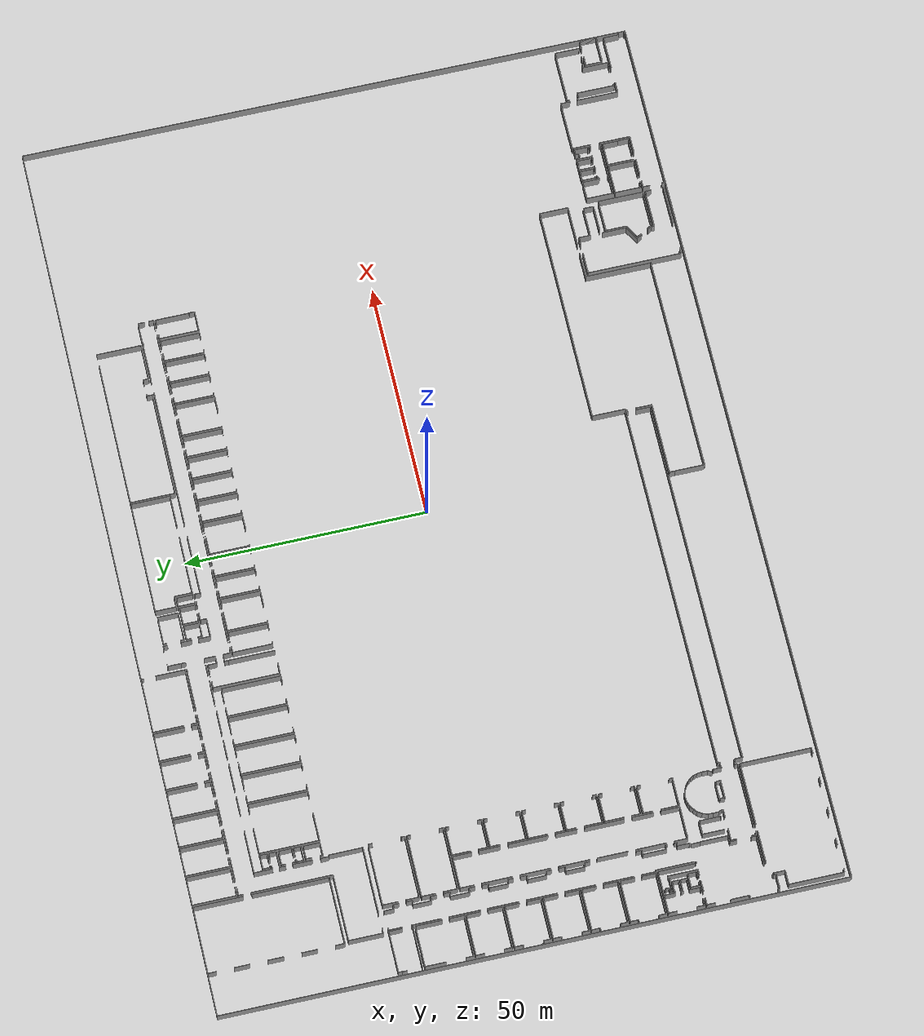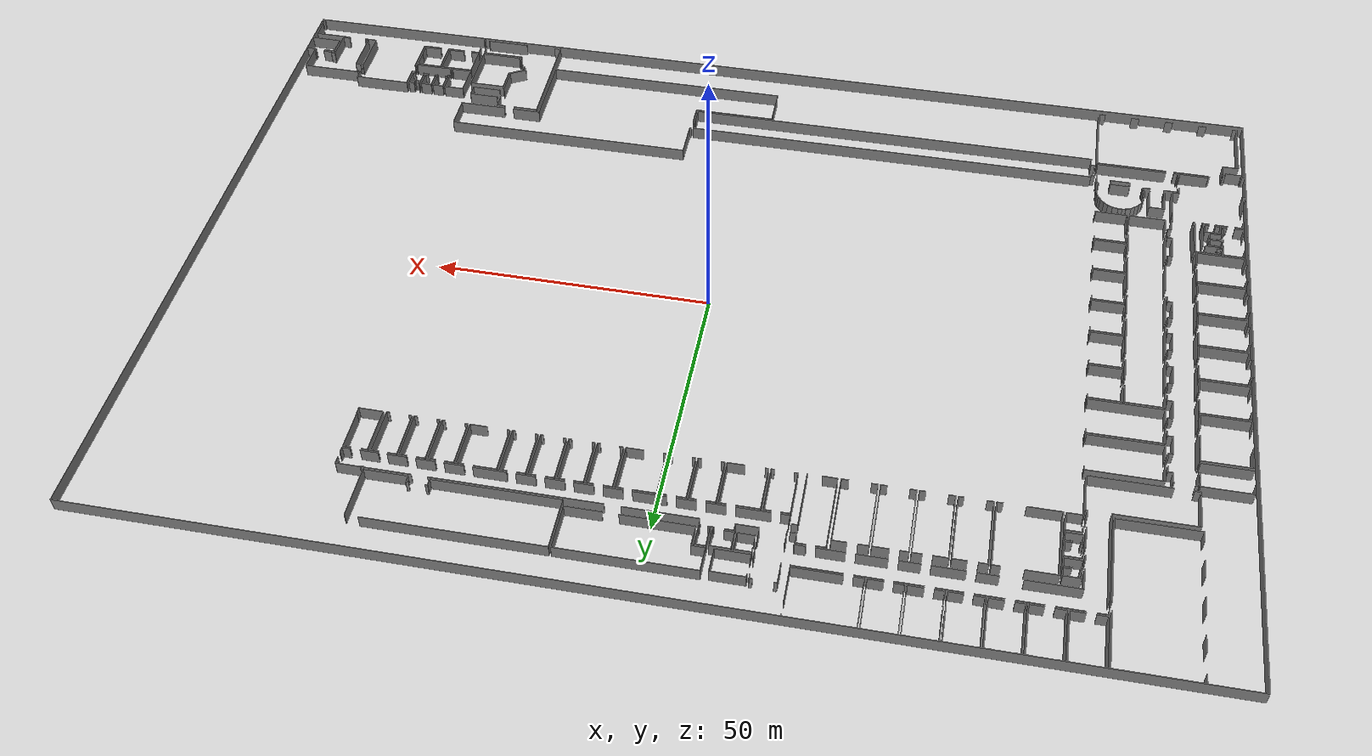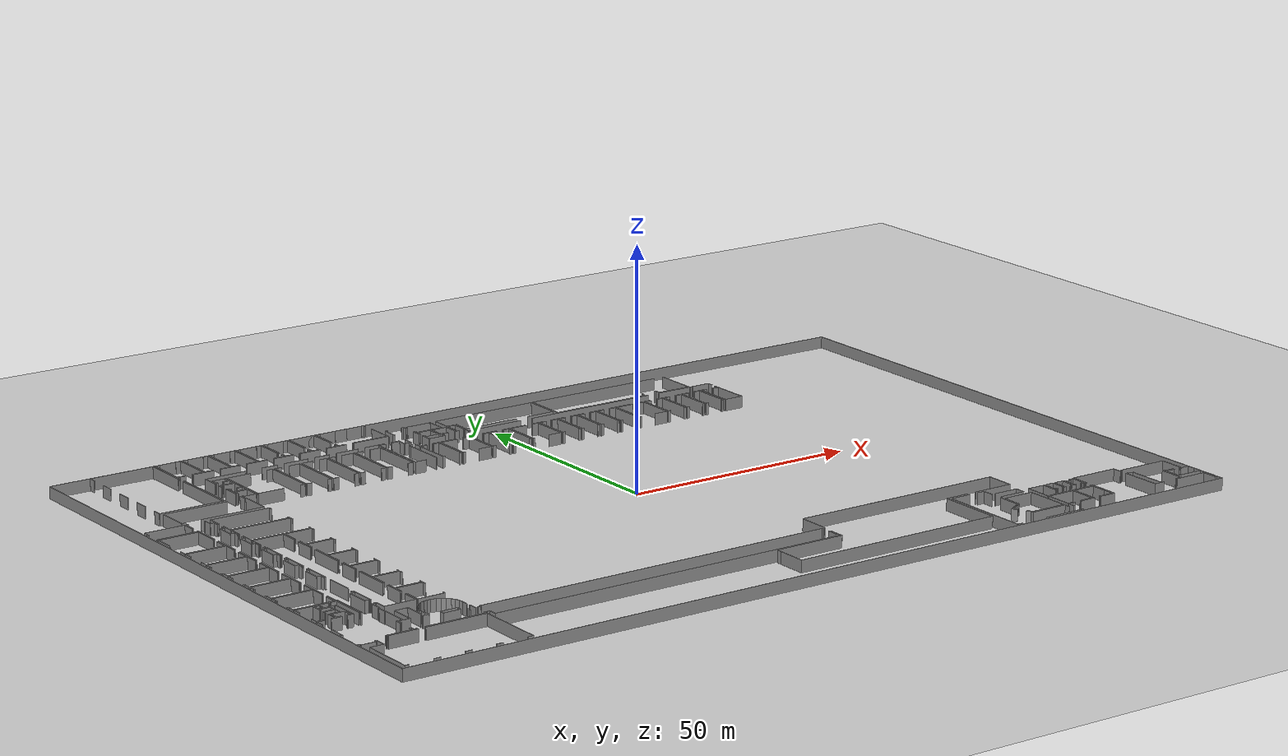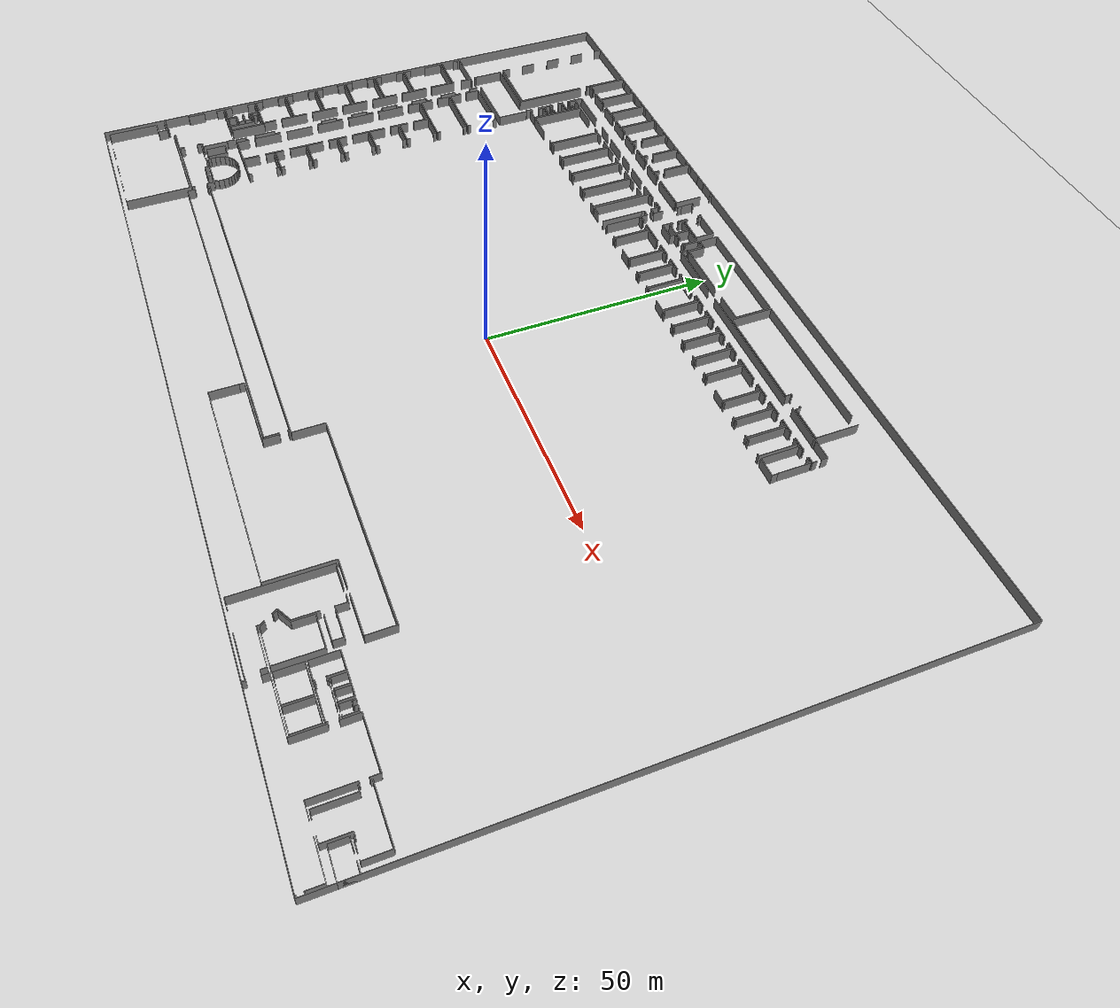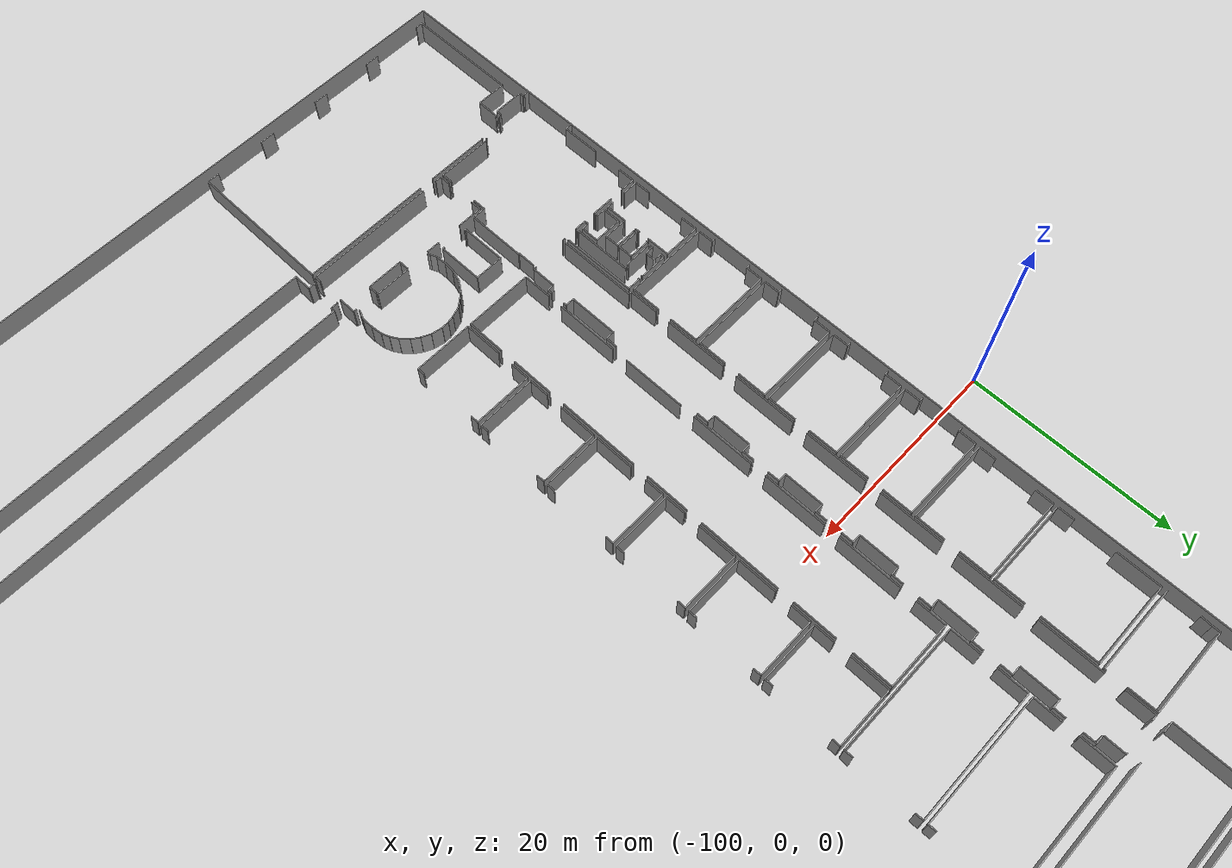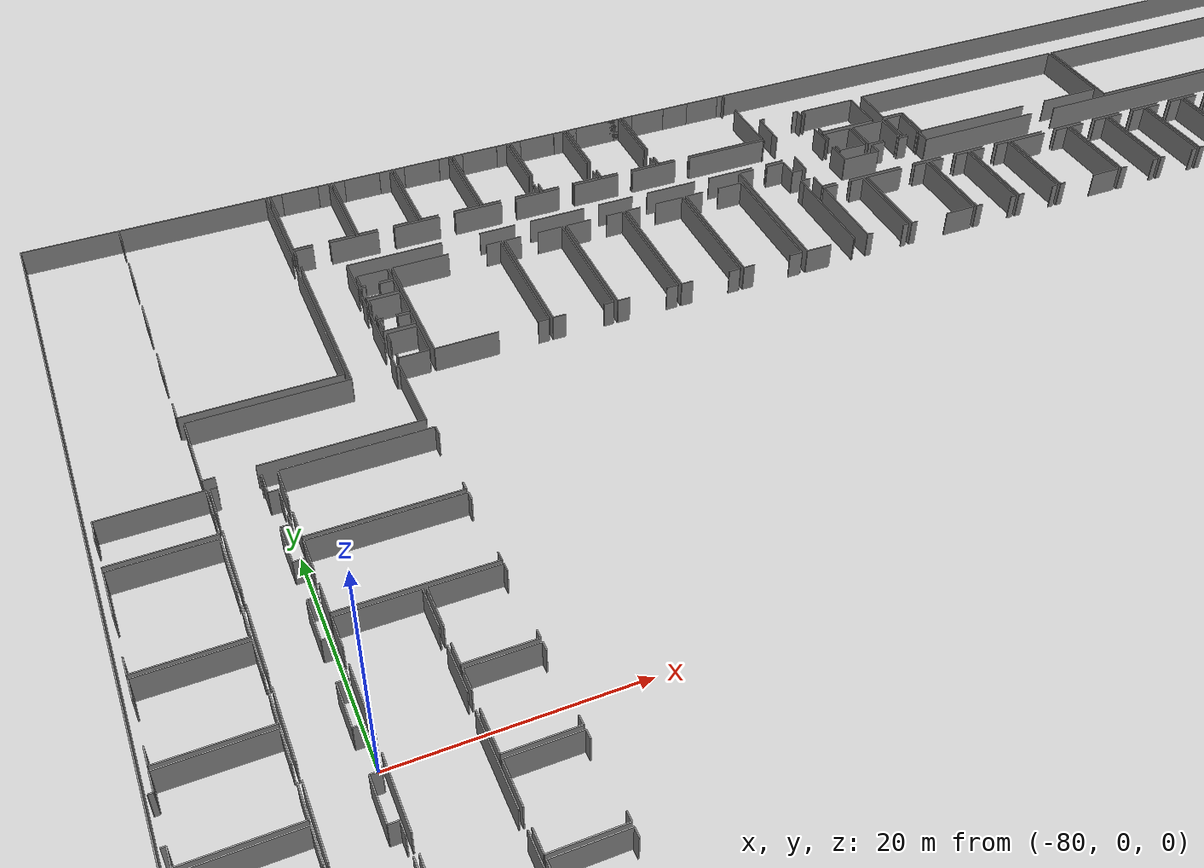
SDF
<sdf version="1.6">
  <world name="default">
    <light name="sun" type="directional">
      <cast_shadows>1</cast_shadows>
      <pose frame="">0 0 10 0 -0 0</pose>
      <diffuse>0.8 0.8 0.8 1</diffuse>
      <specular>0.1 0.1 0.1 1</specular>
      <attenuation>
        <range>1000</range>
        <constant>0.9</constant>
        <linear>0.01</linear>
        <quadratic>0.001</quadratic>
      </attenuation>
      <direction>-0.5 0.5 -1</direction>
    </light>
    <model name="ground_plane">
      <static>1</static>
      <link name="link">
        <collision name="collision">
          <geometry>
            <plane>
              <normal>0 0 1</normal>
              <size>100 100</size>
            </plane>
          </geometry>
          <surface>
            <friction>
              <ode>
                <mu>100</mu>
                <mu2>50</mu2>
              </ode>
              <torsional>
                <ode />
              </torsional>
            </friction>
            <contact>
              <ode />
            </contact>
            <bounce />
          </surface>
          <max_contacts>10</max_contacts>
        </collision>
        <visual name="visual">
          <cast_shadows>0</cast_shadows>
          <geometry>
            <plane>
              <normal>0 0 1</normal>
              <size>100 100</size>
            </plane>
          </geometry>
          <material>
            <script>
              <uri>file://media/materials/scripts/gazebo.material</uri>
              <name>Gazebo/Grey</name>
            </script>
          </material>
        </visual>
        <self_collide>0</self_collide>
        <kinematic>0</kinematic>
        <gravity>1</gravity>
      </link>
    </model>
    <gravity>0 0 -9.8</gravity>
    <magnetic_field>6e-06 2.3e-05 -4.2e-05</magnetic_field>
    <atmosphere type="adiabatic" />
    <physics default="0" name="default_physics" type="ode">
      <max_step_size>0.001</max_step_size>
      <real_time_factor>1</real_time_factor>
      <real_time_update_rate>1000</real_time_update_rate>
    </physics>
    <scene>
      <ambient>0.4 0.4 0.4 1</ambient>
      <background>0.7 0.7 0.7 1</background>
      <shadows>1</shadows>
    </scene>
    <spherical_coordinates>
      <surface_model>EARTH_WGS84</surface_model>
      <latitude_deg>0</latitude_deg>
      <longitude_deg>0</longitude_deg>
      <elevation>0</elevation>
      <heading_deg>0</heading_deg>
    </spherical_coordinates>
  <model name="0510035517_A_40_1_105">
		<static>1</static>
		<link name="Wall_0">
			<collision name="Wall_0_Collision">
				<geometry>
					<box>
						<size>1.88991187104 0.1 2.5</size>
					</box>
				</geometry>
				<pose frame="">0.94495593552 0 1.25 0 0 0</pose>
			</collision>
			<visual name="Wall_0_Visual">
				<pose frame="">0.94495593552 0 1.25 0 0 0</pose>
				<geometry>
					<box>
						<size>1.88991187104 0.1 2.5</size>
					</box>
				</geometry>
				<material>
					<script>
						<uri>file://media/materials/scripts/gazebo.material</uri>
						<name>Gazebo/Grey</name>
					</script>
					<ambient>1 1 1 1</ambient>
				</material>
			</visual>
			<pose frame="">8.88151833425 -27.5061474238 0 0 0 1.57079632679</pose>
		</link>
		<link name="Wall_1">
			<collision name="Wall_1_Collision">
				<geometry>
					<box>
						<size>3.19170431368 0.1 2.5</size>
					</box>
				</geometry>
				<pose frame="">1.59585215684 0 1.25 0 0 0</pose>
			</collision>
			<visual name="Wall_1_Visual">
				<pose frame="">1.59585215684 0 1.25 0 0 0</pose>
				<geometry>
					<box>
						<size>3.19170431368 0.1 2.5</size>
					</box>
				</geometry>
				<material>
					<script>
						<uri>file://media/materials/scripts/gazebo.material</uri>
						<name>Gazebo/Grey</name>
					</script>
					<ambient>1 1 1 1</ambient>
				</material>
			</visual>
			<pose frame="">8.88151833425 -22.0173716348 0 0 0 1.57079632679</pose>
		</link>
		<link name="Wall_2">
			<collision name="Wall_2_Collision">
				<geometry>
					<box>
						<size>3.22550720218 0.1 2.5</size>
					</box>
				</geometry>
				<pose frame="">1.61275360109 0 1.25 0 0 0</pose>
			</collision>
			<visual name="Wall_2_Visual">
				<pose frame="">1.61275360109 0 1.25 0 0 0</pose>
				<geometry>
					<box>
						<size>3.22550720218 0.1 2.5</size>
					</box>
				</geometry>
				<material>
					<script>
						<uri>file://media/materials/scripts/gazebo.material</uri>
						<name>Gazebo/Grey</name>
					</script>
					<ambient>1 1 1 1</ambient>
				</material>
			</visual>
			<pose frame="">8.88151833425 -15.2146038645 0 0 0 1.57079632679</pose>
		</link>
		<link name="Wall_3">
			<collision name="Wall_3_Collision">
				<geometry>
					<box>
						<size>3.07199634014 0.1 2.5</size>
					</box>
				</geometry>
				<pose frame="">1.53599817007 0 1.25 0 0 0</pose>
			</collision>
			<visual name="Wall_3_Visual">
				<pose frame="">1.53599817007 0 1.25 0 0 0</pose>
				<geometry>
					<box>
						<size>3.07199634014 0.1 2.5</size>
					</box>
				</geometry>
				<material>
					<script>
						<uri>file://media/materials/scripts/gazebo.material</uri>
						<name>Gazebo/Grey</name>
					</script>
					<ambient>1 1 1 1</ambient>
				</material>
			</visual>
			<pose frame="">8.88151833425 -8.39429925723 0 0 0 1.57079632679</pose>
		</link>
		<link name="Wall_4">
			<collision name="Wall_4_Collision">
				<geometry>
					<box>
						<size>1.65862894976 0.1 2.5</size>
					</box>
				</geometry>
				<pose frame="">0.82931447488 0 1.25 0 0 0</pose>
			</collision>
			<visual name="Wall_4_Visual">
				<pose frame="">0.82931447488 0 1.25 0 0 0</pose>
				<geometry>
					<box>
						<size>1.65862894976 0.1 2.5</size>
					</box>
				</geometry>
				<material>
					<script>
						<uri>file://media/materials/scripts/gazebo.material</uri>
						<name>Gazebo/Grey</name>
					</script>
					<ambient>1 1 1 1</ambient>
				</material>
			</visual>
			<pose frame="">8.88151833425 -1.69726082233 0 0 0 1.57079632679</pose>
		</link>
		<link name="Wall_5">
			<collision name="Wall_5_Collision">
				<geometry>
					<box>
						<size>13.9150988353 0.1 2.5</size>
					</box>
				</geometry>
				<pose frame="">6.95754941766 0 1.25 0 0 0</pose>
			</collision>
			<visual name="Wall_5_Visual">
				<pose frame="">6.95754941766 0 1.25 0 0 0</pose>
				<geometry>
					<box>
						<size>13.9150988353 0.1 2.5</size>
					</box>
				</geometry>
				<material>
					<script>
						<uri>file://media/materials/scripts/gazebo.material</uri>
						<name>Gazebo/Grey</name>
					</script>
					<ambient>1 1 1 1</ambient>
				</material>
			</visual>
			<pose frame="">8.88151833425 -0.0386318725657 0 0 0 0.0</pose>
		</link>
		<link name="Wall_6">
			<collision name="Wall_6_Collision">
				<geometry>
					<box>
						<size>10.1393416061 0.1 2.5</size>
					</box>
				</geometry>
				<pose frame="">5.06967080307 0 1.25 0 0 0</pose>
			</collision>
			<visual name="Wall_6_Visual">
				<pose frame="">5.06967080307 0 1.25 0 0 0</pose>
				<geometry>
					<box>
						<size>10.1393416061 0.1 2.5</size>
					</box>
				</geometry>
				<material>
					<script>
						<uri>file://media/materials/scripts/gazebo.material</uri>
						<name>Gazebo/Grey</name>
					</script>
					<ambient>1 1 1 1</ambient>
				</material>
			</visual>
			<pose frame="">22.7966171696 -0.0386318725657 0 0 0 -1.57079632679</pose>
		</link>
		<link name="Wall_7">
			<collision name="Wall_7_Collision">
				<geometry>
					<box>
						<size>15.6314214369 0.1 2.5</size>
					</box>
				</geometry>
				<pose frame="">7.81571071844 0 1.25 0 0 0</pose>
			</collision>
			<visual name="Wall_7_Visual">
				<pose frame="">7.81571071844 0 1.25 0 0 0</pose>
				<geometry>
					<box>
						<size>15.6314214369 0.1 2.5</size>
					</box>
				</geometry>
				<material>
					<script>
						<uri>file://media/materials/scripts/gazebo.material</uri>
						<name>Gazebo/Grey</name>
					</script>
					<ambient>1 1 1 1</ambient>
				</material>
			</visual>
			<pose frame="">22.7966171696 -11.870405317 0 0 0 -1.57079632679</pose>
		</link>
		<link name="Wall_8">
			<collision name="Wall_8_Collision">
				<geometry>
					<box>
						<size>13.9150995061 0.1 2.5</size>
					</box>
				</geometry>
				<pose frame="">6.95754975306 0 1.25 0 0 0</pose>
			</collision>
			<visual name="Wall_8_Visual">
				<pose frame="">6.95754975306 0 1.25 0 0 0</pose>
				<geometry>
					<box>
						<size>13.9150995061 0.1 2.5</size>
					</box>
				</geometry>
				<material>
					<script>
						<uri>file://media/materials/scripts/gazebo.material</uri>
						<name>Gazebo/Grey</name>
					</script>
					<ambient>1 1 1 1</ambient>
				</material>
			</visual>
			<pose frame="">22.7966171696 -27.5018267538 0 0 0 -3.14128215132</pose>
		</link>
		<link name="Wall_9">
			<collision name="Wall_9_Collision">
				<geometry>
					<box>
						<size>8.96589847696 0.1 2.5</size>
					</box>
				</geometry>
				<pose frame="">4.48294923848 0 1.25 0 0 0</pose>
			</collision>
			<visual name="Wall_9_Visual">
				<pose frame="">4.48294923848 0 1.25 0 0 0</pose>
				<geometry>
					<box>
						<size>8.96589847696 0.1 2.5</size>
					</box>
				</geometry>
				<material>
					<script>
						<uri>file://media/materials/scripts/gazebo.material</uri>
						<name>Gazebo/Grey</name>
					</script>
					<ambient>1 1 1 1</ambient>
				</material>
			</visual>
			<pose frame="">23.2375796624 -8.98292699974 0 0 0 1.57079632679</pose>
		</link>
		<link name="Wall_10">
			<collision name="Wall_10_Collision">
				<geometry>
					<box>
						<size>1.11269959271 0.1 2.5</size>
					</box>
				</geometry>
				<pose frame="">0.556349796357 0 1.25 0 0 0</pose>
			</collision>
			<visual name="Wall_10_Visual">
				<pose frame="">0.556349796357 0 1.25 0 0 0</pose>
				<geometry>
					<box>
						<size>1.11269959271 0.1 2.5</size>
					</box>
				</geometry>
				<material>
					<script>
						<uri>file://media/materials/scripts/gazebo.material</uri>
						<name>Gazebo/Grey</name>
					</script>
					<ambient>1 1 1 1</ambient>
				</material>
			</visual>
			<pose frame="">23.2375796624 -0.0170285227757 0 0 0 0.0</pose>
		</link>
		<link name="Wall_11">
			<collision name="Wall_11_Collision">
				<geometry>
					<box>
						<size>1.1343029425 0.1 2.5</size>
					</box>
				</geometry>
				<pose frame="">0.567151471252 0 1.25 0 0 0</pose>
			</collision>
			<visual name="Wall_11_Visual">
				<pose frame="">0.567151471252 0 1.25 0 0 0</pose>
				<geometry>
					<box>
						<size>1.1343029425 0.1 2.5</size>
					</box>
				</geometry>
				<material>
					<script>
						<uri>file://media/materials/scripts/gazebo.material</uri>
						<name>Gazebo/Grey</name>
					</script>
					<ambient>1 1 1 1</ambient>
				</material>
			</visual>
			<pose frame="">27.9191526404 -0.0170285227757 0 0 0 0.0</pose>
		</link>
		<link name="Wall_12">
			<collision name="Wall_12_Collision">
				<geometry>
					<box>
						<size>8.95674882294 0.1 2.5</size>
					</box>
				</geometry>
				<pose frame="">4.47837441147 0 1.25 0 0 0</pose>
			</collision>
			<visual name="Wall_12_Visual">
				<pose frame="">4.47837441147 0 1.25 0 0 0</pose>
				<geometry>
					<box>
						<size>8.95674882294 0.1 2.5</size>
					</box>
				</geometry>
				<material>
					<script>
						<uri>file://media/materials/scripts/gazebo.material</uri>
						<name>Gazebo/Grey</name>
					</script>
					<ambient>1 1 1 1</ambient>
				</material>
			</visual>
			<pose frame="">29.0534555829 -0.0170285227757 0 0 0 -1.57079632679</pose>
		</link>
		<link name="Wall_13">
			<collision name="Wall_13_Collision">
				<geometry>
					<box>
						<size>2.48921420992 0.1 2.5</size>
					</box>
				</geometry>
				<pose frame="">1.24460710496 0 1.25 0 0 0</pose>
			</collision>
			<visual name="Wall_13_Visual">
				<pose frame="">1.24460710496 0 1.25 0 0 0</pose>
				<geometry>
					<box>
						<size>2.48921420992 0.1 2.5</size>
					</box>
				</geometry>
				<material>
					<script>
						<uri>file://media/materials/scripts/gazebo.material</uri>
						<name>Gazebo/Grey</name>
					</script>
					<ambient>1 1 1 1</ambient>
				</material>
			</visual>
			<pose frame="">29.0534555829 -8.97377734571 0 0 0 3.14159265359</pose>
		</link>
		<link name="Wall_14">
			<collision name="Wall_14_Collision">
				<geometry>
					<box>
						<size>1.79183060795 0.1 2.5</size>
					</box>
				</geometry>
				<pose frame="">0.895915303977 0 1.25 0 0 0</pose>
			</collision>
			<visual name="Wall_14_Visual">
				<pose frame="">0.895915303977 0 1.25 0 0 0</pose>
				<geometry>
					<box>
						<size>1.79183060795 0.1 2.5</size>
					</box>
				</geometry>
				<material>
					<script>
						<uri>file://media/materials/scripts/gazebo.material</uri>
						<name>Gazebo/Grey</name>
					</script>
					<ambient>1 1 1 1</ambient>
				</material>
			</visual>
			<pose frame="">25.0293869096 -8.97377734571 0 0 0 -3.13648631499</pose>
		</link>
		<link name="Wall_15">
			<collision name="Wall_15_Collision">
				<geometry>
					<box>
						<size>8.92650413323 0.1 2.5</size>
					</box>
				</geometry>
				<pose frame="">4.46325206661 0 1.25 0 0 0</pose>
			</collision>
			<visual name="Wall_15_Visual">
				<pose frame="">4.46325206661 0 1.25 0 0 0</pose>
				<geometry>
					<box>
						<size>8.92650413323 0.1 2.5</size>
					</box>
				</geometry>
				<material>
					<script>
						<uri>file://media/materials/scripts/gazebo.material</uri>
						<name>Gazebo/Grey</name>
					</script>
					<ambient>1 1 1 1</ambient>
				</material>
			</visual>
			<pose frame="">29.4268122987 -8.96284859229 0 0 0 1.57079632679</pose>
		</link>
		<link name="Wall_16">
			<collision name="Wall_16_Collision">
				<geometry>
					<box>
						<size>1.14192765419 0.1 2.5</size>
					</box>
				</geometry>
				<pose frame="">0.570963827097 0 1.25 0 0 0</pose>
			</collision>
			<visual name="Wall_16_Visual">
				<pose frame="">0.570963827097 0 1.25 0 0 0</pose>
				<geometry>
					<box>
						<size>1.14192765419 0.1 2.5</size>
					</box>
				</geometry>
				<material>
					<script>
						<uri>file://media/materials/scripts/gazebo.material</uri>
						<name>Gazebo/Grey</name>
					</script>
					<ambient>1 1 1 1</ambient>
				</material>
			</visual>
			<pose frame="">29.4268122987 -0.0363444590585 0 0 0 0.0</pose>
		</link>
		<link name="Wall_17">
			<collision name="Wall_17_Collision">
				<geometry>
					<box>
						<size>1.08702973002 0.1 2.5</size>
					</box>
				</geometry>
				<pose frame="">0.543514865011 0 1.25 0 0 0</pose>
			</collision>
			<visual name="Wall_17_Visual">
				<pose frame="">0.543514865011 0 1.25 0 0 0</pose>
				<geometry>
					<box>
						<size>1.08702973002 0.1 2.5</size>
					</box>
				</geometry>
				<material>
					<script>
						<uri>file://media/materials/scripts/gazebo.material</uri>
						<name>Gazebo/Grey</name>
					</script>
					<ambient>1 1 1 1</ambient>
				</material>
			</visual>
			<pose frame="">34.1086394337 -0.0363444590585 0 0 0 0.0</pose>
		</link>
		<link name="Wall_18">
			<collision name="Wall_18_Collision">
				<geometry>
					<box>
						<size>8.94505759834 0.1 2.5</size>
					</box>
				</geometry>
				<pose frame="">4.47252879917 0 1.25 0 0 0</pose>
			</collision>
			<visual name="Wall_18_Visual">
				<pose frame="">4.47252879917 0 1.25 0 0 0</pose>
				<geometry>
					<box>
						<size>8.94505759834 0.1 2.5</size>
					</box>
				</geometry>
				<material>
					<script>
						<uri>file://media/materials/scripts/gazebo.material</uri>
						<name>Gazebo/Grey</name>
					</script>
					<ambient>1 1 1 1</ambient>
				</material>
			</visual>
			<pose frame="">35.1956691638 -0.0363444590585 0 0 0 -1.57079632679</pose>
		</link>
		<link name="Wall_19">
			<collision name="Wall_19_Collision">
				<geometry>
					<box>
						<size>2.43558707103 0.1 2.5</size>
					</box>
				</geometry>
				<pose frame="">1.21779353552 0 1.25 0 0 0</pose>
			</collision>
			<visual name="Wall_19_Visual">
				<pose frame="">1.21779353552 0 1.25 0 0 0</pose>
				<geometry>
					<box>
						<size>2.43558707103 0.1 2.5</size>
					</box>
				</geometry>
				<material>
					<script>
						<uri>file://media/materials/scripts/gazebo.material</uri>
						<name>Gazebo/Grey</name>
					</script>
					<ambient>1 1 1 1</ambient>
				</material>
			</visual>
			<pose frame="">35.1956691638 -8.9814020574 0 0 0 3.14159265359</pose>
		</link>
		<link name="Wall_20">
			<collision name="Wall_20_Collision">
				<geometry>
					<box>
						<size>1.81579280115 0.1 2.5</size>
					</box>
				</geometry>
				<pose frame="">0.907896400576 0 1.25 0 0 0</pose>
			</collision>
			<visual name="Wall_20_Visual">
				<pose frame="">0.907896400576 0 1.25 0 0 0</pose>
				<geometry>
					<box>
						<size>1.81579280115 0.1 2.5</size>
					</box>
				</geometry>
				<material>
					<script>
						<uri>file://media/materials/scripts/gazebo.material</uri>
						<name>Gazebo/Grey</name>
					</script>
					<ambient>1 1 1 1</ambient>
				</material>
			</visual>
			<pose frame="">31.2425103092 -8.9814020574 0 0 0 3.13137464416</pose>
		</link>
		<link name="Wall_21">
			<collision name="Wall_21_Collision">
				<geometry>
					<box>
						<size>8.92650413323 0.1 2.5</size>
					</box>
				</geometry>
				<pose frame="">4.46325206661 0 1.25 0 0 0</pose>
			</collision>
			<visual name="Wall_21_Visual">
				<pose frame="">4.46325206661 0 1.25 0 0 0</pose>
				<geometry>
					<box>
						<size>8.92650413323 0.1 2.5</size>
					</box>
				</geometry>
				<material>
					<script>
						<uri>file://media/materials/scripts/gazebo.material</uri>
						<name>Gazebo/Grey</name>
					</script>
					<ambient>1 1 1 1</ambient>
				</material>
			</visual>
			<pose frame="">35.5809712612 -8.96513600579 0 0 0 1.57079632679</pose>
		</link>
		<link name="Wall_22">
			<collision name="Wall_22_Collision">
				<geometry>
					<box>
						<size>1.06822210785 0.1 2.5</size>
					</box>
				</geometry>
				<pose frame="">0.534111053926 0 1.25 0 0 0</pose>
			</collision>
			<visual name="Wall_22_Visual">
				<pose frame="">0.534111053926 0 1.25 0 0 0</pose>
				<geometry>
					<box>
						<size>1.06822210785 0.1 2.5</size>
					</box>
				</geometry>
				<material>
					<script>
						<uri>file://media/materials/scripts/gazebo.material</uri>
						<name>Gazebo/Grey</name>
					</script>
					<ambient>1 1 1 1</ambient>
				</material>
			</visual>
			<pose frame="">35.5809712612 -0.0386318725657 0 0 0 0.0</pose>
		</link>
		<link name="Wall_23">
			<collision name="Wall_23_Collision">
				<geometry>
					<box>
						<size>1.06517222318 0.1 2.5</size>
					</box>
				</geometry>
				<pose frame="">0.532586111588 0 1.25 0 0 0</pose>
			</collision>
			<visual name="Wall_23_Visual">
				<pose frame="">0.532586111588 0 1.25 0 0 0</pose>
				<geometry>
					<box>
						<size>1.06517222318 0.1 2.5</size>
					</box>
				</geometry>
				<material>
					<script>
						<uri>file://media/materials/scripts/gazebo.material</uri>
						<name>Gazebo/Grey</name>
					</script>
					<ambient>1 1 1 1</ambient>
				</material>
			</visual>
			<pose frame="">40.2544112134 -0.0386318725657 0 0 0 0.0</pose>
		</link>
		<link name="Wall_24">
			<collision name="Wall_24_Collision">
				<geometry>
					<box>
						<size>8.91303380924 0.1 2.5</size>
					</box>
				</geometry>
				<pose frame="">4.45651690462 0 1.25 0 0 0</pose>
			</collision>
			<visual name="Wall_24_Visual">
				<pose frame="">4.45651690462 0 1.25 0 0 0</pose>
				<geometry>
					<box>
						<size>8.91303380924 0.1 2.5</size>
					</box>
				</geometry>
				<material>
					<script>
						<uri>file://media/materials/scripts/gazebo.material</uri>
						<name>Gazebo/Grey</name>
					</script>
					<ambient>1 1 1 1</ambient>
				</material>
			</visual>
			<pose frame="">41.3195834366 -0.0386318725657 0 0 0 -1.57079632679</pose>
		</link>
		<link name="Wall_25">
			<collision name="Wall_25_Collision">
				<geometry>
					<box>
						<size>2.54029977825 0.1 2.5</size>
					</box>
				</geometry>
				<pose frame="">1.27014988912 0 1.25 0 0 0</pose>
			</collision>
			<visual name="Wall_25_Visual">
				<pose frame="">1.27014988912 0 1.25 0 0 0</pose>
				<geometry>
					<box>
						<size>2.54029977825 0.1 2.5</size>
					</box>
				</geometry>
				<material>
					<script>
						<uri>file://media/materials/scripts/gazebo.material</uri>
						<name>Gazebo/Grey</name>
					</script>
					<ambient>1 1 1 1</ambient>
				</material>
			</visual>
			<pose frame="">41.3195834366 -8.95166568181 0 0 0 3.14159265359</pose>
		</link>
		<link name="Wall_26">
			<collision name="Wall_26_Collision">
				<geometry>
					<box>
						<size>1.66097098572 0.1 2.5</size>
					</box>
				</geometry>
				<pose frame="">0.830485492859 0 1.25 0 0 0</pose>
			</collision>
			<visual name="Wall_26_Visual">
				<pose frame="">0.830485492859 0 1.25 0 0 0</pose>
				<geometry>
					<box>
						<size>1.66097098572 0.1 2.5</size>
					</box>
				</geometry>
				<material>
					<script>
						<uri>file://media/materials/scripts/gazebo.material</uri>
						<name>Gazebo/Grey</name>
					</script>
					<ambient>1 1 1 1</ambient>
				</material>
			</visual>
			<pose frame="">37.2418876245 -8.95166568181 0 0 0 -3.13348265542</pose>
		</link>
		<link name="Wall_27">
			<collision name="Wall_27_Collision">
				<geometry>
					<box>
						<size>8.94454928423 0.1 2.5</size>
					</box>
				</geometry>
				<pose frame="">4.47227464212 0 1.25 0 0 0</pose>
			</collision>
			<visual name="Wall_27_Visual">
				<pose frame="">4.47227464212 0 1.25 0 0 0</pose>
				<geometry>
					<box>
						<size>8.94454928423 0.1 2.5</size>
					</box>
				</geometry>
				<material>
					<script>
						<uri>file://media/materials/scripts/gazebo.material</uri>
						<name>Gazebo/Grey</name>
					</script>
					<ambient>1 1 1 1</ambient>
				</material>
			</visual>
			<pose frame="">41.7186100151 -8.96996498987 0 0 0 1.57079632679</pose>
		</link>
		<link name="Wall_28">
			<collision name="Wall_28_Collision">
				<geometry>
					<box>
						<size>1.02755697884 0.1 2.5</size>
					</box>
				</geometry>
				<pose frame="">0.513778489418 0 1.25 0 0 0</pose>
			</collision>
			<visual name="Wall_28_Visual">
				<pose frame="">0.513778489418 0 1.25 0 0 0</pose>
				<geometry>
					<box>
						<size>1.02755697884 0.1 2.5</size>
					</box>
				</geometry>
				<material>
					<script>
						<uri>file://media/materials/scripts/gazebo.material</uri>
						<name>Gazebo/Grey</name>
					</script>
					<ambient>1 1 1 1</ambient>
				</material>
			</visual>
			<pose frame="">41.7186100151 -0.0254157056353 0 0 0 0.0</pose>
		</link>
		<link name="Wall_29">
			<collision name="Wall_29_Collision">
				<geometry>
					<box>
						<size>1.08804635825 0.1 2.5</size>
					</box>
				</geometry>
				<pose frame="">0.544023179124 0 1.25 0 0 0</pose>
			</collision>
			<visual name="Wall_29_Visual">
				<pose frame="">0.544023179124 0 1.25 0 0 0</pose>
				<geometry>
					<box>
						<size>1.08804635825 0.1 2.5</size>
					</box>
				</geometry>
				<material>
					<script>
						<uri>file://media/materials/scripts/gazebo.material</uri>
						<name>Gazebo/Grey</name>
					</script>
					<ambient>1 1 1 1</ambient>
				</material>
			</visual>
			<pose frame="">46.3610428064 -0.0254157056353 0 0 0 0.0</pose>
		</link>
		<link name="Wall_30">
			<collision name="Wall_30_Collision">
				<geometry>
					<box>
						<size>6.27412109313 0.1 2.5</size>
					</box>
				</geometry>
				<pose frame="">3.13706054656 0 1.25 0 0 0</pose>
			</collision>
			<visual name="Wall_30_Visual">
				<pose frame="">3.13706054656 0 1.25 0 0 0</pose>
				<geometry>
					<box>
						<size>6.27412109313 0.1 2.5</size>
					</box>
				</geometry>
				<material>
					<script>
						<uri>file://media/materials/scripts/gazebo.material</uri>
						<name>Gazebo/Grey</name>
					</script>
					<ambient>1 1 1 1</ambient>
				</material>
			</visual>
			<pose frame="">47.4490891646 -0.0254157056353 0 0 0 -1.57079632679</pose>
		</link>
		<link name="Wall_31">
			<collision name="Wall_31_Collision">
				<geometry>
					<box>
						<size>1.18793008139 0.1 2.5</size>
					</box>
				</geometry>
				<pose frame="">0.593965040697 0 1.25 0 0 0</pose>
			</collision>
			<visual name="Wall_31_Visual">
				<pose frame="">0.593965040697 0 1.25 0 0 0</pose>
				<geometry>
					<box>
						<size>1.18793008139 0.1 2.5</size>
					</box>
				</geometry>
				<material>
					<script>
						<uri>file://media/materials/scripts/gazebo.material</uri>
						<name>Gazebo/Grey</name>
					</script>
					<ambient>1 1 1 1</ambient>
				</material>
			</visual>
			<pose frame="">47.4490891646 -7.79347197601 0 0 0 -1.57079632679</pose>
		</link>
		<link name="Wall_32">
			<collision name="Wall_32_Collision">
				<geometry>
					<box>
						<size>2.46735670307 0.1 2.5</size>
					</box>
				</geometry>
				<pose frame="">1.23367835154 0 1.25 0 0 0</pose>
			</collision>
			<visual name="Wall_32_Visual">
				<pose frame="">1.23367835154 0 1.25 0 0 0</pose>
				<geometry>
					<box>
						<size>2.46735670307 0.1 2.5</size>
					</box>
				</geometry>
				<material>
					<script>
						<uri>file://media/materials/scripts/gazebo.material</uri>
						<name>Gazebo/Grey</name>
					</script>
					<ambient>1 1 1 1</ambient>
				</material>
			</visual>
			<pose frame="">47.4490891646 -8.9814020574 0 0 0 3.14159265359</pose>
		</link>
		<link name="Wall_33">
			<collision name="Wall_33_Collision">
				<geometry>
					<box>
						<size>1.75550004482 0.1 2.5</size>
					</box>
				</geometry>
				<pose frame="">0.877750022412 0 1.25 0 0 0</pose>
			</collision>
			<visual name="Wall_33_Visual">
				<pose frame="">0.877750022412 0 1.25 0 0 0</pose>
				<geometry>
					<box>
						<size>1.75550004482 0.1 2.5</size>
					</box>
				</geometry>
				<material>
					<script>
						<uri>file://media/materials/scripts/gazebo.material</uri>
						<name>Gazebo/Grey</name>
					</script>
					<ambient>1 1 1 1</ambient>
				</material>
			</visual>
			<pose frame="">43.4740728033 -8.9814020574 0 0 0 3.13507761619</pose>
		</link>
		<link name="Wall_34">
			<collision name="Wall_34_Collision">
				<geometry>
					<box>
						<size>1.06568053729 0.1 2.5</size>
					</box>
				</geometry>
				<pose frame="">0.532840268644 0 1.25 0 0 0</pose>
			</collision>
			<visual name="Wall_34_Visual">
				<pose frame="">0.532840268644 0 1.25 0 0 0</pose>
				<geometry>
					<box>
						<size>1.06568053729 0.1 2.5</size>
					</box>
				</geometry>
				<material>
					<script>
						<uri>file://media/materials/scripts/gazebo.material</uri>
						<name>Gazebo/Grey</name>
					</script>
					<ambient>1 1 1 1</ambient>
				</material>
			</visual>
			<pose frame="">47.856757083 -0.0264323338607 0 0 0 0.0</pose>
		</link>
		<link name="Wall_35">
			<collision name="Wall_35_Collision">
				<geometry>
					<box>
						<size>1.06059739616 0.1 2.5</size>
					</box>
				</geometry>
				<pose frame="">0.53029869808 0 1.25 0 0 0</pose>
			</collision>
			<visual name="Wall_35_Visual">
				<pose frame="">0.53029869808 0 1.25 0 0 0</pose>
				<geometry>
					<box>
						<size>1.06059739616 0.1 2.5</size>
					</box>
				</geometry>
				<material>
					<script>
						<uri>file://media/materials/scripts/gazebo.material</uri>
						<name>Gazebo/Grey</name>
					</script>
					<ambient>1 1 1 1</ambient>
				</material>
			</visual>
			<pose frame="">52.5482421863 -0.0264323338607 0 0 0 0.0</pose>
		</link>
		<link name="Wall_36">
			<collision name="Wall_36_Collision">
				<geometry>
					<box>
						<size>6.27971254837 0.1 2.5</size>
					</box>
				</geometry>
				<pose frame="">3.13985627418 0 1.25 0 0 0</pose>
			</collision>
			<visual name="Wall_36_Visual">
				<pose frame="">3.13985627418 0 1.25 0 0 0</pose>
				<geometry>
					<box>
						<size>6.27971254837 0.1 2.5</size>
					</box>
				</geometry>
				<material>
					<script>
						<uri>file://media/materials/scripts/gazebo.material</uri>
						<name>Gazebo/Grey</name>
					</script>
					<ambient>1 1 1 1</ambient>
				</material>
			</visual>
			<pose frame="">53.6088395824 -0.0264323338607 0 0 0 -1.57079632679</pose>
		</link>
		<link name="Wall_37">
			<collision name="Wall_37_Collision">
				<geometry>
					<box>
						<size>1.17522222858 0.1 2.5</size>
					</box>
				</geometry>
				<pose frame="">0.587611114288 0 1.25 0 0 0</pose>
			</collision>
			<visual name="Wall_37_Visual">
				<pose frame="">0.587611114288 0 1.25 0 0 0</pose>
				<geometry>
					<box>
						<size>1.17522222858 0.1 2.5</size>
					</box>
				</geometry>
				<material>
					<script>
						<uri>file://media/materials/scripts/gazebo.material</uri>
						<name>Gazebo/Grey</name>
					</script>
					<ambient>1 1 1 1</ambient>
				</material>
			</visual>
			<pose frame="">53.6088395824 -7.80008005947 0 0 0 -1.57079632679</pose>
		</link>
		<link name="Wall_38">
			<collision name="Wall_38_Collision">
				<geometry>
					<box>
						<size>2.6465374278 0.1 2.5</size>
					</box>
				</geometry>
				<pose frame="">1.3232687139 0 1.25 0 0 0</pose>
			</collision>
			<visual name="Wall_38_Visual">
				<pose frame="">1.3232687139 0 1.25 0 0 0</pose>
				<geometry>
					<box>
						<size>2.6465374278 0.1 2.5</size>
					</box>
				</geometry>
				<material>
					<script>
						<uri>file://media/materials/scripts/gazebo.material</uri>
						<name>Gazebo/Grey</name>
					</script>
					<ambient>1 1 1 1</ambient>
				</material>
			</visual>
			<pose frame="">53.6088395824 -8.97530228805 0 0 0 3.14159265359</pose>
		</link>
		<link name="Wall_39">
			<collision name="Wall_39_Collision">
				<geometry>
					<box>
						<size>1.59508968567 0.1 2.5</size>
					</box>
				</geometry>
				<pose frame="">0.797544842836 0 1.25 0 0 0</pose>
			</collision>
			<visual name="Wall_39_Visual">
				<pose frame="">0.797544842836 0 1.25 0 0 0</pose>
				<geometry>
					<box>
						<size>1.59508968567 0.1 2.5</size>
					</box>
				</geometry>
				<material>
					<script>
						<uri>file://media/materials/scripts/gazebo.material</uri>
						<name>Gazebo/Grey</name>
					</script>
					<ambient>1 1 1 1</ambient>
				</material>
			</visual>
			<pose frame="">49.4538800252 -8.97530228805 0 0 0 3.14159265359</pose>
		</link>
		<link name="Wall_40">
			<collision name="Wall_40_Collision">
				<geometry>
					<box>
						<size>1.19657142131 0.1 2.5</size>
					</box>
				</geometry>
				<pose frame="">0.598285710655 0 1.25 0 0 0</pose>
			</collision>
			<visual name="Wall_40_Visual">
				<pose frame="">0.598285710655 0 1.25 0 0 0</pose>
				<geometry>
					<box>
						<size>1.19657142131 0.1 2.5</size>
					</box>
				</geometry>
				<material>
					<script>
						<uri>file://media/materials/scripts/gazebo.material</uri>
						<name>Gazebo/Grey</name>
					</script>
					<ambient>1 1 1 1</ambient>
				</material>
			</visual>
			<pose frame="">47.8587903395 -8.97530228805 0 0 0 1.57079632679</pose>
		</link>
		<link name="Wall_41">
			<collision name="Wall_41_Collision">
				<geometry>
					<box>
						<size>6.21922350132 0.1 2.5</size>
					</box>
				</geometry>
				<pose frame="">3.10961175066 0 1.25 0 0 0</pose>
			</collision>
			<visual name="Wall_41_Visual">
				<pose frame="">3.10961175066 0 1.25 0 0 0</pose>
				<geometry>
					<box>
						<size>6.21922350132 0.1 2.5</size>
					</box>
				</geometry>
				<material>
					<script>
						<uri>file://media/materials/scripts/gazebo.material</uri>
						<name>Gazebo/Grey</name>
					</script>
					<ambient>1 1 1 1</ambient>
				</material>
			</visual>
			<pose frame="">47.8587903395 -6.24565550282 0 0 0 1.57112325772</pose>
		</link>
		<link name="Wall_42">
			<collision name="Wall_42_Collision">
				<geometry>
					<box>
						<size>1.20190871949 0.1 2.5</size>
					</box>
				</geometry>
				<pose frame="">0.600954359747 0 1.25 0 0 0</pose>
			</collision>
			<visual name="Wall_42_Visual">
				<pose frame="">0.600954359747 0 1.25 0 0 0</pose>
				<geometry>
					<box>
						<size>1.20190871949 0.1 2.5</size>
					</box>
				</geometry>
				<material>
					<script>
						<uri>file://media/materials/scripts/gazebo.material</uri>
						<name>Gazebo/Grey</name>
					</script>
					<ambient>1 1 1 1</ambient>
				</material>
			</visual>
			<pose frame="">54.0045621192 -8.98470609913 0 0 0 1.57079632679</pose>
		</link>
		<link name="Wall_43">
			<collision name="Wall_43_Collision">
				<geometry>
					<box>
						<size>6.25226358628 0.1 2.5</size>
					</box>
				</geometry>
				<pose frame="">3.12613179314 0 1.25 0 0 0</pose>
			</collision>
			<visual name="Wall_43_Visual">
				<pose frame="">3.12613179314 0 1.25 0 0 0</pose>
				<geometry>
					<box>
						<size>6.25226358628 0.1 2.5</size>
					</box>
				</geometry>
				<material>
					<script>
						<uri>file://media/materials/scripts/gazebo.material</uri>
						<name>Gazebo/Grey</name>
					</script>
					<ambient>1 1 1 1</ambient>
				</material>
			</visual>
			<pose frame="">54.0045621192 -6.25226358628 0 0 0 1.57079632679</pose>
		</link>
		<link name="Wall_44">
			<collision name="Wall_44_Collision">
				<geometry>
					<box>
						<size>1.02221968065 0.1 2.5</size>
					</box>
				</geometry>
				<pose frame="">0.511109840326 0 1.25 0 0 0</pose>
			</collision>
			<visual name="Wall_44_Visual">
				<pose frame="">0.511109840326 0 1.25 0 0 0</pose>
				<geometry>
					<box>
						<size>1.02221968065 0.1 2.5</size>
					</box>
				</geometry>
				<material>
					<script>
						<uri>file://media/materials/scripts/gazebo.material</uri>
						<name>Gazebo/Grey</name>
					</script>
					<ambient>1 1 1 1</ambient>
				</material>
			</visual>
			<pose frame="">54.0045621192 -0.0 0 0 0 0.0</pose>
		</link>
		<link name="Wall_45">
			<collision name="Wall_45_Collision">
				<geometry>
					<box>
						<size>1.17776379914 0.1 2.5</size>
					</box>
				</geometry>
				<pose frame="">0.58888189957 0 1.25 0 0 0</pose>
			</collision>
			<visual name="Wall_45_Visual">
				<pose frame="">0.58888189957 0 1.25 0 0 0</pose>
				<geometry>
					<box>
						<size>1.17776379914 0.1 2.5</size>
					</box>
				</geometry>
				<material>
					<script>
						<uri>file://media/materials/scripts/gazebo.material</uri>
						<name>Gazebo/Grey</name>
					</script>
					<ambient>1 1 1 1</ambient>
				</material>
			</visual>
			<pose frame="">58.6025174256 -0.0 0 0 0 0.0</pose>
		</link>
		<link name="Wall_46">
			<collision name="Wall_46_Collision">
				<geometry>
					<box>
						<size>6.31046555219 0.1 2.5</size>
					</box>
				</geometry>
				<pose frame="">3.15523277609 0 1.25 0 0 0</pose>
			</collision>
			<visual name="Wall_46_Visual">
				<pose frame="">3.15523277609 0 1.25 0 0 0</pose>
				<geometry>
					<box>
						<size>6.31046555219 0.1 2.5</size>
					</box>
				</geometry>
				<material>
					<script>
						<uri>file://media/materials/scripts/gazebo.material</uri>
						<name>Gazebo/Grey</name>
					</script>
					<ambient>1 1 1 1</ambient>
				</material>
			</visual>
			<pose frame="">59.7802812248 -0.0 0 0 0 -1.57079632679</pose>
		</link>
		<link name="Wall_47">
			<collision name="Wall_47_Collision">
				<geometry>
					<box>
						<size>1.18818423845 0.1 2.5</size>
					</box>
				</geometry>
				<pose frame="">0.594092119225 0 1.25 0 0 0</pose>
			</collision>
			<visual name="Wall_47_Visual">
				<pose frame="">0.594092119225 0 1.25 0 0 0</pose>
				<geometry>
					<box>
						<size>1.18818423845 0.1 2.5</size>
					</box>
				</geometry>
				<material>
					<script>
						<uri>file://media/materials/scripts/gazebo.material</uri>
						<name>Gazebo/Grey</name>
					</script>
					<ambient>1 1 1 1</ambient>
				</material>
			</visual>
			<pose frame="">59.7802812248 -7.81278791229 0 0 0 -1.57079632679</pose>
		</link>
		<link name="Wall_48">
			<collision name="Wall_48_Collision">
				<geometry>
					<box>
						<size>2.60663476996 0.1 2.5</size>
					</box>
				</geometry>
				<pose frame="">1.30331738498 0 1.25 0 0 0</pose>
			</collision>
			<visual name="Wall_48_Visual">
				<pose frame="">1.30331738498 0 1.25 0 0 0</pose>
				<geometry>
					<box>
						<size>2.60663476996 0.1 2.5</size>
					</box>
				</geometry>
				<material>
					<script>
						<uri>file://media/materials/scripts/gazebo.material</uri>
						<name>Gazebo/Grey</name>
					</script>
					<ambient>1 1 1 1</ambient>
				</material>
			</visual>
			<pose frame="">59.7802812248 -9.00097215074 0 0 0 3.14159265359</pose>
		</link>
		<link name="Wall_49">
			<collision name="Wall_49_Collision">
				<geometry>
					<box>
						<size>1.65159265391 0.1 2.5</size>
					</box>
				</geometry>
				<pose frame="">0.825796326955 0 1.25 0 0 0</pose>
			</collision>
			<visual name="Wall_49_Visual">
				<pose frame="">0.825796326955 0 1.25 0 0 0</pose>
				<geometry>
					<box>
						<size>1.65159265391 0.1 2.5</size>
					</box>
				</geometry>
				<material>
					<script>
						<uri>file://media/materials/scripts/gazebo.material</uri>
						<name>Gazebo/Grey</name>
					</script>
					<ambient>1 1 1 1</ambient>
				</material>
			</visual>
			<pose frame="">55.6560746713 -9.00097215074 0 0 0 3.13174378768</pose>
		</link>
		<link name="Wall_50">
			<collision name="Wall_50_Collision">
				<geometry>
					<box>
						<size>1.0982126405 0.1 2.5</size>
					</box>
				</geometry>
				<pose frame="">0.549106320251 0 1.25 0 0 0</pose>
			</collision>
			<visual name="Wall_50_Visual">
				<pose frame="">0.549106320251 0 1.25 0 0 0</pose>
				<geometry>
					<box>
						<size>1.0982126405 0.1 2.5</size>
					</box>
				</geometry>
				<material>
					<script>
						<uri>file://media/materials/scripts/gazebo.material</uri>
						<name>Gazebo/Grey</name>
					</script>
					<ambient>1 1 1 1</ambient>
				</material>
			</visual>
			<pose frame="">60.1721914057 -0.0144869522121 0 0 0 0.0</pose>
		</link>
		<link name="Wall_51">
			<collision name="Wall_51_Collision">
				<geometry>
					<box>
						<size>2.73142588463 0.1 2.5</size>
					</box>
				</geometry>
				<pose frame="">1.36571294231 0 1.25 0 0 0</pose>
			</collision>
			<visual name="Wall_51_Visual">
				<pose frame="">1.36571294231 0 1.25 0 0 0</pose>
				<geometry>
					<box>
						<size>2.73142588463 0.1 2.5</size>
					</box>
				</geometry>
				<material>
					<script>
						<uri>file://media/materials/scripts/gazebo.material</uri>
						<name>Gazebo/Grey</name>
					</script>
					<ambient>1 1 1 1</ambient>
				</material>
			</visual>
			<pose frame="">64.8103035271 -0.0144869522121 0 0 0 0.0</pose>
		</link>
		<link name="Wall_52">
			<collision name="Wall_52_Collision">
				<geometry>
					<box>
						<size>0.611756034642 0.1 2.5</size>
					</box>
				</geometry>
				<pose frame="">0.305878017321 0 1.25 0 0 0</pose>
			</collision>
			<visual name="Wall_52_Visual">
				<pose frame="">0.305878017321 0 1.25 0 0 0</pose>
				<geometry>
					<box>
						<size>0.611756034642 0.1 2.5</size>
					</box>
				</geometry>
				<material>
					<script>
						<uri>file://media/materials/scripts/gazebo.material</uri>
						<name>Gazebo/Grey</name>
					</script>
					<ambient>1 1 1 1</ambient>
				</material>
			</visual>
			<pose frame="">71.0709542962 -0.0144869522121 0 0 0 0.0</pose>
		</link>
		<link name="Wall_53">
			<collision name="Wall_53_Collision">
				<geometry>
					<box>
						<size>0.497131202226 0.1 2.5</size>
					</box>
				</geometry>
				<pose frame="">0.248565601113 0 1.25 0 0 0</pose>
			</collision>
			<visual name="Wall_53_Visual">
				<pose frame="">0.248565601113 0 1.25 0 0 0</pose>
				<geometry>
					<box>
						<size>0.497131202226 0.1 2.5</size>
					</box>
				</geometry>
				<material>
					<script>
						<uri>file://media/materials/scripts/gazebo.material</uri>
						<name>Gazebo/Grey</name>
					</script>
					<ambient>1 1 1 1</ambient>
				</material>
			</visual>
			<pose frame="">71.6827103308 -0.0144869522121 0 0 0 -1.57079632679</pose>
		</link>
		<link name="Wall_54">
			<collision name="Wall_54_Collision">
				<geometry>
					<box>
						<size>6.01996403678 0.1 2.5</size>
					</box>
				</geometry>
				<pose frame="">3.00998201839 0 1.25 0 0 0</pose>
			</collision>
			<visual name="Wall_54_Visual">
				<pose frame="">3.00998201839 0 1.25 0 0 0</pose>
				<geometry>
					<box>
						<size>6.01996403678 0.1 2.5</size>
					</box>
				</geometry>
				<material>
					<script>
						<uri>file://media/materials/scripts/gazebo.material</uri>
						<name>Gazebo/Grey</name>
					</script>
					<ambient>1 1 1 1</ambient>
				</material>
			</visual>
			<pose frame="">71.6827103308 -2.98456631275 0 0 0 -1.57079632679</pose>
		</link>
		<link name="Wall_55">
			<collision name="Wall_55_Collision">
				<geometry>
					<box>
						<size>8.30458181633 0.1 2.5</size>
					</box>
				</geometry>
				<pose frame="">4.15229090817 0 1.25 0 0 0</pose>
			</collision>
			<visual name="Wall_55_Visual">
				<pose frame="">4.15229090817 0 1.25 0 0 0</pose>
				<geometry>
					<box>
						<size>8.30458181633 0.1 2.5</size>
					</box>
				</geometry>
				<material>
					<script>
						<uri>file://media/materials/scripts/gazebo.material</uri>
						<name>Gazebo/Grey</name>
					</script>
					<ambient>1 1 1 1</ambient>
				</material>
			</visual>
			<pose frame="">71.6827103308 -9.00453034953 0 0 0 3.14159265359</pose>
		</link>
		<link name="Wall_56">
			<collision name="Wall_56_Collision">
				<geometry>
					<box>
						<size>1.69929407878 0.1 2.5</size>
					</box>
				</geometry>
				<pose frame="">0.849647039388 0 1.25 0 0 0</pose>
			</collision>
			<visual name="Wall_56_Visual">
				<pose frame="">0.849647039388 0 1.25 0 0 0</pose>
				<geometry>
					<box>
						<size>1.69929407878 0.1 2.5</size>
					</box>
				</geometry>
				<material>
					<script>
						<uri>file://media/materials/scripts/gazebo.material</uri>
						<name>Gazebo/Grey</name>
					</script>
					<ambient>1 1 1 1</ambient>
				</material>
			</visual>
			<pose frame="">61.8697063851 -9.00453034953 0 0 0 3.14159265359</pose>
		</link>
		<link name="Wall_57">
			<collision name="Wall_57_Collision">
				<geometry>
					<box>
						<size>1.2443529479 0.1 2.5</size>
					</box>
				</geometry>
				<pose frame="">0.622176473952 0 1.25 0 0 0</pose>
			</collision>
			<visual name="Wall_57_Visual">
				<pose frame="">0.622176473952 0 1.25 0 0 0</pose>
				<geometry>
					<box>
						<size>1.2443529479 0.1 2.5</size>
					</box>
				</geometry>
				<material>
					<script>
						<uri>file://media/materials/scripts/gazebo.material</uri>
						<name>Gazebo/Grey</name>
					</script>
					<ambient>1 1 1 1</ambient>
				</material>
			</visual>
			<pose frame="">60.1704123063 -9.00453034953 0 0 0 1.57079632679</pose>
		</link>
		<link name="Wall_58">
			<collision name="Wall_58_Collision">
				<geometry>
					<box>
						<size>6.25023058304 0.1 2.5</size>
					</box>
				</geometry>
				<pose frame="">3.12511529152 0 1.25 0 0 0</pose>
			</collision>
			<visual name="Wall_58_Visual">
				<pose frame="">3.12511529152 0 1.25 0 0 0</pose>
				<geometry>
					<box>
						<size>6.25023058304 0.1 2.5</size>
					</box>
				</geometry>
				<material>
					<script>
						<uri>file://media/materials/scripts/gazebo.material</uri>
						<name>Gazebo/Grey</name>
					</script>
					<ambient>1 1 1 1</ambient>
				</material>
			</visual>
			<pose frame="">60.1704123063 -6.26471728204 0 0 0 1.57051168139</pose>
		</link>
		<link name="Wall_59">
			<collision name="Wall_59_Collision">
				<geometry>
					<box>
						<size>12.168277387 0.1 2.5</size>
					</box>
				</geometry>
				<pose frame="">6.08413869351 0 1.25 0 0 0</pose>
			</collision>
			<visual name="Wall_59_Visual">
				<pose frame="">6.08413869351 0 1.25 0 0 0</pose>
				<geometry>
					<box>
						<size>12.168277387 0.1 2.5</size>
					</box>
				</geometry>
				<material>
					<script>
						<uri>file://media/materials/scripts/gazebo.material</uri>
						<name>Gazebo/Grey</name>
					</script>
					<ambient>1 1 1 1</ambient>
				</material>
			</visual>
			<pose frame="">30.7494456199 -27.2850307848 0 0 0 1.57079632679</pose>
		</link>
		<link name="Wall_60">
			<collision name="Wall_60_Collision">
				<geometry>
					<box>
						<size>5.40159991867 0.1 2.5</size>
					</box>
				</geometry>
				<pose frame="">2.70079995933 0 1.25 0 0 0</pose>
			</collision>
			<visual name="Wall_60_Visual">
				<pose frame="">2.70079995933 0 1.25 0 0 0</pose>
				<geometry>
					<box>
						<size>5.40159991867 0.1 2.5</size>
					</box>
				</geometry>
				<material>
					<script>
						<uri>file://media/materials/scripts/gazebo.material</uri>
						<name>Gazebo/Grey</name>
					</script>
					<ambient>1 1 1 1</ambient>
				</material>
			</visual>
			<pose frame="">30.7494456199 -15.1167533978 0 0 0 0.0</pose>
		</link>
		<link name="Wall_61">
			<collision name="Wall_61_Collision">
				<geometry>
					<box>
						<size>1.39862628111 0.1 2.5</size>
					</box>
				</geometry>
				<pose frame="">0.699313140555 0 1.25 0 0 0</pose>
			</collision>
			<visual name="Wall_61_Visual">
				<pose frame="">0.699313140555 0 1.25 0 0 0</pose>
				<geometry>
					<box>
						<size>1.39862628111 0.1 2.5</size>
					</box>
				</geometry>
				<material>
					<script>
						<uri>file://media/materials/scripts/gazebo.material</uri>
						<name>Gazebo/Grey</name>
					</script>
					<ambient>1 1 1 1</ambient>
				</material>
			</visual>
			<pose frame="">39.8119237783 -15.1167533978 0 0 0 0.0</pose>
		</link>
		<link name="Wall_62">
			<collision name="Wall_62_Collision">
				<geometry>
					<box>
						<size>12.1540445919 0.1 2.5</size>
					</box>
				</geometry>
				<pose frame="">6.07702229593 0 1.25 0 0 0</pose>
			</collision>
			<visual name="Wall_62_Visual">
				<pose frame="">6.07702229593 0 1.25 0 0 0</pose>
				<geometry>
					<box>
						<size>12.1540445919 0.1 2.5</size>
					</box>
				</geometry>
				<material>
					<script>
						<uri>file://media/materials/scripts/gazebo.material</uri>
						<name>Gazebo/Grey</name>
					</script>
					<ambient>1 1 1 1</ambient>
				</material>
			</visual>
			<pose frame="">41.2105500594 -15.1167533978 0 0 0 -1.57079632679</pose>
		</link>
		<link name="Wall_63">
			<collision name="Wall_63_Collision">
				<geometry>
					<box>
						<size>0.998074760298 0.1 2.5</size>
					</box>
				</geometry>
				<pose frame="">0.499037380149 0 1.25 0 0 0</pose>
			</collision>
			<visual name="Wall_63_Visual">
				<pose frame="">0.499037380149 0 1.25 0 0 0</pose>
				<geometry>
					<box>
						<size>0.998074760298 0.1 2.5</size>
					</box>
				</geometry>
				<material>
					<script>
						<uri>file://media/materials/scripts/gazebo.material</uri>
						<name>Gazebo/Grey</name>
					</script>
					<ambient>1 1 1 1</ambient>
				</material>
			</visual>
			<pose frame="">41.2105500594 -27.2707979896 0 0 0 3.14159265359</pose>
		</link>
		<link name="Wall_64">
			<collision name="Wall_64_Collision">
				<geometry>
					<box>
						<size>5.80318552129 0.1 2.5</size>
					</box>
				</geometry>
				<pose frame="">2.90159276065 0 1.25 0 0 0</pose>
			</collision>
			<visual name="Wall_64_Visual">
				<pose frame="">2.90159276065 0 1.25 0 0 0</pose>
				<geometry>
					<box>
						<size>5.80318552129 0.1 2.5</size>
					</box>
				</geometry>
				<material>
					<script>
						<uri>file://media/materials/scripts/gazebo.material</uri>
						<name>Gazebo/Grey</name>
					</script>
					<ambient>1 1 1 1</ambient>
				</material>
			</visual>
			<pose frame="">36.5526136876 -27.2707979896 0 0 0 -3.13914006796</pose>
		</link>
		<link name="Wall_65">
			<collision name="Wall_65_Collision">
				<geometry>
					<box>
						<size>12.1143960911 0.1 2.5</size>
					</box>
				</geometry>
				<pose frame="">6.05719804553 0 1.25 0 0 0</pose>
			</collision>
			<visual name="Wall_65_Visual">
				<pose frame="">6.05719804553 0 1.25 0 0 0</pose>
				<geometry>
					<box>
						<size>12.1143960911 0.1 2.5</size>
					</box>
				</geometry>
				<material>
					<script>
						<uri>file://media/materials/scripts/gazebo.material</uri>
						<name>Gazebo/Grey</name>
					</script>
					<ambient>1 1 1 1</ambient>
				</material>
			</visual>
			<pose frame="">41.6037310256 -27.2690188902 0 0 0 1.57079632679</pose>
		</link>
		<link name="Wall_66">
			<collision name="Wall_66_Collision">
				<geometry>
					<box>
						<size>1.62508021832 0.1 2.5</size>
					</box>
				</geometry>
				<pose frame="">0.81254010916 0 1.25 0 0 0</pose>
			</collision>
			<visual name="Wall_66_Visual">
				<pose frame="">0.81254010916 0 1.25 0 0 0</pose>
				<geometry>
					<box>
						<size>1.62508021832 0.1 2.5</size>
					</box>
				</geometry>
				<material>
					<script>
						<uri>file://media/materials/scripts/gazebo.material</uri>
						<name>Gazebo/Grey</name>
					</script>
					<ambient>1 1 1 1</ambient>
				</material>
			</visual>
			<pose frame="">41.6037310256 -15.1546227992 0 0 0 0.0</pose>
		</link>
		<link name="Wall_67">
			<collision name="Wall_67_Collision">
				<geometry>
					<box>
						<size>2.40635900955 0.1 2.5</size>
					</box>
				</geometry>
				<pose frame="">1.20317950477 0 1.25 0 0 0</pose>
			</collision>
			<visual name="Wall_67_Visual">
				<pose frame="">1.20317950477 0 1.25 0 0 0</pose>
				<geometry>
					<box>
						<size>2.40635900955 0.1 2.5</size>
					</box>
				</geometry>
				<material>
					<script>
						<uri>file://media/materials/scripts/gazebo.material</uri>
						<name>Gazebo/Grey</name>
					</script>
					<ambient>1 1 1 1</ambient>
				</material>
			</visual>
			<pose frame="">44.9108226429 -15.1546227992 0 0 0 0.0</pose>
		</link>
		<link name="Wall_68">
			<collision name="Wall_68_Collision">
				<geometry>
					<box>
						<size>12.1316787709 0.1 2.5</size>
					</box>
				</geometry>
				<pose frame="">6.06583938545 0 1.25 0 0 0</pose>
			</collision>
			<visual name="Wall_68_Visual">
				<pose frame="">6.06583938545 0 1.25 0 0 0</pose>
				<geometry>
					<box>
						<size>12.1316787709 0.1 2.5</size>
					</box>
				</geometry>
				<material>
					<script>
						<uri>file://media/materials/scripts/gazebo.material</uri>
						<name>Gazebo/Grey</name>
					</script>
					<ambient>1 1 1 1</ambient>
				</material>
			</visual>
			<pose frame="">47.3171816524 -15.1546227992 0 0 0 -1.57079632679</pose>
		</link>
		<link name="Wall_69">
			<collision name="Wall_69_Collision">
				<geometry>
					<box>
						<size>0.900986764771 0.1 2.5</size>
					</box>
				</geometry>
				<pose frame="">0.450493382386 0 1.25 0 0 0</pose>
			</collision>
			<visual name="Wall_69_Visual">
				<pose frame="">0.450493382386 0 1.25 0 0 0</pose>
				<geometry>
					<box>
						<size>0.900986764771 0.1 2.5</size>
					</box>
				</geometry>
				<material>
					<script>
						<uri>file://media/materials/scripts/gazebo.material</uri>
						<name>Gazebo/Grey</name>
					</script>
					<ambient>1 1 1 1</ambient>
				</material>
			</visual>
			<pose frame="">47.3171816524 -27.2863015701 0 0 0 3.14159265359</pose>
		</link>
		<link name="Wall_70">
			<collision name="Wall_70_Collision">
				<geometry>
					<box>
						<size>1.17636581864 0.1 2.5</size>
					</box>
				</geometry>
				<pose frame="">0.588182909322 0 1.25 0 0 0</pose>
			</collision>
			<visual name="Wall_70_Visual">
				<pose frame="">0.588182909322 0 1.25 0 0 0</pose>
				<geometry>
					<box>
						<size>1.17636581864 0.1 2.5</size>
					</box>
				</geometry>
				<material>
					<script>
						<uri>file://media/materials/scripts/gazebo.material</uri>
						<name>Gazebo/Grey</name>
					</script>
					<ambient>1 1 1 1</ambient>
				</material>
			</visual>
			<pose frame="">42.7799698824 -27.2863015701 0 0 0 3.12690053882</pose>
		</link>
		<link name="Wall_71">
			<collision name="Wall_71_Collision">
				<geometry>
					<box>
						<size>12.1301538286 0.1 2.5</size>
					</box>
				</geometry>
				<pose frame="">6.06507691428 0 1.25 0 0 0</pose>
			</collision>
			<visual name="Wall_71_Visual">
				<pose frame="">6.06507691428 0 1.25 0 0 0</pose>
				<geometry>
					<box>
						<size>12.1301538286 0.1 2.5</size>
					</box>
				</geometry>
				<material>
					<script>
						<uri>file://media/materials/scripts/gazebo.material</uri>
						<name>Gazebo/Grey</name>
					</script>
					<ambient>1 1 1 1</ambient>
				</material>
			</visual>
			<pose frame="">47.7365407954 -27.2758811307 0 0 0 1.57079632679</pose>
		</link>
		<link name="Wall_72">
			<collision name="Wall_72_Collision">
				<geometry>
					<box>
						<size>2.52860855366 0.1 2.5</size>
					</box>
				</geometry>
				<pose frame="">1.26430427683 0 1.25 0 0 0</pose>
			</collision>
			<visual name="Wall_72_Visual">
				<pose frame="">1.26430427683 0 1.25 0 0 0</pose>
				<geometry>
					<box>
						<size>2.52860855366 0.1 2.5</size>
					</box>
				</geometry>
				<material>
					<script>
						<uri>file://media/materials/scripts/gazebo.material</uri>
						<name>Gazebo/Grey</name>
					</script>
					<ambient>1 1 1 1</ambient>
				</material>
			</visual>
			<pose frame="">47.7365407954 -15.1457273022 0 0 0 0.0</pose>
		</link>
		<link name="Wall_73">
			<collision name="Wall_73_Collision">
				<geometry>
					<box>
						<size>1.66879523201 0.1 2.5</size>
					</box>
				</geometry>
				<pose frame="">0.834397616007 0 1.25 0 0 0</pose>
			</collision>
			<visual name="Wall_73_Visual">
				<pose frame="">0.834397616007 0 1.25 0 0 0</pose>
				<geometry>
					<box>
						<size>1.66879523201 0.1 2.5</size>
					</box>
				</geometry>
				<material>
					<script>
						<uri>file://media/materials/scripts/gazebo.material</uri>
						<name>Gazebo/Grey</name>
					</script>
					<ambient>1 1 1 1</ambient>
				</material>
			</visual>
			<pose frame="">51.8836214839 -15.1457273022 0 0 0 0.0</pose>
		</link>
		<link name="Wall_74">
			<collision name="Wall_74_Collision">
				<geometry>
					<box>
						<size>12.1520113354 0.1 2.5</size>
					</box>
				</geometry>
				<pose frame="">6.0760056677 0 1.25 0 0 0</pose>
			</collision>
			<visual name="Wall_74_Visual">
				<pose frame="">6.0760056677 0 1.25 0 0 0</pose>
				<geometry>
					<box>
						<size>12.1520113354 0.1 2.5</size>
					</box>
				</geometry>
				<material>
					<script>
						<uri>file://media/materials/scripts/gazebo.material</uri>
						<name>Gazebo/Grey</name>
					</script>
					<ambient>1 1 1 1</ambient>
				</material>
			</visual>
			<pose frame="">53.5524167159 -15.1457273022 0 0 0 -1.57079632679</pose>
		</link>
		<link name="Wall_75">
			<collision name="Wall_75_Collision">
				<geometry>
					<box>
						<size>1.06186818144 0.1 2.5</size>
					</box>
				</geometry>
				<pose frame="">0.530934090721 0 1.25 0 0 0</pose>
			</collision>
			<visual name="Wall_75_Visual">
				<pose frame="">0.530934090721 0 1.25 0 0 0</pose>
				<geometry>
					<box>
						<size>1.06186818144 0.1 2.5</size>
					</box>
				</geometry>
				<material>
					<script>
						<uri>file://media/materials/scripts/gazebo.material</uri>
						<name>Gazebo/Grey</name>
					</script>
					<ambient>1 1 1 1</ambient>
				</material>
			</visual>
			<pose frame="">53.5524167159 -27.2977386376 0 0 0 3.14159265359</pose>
		</link>
		<link name="Wall_76">
			<collision name="Wall_76_Collision">
				<geometry>
					<box>
						<size>1.14213682106 0.1 2.5</size>
					</box>
				</geometry>
				<pose frame="">0.571068410529 0 1.25 0 0 0</pose>
			</collision>
			<visual name="Wall_76_Visual">
				<pose frame="">0.571068410529 0 1.25 0 0 0</pose>
				<geometry>
					<box>
						<size>1.14213682106 0.1 2.5</size>
					</box>
				</geometry>
				<material>
					<script>
						<uri>file://media/materials/scripts/gazebo.material</uri>
						<name>Gazebo/Grey</name>
					</script>
					<ambient>1 1 1 1</ambient>
				</material>
			</visual>
			<pose frame="">48.8784684496 -27.2977386376 0 0 0 3.12245410482</pose>
		</link>
		<link name="Wall_77">
			<collision name="Wall_77_Collision">
				<geometry>
					<box>
						<size>12.1344744985 0.1 2.5</size>
					</box>
				</geometry>
				<pose frame="">6.06723724926 0 1.25 0 0 0</pose>
			</collision>
			<visual name="Wall_77_Visual">
				<pose frame="">6.06723724926 0 1.25 0 0 0</pose>
				<geometry>
					<box>
						<size>12.1344744985 0.1 2.5</size>
					</box>
				</geometry>
				<material>
					<script>
						<uri>file://media/materials/scripts/gazebo.material</uri>
						<name>Gazebo/Grey</name>
					</script>
					<ambient>1 1 1 1</ambient>
				</material>
			</visual>
			<pose frame="">53.9623720478 -27.2822350572 0 0 0 1.57079632679</pose>
		</link>
		<link name="Wall_78">
			<collision name="Wall_78_Collision">
				<geometry>
					<box>
						<size>1.43344579783 0.1 2.5</size>
					</box>
				</geometry>
				<pose frame="">0.716722898915 0 1.25 0 0 0</pose>
			</collision>
			<visual name="Wall_78_Visual">
				<pose frame="">0.716722898915 0 1.25 0 0 0</pose>
				<geometry>
					<box>
						<size>1.43344579783 0.1 2.5</size>
					</box>
				</geometry>
				<material>
					<script>
						<uri>file://media/materials/scripts/gazebo.material</uri>
						<name>Gazebo/Grey</name>
					</script>
					<ambient>1 1 1 1</ambient>
				</material>
			</visual>
			<pose frame="">53.9623720478 -15.1477605586 0 0 0 0.0</pose>
		</link>
		<link name="Wall_79">
			<collision name="Wall_79_Collision">
				<geometry>
					<box>
						<size>2.78327392412 0.1 2.5</size>
					</box>
				</geometry>
				<pose frame="">1.39163696206 0 1.25 0 0 0</pose>
			</collision>
			<visual name="Wall_79_Visual">
				<pose frame="">1.39163696206 0 1.25 0 0 0</pose>
				<geometry>
					<box>
						<size>2.78327392412 0.1 2.5</size>
					</box>
				</geometry>
				<material>
					<script>
						<uri>file://media/materials/scripts/gazebo.material</uri>
						<name>Gazebo/Grey</name>
					</script>
					<ambient>1 1 1 1</ambient>
				</material>
			</visual>
			<pose frame="">57.0038695412 -15.1477605586 0 0 0 0.0</pose>
		</link>
		<link name="Wall_80">
			<collision name="Wall_80_Collision">
				<geometry>
					<box>
						<size>12.1438783096 0.1 2.5</size>
					</box>
				</geometry>
				<pose frame="">6.0719391548 0 1.25 0 0 0</pose>
			</collision>
			<visual name="Wall_80_Visual">
				<pose frame="">6.0719391548 0 1.25 0 0 0</pose>
				<geometry>
					<box>
						<size>12.1438783096 0.1 2.5</size>
					</box>
				</geometry>
				<material>
					<script>
						<uri>file://media/materials/scripts/gazebo.material</uri>
						<name>Gazebo/Grey</name>
					</script>
					<ambient>1 1 1 1</ambient>
				</material>
			</visual>
			<pose frame="">59.7871434653 -15.1477605586 0 0 0 -1.57079632679</pose>
		</link>
		<link name="Wall_81">
			<collision name="Wall_81_Collision">
				<geometry>
					<box>
						<size>1.0743218772 0.1 2.5</size>
					</box>
				</geometry>
				<pose frame="">0.537160938602 0 1.25 0 0 0</pose>
			</collision>
			<visual name="Wall_81_Visual">
				<pose frame="">0.537160938602 0 1.25 0 0 0</pose>
				<geometry>
					<box>
						<size>1.0743218772 0.1 2.5</size>
					</box>
				</geometry>
				<material>
					<script>
						<uri>file://media/materials/scripts/gazebo.material</uri>
						<name>Gazebo/Grey</name>
					</script>
					<ambient>1 1 1 1</ambient>
				</material>
			</visual>
			<pose frame="">59.7871434653 -27.2916388682 0 0 0 3.14159265359</pose>
		</link>
		<link name="Wall_82">
			<collision name="Wall_82_Collision">
				<geometry>
					<box>
						<size>1.10460659621 0.1 2.5</size>
					</box>
				</geometry>
				<pose frame="">0.552303298107 0 1.25 0 0 0</pose>
			</collision>
			<visual name="Wall_82_Visual">
				<pose frame="">0.552303298107 0 1.25 0 0 0</pose>
				<geometry>
					<box>
						<size>1.10460659621 0.1 2.5</size>
					</box>
				</geometry>
				<material>
					<script>
						<uri>file://media/materials/scripts/gazebo.material</uri>
						<name>Gazebo/Grey</name>
					</script>
					<ambient>1 1 1 1</ambient>
				</material>
			</visual>
			<pose frame="">55.0669386147 -27.2916388682 0 0 0 3.13307928357</pose>
		</link>
		<link name="Wall_83">
			<collision name="Wall_83_Collision">
				<geometry>
					<box>
						<size>12.149978079 0.1 2.5</size>
					</box>
				</geometry>
				<pose frame="">6.07498903948 0 1.25 0 0 0</pose>
			</collision>
			<visual name="Wall_83_Visual">
				<pose frame="">6.07498903948 0 1.25 0 0 0</pose>
				<geometry>
					<box>
						<size>12.149978079 0.1 2.5</size>
					</box>
				</geometry>
				<material>
					<script>
						<uri>file://media/materials/scripts/gazebo.material</uri>
						<name>Gazebo/Grey</name>
					</script>
					<ambient>1 1 1 1</ambient>
				</material>
			</visual>
			<pose frame="">60.1920156561 -27.2977386376 0 0 0 1.57079632679</pose>
		</link>
		<link name="Wall_84">
			<collision name="Wall_84_Collision">
				<geometry>
					<box>
						<size>1.78774073439 0.1 2.5</size>
					</box>
				</geometry>
				<pose frame="">0.893870367193 0 1.25 0 0 0</pose>
			</collision>
			<visual name="Wall_84_Visual">
				<pose frame="">0.893870367193 0 1.25 0 0 0</pose>
				<geometry>
					<box>
						<size>1.78774073439 0.1 2.5</size>
					</box>
				</geometry>
				<material>
					<script>
						<uri>file://media/materials/scripts/gazebo.material</uri>
						<name>Gazebo/Grey</name>
					</script>
					<ambient>1 1 1 1</ambient>
				</material>
			</visual>
			<pose frame="">60.1920156561 -15.1477605586 0 0 0 0.0</pose>
		</link>
		<link name="Wall_85">
			<collision name="Wall_85_Collision">
				<geometry>
					<box>
						<size>2.48413106879 0.1 2.5</size>
					</box>
				</geometry>
				<pose frame="">1.2420655344 0 1.25 0 0 0</pose>
			</collision>
			<visual name="Wall_85_Visual">
				<pose frame="">1.2420655344 0 1.25 0 0 0</pose>
				<geometry>
					<box>
						<size>2.48413106879 0.1 2.5</size>
					</box>
				</geometry>
				<material>
					<script>
						<uri>file://media/materials/scripts/gazebo.material</uri>
						<name>Gazebo/Grey</name>
					</script>
					<ambient>1 1 1 1</ambient>
				</material>
			</visual>
			<pose frame="">63.6676134017 -15.1477605586 0 0 0 0.0</pose>
		</link>
		<link name="Wall_86">
			<collision name="Wall_86_Collision">
				<geometry>
					<box>
						<size>12.1354911267 0.1 2.5</size>
					</box>
				</geometry>
				<pose frame="">6.06774556337 0 1.25 0 0 0</pose>
			</collision>
			<visual name="Wall_86_Visual">
				<pose frame="">6.06774556337 0 1.25 0 0 0</pose>
				<geometry>
					<box>
						<size>12.1354911267 0.1 2.5</size>
					</box>
				</geometry>
				<material>
					<script>
						<uri>file://media/materials/scripts/gazebo.material</uri>
						<name>Gazebo/Grey</name>
					</script>
					<ambient>1 1 1 1</ambient>
				</material>
			</visual>
			<pose frame="">66.1517444705 -15.1477605586 0 0 0 -1.57079632679</pose>
		</link>
		<link name="Wall_87">
			<collision name="Wall_87_Collision">
				<geometry>
					<box>
						<size>1.24918193197 0.1 2.5</size>
					</box>
				</geometry>
				<pose frame="">0.624590965987 0 1.25 0 0 0</pose>
			</collision>
			<visual name="Wall_87_Visual">
				<pose frame="">0.624590965987 0 1.25 0 0 0</pose>
				<geometry>
					<box>
						<size>1.24918193197 0.1 2.5</size>
					</box>
				</geometry>
				<material>
					<script>
						<uri>file://media/materials/scripts/gazebo.material</uri>
						<name>Gazebo/Grey</name>
					</script>
					<ambient>1 1 1 1</ambient>
				</material>
			</visual>
			<pose frame="">66.1517444705 -27.2832516854 0 0 0 3.14159265359</pose>
		</link>
		<link name="Wall_88">
			<collision name="Wall_88_Collision">
				<geometry>
					<box>
						<size>1.07162407636 0.1 2.5</size>
					</box>
				</geometry>
				<pose frame="">0.535812038178 0 1.25 0 0 0</pose>
			</collision>
			<visual name="Wall_88_Visual">
				<pose frame="">0.535812038178 0 1.25 0 0 0</pose>
				<geometry>
					<box>
						<size>1.07162407636 0.1 2.5</size>
					</box>
				</geometry>
				<material>
					<script>
						<uri>file://media/materials/scripts/gazebo.material</uri>
						<name>Gazebo/Grey</name>
					</script>
					<ambient>1 1 1 1</ambient>
				</material>
			</visual>
			<pose frame="">61.2635418057 -27.2832516854 0 0 0 -3.12807355316</pose>
		</link>
		<link name="Wall_89">
			<collision name="Wall_89_Collision">
				<geometry>
					<box>
						<size>13.6660249201 0.1 2.5</size>
					</box>
				</geometry>
				<pose frame="">6.83301246005 0 1.25 0 0 0</pose>
			</collision>
			<visual name="Wall_89_Visual">
				<pose frame="">6.83301246005 0 1.25 0 0 0</pose>
				<geometry>
					<box>
						<size>13.6660249201 0.1 2.5</size>
					</box>
				</geometry>
				<material>
					<script>
						<uri>file://media/materials/scripts/gazebo.material</uri>
						<name>Gazebo/Grey</name>
					</script>
					<ambient>1 1 1 1</ambient>
				</material>
			</visual>
			<pose frame="">66.7218187479 -27.2753728166 0 0 0 1.57079632679</pose>
		</link>
		<link name="Wall_90">
			<collision name="Wall_90_Collision">
				<geometry>
					<box>
						<size>1.5983937274 0.1 2.5</size>
					</box>
				</geometry>
				<pose frame="">0.799196863702 0 1.25 0 0 0</pose>
			</collision>
			<visual name="Wall_90_Visual">
				<pose frame="">0.799196863702 0 1.25 0 0 0</pose>
				<geometry>
					<box>
						<size>1.5983937274 0.1 2.5</size>
					</box>
				</geometry>
				<material>
					<script>
						<uri>file://media/materials/scripts/gazebo.material</uri>
						<name>Gazebo/Grey</name>
					</script>
					<ambient>1 1 1 1</ambient>
				</material>
			</visual>
			<pose frame="">66.7218187479 -13.6093478965 0 0 0 0.0</pose>
		</link>
		<link name="Wall_91">
			<collision name="Wall_91_Collision">
				<geometry>
					<box>
						<size>1.82052699466 0.1 2.5</size>
					</box>
				</geometry>
				<pose frame="">0.910263497328 0 1.25 0 0 0</pose>
			</collision>
			<visual name="Wall_91_Visual">
				<pose frame="">0.910263497328 0 1.25 0 0 0</pose>
				<geometry>
					<box>
						<size>1.82052699466 0.1 2.5</size>
					</box>
				</geometry>
				<material>
					<script>
						<uri>file://media/materials/scripts/gazebo.material</uri>
						<name>Gazebo/Grey</name>
					</script>
					<ambient>1 1 1 1</ambient>
				</material>
			</visual>
			<pose frame="">69.8154184378 -13.6093478965 0 0 0 0.0</pose>
		</link>
		<link name="Wall_92">
			<collision name="Wall_92_Collision">
				<geometry>
					<box>
						<size>1.84695932852 0.1 2.5</size>
					</box>
				</geometry>
				<pose frame="">0.923479664259 0 1.25 0 0 0</pose>
			</collision>
			<visual name="Wall_92_Visual">
				<pose frame="">0.923479664259 0 1.25 0 0 0</pose>
				<geometry>
					<box>
						<size>1.84695932852 0.1 2.5</size>
					</box>
				</geometry>
				<material>
					<script>
						<uri>file://media/materials/scripts/gazebo.material</uri>
						<name>Gazebo/Grey</name>
					</script>
					<ambient>1 1 1 1</ambient>
				</material>
			</visual>
			<pose frame="">71.6359454325 -13.6093478965 0 0 0 -1.57079632679</pose>
		</link>
		<link name="Wall_93">
			<collision name="Wall_93_Collision">
				<geometry>
					<box>
						<size>1.06923873608 0.1 2.5</size>
					</box>
				</geometry>
				<pose frame="">0.534619368038 0 1.25 0 0 0</pose>
			</collision>
			<visual name="Wall_93_Visual">
				<pose frame="">0.534619368038 0 1.25 0 0 0</pose>
				<geometry>
					<box>
						<size>1.06923873608 0.1 2.5</size>
					</box>
				</geometry>
				<material>
					<script>
						<uri>file://media/materials/scripts/gazebo.material</uri>
						<name>Gazebo/Grey</name>
					</script>
					<ambient>1 1 1 1</ambient>
				</material>
			</visual>
			<pose frame="">71.6359454325 -15.456307225 0 0 0 0.0</pose>
		</link>
		<link name="Wall_94">
			<collision name="Wall_94_Collision">
				<geometry>
					<box>
						<size>1.01713653952 0.1 2.5</size>
					</box>
				</geometry>
				<pose frame="">0.508568269762 0 1.25 0 0 0</pose>
			</collision>
			<visual name="Wall_94_Visual">
				<pose frame="">0.508568269762 0 1.25 0 0 0</pose>
				<geometry>
					<box>
						<size>1.01713653952 0.1 2.5</size>
					</box>
				</geometry>
				<material>
					<script>
						<uri>file://media/materials/scripts/gazebo.material</uri>
						<name>Gazebo/Grey</name>
					</script>
					<ambient>1 1 1 1</ambient>
				</material>
			</visual>
			<pose frame="">72.7051841686 -17.0478387119 0 0 0 3.14159265359</pose>
		</link>
		<link name="Wall_95">
			<collision name="Wall_95_Collision">
				<geometry>
					<box>
						<size>0.759421284383 0.1 2.5</size>
					</box>
				</geometry>
				<pose frame="">0.379710642191 0 1.25 0 0 0</pose>
			</collision>
			<visual name="Wall_95_Visual">
				<pose frame="">0.379710642191 0 1.25 0 0 0</pose>
				<geometry>
					<box>
						<size>0.759421284383 0.1 2.5</size>
					</box>
				</geometry>
				<material>
					<script>
						<uri>file://media/materials/scripts/gazebo.material</uri>
						<name>Gazebo/Grey</name>
					</script>
					<ambient>1 1 1 1</ambient>
				</material>
			</visual>
			<pose frame="">71.688047629 -17.0478387119 0 0 0 -1.57079632679</pose>
		</link>
		<link name="Wall_96">
			<collision name="Wall_96_Collision">
				<geometry>
					<box>
						<size>9.49429099712 0.1 2.5</size>
					</box>
				</geometry>
				<pose frame="">4.74714549856 0 1.25 0 0 0</pose>
			</collision>
			<visual name="Wall_96_Visual">
				<pose frame="">4.74714549856 0 1.25 0 0 0</pose>
				<geometry>
					<box>
						<size>9.49429099712 0.1 2.5</size>
					</box>
				</geometry>
				<material>
					<script>
						<uri>file://media/materials/scripts/gazebo.material</uri>
						<name>Gazebo/Grey</name>
					</script>
					<ambient>1 1 1 1</ambient>
				</material>
			</visual>
			<pose frame="">71.688047629 -17.8072599963 0 0 0 -1.57079632679</pose>
		</link>
		<link name="Wall_97">
			<collision name="Wall_97_Collision">
				<geometry>
					<box>
						<size>0.0706556616661 0.1 2.5</size>
					</box>
				</geometry>
				<pose frame="">0.0353278308331 0 1.25 0 0 0</pose>
			</collision>
			<visual name="Wall_97_Visual">
				<pose frame="">0.0353278308331 0 1.25 0 0 0</pose>
				<geometry>
					<box>
						<size>0.0706556616661 0.1 2.5</size>
					</box>
				</geometry>
				<material>
					<script>
						<uri>file://media/materials/scripts/gazebo.material</uri>
						<name>Gazebo/Grey</name>
					</script>
					<ambient>1 1 1 1</ambient>
				</material>
			</visual>
			<pose frame="">71.688047629 -27.3015509934 0 0 0 3.14159265359</pose>
		</link>
		<link name="Wall_98">
			<collision name="Wall_98_Collision">
				<geometry>
					<box>
						<size>2.47435742725 0.1 2.5</size>
					</box>
				</geometry>
				<pose frame="">1.23717871363 0 1.25 0 0 0</pose>
			</collision>
			<visual name="Wall_98_Visual">
				<pose frame="">1.23717871363 0 1.25 0 0 0</pose>
				<geometry>
					<box>
						<size>2.47435742725 0.1 2.5</size>
					</box>
				</geometry>
				<material>
					<script>
						<uri>file://media/materials/scripts/gazebo.material</uri>
						<name>Gazebo/Grey</name>
					</script>
					<ambient>1 1 1 1</ambient>
				</material>
			</visual>
			<pose frame="">69.1960376915 -27.3015509934 0 0 0 3.1310126683</pose>
		</link>
		<link name="Wall_99">
			<collision name="Wall_99_Collision">
				<geometry>
					<box>
						<size>13.9229777041 0.1 2.5</size>
					</box>
				</geometry>
				<pose frame="">6.96148885204 0 1.25 0 0 0</pose>
			</collision>
			<visual name="Wall_99_Visual">
				<pose frame="">6.96148885204 0 1.25 0 0 0</pose>
				<geometry>
					<box>
						<size>13.9229777041 0.1 2.5</size>
					</box>
				</geometry>
				<material>
					<script>
						<uri>file://media/materials/scripts/gazebo.material</uri>
						<name>Gazebo/Grey</name>
					</script>
					<ambient>1 1 1 1</ambient>
				</material>
			</visual>
			<pose frame="">27.3864394503 -35.2833533482 0 0 0 3.14159265359</pose>
		</link>
		<link name="Wall_100">
			<collision name="Wall_100_Collision">
				<geometry>
					<box>
						<size>1.01916979598 0.1 2.5</size>
					</box>
				</geometry>
				<pose frame="">0.509584897988 0 1.25 0 0 0</pose>
			</collision>
			<visual name="Wall_100_Visual">
				<pose frame="">0.509584897988 0 1.25 0 0 0</pose>
				<geometry>
					<box>
						<size>1.01916979598 0.1 2.5</size>
					</box>
				</geometry>
				<material>
					<script>
						<uri>file://media/materials/scripts/gazebo.material</uri>
						<name>Gazebo/Grey</name>
					</script>
					<ambient>1 1 1 1</ambient>
				</material>
			</visual>
			<pose frame="">10.2908192117 -35.2833533482 0 0 0 3.14159265359</pose>
		</link>
		<link name="Wall_101">
			<collision name="Wall_101_Collision">
				<geometry>
					<box>
						<size>6.96847817109 0.1 2.5</size>
					</box>
				</geometry>
				<pose frame="">3.48423908554 0 1.25 0 0 0</pose>
			</collision>
			<visual name="Wall_101_Visual">
				<pose frame="">3.48423908554 0 1.25 0 0 0</pose>
				<geometry>
					<box>
						<size>6.96847817109 0.1 2.5</size>
					</box>
				</geometry>
				<material>
					<script>
						<uri>file://media/materials/scripts/gazebo.material</uri>
						<name>Gazebo/Grey</name>
					</script>
					<ambient>1 1 1 1</ambient>
				</material>
			</visual>
			<pose frame="">9.27164941576 -35.2833533482 0 0 0 1.57079632679</pose>
		</link>
		<link name="Wall_102">
			<collision name="Wall_102_Collision">
				<geometry>
					<box>
						<size>13.9204361335 0.1 2.5</size>
					</box>
				</geometry>
				<pose frame="">6.96021806675 0 1.25 0 0 0</pose>
			</collision>
			<visual name="Wall_102_Visual">
				<pose frame="">6.96021806675 0 1.25 0 0 0</pose>
				<geometry>
					<box>
						<size>13.9204361335 0.1 2.5</size>
					</box>
				</geometry>
				<material>
					<script>
						<uri>file://media/materials/scripts/gazebo.material</uri>
						<name>Gazebo/Grey</name>
					</script>
					<ambient>1 1 1 1</ambient>
				</material>
			</visual>
			<pose frame="">9.27164941576 -28.3148751771 0 0 0 0.0</pose>
		</link>
		<link name="Wall_103">
			<collision name="Wall_103_Collision">
				<geometry>
					<box>
						<size>16.5209711341 0.1 2.5</size>
					</box>
				</geometry>
				<pose frame="">8.26048556706 0 1.25 0 0 0</pose>
			</collision>
			<visual name="Wall_103_Visual">
				<pose frame="">8.26048556706 0 1.25 0 0 0</pose>
				<geometry>
					<box>
						<size>16.5209711341 0.1 2.5</size>
					</box>
				</geometry>
				<material>
					<script>
						<uri>file://media/materials/scripts/gazebo.material</uri>
						<name>Gazebo/Grey</name>
					</script>
					<ambient>1 1 1 1</ambient>
				</material>
			</visual>
			<pose frame="">23.1920855493 -28.3148751771 0 0 0 1.57079632679</pose>
		</link>
		<link name="Wall_104">
			<collision name="Wall_104_Collision">
				<geometry>
					<box>
						<size>0.88573734139 0.1 2.5</size>
					</box>
				</geometry>
				<pose frame="">0.442868670695 0 1.25 0 0 0</pose>
			</collision>
			<visual name="Wall_104_Visual">
				<pose frame="">0.442868670695 0 1.25 0 0 0</pose>
				<geometry>
					<box>
						<size>0.88573734139 0.1 2.5</size>
					</box>
				</geometry>
				<material>
					<script>
						<uri>file://media/materials/scripts/gazebo.material</uri>
						<name>Gazebo/Grey</name>
					</script>
					<ambient>1 1 1 1</ambient>
				</material>
			</visual>
			<pose frame="">23.1920855493 -10.1833107769 0 0 0 1.57079632679</pose>
		</link>
		<link name="Wall_105">
			<collision name="Wall_105_Collision">
				<geometry>
					<box>
						<size>1.78799489144 0.1 2.5</size>
					</box>
				</geometry>
				<pose frame="">0.893997445722 0 1.25 0 0 0</pose>
			</collision>
			<visual name="Wall_105_Visual">
				<pose frame="">0.893997445722 0 1.25 0 0 0</pose>
				<geometry>
					<box>
						<size>1.78799489144 0.1 2.5</size>
					</box>
				</geometry>
				<material>
					<script>
						<uri>file://media/materials/scripts/gazebo.material</uri>
						<name>Gazebo/Grey</name>
					</script>
					<ambient>1 1 1 1</ambient>
				</material>
			</visual>
			<pose frame="">23.1920855493 -9.2975734355 0 0 0 0.0</pose>
		</link>
		<link name="Wall_106">
			<collision name="Wall_106_Collision">
				<geometry>
					<box>
						<size>4.6147296722 0.1 2.5</size>
					</box>
				</geometry>
				<pose frame="">2.3073648361 0 1.25 0 0 0</pose>
			</collision>
			<visual name="Wall_106_Visual">
				<pose frame="">2.3073648361 0 1.25 0 0 0</pose>
				<geometry>
					<box>
						<size>4.6147296722 0.1 2.5</size>
					</box>
				</geometry>
				<material>
					<script>
						<uri>file://media/materials/scripts/gazebo.material</uri>
						<name>Gazebo/Grey</name>
					</script>
					<ambient>1 1 1 1</ambient>
				</material>
			</visual>
			<pose frame="">26.5939777485 -9.2975734355 0 0 0 0.0</pose>
		</link>
		<link name="Wall_107">
			<collision name="Wall_107_Collision">
				<geometry>
					<box>
						<size>4.44673185795 0.1 2.5</size>
					</box>
				</geometry>
				<pose frame="">2.22336592898 0 1.25 0 0 0</pose>
			</collision>
			<visual name="Wall_107_Visual">
				<pose frame="">2.22336592898 0 1.25 0 0 0</pose>
				<geometry>
					<box>
						<size>4.44673185795 0.1 2.5</size>
					</box>
				</geometry>
				<material>
					<script>
						<uri>file://media/materials/scripts/gazebo.material</uri>
						<name>Gazebo/Grey</name>
					</script>
					<ambient>1 1 1 1</ambient>
				</material>
			</visual>
			<pose frame="">32.7799063431 -9.2975734355 0 0 0 0.0</pose>
		</link>
		<link name="Wall_108">
			<collision name="Wall_108_Collision">
				<geometry>
					<box>
						<size>4.69173926028 0.1 2.5</size>
					</box>
				</geometry>
				<pose frame="">2.34586963014 0 1.25 0 0 0</pose>
			</collision>
			<visual name="Wall_108_Visual">
				<pose frame="">2.34586963014 0 1.25 0 0 0</pose>
				<geometry>
					<box>
						<size>4.69173926028 0.1 2.5</size>
					</box>
				</geometry>
				<material>
					<script>
						<uri>file://media/materials/scripts/gazebo.material</uri>
						<name>Gazebo/Grey</name>
					</script>
					<ambient>1 1 1 1</ambient>
				</material>
			</visual>
			<pose frame="">38.7795378154 -9.2975734355 0 0 0 0.0</pose>
		</link>
		<link name="Wall_109">
			<collision name="Wall_109_Collision">
				<geometry>
					<box>
						<size>4.4586772396 0.1 2.5</size>
					</box>
				</geometry>
				<pose frame="">2.2293386198 0 1.25 0 0 0</pose>
			</collision>
			<visual name="Wall_109_Visual">
				<pose frame="">2.2293386198 0 1.25 0 0 0</pose>
				<geometry>
					<box>
						<size>4.4586772396 0.1 2.5</size>
					</box>
				</geometry>
				<material>
					<script>
						<uri>file://media/materials/scripts/gazebo.material</uri>
						<name>Gazebo/Grey</name>
					</script>
					<ambient>1 1 1 1</ambient>
				</material>
			</visual>
			<pose frame="">44.9532668713 -9.2975734355 0 0 0 0.0</pose>
		</link>
		<link name="Wall_110">
			<collision name="Wall_110_Collision">
				<geometry>
					<box>
						<size>4.66454445525 0.1 2.5</size>
					</box>
				</geometry>
				<pose frame="">2.33227222762 0 1.25 0 0 0</pose>
			</collision>
			<visual name="Wall_110_Visual">
				<pose frame="">2.33227222762 0 1.25 0 0 0</pose>
				<geometry>
					<box>
						<size>4.66454445525 0.1 2.5</size>
					</box>
				</geometry>
				<material>
					<script>
						<uri>file://media/materials/scripts/gazebo.material</uri>
						<name>Gazebo/Grey</name>
					</script>
					<ambient>1 1 1 1</ambient>
				</material>
			</visual>
			<pose frame="">51.0024589695 -9.2975734355 0 0 0 0.0</pose>
		</link>
		<link name="Wall_111">
			<collision name="Wall_111_Collision">
				<geometry>
					<box>
						<size>4.65793637178 0.1 2.5</size>
					</box>
				</geometry>
				<pose frame="">2.32896818589 0 1.25 0 0 0</pose>
			</collision>
			<visual name="Wall_111_Visual">
				<pose frame="">2.32896818589 0 1.25 0 0 0</pose>
				<geometry>
					<box>
						<size>4.65793637178 0.1 2.5</size>
					</box>
				</geometry>
				<material>
					<script>
						<uri>file://media/materials/scripts/gazebo.material</uri>
						<name>Gazebo/Grey</name>
					</script>
					<ambient>1 1 1 1</ambient>
				</material>
			</visual>
			<pose frame="">57.1825419518 -9.2975734355 0 0 0 0.0</pose>
		</link>
		<link name="Wall_112">
			<collision name="Wall_112_Collision">
				<geometry>
					<box>
						<size>8.2552753474 0.1 2.5</size>
					</box>
				</geometry>
				<pose frame="">4.1276376737 0 1.25 0 0 0</pose>
			</collision>
			<visual name="Wall_112_Visual">
				<pose frame="">4.1276376737 0 1.25 0 0 0</pose>
				<geometry>
					<box>
						<size>8.2552753474 0.1 2.5</size>
					</box>
				</geometry>
				<material>
					<script>
						<uri>file://media/materials/scripts/gazebo.material</uri>
						<name>Gazebo/Grey</name>
					</script>
					<ambient>1 1 1 1</ambient>
				</material>
			</visual>
			<pose frame="">63.4159979159 -9.2975734355 0 0 0 0.0</pose>
		</link>
		<link name="Wall_113">
			<collision name="Wall_113_Collision">
				<geometry>
					<box>
						<size>0.136736496318 0.1 2.5</size>
					</box>
				</geometry>
				<pose frame="">0.068368248159 0 1.25 0 0 0</pose>
			</collision>
			<visual name="Wall_113_Visual">
				<pose frame="">0.068368248159 0 1.25 0 0 0</pose>
				<geometry>
					<box>
						<size>0.136736496318 0.1 2.5</size>
					</box>
				</geometry>
				<material>
					<script>
						<uri>file://media/materials/scripts/gazebo.material</uri>
						<name>Gazebo/Grey</name>
					</script>
					<ambient>1 1 1 1</ambient>
				</material>
			</visual>
			<pose frame="">71.6712732633 -9.2975734355 0 0 0 -1.57079632679</pose>
		</link>
		<link name="Wall_114">
			<collision name="Wall_114_Collision">
				<geometry>
					<box>
						<size>0.130890884022 0.1 2.5</size>
					</box>
				</geometry>
				<pose frame="">0.0654454420109 0 1.25 0 0 0</pose>
			</collision>
			<visual name="Wall_114_Visual">
				<pose frame="">0.0654454420109 0 1.25 0 0 0</pose>
				<geometry>
					<box>
						<size>0.130890884022 0.1 2.5</size>
					</box>
				</geometry>
				<material>
					<script>
						<uri>file://media/materials/scripts/gazebo.material</uri>
						<name>Gazebo/Grey</name>
					</script>
					<ambient>1 1 1 1</ambient>
				</material>
			</visual>
			<pose frame="">71.6712732633 -13.1221288195 0 0 0 -1.57079632679</pose>
		</link>
		<link name="Wall_115">
			<collision name="Wall_115_Collision">
				<geometry>
					<box>
						<size>1.81798542409 0.1 2.5</size>
					</box>
				</geometry>
				<pose frame="">0.908992712046 0 1.25 0 0 0</pose>
			</collision>
			<visual name="Wall_115_Visual">
				<pose frame="">0.908992712046 0 1.25 0 0 0</pose>
				<geometry>
					<box>
						<size>1.81798542409 0.1 2.5</size>
					</box>
				</geometry>
				<material>
					<script>
						<uri>file://media/materials/scripts/gazebo.material</uri>
						<name>Gazebo/Grey</name>
					</script>
					<ambient>1 1 1 1</ambient>
				</material>
			</visual>
			<pose frame="">71.6712732633 -13.2530197035 0 0 0 3.14159265359</pose>
		</link>
		<link name="Wall_116">
			<collision name="Wall_116_Collision">
				<geometry>
					<box>
						<size>4.69199341733 0.1 2.5</size>
					</box>
				</geometry>
				<pose frame="">2.34599670867 0 1.25 0 0 0</pose>
			</collision>
			<visual name="Wall_116_Visual">
				<pose frame="">2.34599670867 0 1.25 0 0 0</pose>
				<geometry>
					<box>
						<size>4.69199341733 0.1 2.5</size>
					</box>
				</geometry>
				<material>
					<script>
						<uri>file://media/materials/scripts/gazebo.material</uri>
						<name>Gazebo/Grey</name>
					</script>
					<ambient>1 1 1 1</ambient>
				</material>
			</visual>
			<pose frame="">68.2820889168 -13.2530197035 0 0 0 3.14159265359</pose>
		</link>
		<link name="Wall_117">
			<collision name="Wall_117_Collision">
				<geometry>
					<box>
						<size>5.09229078109 0.1 2.5</size>
					</box>
				</geometry>
				<pose frame="">2.54614539054 0 1.25 0 0 0</pose>
			</collision>
			<visual name="Wall_117_Visual">
				<pose frame="">2.54614539054 0 1.25 0 0 0</pose>
				<geometry>
					<box>
						<size>5.09229078109 0.1 2.5</size>
					</box>
				</geometry>
				<material>
					<script>
						<uri>file://media/materials/scripts/gazebo.material</uri>
						<name>Gazebo/Grey</name>
					</script>
					<ambient>1 1 1 1</ambient>
				</material>
			</visual>
			<pose frame="">62.0425331834 -13.2530197035 0 0 0 3.14159265359</pose>
		</link>
		<link name="Wall_118">
			<collision name="Wall_118_Collision">
				<geometry>
					<box>
						<size>3.50228423654 0.1 2.5</size>
					</box>
				</geometry>
				<pose frame="">1.75114211827 0 1.25 0 0 0</pose>
			</collision>
			<visual name="Wall_118_Visual">
				<pose frame="">1.75114211827 0 1.25 0 0 0</pose>
				<geometry>
					<box>
						<size>3.50228423654 0.1 2.5</size>
					</box>
				</geometry>
				<material>
					<script>
						<uri>file://media/materials/scripts/gazebo.material</uri>
						<name>Gazebo/Grey</name>
					</script>
					<ambient>1 1 1 1</ambient>
				</material>
			</visual>
			<pose frame="">55.3765019094 -13.2530197035 0 0 0 3.14159265359</pose>
		</link>
		<link name="Wall_119">
			<collision name="Wall_119_Collision">
				<geometry>
					<box>
						<size>5.48521759021 0.1 2.5</size>
					</box>
				</geometry>
				<pose frame="">2.7426087951 0 1.25 0 0 0</pose>
			</collision>
			<visual name="Wall_119_Visual">
				<pose frame="">2.7426087951 0 1.25 0 0 0</pose>
				<geometry>
					<box>
						<size>5.48521759021 0.1 2.5</size>
					</box>
				</geometry>
				<material>
					<script>
						<uri>file://media/materials/scripts/gazebo.material</uri>
						<name>Gazebo/Grey</name>
					</script>
					<ambient>1 1 1 1</ambient>
				</material>
			</visual>
			<pose frame="">50.3629998157 -13.2530197035 0 0 0 3.14159265359</pose>
		</link>
		<link name="Wall_120">
			<collision name="Wall_120_Collision">
				<geometry>
					<box>
						<size>3.48754312728 0.1 2.5</size>
					</box>
				</geometry>
				<pose frame="">1.74377156364 0 1.25 0 0 0</pose>
			</collision>
			<visual name="Wall_120_Visual">
				<pose frame="">1.74377156364 0 1.25 0 0 0</pose>
				<geometry>
					<box>
						<size>3.48754312728 0.1 2.5</size>
					</box>
				</geometry>
				<material>
					<script>
						<uri>file://media/materials/scripts/gazebo.material</uri>
						<name>Gazebo/Grey</name>
					</script>
					<ambient>1 1 1 1</ambient>
				</material>
			</visual>
			<pose frame="">43.337590464 -13.2530197035 0 0 0 3.14159265359</pose>
		</link>
		<link name="Wall_121">
			<collision name="Wall_121_Collision">
				<geometry>
					<box>
						<size>9.08535229345 0.1 2.5</size>
					</box>
				</geometry>
				<pose frame="">4.54267614672 0 1.25 0 0 0</pose>
			</collision>
			<visual name="Wall_121_Visual">
				<pose frame="">4.54267614672 0 1.25 0 0 0</pose>
				<geometry>
					<box>
						<size>9.08535229345 0.1 2.5</size>
					</box>
				</geometry>
				<material>
					<script>
						<uri>file://media/materials/scripts/gazebo.material</uri>
						<name>Gazebo/Grey</name>
					</script>
					<ambient>1 1 1 1</ambient>
				</material>
			</visual>
			<pose frame="">36.1385918428 -13.2530197035 0 0 0 3.14159265359</pose>
		</link>
		<link name="Wall_122">
			<collision name="Wall_122_Collision">
				<geometry>
					<box>
						<size>3.78821092494 0.1 2.5</size>
					</box>
				</geometry>
				<pose frame="">1.89410546247 0 1.25 0 0 0</pose>
			</collision>
			<visual name="Wall_122_Visual">
				<pose frame="">1.89410546247 0 1.25 0 0 0</pose>
				<geometry>
					<box>
						<size>3.78821092494 0.1 2.5</size>
					</box>
				</geometry>
				<material>
					<script>
						<uri>file://media/materials/scripts/gazebo.material</uri>
						<name>Gazebo/Grey</name>
					</script>
					<ambient>1 1 1 1</ambient>
				</material>
			</visual>
			<pose frame="">27.0532395494 -13.2530197035 0 0 0 -1.57079632679</pose>
		</link>
		<link name="Wall_123">
			<collision name="Wall_123_Collision">
				<geometry>
					<box>
						<size>1.34042431521 0.1 2.5</size>
					</box>
				</geometry>
				<pose frame="">0.670212157603 0 1.25 0 0 0</pose>
			</collision>
			<visual name="Wall_123_Visual">
				<pose frame="">0.670212157603 0 1.25 0 0 0</pose>
				<geometry>
					<box>
						<size>1.34042431521 0.1 2.5</size>
					</box>
				</geometry>
				<material>
					<script>
						<uri>file://media/materials/scripts/gazebo.material</uri>
						<name>Gazebo/Grey</name>
					</script>
					<ambient>1 1 1 1</ambient>
				</material>
			</visual>
			<pose frame="">27.0532395494 -18.3422605999 0 0 0 -1.57079632679</pose>
		</link>
		<link name="Wall_124">
			<collision name="Wall_124_Collision">
				<geometry>
					<box>
						<size>3.89368610333 0.1 2.5</size>
					</box>
				</geometry>
				<pose frame="">1.94684305166 0 1.25 0 0 0</pose>
			</collision>
			<visual name="Wall_124_Visual">
				<pose frame="">1.94684305166 0 1.25 0 0 0</pose>
				<geometry>
					<box>
						<size>3.89368610333 0.1 2.5</size>
					</box>
				</geometry>
				<material>
					<script>
						<uri>file://media/materials/scripts/gazebo.material</uri>
						<name>Gazebo/Grey</name>
					</script>
					<ambient>1 1 1 1</ambient>
				</material>
			</visual>
			<pose frame="">27.0532395494 -21.1123183571 0 0 0 -1.57079632679</pose>
		</link>
		<link name="Wall_125">
			<collision name="Wall_125_Collision">
				<geometry>
					<box>
						<size>1.61033910905 0.1 2.5</size>
					</box>
				</geometry>
				<pose frame="">0.805169554526 0 1.25 0 0 0</pose>
			</collision>
			<visual name="Wall_125_Visual">
				<pose frame="">0.805169554526 0 1.25 0 0 0</pose>
				<geometry>
					<box>
						<size>1.61033910905 0.1 2.5</size>
					</box>
				</geometry>
				<material>
					<script>
						<uri>file://media/materials/scripts/gazebo.material</uri>
						<name>Gazebo/Grey</name>
					</script>
					<ambient>1 1 1 1</ambient>
				</material>
			</visual>
			<pose frame="">27.0532395494 -26.6826785612 0 0 0 -1.57079632679</pose>
		</link>
		<link name="Wall_126">
			<collision name="Wall_126_Collision">
				<geometry>
					<box>
						<size>0.306513409962 0.1 2.5</size>
					</box>
				</geometry>
				<pose frame="">0.153256704981 0 1.25 0 0 0</pose>
			</collision>
			<visual name="Wall_126_Visual">
				<pose frame="">0.153256704981 0 1.25 0 0 0</pose>
				<geometry>
					<box>
						<size>0.306513409962 0.1 2.5</size>
					</box>
				</geometry>
				<material>
					<script>
						<uri>file://media/materials/scripts/gazebo.material</uri>
						<name>Gazebo/Grey</name>
					</script>
					<ambient>1 1 1 1</ambient>
				</material>
			</visual>
			<pose frame="">27.0532395494 -28.2930176703 0 0 0 0.0</pose>
		</link>
		<link name="Wall_127">
			<collision name="Wall_127_Collision">
				<geometry>
					<box>
						<size>6.99038661727 0.1 2.5</size>
					</box>
				</geometry>
				<pose frame="">3.49519330864 0 1.25 0 0 0</pose>
			</collision>
			<visual name="Wall_127_Visual">
				<pose frame="">3.49519330864 0 1.25 0 0 0</pose>
				<geometry>
					<box>
						<size>6.99038661727 0.1 2.5</size>
					</box>
				</geometry>
				<material>
					<script>
						<uri>file://media/materials/scripts/gazebo.material</uri>
						<name>Gazebo/Grey</name>
					</script>
					<ambient>1 1 1 1</ambient>
				</material>
			</visual>
			<pose frame="">27.3597529593 -28.2930176703 0 0 0 -1.56697871881</pose>
		</link>
		<link name="Wall_128">
			<collision name="Wall_128_Collision">
				<geometry>
					<box>
						<size>2.93348074443 0.1 2.5</size>
					</box>
				</geometry>
				<pose frame="">1.46674037221 0 1.25 0 0 0</pose>
			</collision>
			<visual name="Wall_128_Visual">
				<pose frame="">1.46674037221 0 1.25 0 0 0</pose>
				<geometry>
					<box>
						<size>2.93348074443 0.1 2.5</size>
					</box>
				</geometry>
				<material>
					<script>
						<uri>file://media/materials/scripts/gazebo.material</uri>
						<name>Gazebo/Grey</name>
					</script>
					<ambient>1 1 1 1</ambient>
				</material>
			</visual>
			<pose frame="">27.4220214381 -15.1414066322 0 0 0 0.0</pose>
		</link>
		<link name="Wall_129">
			<collision name="Wall_129_Collision">
				<geometry>
					<box>
						<size>1.46953609983 0.1 2.5</size>
					</box>
				</geometry>
				<pose frame="">0.734768049916 0 1.25 0 0 0</pose>
			</collision>
			<visual name="Wall_129_Visual">
				<pose frame="">0.734768049916 0 1.25 0 0 0</pose>
				<geometry>
					<box>
						<size>1.46953609983 0.1 2.5</size>
					</box>
				</geometry>
				<material>
					<script>
						<uri>file://media/materials/scripts/gazebo.material</uri>
						<name>Gazebo/Grey</name>
					</script>
					<ambient>1 1 1 1</ambient>
				</material>
			</visual>
			<pose frame="">30.3555021826 -15.1414066322 0 0 0 -1.57079632679</pose>
		</link>
		<link name="Wall_130">
			<collision name="Wall_130_Collision">
				<geometry>
					<box>
						<size>1.28908458982 0.1 2.5</size>
					</box>
				</geometry>
				<pose frame="">0.644542294911 0 1.25 0 0 0</pose>
			</collision>
			<visual name="Wall_130_Visual">
				<pose frame="">0.644542294911 0 1.25 0 0 0</pose>
				<geometry>
					<box>
						<size>1.28908458982 0.1 2.5</size>
					</box>
				</geometry>
				<material>
					<script>
						<uri>file://media/materials/scripts/gazebo.material</uri>
						<name>Gazebo/Grey</name>
					</script>
					<ambient>1 1 1 1</ambient>
				</material>
			</visual>
			<pose frame="">30.3555021826 -16.6109427321 0 0 0 3.14159265359</pose>
		</link>
		<link name="Wall_131">
			<collision name="Wall_131_Collision">
				<geometry>
					<box>
						<size>0.316679692216 0.1 2.5</size>
					</box>
				</geometry>
				<pose frame="">0.158339846108 0 1.25 0 0 0</pose>
			</collision>
			<visual name="Wall_131_Visual">
				<pose frame="">0.158339846108 0 1.25 0 0 0</pose>
				<geometry>
					<box>
						<size>0.316679692216 0.1 2.5</size>
					</box>
				</geometry>
				<material>
					<script>
						<uri>file://media/materials/scripts/gazebo.material</uri>
						<name>Gazebo/Grey</name>
					</script>
					<ambient>1 1 1 1</ambient>
				</material>
			</visual>
			<pose frame="">29.0664175928 -16.6109427321 0 0 0 -1.57079632679</pose>
		</link>
		<link name="Wall_132">
			<collision name="Wall_132_Collision">
				<geometry>
					<box>
						<size>1.28908458982 0.1 2.5</size>
					</box>
				</geometry>
				<pose frame="">0.644542294911 0 1.25 0 0 0</pose>
			</collision>
			<visual name="Wall_132_Visual">
				<pose frame="">0.644542294911 0 1.25 0 0 0</pose>
				<geometry>
					<box>
						<size>1.28908458982 0.1 2.5</size>
					</box>
				</geometry>
				<material>
					<script>
						<uri>file://media/materials/scripts/gazebo.material</uri>
						<name>Gazebo/Grey</name>
					</script>
					<ambient>1 1 1 1</ambient>
				</material>
			</visual>
			<pose frame="">29.0664175928 -16.9276224243 0 0 0 0.0</pose>
		</link>
		<link name="Wall_133">
			<collision name="Wall_133_Collision">
				<geometry>
					<box>
						<size>1.56255758246 0.1 2.5</size>
					</box>
				</geometry>
				<pose frame="">0.781278791229 0 1.25 0 0 0</pose>
			</collision>
			<visual name="Wall_133_Visual">
				<pose frame="">0.781278791229 0 1.25 0 0 0</pose>
				<geometry>
					<box>
						<size>1.56255758246 0.1 2.5</size>
					</box>
				</geometry>
				<material>
					<script>
						<uri>file://media/materials/scripts/gazebo.material</uri>
						<name>Gazebo/Grey</name>
					</script>
					<ambient>1 1 1 1</ambient>
				</material>
			</visual>
			<pose frame="">30.3555021826 -16.9276224243 0 0 0 -1.57079632679</pose>
		</link>
		<link name="Wall_134">
			<collision name="Wall_134_Collision">
				<geometry>
					<box>
						<size>3.01608178774 0.1 2.5</size>
					</box>
				</geometry>
				<pose frame="">1.50804089387 0 1.25 0 0 0</pose>
			</collision>
			<visual name="Wall_134_Visual">
				<pose frame="">1.50804089387 0 1.25 0 0 0</pose>
				<geometry>
					<box>
						<size>3.01608178774 0.1 2.5</size>
					</box>
				</geometry>
				<material>
					<script>
						<uri>file://media/materials/scripts/gazebo.material</uri>
						<name>Gazebo/Grey</name>
					</script>
					<ambient>1 1 1 1</ambient>
				</material>
			</visual>
			<pose frame="">30.3555021826 -18.4901800067 0 0 0 3.14159265359</pose>
		</link>
		<link name="Wall_135">
			<collision name="Wall_135_Collision">
				<geometry>
					<box>
						<size>0.135719868092 0.1 2.5</size>
					</box>
				</geometry>
				<pose frame="">0.0678599340462 0 1.25 0 0 0</pose>
			</collision>
			<visual name="Wall_135_Visual">
				<pose frame="">0.0678599340462 0 1.25 0 0 0</pose>
				<geometry>
					<box>
						<size>0.135719868092 0.1 2.5</size>
					</box>
				</geometry>
				<material>
					<script>
						<uri>file://media/materials/scripts/gazebo.material</uri>
						<name>Gazebo/Grey</name>
					</script>
					<ambient>1 1 1 1</ambient>
				</material>
			</visual>
			<pose frame="">27.3394203948 -18.4901800067 0 0 0 1.57079632679</pose>
		</link>
		<link name="Wall_136">
			<collision name="Wall_136_Collision">
				<geometry>
					<box>
						<size>0.114116518302 0.1 2.5</size>
					</box>
				</geometry>
				<pose frame="">0.0570582591512 0 1.25 0 0 0</pose>
			</collision>
			<visual name="Wall_136_Visual">
				<pose frame="">0.0570582591512 0 1.25 0 0 0</pose>
				<geometry>
					<box>
						<size>0.114116518302 0.1 2.5</size>
					</box>
				</geometry>
				<material>
					<script>
						<uri>file://media/materials/scripts/gazebo.material</uri>
						<name>Gazebo/Grey</name>
					</script>
					<ambient>1 1 1 1</ambient>
				</material>
			</visual>
			<pose frame="">27.3394203948 -17.0455512984 0 0 0 1.57079632679</pose>
		</link>
		<link name="Wall_137">
			<collision name="Wall_137_Collision">
				<geometry>
					<box>
						<size>0.403347248432 0.1 2.5</size>
					</box>
				</geometry>
				<pose frame="">0.201673624216 0 1.25 0 0 0</pose>
			</collision>
			<visual name="Wall_137_Visual">
				<pose frame="">0.201673624216 0 1.25 0 0 0</pose>
				<geometry>
					<box>
						<size>0.403347248432 0.1 2.5</size>
					</box>
				</geometry>
				<material>
					<script>
						<uri>file://media/materials/scripts/gazebo.material</uri>
						<name>Gazebo/Grey</name>
					</script>
					<ambient>1 1 1 1</ambient>
				</material>
			</visual>
			<pose frame="">27.3394203948 -16.9314347801 0 0 0 0.0</pose>
		</link>
		<link name="Wall_138">
			<collision name="Wall_138_Collision">
				<geometry>
					<box>
						<size>0.308800823469 0.1 2.5</size>
					</box>
				</geometry>
				<pose frame="">0.154400411734 0 1.25 0 0 0</pose>
			</collision>
			<visual name="Wall_138_Visual">
				<pose frame="">0.154400411734 0 1.25 0 0 0</pose>
				<geometry>
					<box>
						<size>0.308800823469 0.1 2.5</size>
					</box>
				</geometry>
				<material>
					<script>
						<uri>file://media/materials/scripts/gazebo.material</uri>
						<name>Gazebo/Grey</name>
					</script>
					<ambient>1 1 1 1</ambient>
				</material>
			</visual>
			<pose frame="">27.7427676433 -16.9314347801 0 0 0 1.57079632679</pose>
		</link>
		<link name="Wall_139">
			<collision name="Wall_139_Collision">
				<geometry>
					<box>
						<size>0.308546666413 0.1 2.5</size>
					</box>
				</geometry>
				<pose frame="">0.154273333206 0 1.25 0 0 0</pose>
			</collision>
			<visual name="Wall_139_Visual">
				<pose frame="">0.154273333206 0 1.25 0 0 0</pose>
				<geometry>
					<box>
						<size>0.308546666413 0.1 2.5</size>
					</box>
				</geometry>
				<material>
					<script>
						<uri>file://media/materials/scripts/gazebo.material</uri>
						<name>Gazebo/Grey</name>
					</script>
					<ambient>1 1 1 1</ambient>
				</material>
			</visual>
			<pose frame="">27.7427676433 -16.6226339567 0 0 0 3.14159265359</pose>
		</link>
		<link name="Wall_140">
			<collision name="Wall_140_Collision">
				<geometry>
					<box>
						<size>1.48127756189 0.1 2.5</size>
					</box>
				</geometry>
				<pose frame="">0.740638780947 0 1.25 0 0 0</pose>
			</collision>
			<visual name="Wall_140_Visual">
				<pose frame="">0.740638780947 0 1.25 0 0 0</pose>
				<geometry>
					<box>
						<size>1.48127756189 0.1 2.5</size>
					</box>
				</geometry>
				<material>
					<script>
						<uri>file://media/materials/scripts/gazebo.material</uri>
						<name>Gazebo/Grey</name>
					</script>
					<ambient>1 1 1 1</ambient>
				</material>
			</visual>
			<pose frame="">27.4342209769 -16.6226339567 0 0 0 1.57903224215</pose>
		</link>
		<link name="Wall_141">
			<collision name="Wall_141_Collision">
				<geometry>
					<box>
						<size>1.45327004823 0.1 2.5</size>
					</box>
				</geometry>
				<pose frame="">0.726635024113 0 1.25 0 0 0</pose>
			</collision>
			<visual name="Wall_141_Visual">
				<pose frame="">0.726635024113 0 1.25 0 0 0</pose>
				<geometry>
					<box>
						<size>1.45327004823 0.1 2.5</size>
					</box>
				</geometry>
				<material>
					<script>
						<uri>file://media/materials/scripts/gazebo.material</uri>
						<name>Gazebo/Grey</name>
					</script>
					<ambient>1 1 1 1</ambient>
				</material>
			</visual>
			<pose frame="">27.4220214381 -23.4106606177 0 0 0 1.57079632679</pose>
		</link>
		<link name="Wall_142">
			<collision name="Wall_142_Collision">
				<geometry>
					<box>
						<size>0.406397133108 0.1 2.5</size>
					</box>
				</geometry>
				<pose frame="">0.203198566554 0 1.25 0 0 0</pose>
			</collision>
			<visual name="Wall_142_Visual">
				<pose frame="">0.203198566554 0 1.25 0 0 0</pose>
				<geometry>
					<box>
						<size>0.406397133108 0.1 2.5</size>
					</box>
				</geometry>
				<material>
					<script>
						<uri>file://media/materials/scripts/gazebo.material</uri>
						<name>Gazebo/Grey</name>
					</script>
					<ambient>1 1 1 1</ambient>
				</material>
			</visual>
			<pose frame="">27.4220214381 -21.9573905695 0 0 0 0.0</pose>
		</link>
		<link name="Wall_143">
			<collision name="Wall_143_Collision">
				<geometry>
					<box>
						<size>0.346670224865 0.1 2.5</size>
					</box>
				</geometry>
				<pose frame="">0.173335112433 0 1.25 0 0 0</pose>
			</collision>
			<visual name="Wall_143_Visual">
				<pose frame="">0.173335112433 0 1.25 0 0 0</pose>
				<geometry>
					<box>
						<size>0.346670224865 0.1 2.5</size>
					</box>
				</geometry>
				<material>
					<script>
						<uri>file://media/materials/scripts/gazebo.material</uri>
						<name>Gazebo/Grey</name>
					</script>
					<ambient>1 1 1 1</ambient>
				</material>
			</visual>
			<pose frame="">27.8284185713 -21.9573905695 0 0 0 1.57079632679</pose>
		</link>
		<link name="Wall_144">
			<collision name="Wall_144_Collision">
				<geometry>
					<box>
						<size>0.399026578474 0.1 2.5</size>
					</box>
				</geometry>
				<pose frame="">0.199513289237 0 1.25 0 0 0</pose>
			</collision>
			<visual name="Wall_144_Visual">
				<pose frame="">0.199513289237 0 1.25 0 0 0</pose>
				<geometry>
					<box>
						<size>0.399026578474 0.1 2.5</size>
					</box>
				</geometry>
				<material>
					<script>
						<uri>file://media/materials/scripts/gazebo.material</uri>
						<name>Gazebo/Grey</name>
					</script>
					<ambient>1 1 1 1</ambient>
				</material>
			</visual>
			<pose frame="">27.8284185713 -21.6107203446 0 0 0 3.14159265359</pose>
		</link>
		<link name="Wall_145">
			<collision name="Wall_145_Collision">
				<geometry>
					<box>
						<size>0.538558802412 0.1 2.5</size>
					</box>
				</geometry>
				<pose frame="">0.269279401206 0 1.25 0 0 0</pose>
			</collision>
			<visual name="Wall_145_Visual">
				<pose frame="">0.269279401206 0 1.25 0 0 0</pose>
				<geometry>
					<box>
						<size>0.538558802412 0.1 2.5</size>
					</box>
				</geometry>
				<material>
					<script>
						<uri>file://media/materials/scripts/gazebo.material</uri>
						<name>Gazebo/Grey</name>
					</script>
					<ambient>1 1 1 1</ambient>
				</material>
			</visual>
			<pose frame="">27.4293919928 -21.6107203446 0 0 0 1.57079632679</pose>
		</link>
		<link name="Wall_146">
			<collision name="Wall_146_Collision">
				<geometry>
					<box>
						<size>0.821943920246 0.1 2.5</size>
					</box>
				</geometry>
				<pose frame="">0.410971960123 0 1.25 0 0 0</pose>
			</collision>
			<visual name="Wall_146_Visual">
				<pose frame="">0.410971960123 0 1.25 0 0 0</pose>
				<geometry>
					<box>
						<size>0.821943920246 0.1 2.5</size>
					</box>
				</geometry>
				<material>
					<script>
						<uri>file://media/materials/scripts/gazebo.material</uri>
						<name>Gazebo/Grey</name>
					</script>
					<ambient>1 1 1 1</ambient>
				</material>
			</visual>
			<pose frame="">27.4293919928 -19.7053048932 0 0 0 1.57079632679</pose>
		</link>
		<link name="Wall_147">
			<collision name="Wall_147_Collision">
				<geometry>
					<box>
						<size>2.92458524745 0.1 2.5</size>
					</box>
				</geometry>
				<pose frame="">1.46229262373 0 1.25 0 0 0</pose>
			</collision>
			<visual name="Wall_147_Visual">
				<pose frame="">1.46229262373 0 1.25 0 0 0</pose>
				<geometry>
					<box>
						<size>2.92458524745 0.1 2.5</size>
					</box>
				</geometry>
				<material>
					<script>
						<uri>file://media/materials/scripts/gazebo.material</uri>
						<name>Gazebo/Grey</name>
					</script>
					<ambient>1 1 1 1</ambient>
				</material>
			</visual>
			<pose frame="">27.4293919928 -18.8833609729 0 0 0 0.0</pose>
		</link>
		<link name="Wall_148">
			<collision name="Wall_148_Collision">
				<geometry>
					<box>
						<size>2.72125960237 0.1 2.5</size>
					</box>
				</geometry>
				<pose frame="">1.36062980119 0 1.25 0 0 0</pose>
			</collision>
			<visual name="Wall_148_Visual">
				<pose frame="">1.36062980119 0 1.25 0 0 0</pose>
				<geometry>
					<box>
						<size>2.72125960237 0.1 2.5</size>
					</box>
				</geometry>
				<material>
					<script>
						<uri>file://media/materials/scripts/gazebo.material</uri>
						<name>Gazebo/Grey</name>
					</script>
					<ambient>1 1 1 1</ambient>
				</material>
			</visual>
			<pose frame="">30.3539772402 -18.8833609729 0 0 0 -1.57079632679</pose>
		</link>
		<link name="Wall_149">
			<collision name="Wall_149_Collision">
				<geometry>
					<box>
						<size>1.17776379914 0.1 2.5</size>
					</box>
				</geometry>
				<pose frame="">0.58888189957 0 1.25 0 0 0</pose>
			</collision>
			<visual name="Wall_149_Visual">
				<pose frame="">0.58888189957 0 1.25 0 0 0</pose>
				<geometry>
					<box>
						<size>1.17776379914 0.1 2.5</size>
					</box>
				</geometry>
				<material>
					<script>
						<uri>file://media/materials/scripts/gazebo.material</uri>
						<name>Gazebo/Grey</name>
					</script>
					<ambient>1 1 1 1</ambient>
				</material>
			</visual>
			<pose frame="">30.3539772402 -21.6046205753 0 0 0 3.14159265359</pose>
		</link>
		<link name="Wall_150">
			<collision name="Wall_150_Collision">
				<geometry>
					<box>
						<size>0.332183272653 0.1 2.5</size>
					</box>
				</geometry>
				<pose frame="">0.166091636327 0 1.25 0 0 0</pose>
			</collision>
			<visual name="Wall_150_Visual">
				<pose frame="">0.166091636327 0 1.25 0 0 0</pose>
				<geometry>
					<box>
						<size>0.332183272653 0.1 2.5</size>
					</box>
				</geometry>
				<material>
					<script>
						<uri>file://media/materials/scripts/gazebo.material</uri>
						<name>Gazebo/Grey</name>
					</script>
					<ambient>1 1 1 1</ambient>
				</material>
			</visual>
			<pose frame="">29.1762134411 -21.6046205753 0 0 0 -1.57079632679</pose>
		</link>
		<link name="Wall_151">
			<collision name="Wall_151_Collision">
				<geometry>
					<box>
						<size>1.16327684693 0.1 2.5</size>
					</box>
				</geometry>
				<pose frame="">0.581638423464 0 1.25 0 0 0</pose>
			</collision>
			<visual name="Wall_151_Visual">
				<pose frame="">0.581638423464 0 1.25 0 0 0</pose>
				<geometry>
					<box>
						<size>1.16327684693 0.1 2.5</size>
					</box>
				</geometry>
				<material>
					<script>
						<uri>file://media/materials/scripts/gazebo.material</uri>
						<name>Gazebo/Grey</name>
					</script>
					<ambient>1 1 1 1</ambient>
				</material>
			</visual>
			<pose frame="">29.1762134411 -21.9368038479 0 0 0 0.0</pose>
		</link>
		<link name="Wall_152">
			<collision name="Wall_152_Collision">
				<geometry>
					<box>
						<size>1.47970238209 0.1 2.5</size>
					</box>
				</geometry>
				<pose frame="">0.739851191044 0 1.25 0 0 0</pose>
			</collision>
			<visual name="Wall_152_Visual">
				<pose frame="">0.739851191044 0 1.25 0 0 0</pose>
				<geometry>
					<box>
						<size>1.47970238209 0.1 2.5</size>
					</box>
				</geometry>
				<material>
					<script>
						<uri>file://media/materials/scripts/gazebo.material</uri>
						<name>Gazebo/Grey</name>
					</script>
					<ambient>1 1 1 1</ambient>
				</material>
			</visual>
			<pose frame="">30.339490288 -21.9368038479 0 0 0 -1.57079632679</pose>
		</link>
		<link name="Wall_153">
			<collision name="Wall_153_Collision">
				<geometry>
					<box>
						<size>2.91747470618 0.1 2.5</size>
					</box>
				</geometry>
				<pose frame="">1.45873735309 0 1.25 0 0 0</pose>
			</collision>
			<visual name="Wall_153_Visual">
				<pose frame="">1.45873735309 0 1.25 0 0 0</pose>
				<geometry>
					<box>
						<size>2.91747470618 0.1 2.5</size>
					</box>
				</geometry>
				<material>
					<script>
						<uri>file://media/materials/scripts/gazebo.material</uri>
						<name>Gazebo/Grey</name>
					</script>
					<ambient>1 1 1 1</ambient>
				</material>
			</visual>
			<pose frame="">30.339490288 -23.41650623 0 0 0 3.13958899742</pose>
		</link>
		<link name="Wall_154">
			<collision name="Wall_154_Collision">
				<geometry>
					<box>
						<size>2.72380117293 0.1 2.5</size>
					</box>
				</geometry>
				<pose frame="">1.36190058647 0 1.25 0 0 0</pose>
			</collision>
			<visual name="Wall_154_Visual">
				<pose frame="">1.36190058647 0 1.25 0 0 0</pose>
				<geometry>
					<box>
						<size>2.72380117293 0.1 2.5</size>
					</box>
				</geometry>
				<material>
					<script>
						<uri>file://media/materials/scripts/gazebo.material</uri>
						<name>Gazebo/Grey</name>
					</script>
					<ambient>1 1 1 1</ambient>
				</material>
			</visual>
			<pose frame="">27.5795988131 -23.8587395081 0 0 0 0.0</pose>
		</link>
		<link name="Wall_155">
			<collision name="Wall_155_Collision">
				<geometry>
					<box>
						<size>3.39553827288 0.1 2.5</size>
					</box>
				</geometry>
				<pose frame="">1.69776913644 0 1.25 0 0 0</pose>
			</collision>
			<visual name="Wall_155_Visual">
				<pose frame="">1.69776913644 0 1.25 0 0 0</pose>
				<geometry>
					<box>
						<size>3.39553827288 0.1 2.5</size>
					</box>
				</geometry>
				<material>
					<script>
						<uri>file://media/materials/scripts/gazebo.material</uri>
						<name>Gazebo/Grey</name>
					</script>
					<ambient>1 1 1 1</ambient>
				</material>
			</visual>
			<pose frame="">30.303399986 -23.8587395081 0 0 0 -1.57079632679</pose>
		</link>
		<link name="Wall_156">
			<collision name="Wall_156_Collision">
				<geometry>
					<box>
						<size>2.71668477536 0.1 2.5</size>
					</box>
				</geometry>
				<pose frame="">1.35834238768 0 1.25 0 0 0</pose>
			</collision>
			<visual name="Wall_156_Visual">
				<pose frame="">1.35834238768 0 1.25 0 0 0</pose>
				<geometry>
					<box>
						<size>2.71668477536 0.1 2.5</size>
					</box>
				</geometry>
				<material>
					<script>
						<uri>file://media/materials/scripts/gazebo.material</uri>
						<name>Gazebo/Grey</name>
					</script>
					<ambient>1 1 1 1</ambient>
				</material>
			</visual>
			<pose frame="">30.303399986 -27.254277781 0 0 0 3.14159265359</pose>
		</link>
		<link name="Wall_157">
			<collision name="Wall_157_Collision">
				<geometry>
					<box>
						<size>0.592440098359 0.1 2.5</size>
					</box>
				</geometry>
				<pose frame="">0.296220049179 0 1.25 0 0 0</pose>
			</collision>
			<visual name="Wall_157_Visual">
				<pose frame="">0.296220049179 0 1.25 0 0 0</pose>
				<geometry>
					<box>
						<size>0.592440098359 0.1 2.5</size>
					</box>
				</geometry>
				<material>
					<script>
						<uri>file://media/materials/scripts/gazebo.material</uri>
						<name>Gazebo/Grey</name>
					</script>
					<ambient>1 1 1 1</ambient>
				</material>
			</visual>
			<pose frame="">27.5867152107 -27.254277781 0 0 0 1.57079632679</pose>
		</link>
		<link name="Wall_158">
			<collision name="Wall_158_Collision">
				<geometry>
					<box>
						<size>1.15313252381 0.1 2.5</size>
					</box>
				</geometry>
				<pose frame="">0.576566261907 0 1.25 0 0 0</pose>
			</collision>
			<visual name="Wall_158_Visual">
				<pose frame="">0.576566261907 0 1.25 0 0 0</pose>
				<geometry>
					<box>
						<size>1.15313252381 0.1 2.5</size>
					</box>
				</geometry>
				<material>
					<script>
						<uri>file://media/materials/scripts/gazebo.material</uri>
						<name>Gazebo/Grey</name>
					</script>
					<ambient>1 1 1 1</ambient>
				</material>
			</visual>
			<pose frame="">27.5867152107 -25.0118500728 0 0 0 1.5769677274</pose>
		</link>
		<link name="Wall_159">
			<collision name="Wall_159_Collision">
				<geometry>
					<box>
						<size>0.759421284383 0.1 2.5</size>
					</box>
				</geometry>
				<pose frame="">0.379710642191 0 1.25 0 0 0</pose>
			</collision>
			<visual name="Wall_159_Visual">
				<pose frame="">0.379710642191 0 1.25 0 0 0</pose>
				<geometry>
					<box>
						<size>0.759421284383 0.1 2.5</size>
					</box>
				</geometry>
				<material>
					<script>
						<uri>file://media/materials/scripts/gazebo.material</uri>
						<name>Gazebo/Grey</name>
					</script>
					<ambient>1 1 1 1</ambient>
				</material>
			</visual>
			<pose frame="">77.970555905 -10.1810233634 0 0 0 1.57079632679</pose>
		</link>
		<link name="Wall_160">
			<collision name="Wall_160_Collision">
				<geometry>
					<box>
						<size>0.631326127981 0.1 2.5</size>
					</box>
				</geometry>
				<pose frame="">0.31566306399 0 1.25 0 0 0</pose>
			</collision>
			<visual name="Wall_160_Visual">
				<pose frame="">0.31566306399 0 1.25 0 0 0</pose>
				<geometry>
					<box>
						<size>0.631326127981 0.1 2.5</size>
					</box>
				</geometry>
				<material>
					<script>
						<uri>file://media/materials/scripts/gazebo.material</uri>
						<name>Gazebo/Grey</name>
					</script>
					<ambient>1 1 1 1</ambient>
				</material>
			</visual>
			<pose frame="">77.970555905 -6.58038034603 0 0 0 1.57079632679</pose>
		</link>
		<link name="Wall_161">
			<collision name="Wall_161_Collision">
				<geometry>
					<box>
						<size>5.85018712313 0.1 2.5</size>
					</box>
				</geometry>
				<pose frame="">2.92509356157 0 1.25 0 0 0</pose>
			</collision>
			<visual name="Wall_161_Visual">
				<pose frame="">2.92509356157 0 1.25 0 0 0</pose>
				<geometry>
					<box>
						<size>5.85018712313 0.1 2.5</size>
					</box>
				</geometry>
				<material>
					<script>
						<uri>file://media/materials/scripts/gazebo.material</uri>
						<name>Gazebo/Grey</name>
					</script>
					<ambient>1 1 1 1</ambient>
				</material>
			</visual>
			<pose frame="">77.970555905 -5.94905421805 0 0 0 0.0</pose>
		</link>
		<link name="Wall_162">
			<collision name="Wall_162_Collision">
				<geometry>
					<box>
						<size>4.23730644352 0.1 2.5</size>
					</box>
				</geometry>
				<pose frame="">2.11865322176 0 1.25 0 0 0</pose>
			</collision>
			<visual name="Wall_162_Visual">
				<pose frame="">2.11865322176 0 1.25 0 0 0</pose>
				<geometry>
					<box>
						<size>4.23730644352 0.1 2.5</size>
					</box>
				</geometry>
				<material>
					<script>
						<uri>file://media/materials/scripts/gazebo.material</uri>
						<name>Gazebo/Grey</name>
					</script>
					<ambient>1 1 1 1</ambient>
				</material>
			</visual>
			<pose frame="">83.8207430282 -5.94905421805 0 0 0 -1.57079632679</pose>
		</link>
		<link name="Wall_163">
			<collision name="Wall_163_Collision">
				<geometry>
					<box>
						<size>5.85018955782 0.1 2.5</size>
					</box>
				</geometry>
				<pose frame="">2.92509477891 0 1.25 0 0 0</pose>
			</collision>
			<visual name="Wall_163_Visual">
				<pose frame="">2.92509477891 0 1.25 0 0 0</pose>
				<geometry>
					<box>
						<size>5.85018955782 0.1 2.5</size>
					</box>
				</geometry>
				<material>
					<script>
						<uri>file://media/materials/scripts/gazebo.material</uri>
						<name>Gazebo/Grey</name>
					</script>
					<ambient>1 1 1 1</ambient>
				</material>
			</visual>
			<pose frame="">83.8207430282 -10.1863606616 0 0 0 3.14068032436</pose>
		</link>
		<link name="Wall_164">
			<collision name="Wall_164_Collision">
				<geometry>
					<box>
						<size>2.91365649403 0.1 2.5</size>
					</box>
				</geometry>
				<pose frame="">1.45682824702 0 1.25 0 0 0</pose>
			</collision>
			<visual name="Wall_164_Visual">
				<pose frame="">1.45682824702 0 1.25 0 0 0</pose>
				<geometry>
					<box>
						<size>2.91365649403 0.1 2.5</size>
					</box>
				</geometry>
				<material>
					<script>
						<uri>file://media/materials/scripts/gazebo.material</uri>
						<name>Gazebo/Grey</name>
					</script>
					<ambient>1 1 1 1</ambient>
				</material>
			</visual>
			<pose frame="">77.9067624839 -10.6420642636 0 0 0 0.0</pose>
		</link>
		<link name="Wall_165">
			<collision name="Wall_165_Collision">
				<geometry>
					<box>
						<size>3.18255465965 0.1 2.5</size>
					</box>
				</geometry>
				<pose frame="">1.59127732983 0 1.25 0 0 0</pose>
			</collision>
			<visual name="Wall_165_Visual">
				<pose frame="">1.59127732983 0 1.25 0 0 0</pose>
				<geometry>
					<box>
						<size>3.18255465965 0.1 2.5</size>
					</box>
				</geometry>
				<material>
					<script>
						<uri>file://media/materials/scripts/gazebo.material</uri>
						<name>Gazebo/Grey</name>
					</script>
					<ambient>1 1 1 1</ambient>
				</material>
			</visual>
			<pose frame="">80.8204189779 -10.6420642636 0 0 0 -1.57079632679</pose>
		</link>
		<link name="Wall_166">
			<collision name="Wall_166_Collision">
				<geometry>
					<box>
						<size>2.89942369887 0.1 2.5</size>
					</box>
				</geometry>
				<pose frame="">1.44971184944 0 1.25 0 0 0</pose>
			</collision>
			<visual name="Wall_166_Visual">
				<pose frame="">1.44971184944 0 1.25 0 0 0</pose>
				<geometry>
					<box>
						<size>2.89942369887 0.1 2.5</size>
					</box>
				</geometry>
				<material>
					<script>
						<uri>file://media/materials/scripts/gazebo.material</uri>
						<name>Gazebo/Grey</name>
					</script>
					<ambient>1 1 1 1</ambient>
				</material>
			</visual>
			<pose frame="">80.8204189779 -13.8246189233 0 0 0 3.14159265359</pose>
		</link>
		<link name="Wall_167">
			<collision name="Wall_167_Collision">
				<geometry>
					<box>
						<size>0.859813321642 0.1 2.5</size>
					</box>
				</geometry>
				<pose frame="">0.429906660821 0 1.25 0 0 0</pose>
			</collision>
			<visual name="Wall_167_Visual">
				<pose frame="">0.429906660821 0 1.25 0 0 0</pose>
				<geometry>
					<box>
						<size>0.859813321642 0.1 2.5</size>
					</box>
				</geometry>
				<material>
					<script>
						<uri>file://media/materials/scripts/gazebo.material</uri>
						<name>Gazebo/Grey</name>
					</script>
					<ambient>1 1 1 1</ambient>
				</material>
			</visual>
			<pose frame="">77.920995279 -13.8246189233 0 0 0 1.57079632679</pose>
		</link>
		<link name="Wall_168">
			<collision name="Wall_168_Collision">
				<geometry>
					<box>
						<size>0.909231195061 0.1 2.5</size>
					</box>
				</geometry>
				<pose frame="">0.454615597531 0 1.25 0 0 0</pose>
			</collision>
			<visual name="Wall_168_Visual">
				<pose frame="">0.454615597531 0 1.25 0 0 0</pose>
				<geometry>
					<box>
						<size>0.909231195061 0.1 2.5</size>
					</box>
				</geometry>
				<material>
					<script>
						<uri>file://media/materials/scripts/gazebo.material</uri>
						<name>Gazebo/Grey</name>
					</script>
					<ambient>1 1 1 1</ambient>
				</material>
			</visual>
			<pose frame="">77.920995279 -11.5511840542 0 0 0 1.58645062524</pose>
		</link>
		<link name="Wall_169">
			<collision name="Wall_169_Collision">
				<geometry>
					<box>
						<size>3.18407960199 0.1 2.5</size>
					</box>
				</geometry>
				<pose frame="">1.592039801 0 1.25 0 0 0</pose>
			</collision>
			<visual name="Wall_169_Visual">
				<pose frame="">1.592039801 0 1.25 0 0 0</pose>
				<geometry>
					<box>
						<size>3.18407960199 0.1 2.5</size>
					</box>
				</geometry>
				<material>
					<script>
						<uri>file://media/materials/scripts/gazebo.material</uri>
						<name>Gazebo/Grey</name>
					</script>
					<ambient>1 1 1 1</ambient>
				</material>
			</visual>
			<pose frame="">81.2224954411 -13.8294479073 0 0 0 1.57079632679</pose>
		</link>
		<link name="Wall_170">
			<collision name="Wall_170_Collision">
				<geometry>
					<box>
						<size>3.51905860226 0.1 2.5</size>
					</box>
				</geometry>
				<pose frame="">1.75952930113 0 1.25 0 0 0</pose>
			</collision>
			<visual name="Wall_170_Visual">
				<pose frame="">1.75952930113 0 1.25 0 0 0</pose>
				<geometry>
					<box>
						<size>3.51905860226 0.1 2.5</size>
					</box>
				</geometry>
				<material>
					<script>
						<uri>file://media/materials/scripts/gazebo.material</uri>
						<name>Gazebo/Grey</name>
					</script>
					<ambient>1 1 1 1</ambient>
				</material>
			</visual>
			<pose frame="">81.2224954411 -10.6453683053 0 0 0 0.0</pose>
		</link>
		<link name="Wall_171">
			<collision name="Wall_171_Collision">
				<geometry>
					<box>
						<size>3.22093237516 0.1 2.5</size>
					</box>
				</geometry>
				<pose frame="">1.61046618758 0 1.25 0 0 0</pose>
			</collision>
			<visual name="Wall_171_Visual">
				<pose frame="">1.61046618758 0 1.25 0 0 0</pose>
				<geometry>
					<box>
						<size>3.22093237516 0.1 2.5</size>
					</box>
				</geometry>
				<material>
					<script>
						<uri>file://media/materials/scripts/gazebo.material</uri>
						<name>Gazebo/Grey</name>
					</script>
					<ambient>1 1 1 1</ambient>
				</material>
			</visual>
			<pose frame="">84.7415540433 -10.6453683053 0 0 0 -1.57079632679</pose>
		</link>
		<link name="Wall_172">
			<collision name="Wall_172_Collision">
				<geometry>
					<box>
						<size>0.208154629153 0.1 2.5</size>
					</box>
				</geometry>
				<pose frame="">0.104077314577 0 1.25 0 0 0</pose>
			</collision>
			<visual name="Wall_172_Visual">
				<pose frame="">0.104077314577 0 1.25 0 0 0</pose>
				<geometry>
					<box>
						<size>0.208154629153 0.1 2.5</size>
					</box>
				</geometry>
				<material>
					<script>
						<uri>file://media/materials/scripts/gazebo.material</uri>
						<name>Gazebo/Grey</name>
					</script>
					<ambient>1 1 1 1</ambient>
				</material>
			</visual>
			<pose frame="">84.7415540433 -13.8663006805 0 0 0 3.14159265359</pose>
		</link>
		<link name="Wall_173">
			<collision name="Wall_173_Collision">
				<geometry>
					<box>
						<size>1.65227502335 0.1 2.5</size>
					</box>
				</geometry>
				<pose frame="">0.826137511675 0 1.25 0 0 0</pose>
			</collision>
			<visual name="Wall_173_Visual">
				<pose frame="">0.826137511675 0 1.25 0 0 0</pose>
				<geometry>
					<box>
						<size>1.65227502335 0.1 2.5</size>
					</box>
				</geometry>
				<material>
					<script>
						<uri>file://media/materials/scripts/gazebo.material</uri>
						<name>Gazebo/Grey</name>
					</script>
					<ambient>1 1 1 1</ambient>
				</material>
			</visual>
			<pose frame="">82.8747704644 -13.8663006805 0 0 0 3.14159265359</pose>
		</link>
		<link name="Wall_174">
			<collision name="Wall_174_Collision">
				<geometry>
					<box>
						<size>0.0368527731712 0.1 2.5</size>
					</box>
				</geometry>
				<pose frame="">0.0184263865856 0 1.25 0 0 0</pose>
			</collision>
			<visual name="Wall_174_Visual">
				<pose frame="">0.0184263865856 0 1.25 0 0 0</pose>
				<geometry>
					<box>
						<size>0.0368527731712 0.1 2.5</size>
					</box>
				</geometry>
				<material>
					<script>
						<uri>file://media/materials/scripts/gazebo.material</uri>
						<name>Gazebo/Grey</name>
					</script>
					<ambient>1 1 1 1</ambient>
				</material>
			</visual>
			<pose frame="">81.2224954411 -13.8663006805 0 0 0 1.57079632679</pose>
		</link>
		<link name="Wall_175">
			<collision name="Wall_175_Collision">
				<geometry>
					<box>
						<size>3.34877337451 0.1 2.5</size>
					</box>
				</geometry>
				<pose frame="">1.67438668725 0 1.25 0 0 0</pose>
			</collision>
			<visual name="Wall_175_Visual">
				<pose frame="">1.67438668725 0 1.25 0 0 0</pose>
				<geometry>
					<box>
						<size>3.34877337451 0.1 2.5</size>
					</box>
				</geometry>
				<material>
					<script>
						<uri>file://media/materials/scripts/gazebo.material</uri>
						<name>Gazebo/Grey</name>
					</script>
					<ambient>1 1 1 1</ambient>
				</material>
			</visual>
			<pose frame="">85.1700628403 -13.8342768914 0 0 0 1.57079632679</pose>
		</link>
		<link name="Wall_176">
			<collision name="Wall_176_Collision">
				<geometry>
					<box>
						<size>1.81951036643 0.1 2.5</size>
					</box>
				</geometry>
				<pose frame="">0.909755183215 0 1.25 0 0 0</pose>
			</collision>
			<visual name="Wall_176_Visual">
				<pose frame="">0.909755183215 0 1.25 0 0 0</pose>
				<geometry>
					<box>
						<size>1.81951036643 0.1 2.5</size>
					</box>
				</geometry>
				<material>
					<script>
						<uri>file://media/materials/scripts/gazebo.material</uri>
						<name>Gazebo/Grey</name>
					</script>
					<ambient>1 1 1 1</ambient>
				</material>
			</visual>
			<pose frame="">85.1700628403 -10.4855035169 0 0 0 0.0</pose>
		</link>
		<link name="Wall_177">
			<collision name="Wall_177_Collision">
				<geometry>
					<box>
						<size>3.40087557106 0.1 2.5</size>
					</box>
				</geometry>
				<pose frame="">1.70043778553 0 1.25 0 0 0</pose>
			</collision>
			<visual name="Wall_177_Visual">
				<pose frame="">1.70043778553 0 1.25 0 0 0</pose>
				<geometry>
					<box>
						<size>3.40087557106 0.1 2.5</size>
					</box>
				</geometry>
				<material>
					<script>
						<uri>file://media/materials/scripts/gazebo.material</uri>
						<name>Gazebo/Grey</name>
					</script>
					<ambient>1 1 1 1</ambient>
				</material>
			</visual>
			<pose frame="">86.9895732068 -10.4855035169 0 0 0 -1.57079632679</pose>
		</link>
		<link name="Wall_178">
			<collision name="Wall_178_Collision">
				<geometry>
					<box>
						<size>0.161389730784 0.1 2.5</size>
					</box>
				</geometry>
				<pose frame="">0.0806948653921 0 1.25 0 0 0</pose>
			</collision>
			<visual name="Wall_178_Visual">
				<pose frame="">0.0806948653921 0 1.25 0 0 0</pose>
				<geometry>
					<box>
						<size>0.161389730784 0.1 2.5</size>
					</box>
				</geometry>
				<material>
					<script>
						<uri>file://media/materials/scripts/gazebo.material</uri>
						<name>Gazebo/Grey</name>
					</script>
					<ambient>1 1 1 1</ambient>
				</material>
			</visual>
			<pose frame="">86.9895732068 -13.886379088 0 0 0 3.14159265359</pose>
		</link>
		<link name="Wall_179">
			<collision name="Wall_179_Collision">
				<geometry>
					<box>
						<size>0.381998055699 0.1 2.5</size>
					</box>
				</geometry>
				<pose frame="">0.190999027849 0 1.25 0 0 0</pose>
			</collision>
			<visual name="Wall_179_Visual">
				<pose frame="">0.190999027849 0 1.25 0 0 0</pose>
				<geometry>
					<box>
						<size>0.381998055699 0.1 2.5</size>
					</box>
				</geometry>
				<material>
					<script>
						<uri>file://media/materials/scripts/gazebo.material</uri>
						<name>Gazebo/Grey</name>
					</script>
					<ambient>1 1 1 1</ambient>
				</material>
			</visual>
			<pose frame="">85.551806739 -13.886379088 0 0 0 3.14159265359</pose>
		</link>
		<link name="Wall_180">
			<collision name="Wall_180_Collision">
				<geometry>
					<box>
						<size>0.0521028164439 0.1 2.5</size>
					</box>
				</geometry>
				<pose frame="">0.026051408222 0 1.25 0 0 0</pose>
			</collision>
			<visual name="Wall_180_Visual">
				<pose frame="">0.026051408222 0 1.25 0 0 0</pose>
				<geometry>
					<box>
						<size>0.0521028164439 0.1 2.5</size>
					</box>
				</geometry>
				<material>
					<script>
						<uri>file://media/materials/scripts/gazebo.material</uri>
						<name>Gazebo/Grey</name>
					</script>
					<ambient>1 1 1 1</ambient>
				</material>
			</visual>
			<pose frame="">85.1698086833 -13.886379088 0 0 0 1.56591831671</pose>
		</link>
		<link name="Wall_181">
			<collision name="Wall_181_Collision">
				<geometry>
					<box>
						<size>4.33744432372 0.1 2.5</size>
					</box>
				</geometry>
				<pose frame="">2.16872216186 0 1.25 0 0 0</pose>
			</collision>
			<visual name="Wall_181_Visual">
				<pose frame="">2.16872216186 0 1.25 0 0 0</pose>
				<geometry>
					<box>
						<size>4.33744432372 0.1 2.5</size>
					</box>
				</geometry>
				<material>
					<script>
						<uri>file://media/materials/scripts/gazebo.material</uri>
						<name>Gazebo/Grey</name>
					</script>
					<ambient>1 1 1 1</ambient>
				</material>
			</visual>
			<pose frame="">85.1751459815 -10.1246004969 0 0 0 1.57079632679</pose>
		</link>
		<link name="Wall_182">
			<collision name="Wall_182_Collision">
				<geometry>
					<box>
						<size>23.6216109745 0.1 2.5</size>
					</box>
				</geometry>
				<pose frame="">11.8108054873 0 1.25 0 0 0</pose>
			</collision>
			<visual name="Wall_182_Visual">
				<pose frame="">11.8108054873 0 1.25 0 0 0</pose>
				<geometry>
					<box>
						<size>23.6216109745 0.1 2.5</size>
					</box>
				</geometry>
				<material>
					<script>
						<uri>file://media/materials/scripts/gazebo.material</uri>
						<name>Gazebo/Grey</name>
					</script>
					<ambient>1 1 1 1</ambient>
				</material>
			</visual>
			<pose frame="">85.1751459815 -5.78715617316 0 0 0 0.0</pose>
		</link>
		<link name="Wall_183">
			<collision name="Wall_183_Collision">
				<geometry>
					<box>
						<size>8.05474542994 0.1 2.5</size>
					</box>
				</geometry>
				<pose frame="">4.02737271497 0 1.25 0 0 0</pose>
			</collision>
			<visual name="Wall_183_Visual">
				<pose frame="">4.02737271497 0 1.25 0 0 0</pose>
				<geometry>
					<box>
						<size>8.05474542994 0.1 2.5</size>
					</box>
				</geometry>
				<material>
					<script>
						<uri>file://media/materials/scripts/gazebo.material</uri>
						<name>Gazebo/Grey</name>
					</script>
					<ambient>1 1 1 1</ambient>
				</material>
			</visual>
			<pose frame="">108.796756956 -5.78715617316 0 0 0 -1.57079632679</pose>
		</link>
		<link name="Wall_184">
			<collision name="Wall_184_Collision">
				<geometry>
					<box>
						<size>6.35341809471 0.1 2.5</size>
					</box>
				</geometry>
				<pose frame="">3.17670904736 0 1.25 0 0 0</pose>
			</collision>
			<visual name="Wall_184_Visual">
				<pose frame="">3.17670904736 0 1.25 0 0 0</pose>
				<geometry>
					<box>
						<size>6.35341809471 0.1 2.5</size>
					</box>
				</geometry>
				<material>
					<script>
						<uri>file://media/materials/scripts/gazebo.material</uri>
						<name>Gazebo/Grey</name>
					</script>
					<ambient>1 1 1 1</ambient>
				</material>
			</visual>
			<pose frame="">108.796756956 -13.8419016031 0 0 0 3.14159265359</pose>
		</link>
		<link name="Wall_185">
			<collision name="Wall_185_Collision">
				<geometry>
					<box>
						<size>12.3461873265 0.1 2.5</size>
					</box>
				</geometry>
				<pose frame="">6.17309366323 0 1.25 0 0 0</pose>
			</collision>
			<visual name="Wall_185_Visual">
				<pose frame="">6.17309366323 0 1.25 0 0 0</pose>
				<geometry>
					<box>
						<size>12.3461873265 0.1 2.5</size>
					</box>
				</geometry>
				<material>
					<script>
						<uri>file://media/materials/scripts/gazebo.material</uri>
						<name>Gazebo/Grey</name>
					</script>
					<ambient>1 1 1 1</ambient>
				</material>
			</visual>
			<pose frame="">99.767573372 -13.8419016031 0 0 0 3.14159265359</pose>
		</link>
		<link name="Wall_186">
			<collision name="Wall_186_Collision">
				<geometry>
					<box>
						<size>3.70738898102 0.1 2.5</size>
					</box>
				</geometry>
				<pose frame="">1.85369449051 0 1.25 0 0 0</pose>
			</collision>
			<visual name="Wall_186_Visual">
				<pose frame="">1.85369449051 0 1.25 0 0 0</pose>
				<geometry>
					<box>
						<size>3.70738898102 0.1 2.5</size>
					</box>
				</geometry>
				<material>
					<script>
						<uri>file://media/materials/scripts/gazebo.material</uri>
						<name>Gazebo/Grey</name>
					</script>
					<ambient>1 1 1 1</ambient>
				</material>
			</visual>
			<pose frame="">87.4213860455 -13.8419016031 0 0 0 1.57079632679</pose>
		</link>
		<link name="Wall_187">
			<collision name="Wall_187_Collision">
				<geometry>
					<box>
						<size>2.24626193387 0.1 2.5</size>
					</box>
				</geometry>
				<pose frame="">1.12313096694 0 1.25 0 0 0</pose>
			</collision>
			<visual name="Wall_187_Visual">
				<pose frame="">1.12313096694 0 1.25 0 0 0</pose>
				<geometry>
					<box>
						<size>2.24626193387 0.1 2.5</size>
					</box>
				</geometry>
				<material>
					<script>
						<uri>file://media/materials/scripts/gazebo.material</uri>
						<name>Gazebo/Grey</name>
					</script>
					<ambient>1 1 1 1</ambient>
				</material>
			</visual>
			<pose frame="">87.4213860455 -10.1345126221 0 0 0 3.13717991916</pose>
		</link>
		<link name="Wall_188">
			<collision name="Wall_188_Collision">
				<geometry>
					<box>
						<size>9.2393714696 0.1 2.5</size>
					</box>
				</geometry>
				<pose frame="">4.6196857348 0 1.25 0 0 0</pose>
			</collision>
			<visual name="Wall_188_Visual">
				<pose frame="">4.6196857348 0 1.25 0 0 0</pose>
				<geometry>
					<box>
						<size>9.2393714696 0.1 2.5</size>
					</box>
				</geometry>
				<material>
					<script>
						<uri>file://media/materials/scripts/gazebo.material</uri>
						<name>Gazebo/Grey</name>
					</script>
					<ambient>1 1 1 1</ambient>
				</material>
			</visual>
			<pose frame="">109.164522217 -15.0216986587 0 0 0 1.57079632679</pose>
		</link>
		<link name="Wall_189">
			<collision name="Wall_189_Collision">
				<geometry>
					<box>
						<size>30.957346092 0.1 2.5</size>
					</box>
				</geometry>
				<pose frame="">15.478673046 0 1.25 0 0 0</pose>
			</collision>
			<visual name="Wall_189_Visual">
				<pose frame="">15.478673046 0 1.25 0 0 0</pose>
				<geometry>
					<box>
						<size>30.957346092 0.1 2.5</size>
					</box>
				</geometry>
				<material>
					<script>
						<uri>file://media/materials/scripts/gazebo.material</uri>
						<name>Gazebo/Grey</name>
					</script>
					<ambient>1 1 1 1</ambient>
				</material>
			</visual>
			<pose frame="">109.164522217 -5.78232718909 0 0 0 0.0</pose>
		</link>
		<link name="Wall_190">
			<collision name="Wall_190_Collision">
				<geometry>
					<box>
						<size>9.22208878977 0.1 2.5</size>
					</box>
				</geometry>
				<pose frame="">4.61104439488 0 1.25 0 0 0</pose>
			</collision>
			<visual name="Wall_190_Visual">
				<pose frame="">4.61104439488 0 1.25 0 0 0</pose>
				<geometry>
					<box>
						<size>9.22208878977 0.1 2.5</size>
					</box>
				</geometry>
				<material>
					<script>
						<uri>file://media/materials/scripts/gazebo.material</uri>
						<name>Gazebo/Grey</name>
					</script>
					<ambient>1 1 1 1</ambient>
				</material>
			</visual>
			<pose frame="">142.356671305 -5.78232718909 0 0 0 -1.57079632679</pose>
		</link>
		<link name="Wall_191">
			<collision name="Wall_191_Collision">
				<geometry>
					<box>
						<size>7.53346930736 0.1 2.5</size>
					</box>
				</geometry>
				<pose frame="">3.76673465368 0 1.25 0 0 0</pose>
			</collision>
			<visual name="Wall_191_Visual">
				<pose frame="">3.76673465368 0 1.25 0 0 0</pose>
				<geometry>
					<box>
						<size>7.53346930736 0.1 2.5</size>
					</box>
				</geometry>
				<material>
					<script>
						<uri>file://media/materials/scripts/gazebo.material</uri>
						<name>Gazebo/Grey</name>
					</script>
					<ambient>1 1 1 1</ambient>
				</material>
			</visual>
			<pose frame="">142.356671305 -15.0044159789 0 0 0 3.14159265359</pose>
		</link>
		<link name="Wall_192">
			<collision name="Wall_192_Collision">
				<geometry>
					<box>
						<size>1.1523480935 0.1 2.5</size>
					</box>
				</geometry>
				<pose frame="">0.576174046752 0 1.25 0 0 0</pose>
			</collision>
			<visual name="Wall_192_Visual">
				<pose frame="">0.576174046752 0 1.25 0 0 0</pose>
				<geometry>
					<box>
						<size>1.1523480935 0.1 2.5</size>
					</box>
				</geometry>
				<material>
					<script>
						<uri>file://media/materials/scripts/gazebo.material</uri>
						<name>Gazebo/Grey</name>
					</script>
					<ambient>1 1 1 1</ambient>
				</material>
			</visual>
			<pose frame="">134.823201998 -15.0044159789 0 0 0 1.57079632679</pose>
		</link>
		<link name="Wall_193">
			<collision name="Wall_193_Collision">
				<geometry>
					<box>
						<size>0.486202448803 0.1 2.5</size>
					</box>
				</geometry>
				<pose frame="">0.243101224402 0 1.25 0 0 0</pose>
			</collision>
			<visual name="Wall_193_Visual">
				<pose frame="">0.243101224402 0 1.25 0 0 0</pose>
				<geometry>
					<box>
						<size>0.486202448803 0.1 2.5</size>
					</box>
				</geometry>
				<material>
					<script>
						<uri>file://media/materials/scripts/gazebo.material</uri>
						<name>Gazebo/Grey</name>
					</script>
					<ambient>1 1 1 1</ambient>
				</material>
			</visual>
			<pose frame="">134.823201998 -13.8520678853 0 0 0 3.14159265359</pose>
		</link>
		<link name="Wall_194">
			<collision name="Wall_194_Collision">
				<geometry>
					<box>
						<size>0.417580043588 0.1 2.5</size>
					</box>
				</geometry>
				<pose frame="">0.208790021794 0 1.25 0 0 0</pose>
			</collision>
			<visual name="Wall_194_Visual">
				<pose frame="">0.208790021794 0 1.25 0 0 0</pose>
				<geometry>
					<box>
						<size>0.417580043588 0.1 2.5</size>
					</box>
				</geometry>
				<material>
					<script>
						<uri>file://media/materials/scripts/gazebo.material</uri>
						<name>Gazebo/Grey</name>
					</script>
					<ambient>1 1 1 1</ambient>
				</material>
			</visual>
			<pose frame="">131.594390754 -13.8520678853 0 0 0 3.14159265359</pose>
		</link>
		<link name="Wall_195">
			<collision name="Wall_195_Collision">
				<geometry>
					<box>
						<size>1.16073527636 0.1 2.5</size>
					</box>
				</geometry>
				<pose frame="">0.580367638182 0 1.25 0 0 0</pose>
			</collision>
			<visual name="Wall_195_Visual">
				<pose frame="">0.580367638182 0 1.25 0 0 0</pose>
				<geometry>
					<box>
						<size>1.16073527636 0.1 2.5</size>
					</box>
				</geometry>
				<material>
					<script>
						<uri>file://media/materials/scripts/gazebo.material</uri>
						<name>Gazebo/Grey</name>
					</script>
					<ambient>1 1 1 1</ambient>
				</material>
			</visual>
			<pose frame="">131.17681071 -13.8520678853 0 0 0 -1.57079632679</pose>
		</link>
		<link name="Wall_196">
			<collision name="Wall_196_Collision">
				<geometry>
					<box>
						<size>22.0122902911 0.1 2.5</size>
					</box>
				</geometry>
				<pose frame="">11.0061451455 0 1.25 0 0 0</pose>
			</collision>
			<visual name="Wall_196_Visual">
				<pose frame="">11.0061451455 0 1.25 0 0 0</pose>
				<geometry>
					<box>
						<size>22.0122902911 0.1 2.5</size>
					</box>
				</geometry>
				<material>
					<script>
						<uri>file://media/materials/scripts/gazebo.material</uri>
						<name>Gazebo/Grey</name>
					</script>
					<ambient>1 1 1 1</ambient>
				</material>
			</visual>
			<pose frame="">131.17681071 -15.0128031617 0 0 0 -3.14118853857</pose>
		</link>
		<link name="Wall_197">
			<collision name="Wall_197_Collision">
				<geometry>
					<box>
						<size>8.18919451275 0.1 2.5</size>
					</box>
				</geometry>
				<pose frame="">4.09459725637 0 1.25 0 0 0</pose>
			</collision>
			<visual name="Wall_197_Visual">
				<pose frame="">4.09459725637 0 1.25 0 0 0</pose>
				<geometry>
					<box>
						<size>8.18919451275 0.1 2.5</size>
					</box>
				</geometry>
				<material>
					<script>
						<uri>file://media/materials/scripts/gazebo.material</uri>
						<name>Gazebo/Grey</name>
					</script>
					<ambient>1 1 1 1</ambient>
				</material>
			</visual>
			<pose frame="">142.989522375 -27.1754890935 0 0 0 1.57079632679</pose>
		</link>
		<link name="Wall_198">
			<collision name="Wall_198_Collision">
				<geometry>
					<box>
						<size>1.10075421106 0.1 2.5</size>
					</box>
				</geometry>
				<pose frame="">0.550377105532 0 1.25 0 0 0</pose>
			</collision>
			<visual name="Wall_198_Visual">
				<pose frame="">0.550377105532 0 1.25 0 0 0</pose>
				<geometry>
					<box>
						<size>1.10075421106 0.1 2.5</size>
					</box>
				</geometry>
				<material>
					<script>
						<uri>file://media/materials/scripts/gazebo.material</uri>
						<name>Gazebo/Grey</name>
					</script>
					<ambient>1 1 1 1</ambient>
				</material>
			</visual>
			<pose frame="">142.989522375 -18.9862945807 0 0 0 0.0</pose>
		</link>
		<link name="Wall_199">
			<collision name="Wall_199_Collision">
				<geometry>
					<box>
						<size>1.33661195936 0.1 2.5</size>
					</box>
				</geometry>
				<pose frame="">0.66830597968 0 1.25 0 0 0</pose>
			</collision>
			<visual name="Wall_199_Visual">
				<pose frame="">0.66830597968 0 1.25 0 0 0</pose>
				<geometry>
					<box>
						<size>1.33661195936 0.1 2.5</size>
					</box>
				</geometry>
				<material>
					<script>
						<uri>file://media/materials/scripts/gazebo.material</uri>
						<name>Gazebo/Grey</name>
					</script>
					<ambient>1 1 1 1</ambient>
				</material>
			</visual>
			<pose frame="">145.83404815 -18.9862945807 0 0 0 0.0</pose>
		</link>
		<link name="Wall_200">
			<collision name="Wall_200_Collision">
				<geometry>
					<box>
						<size>7.01015992833 0.1 2.5</size>
					</box>
				</geometry>
				<pose frame="">3.50507996416 0 1.25 0 0 0</pose>
			</collision>
			<visual name="Wall_200_Visual">
				<pose frame="">3.50507996416 0 1.25 0 0 0</pose>
				<geometry>
					<box>
						<size>7.01015992833 0.1 2.5</size>
					</box>
				</geometry>
				<material>
					<script>
						<uri>file://media/materials/scripts/gazebo.material</uri>
						<name>Gazebo/Grey</name>
					</script>
					<ambient>1 1 1 1</ambient>
				</material>
			</visual>
			<pose frame="">147.170660109 -18.9862945807 0 0 0 -1.57079632679</pose>
		</link>
		<link name="Wall_201">
			<collision name="Wall_201_Collision">
				<geometry>
					<box>
						<size>0.0681140911026 0.1 2.5</size>
					</box>
				</geometry>
				<pose frame="">0.0340570455513 0 1.25 0 0 0</pose>
			</collision>
			<visual name="Wall_201_Visual">
				<pose frame="">0.0340570455513 0 1.25 0 0 0</pose>
				<geometry>
					<box>
						<size>0.0681140911026 0.1 2.5</size>
					</box>
				</geometry>
				<material>
					<script>
						<uri>file://media/materials/scripts/gazebo.material</uri>
						<name>Gazebo/Grey</name>
					</script>
					<ambient>1 1 1 1</ambient>
				</material>
			</visual>
			<pose frame="">147.170660109 -25.9964545091 0 0 0 0.0</pose>
		</link>
		<link name="Wall_202">
			<collision name="Wall_202_Collision">
				<geometry>
					<box>
						<size>1.20165456244 0.1 2.5</size>
					</box>
				</geometry>
				<pose frame="">0.600827281218 0 1.25 0 0 0</pose>
			</collision>
			<visual name="Wall_202_Visual">
				<pose frame="">0.600827281218 0 1.25 0 0 0</pose>
				<geometry>
					<box>
						<size>1.20165456244 0.1 2.5</size>
					</box>
				</geometry>
				<material>
					<script>
						<uri>file://media/materials/scripts/gazebo.material</uri>
						<name>Gazebo/Grey</name>
					</script>
					<ambient>1 1 1 1</ambient>
				</material>
			</visual>
			<pose frame="">147.238774201 -25.9964545091 0 0 0 -1.57079632679</pose>
		</link>
		<link name="Wall_203">
			<collision name="Wall_203_Collision">
				<geometry>
					<box>
						<size>4.24931203103 0.1 2.5</size>
					</box>
				</geometry>
				<pose frame="">2.12465601552 0 1.25 0 0 0</pose>
			</collision>
			<visual name="Wall_203_Visual">
				<pose frame="">2.12465601552 0 1.25 0 0 0</pose>
				<geometry>
					<box>
						<size>4.24931203103 0.1 2.5</size>
					</box>
				</geometry>
				<material>
					<script>
						<uri>file://media/materials/scripts/gazebo.material</uri>
						<name>Gazebo/Grey</name>
					</script>
					<ambient>1 1 1 1</ambient>
				</material>
			</visual>
			<pose frame="">147.238774201 -27.1981090715 0 0 0 3.13626941899</pose>
		</link>
		<link name="Wall_204">
			<collision name="Wall_204_Collision">
				<geometry>
					<box>
						<size>8.21638931778 0.1 2.5</size>
					</box>
				</geometry>
				<pose frame="">4.10819465889 0 1.25 0 0 0</pose>
			</collision>
			<visual name="Wall_204_Visual">
				<pose frame="">4.10819465889 0 1.25 0 0 0</pose>
				<geometry>
					<box>
						<size>8.21638931778 0.1 2.5</size>
					</box>
				</geometry>
				<material>
					<script>
						<uri>file://media/materials/scripts/gazebo.material</uri>
						<name>Gazebo/Grey</name>
					</script>
					<ambient>1 1 1 1</ambient>
				</material>
			</visual>
			<pose frame="">137.98389915 -27.191246831 0 0 0 1.57079632679</pose>
		</link>
		<link name="Wall_205">
			<collision name="Wall_205_Collision">
				<geometry>
					<box>
						<size>1.5501038867 0.1 2.5</size>
					</box>
				</geometry>
				<pose frame="">0.775051943348 0 1.25 0 0 0</pose>
			</collision>
			<visual name="Wall_205_Visual">
				<pose frame="">0.775051943348 0 1.25 0 0 0</pose>
				<geometry>
					<box>
						<size>1.5501038867 0.1 2.5</size>
					</box>
				</geometry>
				<material>
					<script>
						<uri>file://media/materials/scripts/gazebo.material</uri>
						<name>Gazebo/Grey</name>
					</script>
					<ambient>1 1 1 1</ambient>
				</material>
			</visual>
			<pose frame="">137.98389915 -18.9748575132 0 0 0 0.0</pose>
		</link>
		<link name="Wall_206">
			<collision name="Wall_206_Collision">
				<geometry>
					<box>
						<size>1.34372835694 0.1 2.5</size>
					</box>
				</geometry>
				<pose frame="">0.671864178469 0 1.25 0 0 0</pose>
			</collision>
			<visual name="Wall_206_Visual">
				<pose frame="">0.671864178469 0 1.25 0 0 0</pose>
				<geometry>
					<box>
						<size>1.34372835694 0.1 2.5</size>
					</box>
				</geometry>
				<material>
					<script>
						<uri>file://media/materials/scripts/gazebo.material</uri>
						<name>Gazebo/Grey</name>
					</script>
					<ambient>1 1 1 1</ambient>
				</material>
			</visual>
			<pose frame="">141.043950109 -18.9748575132 0 0 0 0.0</pose>
		</link>
		<link name="Wall_207">
			<collision name="Wall_207_Collision">
				<geometry>
					<box>
						<size>8.23163874116 0.1 2.5</size>
					</box>
				</geometry>
				<pose frame="">4.11581937058 0 1.25 0 0 0</pose>
			</collision>
			<visual name="Wall_207_Visual">
				<pose frame="">4.11581937058 0 1.25 0 0 0</pose>
				<geometry>
					<box>
						<size>8.23163874116 0.1 2.5</size>
					</box>
				</geometry>
				<material>
					<script>
						<uri>file://media/materials/scripts/gazebo.material</uri>
						<name>Gazebo/Grey</name>
					</script>
					<ambient>1 1 1 1</ambient>
				</material>
			</visual>
			<pose frame="">142.387678466 -18.9748575132 0 0 0 -1.57079632679</pose>
		</link>
		<link name="Wall_208">
			<collision name="Wall_208_Collision">
				<geometry>
					<box>
						<size>0.507551641537 0.1 2.5</size>
					</box>
				</geometry>
				<pose frame="">0.253775820768 0 1.25 0 0 0</pose>
			</collision>
			<visual name="Wall_208_Visual">
				<pose frame="">0.253775820768 0 1.25 0 0 0</pose>
				<geometry>
					<box>
						<size>0.507551641537 0.1 2.5</size>
					</box>
				</geometry>
				<material>
					<script>
						<uri>file://media/materials/scripts/gazebo.material</uri>
						<name>Gazebo/Grey</name>
					</script>
					<ambient>1 1 1 1</ambient>
				</material>
			</visual>
			<pose frame="">142.387678466 -27.2064962544 0 0 0 3.14159265359</pose>
		</link>
		<link name="Wall_209">
			<collision name="Wall_209_Collision">
				<geometry>
					<box>
						<size>0.575867676336 0.1 2.5</size>
					</box>
				</geometry>
				<pose frame="">0.287933838168 0 1.25 0 0 0</pose>
			</collision>
			<visual name="Wall_209_Visual">
				<pose frame="">0.287933838168 0 1.25 0 0 0</pose>
				<geometry>
					<box>
						<size>0.575867676336 0.1 2.5</size>
					</box>
				</geometry>
				<material>
					<script>
						<uri>file://media/materials/scripts/gazebo.material</uri>
						<name>Gazebo/Grey</name>
					</script>
					<ambient>1 1 1 1</ambient>
				</material>
			</visual>
			<pose frame="">138.559564883 -27.2064962544 0 0 0 3.11510878099</pose>
		</link>
		<link name="Wall_210">
			<collision name="Wall_210_Collision">
				<geometry>
					<box>
						<size>8.18690709924 0.1 2.5</size>
					</box>
				</geometry>
				<pose frame="">4.09345354962 0 1.25 0 0 0</pose>
			</collision>
			<visual name="Wall_210_Visual">
				<pose frame="">4.09345354962 0 1.25 0 0 0</pose>
				<geometry>
					<box>
						<size>8.18690709924 0.1 2.5</size>
					</box>
				</geometry>
				<material>
					<script>
						<uri>file://media/materials/scripts/gazebo.material</uri>
						<name>Gazebo/Grey</name>
					</script>
					<ambient>1 1 1 1</ambient>
				</material>
			</visual>
			<pose frame="">133.171435288 -27.1848929046 0 0 0 1.57079632679</pose>
		</link>
		<link name="Wall_211">
			<collision name="Wall_211_Collision">
				<geometry>
					<box>
						<size>1.52138413933 0.1 2.5</size>
					</box>
				</geometry>
				<pose frame="">0.760692069664 0 1.25 0 0 0</pose>
			</collision>
			<visual name="Wall_211_Visual">
				<pose frame="">0.760692069664 0 1.25 0 0 0</pose>
				<geometry>
					<box>
						<size>1.52138413933 0.1 2.5</size>
					</box>
				</geometry>
				<material>
					<script>
						<uri>file://media/materials/scripts/gazebo.material</uri>
						<name>Gazebo/Grey</name>
					</script>
					<ambient>1 1 1 1</ambient>
				</material>
			</visual>
			<pose frame="">133.171435288 -18.9979858053 0 0 0 0.0</pose>
		</link>
		<link name="Wall_212">
			<collision name="Wall_212_Collision">
				<geometry>
					<box>
						<size>1.36253597911 0.1 2.5</size>
					</box>
				</geometry>
				<pose frame="">0.681267989554 0 1.25 0 0 0</pose>
			</collision>
			<visual name="Wall_212_Visual">
				<pose frame="">0.681267989554 0 1.25 0 0 0</pose>
				<geometry>
					<box>
						<size>1.36253597911 0.1 2.5</size>
					</box>
				</geometry>
				<material>
					<script>
						<uri>file://media/materials/scripts/gazebo.material</uri>
						<name>Gazebo/Grey</name>
					</script>
					<ambient>1 1 1 1</ambient>
				</material>
			</visual>
			<pose frame="">136.250039712 -18.9979858053 0 0 0 0.0</pose>
		</link>
		<link name="Wall_213">
			<collision name="Wall_213_Collision">
				<geometry>
					<box>
						<size>8.18919451275 0.1 2.5</size>
					</box>
				</geometry>
				<pose frame="">4.09459725637 0 1.25 0 0 0</pose>
			</collision>
			<visual name="Wall_213_Visual">
				<pose frame="">4.09459725637 0 1.25 0 0 0</pose>
				<geometry>
					<box>
						<size>8.18919451275 0.1 2.5</size>
					</box>
				</geometry>
				<material>
					<script>
						<uri>file://media/materials/scripts/gazebo.material</uri>
						<name>Gazebo/Grey</name>
					</script>
					<ambient>1 1 1 1</ambient>
				</material>
			</visual>
			<pose frame="">137.612575691 -18.9979858053 0 0 0 -1.57079632679</pose>
		</link>
		<link name="Wall_214">
			<collision name="Wall_214_Collision">
				<geometry>
					<box>
						<size>0.555079011075 0.1 2.5</size>
					</box>
				</geometry>
				<pose frame="">0.277539505537 0 1.25 0 0 0</pose>
			</collision>
			<visual name="Wall_214_Visual">
				<pose frame="">0.277539505537 0 1.25 0 0 0</pose>
				<geometry>
					<box>
						<size>0.555079011075 0.1 2.5</size>
					</box>
				</geometry>
				<material>
					<script>
						<uri>file://media/materials/scripts/gazebo.material</uri>
						<name>Gazebo/Grey</name>
					</script>
					<ambient>1 1 1 1</ambient>
				</material>
			</visual>
			<pose frame="">137.612575691 -27.1871803181 0 0 0 3.14159265359</pose>
		</link>
		<link name="Wall_215">
			<collision name="Wall_215_Collision">
				<geometry>
					<box>
						<size>0.557116963382 0.1 2.5</size>
					</box>
				</geometry>
				<pose frame="">0.278558481691 0 1.25 0 0 0</pose>
			</collision>
			<visual name="Wall_215_Visual">
				<pose frame="">0.278558481691 0 1.25 0 0 0</pose>
				<geometry>
					<box>
						<size>0.557116963382 0.1 2.5</size>
					</box>
				</geometry>
				<material>
					<script>
						<uri>file://media/materials/scripts/gazebo.material</uri>
						<name>Gazebo/Grey</name>
					</script>
					<ambient>1 1 1 1</ambient>
				</material>
			</visual>
			<pose frame="">133.728547556 -27.1871803181 0 0 0 3.13748683725</pose>
		</link>
		<link name="Wall_216">
			<collision name="Wall_216_Collision">
				<geometry>
					<box>
						<size>8.15386668192 0.1 2.5</size>
					</box>
				</geometry>
				<pose frame="">4.07693334096 0 1.25 0 0 0</pose>
			</collision>
			<visual name="Wall_216_Visual">
				<pose frame="">4.07693334096 0 1.25 0 0 0</pose>
				<geometry>
					<box>
						<size>8.15386668192 0.1 2.5</size>
					</box>
				</geometry>
				<material>
					<script>
						<uri>file://media/materials/scripts/gazebo.material</uri>
						<name>Gazebo/Grey</name>
					</script>
					<ambient>1 1 1 1</ambient>
				</material>
			</visual>
			<pose frame="">128.359225583 -27.1660852824 0 0 0 1.57079632679</pose>
		</link>
		<link name="Wall_217">
			<collision name="Wall_217_Collision">
				<geometry>
					<box>
						<size>1.54044591856 0.1 2.5</size>
					</box>
				</geometry>
				<pose frame="">0.770222959278 0 1.25 0 0 0</pose>
			</collision>
			<visual name="Wall_217_Visual">
				<pose frame="">0.770222959278 0 1.25 0 0 0</pose>
				<geometry>
					<box>
						<size>1.54044591856 0.1 2.5</size>
					</box>
				</geometry>
				<material>
					<script>
						<uri>file://media/materials/scripts/gazebo.material</uri>
						<name>Gazebo/Grey</name>
					</script>
					<ambient>1 1 1 1</ambient>
				</material>
			</visual>
			<pose frame="">128.359225583 -19.0122186005 0 0 0 0.0</pose>
		</link>
		<link name="Wall_218">
			<collision name="Wall_218_Collision">
				<geometry>
					<box>
						<size>1.35465711036 0.1 2.5</size>
					</box>
				</geometry>
				<pose frame="">0.677328555181 0 1.25 0 0 0</pose>
			</collision>
			<visual name="Wall_218_Visual">
				<pose frame="">0.677328555181 0 1.25 0 0 0</pose>
				<geometry>
					<box>
						<size>1.35465711036 0.1 2.5</size>
					</box>
				</geometry>
				<material>
					<script>
						<uri>file://media/materials/scripts/gazebo.material</uri>
						<name>Gazebo/Grey</name>
					</script>
					<ambient>1 1 1 1</ambient>
				</material>
			</visual>
			<pose frame="">131.436305065 -19.0122186005 0 0 0 0.0</pose>
		</link>
		<link name="Wall_219">
			<collision name="Wall_219_Collision">
				<geometry>
					<box>
						<size>8.16937026235 0.1 2.5</size>
					</box>
				</geometry>
				<pose frame="">4.08468513118 0 1.25 0 0 0</pose>
			</collision>
			<visual name="Wall_219_Visual">
				<pose frame="">4.08468513118 0 1.25 0 0 0</pose>
				<geometry>
					<box>
						<size>8.16937026235 0.1 2.5</size>
					</box>
				</geometry>
				<material>
					<script>
						<uri>file://media/materials/scripts/gazebo.material</uri>
						<name>Gazebo/Grey</name>
					</script>
					<ambient>1 1 1 1</ambient>
				</material>
			</visual>
			<pose frame="">132.790962175 -19.0122186005 0 0 0 -1.57079632679</pose>
		</link>
		<link name="Wall_220">
			<collision name="Wall_220_Collision">
				<geometry>
					<box>
						<size>0.524326007256 0.1 2.5</size>
					</box>
				</geometry>
				<pose frame="">0.262163003628 0 1.25 0 0 0</pose>
			</collision>
			<visual name="Wall_220_Visual">
				<pose frame="">0.262163003628 0 1.25 0 0 0</pose>
				<geometry>
					<box>
						<size>0.524326007256 0.1 2.5</size>
					</box>
				</geometry>
				<material>
					<script>
						<uri>file://media/materials/scripts/gazebo.material</uri>
						<name>Gazebo/Grey</name>
					</script>
					<ambient>1 1 1 1</ambient>
				</material>
			</visual>
			<pose frame="">132.790962175 -27.1815888628 0 0 0 3.14159265359</pose>
		</link>
		<link name="Wall_221">
			<collision name="Wall_221_Collision">
				<geometry>
					<box>
						<size>0.533700892064 0.1 2.5</size>
					</box>
				</geometry>
				<pose frame="">0.266850446032 0 1.25 0 0 0</pose>
			</collision>
			<visual name="Wall_221_Visual">
				<pose frame="">0.266850446032 0 1.25 0 0 0</pose>
				<geometry>
					<box>
						<size>0.533700892064 0.1 2.5</size>
					</box>
				</geometry>
				<material>
					<script>
						<uri>file://media/materials/scripts/gazebo.material</uri>
						<name>Gazebo/Grey</name>
					</script>
					<ambient>1 1 1 1</ambient>
				</material>
			</visual>
			<pose frame="">128.892701245 -27.1815888628 0 0 0 3.11253937307</pose>
		</link>
		<link name="Wall_222">
			<collision name="Wall_222_Collision">
				<geometry>
					<box>
						<size>8.18944866981 0.1 2.5</size>
					</box>
				</geometry>
				<pose frame="">4.0947243349 0 1.25 0 0 0</pose>
			</collision>
			<visual name="Wall_222_Visual">
				<pose frame="">4.0947243349 0 1.25 0 0 0</pose>
				<geometry>
					<box>
						<size>8.18944866981 0.1 2.5</size>
					</box>
				</geometry>
				<material>
					<script>
						<uri>file://media/materials/scripts/gazebo.material</uri>
						<name>Gazebo/Grey</name>
					</script>
					<ambient>1 1 1 1</ambient>
				</material>
			</visual>
			<pose frame="">121.183101097 -27.182097177 0 0 0 1.57079632679</pose>
		</link>
		<link name="Wall_223">
			<collision name="Wall_223_Collision">
				<geometry>
					<box>
						<size>3.92316832186 0.1 2.5</size>
					</box>
				</geometry>
				<pose frame="">1.96158416093 0 1.25 0 0 0</pose>
			</collision>
			<visual name="Wall_223_Visual">
				<pose frame="">1.96158416093 0 1.25 0 0 0</pose>
				<geometry>
					<box>
						<size>3.92316832186 0.1 2.5</size>
					</box>
				</geometry>
				<material>
					<script>
						<uri>file://media/materials/scripts/gazebo.material</uri>
						<name>Gazebo/Grey</name>
					</script>
					<ambient>1 1 1 1</ambient>
				</material>
			</visual>
			<pose frame="">121.183101097 -18.9926485071 0 0 0 0.0</pose>
		</link>
		<link name="Wall_224">
			<collision name="Wall_224_Collision">
				<geometry>
					<box>
						<size>1.37931034483 0.1 2.5</size>
					</box>
				</geometry>
				<pose frame="">0.689655172414 0 1.25 0 0 0</pose>
			</collision>
			<visual name="Wall_224_Visual">
				<pose frame="">0.689655172414 0 1.25 0 0 0</pose>
				<geometry>
					<box>
						<size>1.37931034483 0.1 2.5</size>
					</box>
				</geometry>
				<material>
					<script>
						<uri>file://media/materials/scripts/gazebo.material</uri>
						<name>Gazebo/Grey</name>
					</script>
					<ambient>1 1 1 1</ambient>
				</material>
			</visual>
			<pose frame="">126.620537161 -18.9926485071 0 0 0 0.0</pose>
		</link>
		<link name="Wall_225">
			<collision name="Wall_225_Collision">
				<geometry>
					<box>
						<size>8.2110520196 0.1 2.5</size>
					</box>
				</geometry>
				<pose frame="">4.1055260098 0 1.25 0 0 0</pose>
			</collision>
			<visual name="Wall_225_Visual">
				<pose frame="">4.1055260098 0 1.25 0 0 0</pose>
				<geometry>
					<box>
						<size>8.2110520196 0.1 2.5</size>
					</box>
				</geometry>
				<material>
					<script>
						<uri>file://media/materials/scripts/gazebo.material</uri>
						<name>Gazebo/Grey</name>
					</script>
					<ambient>1 1 1 1</ambient>
				</material>
			</visual>
			<pose frame="">127.999847506 -18.9926485071 0 0 0 -1.57079632679</pose>
		</link>
		<link name="Wall_226">
			<collision name="Wall_226_Collision">
				<geometry>
					<box>
						<size>2.9825330563 0.1 2.5</size>
					</box>
				</geometry>
				<pose frame="">1.49126652815 0 1.25 0 0 0</pose>
			</collision>
			<visual name="Wall_226_Visual">
				<pose frame="">1.49126652815 0 1.25 0 0 0</pose>
				<geometry>
					<box>
						<size>2.9825330563 0.1 2.5</size>
					</box>
				</geometry>
				<material>
					<script>
						<uri>file://media/materials/scripts/gazebo.material</uri>
						<name>Gazebo/Grey</name>
					</script>
					<ambient>1 1 1 1</ambient>
				</material>
			</visual>
			<pose frame="">127.999847506 -27.2037005267 0 0 0 3.14159265359</pose>
		</link>
		<link name="Wall_227">
			<collision name="Wall_227_Collision">
				<geometry>
					<box>
						<size>0.503694466396 0.1 2.5</size>
					</box>
				</geometry>
				<pose frame="">0.251847233198 0 1.25 0 0 0</pose>
			</collision>
			<visual name="Wall_227_Visual">
				<pose frame="">0.251847233198 0 1.25 0 0 0</pose>
				<geometry>
					<box>
						<size>0.503694466396 0.1 2.5</size>
					</box>
				</geometry>
				<material>
					<script>
						<uri>file://media/materials/scripts/gazebo.material</uri>
						<name>Gazebo/Grey</name>
					</script>
					<ambient>1 1 1 1</ambient>
				</material>
			</visual>
			<pose frame="">121.686332069 -27.2037005267 0 0 0 3.09868970335</pose>
		</link>
		<link name="Wall_228">
			<collision name="Wall_228_Collision">
				<geometry>
					<box>
						<size>8.1772491311 0.1 2.5</size>
					</box>
				</geometry>
				<pose frame="">4.08862456555 0 1.25 0 0 0</pose>
			</collision>
			<visual name="Wall_228_Visual">
				<pose frame="">4.08862456555 0 1.25 0 0 0</pose>
				<geometry>
					<box>
						<size>8.1772491311 0.1 2.5</size>
					</box>
				</geometry>
				<material>
					<script>
						<uri>file://media/materials/scripts/gazebo.material</uri>
						<name>Gazebo/Grey</name>
					</script>
					<ambient>1 1 1 1</ambient>
				</material>
			</visual>
			<pose frame="">116.385124187 -27.1848929046 0 0 0 1.57079632679</pose>
		</link>
		<link name="Wall_229">
			<collision name="Wall_229_Collision">
				<geometry>
					<box>
						<size>1.4982558472 0.1 2.5</size>
					</box>
				</geometry>
				<pose frame="">0.7491279236 0 1.25 0 0 0</pose>
			</collision>
			<visual name="Wall_229_Visual">
				<pose frame="">0.7491279236 0 1.25 0 0 0</pose>
				<geometry>
					<box>
						<size>1.4982558472 0.1 2.5</size>
					</box>
				</geometry>
				<material>
					<script>
						<uri>file://media/materials/scripts/gazebo.material</uri>
						<name>Gazebo/Grey</name>
					</script>
					<ambient>1 1 1 1</ambient>
				</material>
			</visual>
			<pose frame="">116.385124187 -19.0076437735 0 0 0 0.0</pose>
		</link>
		<link name="Wall_230">
			<collision name="Wall_230_Collision">
				<geometry>
					<box>
						<size>1.35694452387 0.1 2.5</size>
					</box>
				</geometry>
				<pose frame="">0.678472261934 0 1.25 0 0 0</pose>
			</collision>
			<visual name="Wall_230_Visual">
				<pose frame="">0.678472261934 0 1.25 0 0 0</pose>
				<geometry>
					<box>
						<size>1.35694452387 0.1 2.5</size>
					</box>
				</geometry>
				<material>
					<script>
						<uri>file://media/materials/scripts/gazebo.material</uri>
						<name>Gazebo/Grey</name>
					</script>
					<ambient>1 1 1 1</ambient>
				</material>
			</visual>
			<pose frame="">119.400697661 -19.0076437735 0 0 0 0.0</pose>
		</link>
		<link name="Wall_231">
			<collision name="Wall_231_Collision">
				<geometry>
					<box>
						<size>8.18970282686 0.1 2.5</size>
					</box>
				</geometry>
				<pose frame="">4.09485141343 0 1.25 0 0 0</pose>
			</collision>
			<visual name="Wall_231_Visual">
				<pose frame="">4.09485141343 0 1.25 0 0 0</pose>
				<geometry>
					<box>
						<size>8.18970282686 0.1 2.5</size>
					</box>
				</geometry>
				<material>
					<script>
						<uri>file://media/materials/scripts/gazebo.material</uri>
						<name>Gazebo/Grey</name>
					</script>
					<ambient>1 1 1 1</ambient>
				</material>
			</visual>
			<pose frame="">120.757642185 -19.0076437735 0 0 0 -1.57079632679</pose>
		</link>
		<link name="Wall_232">
			<collision name="Wall_232_Collision">
				<geometry>
					<box>
						<size>0.565499450385 0.1 2.5</size>
					</box>
				</geometry>
				<pose frame="">0.282749725193 0 1.25 0 0 0</pose>
			</collision>
			<visual name="Wall_232_Visual">
				<pose frame="">0.282749725193 0 1.25 0 0 0</pose>
				<geometry>
					<box>
						<size>0.565499450385 0.1 2.5</size>
					</box>
				</geometry>
				<material>
					<script>
						<uri>file://media/materials/scripts/gazebo.material</uri>
						<name>Gazebo/Grey</name>
					</script>
					<ambient>1 1 1 1</ambient>
				</material>
			</visual>
			<pose frame="">120.757642185 -27.1973466003 0 0 0 3.14159265359</pose>
		</link>
		<link name="Wall_233">
			<collision name="Wall_233_Collision">
				<geometry>
					<box>
						<size>0.521424865642 0.1 2.5</size>
					</box>
				</geometry>
				<pose frame="">0.260712432821 0 1.25 0 0 0</pose>
			</collision>
			<visual name="Wall_233_Visual">
				<pose frame="">0.260712432821 0 1.25 0 0 0</pose>
				<geometry>
					<box>
						<size>0.521424865642 0.1 2.5</size>
					</box>
				</geometry>
				<material>
					<script>
						<uri>file://media/materials/scripts/gazebo.material</uri>
						<name>Gazebo/Grey</name>
					</script>
					<ambient>1 1 1 1</ambient>
				</material>
			</visual>
			<pose frame="">116.90640031 -27.1973466003 0 0 0 3.11770641243</pose>
		</link>
		<link name="Wall_234">
			<collision name="Wall_234_Collision">
				<geometry>
					<box>
						<size>8.15767903776 0.1 2.5</size>
					</box>
				</geometry>
				<pose frame="">4.07883951888 0 1.25 0 0 0</pose>
			</collision>
			<visual name="Wall_234_Visual">
				<pose frame="">4.07883951888 0 1.25 0 0 0</pose>
				<geometry>
					<box>
						<size>8.15767903776 0.1 2.5</size>
					</box>
				</geometry>
				<material>
					<script>
						<uri>file://media/materials/scripts/gazebo.material</uri>
						<name>Gazebo/Grey</name>
					</script>
					<ambient>1 1 1 1</ambient>
				</material>
			</visual>
			<pose frame="">111.581555822 -27.1676102247 0 0 0 1.57079632679</pose>
		</link>
		<link name="Wall_235">
			<collision name="Wall_235_Collision">
				<geometry>
					<box>
						<size>1.49622259075 0.1 2.5</size>
					</box>
				</geometry>
				<pose frame="">0.748111295375 0 1.25 0 0 0</pose>
			</collision>
			<visual name="Wall_235_Visual">
				<pose frame="">0.748111295375 0 1.25 0 0 0</pose>
				<geometry>
					<box>
						<size>1.49622259075 0.1 2.5</size>
					</box>
				</geometry>
				<material>
					<script>
						<uri>file://media/materials/scripts/gazebo.material</uri>
						<name>Gazebo/Grey</name>
					</script>
					<ambient>1 1 1 1</ambient>
				</material>
			</visual>
			<pose frame="">111.581555822 -19.009931187 0 0 0 0.0</pose>
		</link>
		<link name="Wall_236">
			<collision name="Wall_236_Collision">
				<geometry>
					<box>
						<size>1.34728655573 0.1 2.5</size>
					</box>
				</geometry>
				<pose frame="">0.673643277864 0 1.25 0 0 0</pose>
			</collision>
			<visual name="Wall_236_Visual">
				<pose frame="">0.673643277864 0 1.25 0 0 0</pose>
				<geometry>
					<box>
						<size>1.34728655573 0.1 2.5</size>
					</box>
				</geometry>
				<material>
					<script>
						<uri>file://media/materials/scripts/gazebo.material</uri>
						<name>Gazebo/Grey</name>
					</script>
					<ambient>1 1 1 1</ambient>
				</material>
			</visual>
			<pose frame="">114.615682761 -19.009931187 0 0 0 0.0</pose>
		</link>
		<link name="Wall_237">
			<collision name="Wall_237_Collision">
				<geometry>
					<box>
						<size>8.17928238755 0.1 2.5</size>
					</box>
				</geometry>
				<pose frame="">4.08964119378 0 1.25 0 0 0</pose>
			</collision>
			<visual name="Wall_237_Visual">
				<pose frame="">4.08964119378 0 1.25 0 0 0</pose>
				<geometry>
					<box>
						<size>8.17928238755 0.1 2.5</size>
					</box>
				</geometry>
				<material>
					<script>
						<uri>file://media/materials/scripts/gazebo.material</uri>
						<name>Gazebo/Grey</name>
					</script>
					<ambient>1 1 1 1</ambient>
				</material>
			</visual>
			<pose frame="">115.962969317 -19.009931187 0 0 0 -1.57079632679</pose>
		</link>
		<link name="Wall_238">
			<collision name="Wall_238_Collision">
				<geometry>
					<box>
						<size>0.523309379031 0.1 2.5</size>
					</box>
				</geometry>
				<pose frame="">0.261654689515 0 1.25 0 0 0</pose>
			</collision>
			<visual name="Wall_238_Visual">
				<pose frame="">0.261654689515 0 1.25 0 0 0</pose>
				<geometry>
					<box>
						<size>0.523309379031 0.1 2.5</size>
					</box>
				</geometry>
				<material>
					<script>
						<uri>file://media/materials/scripts/gazebo.material</uri>
						<name>Gazebo/Grey</name>
					</script>
					<ambient>1 1 1 1</ambient>
				</material>
			</visual>
			<pose frame="">115.962969317 -27.1892135745 0 0 0 3.14159265359</pose>
		</link>
		<link name="Wall_239">
			<collision name="Wall_239_Collision">
				<geometry>
					<box>
						<size>0.531881316064 0.1 2.5</size>
					</box>
				</geometry>
				<pose frame="">0.265940658032 0 1.25 0 0 0</pose>
			</collision>
			<visual name="Wall_239_Visual">
				<pose frame="">0.265940658032 0 1.25 0 0 0</pose>
				<geometry>
					<box>
						<size>0.531881316064 0.1 2.5</size>
					</box>
				</geometry>
				<material>
					<script>
						<uri>file://media/materials/scripts/gazebo.material</uri>
						<name>Gazebo/Grey</name>
					</script>
					<ambient>1 1 1 1</ambient>
				</material>
			</visual>
			<pose frame="">112.112998227 -27.1892135745 0 0 0 3.10096461591</pose>
		</link>
		<link name="Wall_240">
			<collision name="Wall_240_Collision">
				<geometry>
					<box>
						<size>8.17114936175 0.1 2.5</size>
					</box>
				</geometry>
				<pose frame="">4.08557468087 0 1.25 0 0 0</pose>
			</collision>
			<visual name="Wall_240_Visual">
				<pose frame="">4.08557468087 0 1.25 0 0 0</pose>
				<geometry>
					<box>
						<size>8.17114936175 0.1 2.5</size>
					</box>
				</geometry>
				<material>
					<script>
						<uri>file://media/materials/scripts/gazebo.material</uri>
						<name>Gazebo/Grey</name>
					</script>
					<ambient>1 1 1 1</ambient>
				</material>
			</visual>
			<pose frame="">106.772904316 -27.1785389782 0 0 0 1.57079632679</pose>
		</link>
		<link name="Wall_241">
			<collision name="Wall_241_Collision">
				<geometry>
					<box>
						<size>1.55061220081 0.1 2.5</size>
					</box>
				</geometry>
				<pose frame="">0.775306100405 0 1.25 0 0 0</pose>
			</collision>
			<visual name="Wall_241_Visual">
				<pose frame="">0.775306100405 0 1.25 0 0 0</pose>
				<geometry>
					<box>
						<size>1.55061220081 0.1 2.5</size>
					</box>
				</geometry>
				<material>
					<script>
						<uri>file://media/materials/scripts/gazebo.material</uri>
						<name>Gazebo/Grey</name>
					</script>
					<ambient>1 1 1 1</ambient>
				</material>
			</visual>
			<pose frame="">106.772904316 -19.0073896164 0 0 0 0.0</pose>
		</link>
		<link name="Wall_242">
			<collision name="Wall_242_Collision">
				<geometry>
					<box>
						<size>1.35084475452 0.1 2.5</size>
					</box>
				</geometry>
				<pose frame="">0.675422377258 0 1.25 0 0 0</pose>
			</collision>
			<visual name="Wall_242_Visual">
				<pose frame="">0.675422377258 0 1.25 0 0 0</pose>
				<geometry>
					<box>
						<size>1.35084475452 0.1 2.5</size>
					</box>
				</geometry>
				<material>
					<script>
						<uri>file://media/materials/scripts/gazebo.material</uri>
						<name>Gazebo/Grey</name>
					</script>
					<ambient>1 1 1 1</ambient>
				</material>
			</visual>
			<pose frame="">109.813639338 -19.0073896164 0 0 0 0.0</pose>
		</link>
		<link name="Wall_243">
			<collision name="Wall_243_Collision">
				<geometry>
					<box>
						<size>8.18004485872 0.1 2.5</size>
					</box>
				</geometry>
				<pose frame="">4.09002242936 0 1.25 0 0 0</pose>
			</collision>
			<visual name="Wall_243_Visual">
				<pose frame="">4.09002242936 0 1.25 0 0 0</pose>
				<geometry>
					<box>
						<size>8.18004485872 0.1 2.5</size>
					</box>
				</geometry>
				<material>
					<script>
						<uri>file://media/materials/scripts/gazebo.material</uri>
						<name>Gazebo/Grey</name>
					</script>
					<ambient>1 1 1 1</ambient>
				</material>
			</visual>
			<pose frame="">111.164484093 -19.0073896164 0 0 0 -1.57079632679</pose>
		</link>
		<link name="Wall_244">
			<collision name="Wall_244_Collision">
				<geometry>
					<box>
						<size>0.5240718502 0.1 2.5</size>
					</box>
				</geometry>
				<pose frame="">0.2620359251 0 1.25 0 0 0</pose>
			</collision>
			<visual name="Wall_244_Visual">
				<pose frame="">0.2620359251 0 1.25 0 0 0</pose>
				<geometry>
					<box>
						<size>0.5240718502 0.1 2.5</size>
					</box>
				</geometry>
				<material>
					<script>
						<uri>file://media/materials/scripts/gazebo.material</uri>
						<name>Gazebo/Grey</name>
					</script>
					<ambient>1 1 1 1</ambient>
				</material>
			</visual>
			<pose frame="">111.164484093 -27.1874344751 0 0 0 3.14159265359</pose>
		</link>
		<link name="Wall_245">
			<collision name="Wall_245_Collision">
				<geometry>
					<box>
						<size>0.49009554032 0.1 2.5</size>
					</box>
				</geometry>
				<pose frame="">0.24504777016 0 1.25 0 0 0</pose>
			</collision>
			<visual name="Wall_245_Visual">
				<pose frame="">0.24504777016 0 1.25 0 0 0</pose>
				<geometry>
					<box>
						<size>0.49009554032 0.1 2.5</size>
					</box>
				</geometry>
				<material>
					<script>
						<uri>file://media/materials/scripts/gazebo.material</uri>
						<name>Gazebo/Grey</name>
					</script>
					<ambient>1 1 1 1</ambient>
				</material>
			</visual>
			<pose frame="">107.262919121 -27.1874344751 0 0 0 3.12344112039</pose>
		</link>
		<link name="Wall_246">
			<collision name="Wall_246_Collision">
				<geometry>
					<box>
						<size>8.18589047102 0.1 2.5</size>
					</box>
				</geometry>
				<pose frame="">4.09294523551 0 1.25 0 0 0</pose>
			</collision>
			<visual name="Wall_246_Visual">
				<pose frame="">4.09294523551 0 1.25 0 0 0</pose>
				<geometry>
					<box>
						<size>8.18589047102 0.1 2.5</size>
					</box>
				</geometry>
				<material>
					<script>
						<uri>file://media/materials/scripts/gazebo.material</uri>
						<name>Gazebo/Grey</name>
					</script>
					<ambient>1 1 1 1</ambient>
				</material>
			</visual>
			<pose frame="">101.973402464 -27.1785389782 0 0 0 1.57079632679</pose>
		</link>
		<link name="Wall_247">
			<collision name="Wall_247_Collision">
				<geometry>
					<box>
						<size>1.52545065223 0.1 2.5</size>
					</box>
				</geometry>
				<pose frame="">0.762725326115 0 1.25 0 0 0</pose>
			</collision>
			<visual name="Wall_247_Visual">
				<pose frame="">0.762725326115 0 1.25 0 0 0</pose>
				<geometry>
					<box>
						<size>1.52545065223 0.1 2.5</size>
					</box>
				</geometry>
				<material>
					<script>
						<uri>file://media/materials/scripts/gazebo.material</uri>
						<name>Gazebo/Grey</name>
					</script>
					<ambient>1 1 1 1</ambient>
				</material>
			</visual>
			<pose frame="">101.973402464 -18.9926485071 0 0 0 0.0</pose>
		</link>
		<link name="Wall_248">
			<collision name="Wall_248_Collision">
				<geometry>
					<box>
						<size>1.35109891157 0.1 2.5</size>
					</box>
				</geometry>
				<pose frame="">0.675549455786 0 1.25 0 0 0</pose>
			</collision>
			<visual name="Wall_248_Visual">
				<pose frame="">0.675549455786 0 1.25 0 0 0</pose>
				<geometry>
					<box>
						<size>1.35109891157 0.1 2.5</size>
					</box>
				</geometry>
				<material>
					<script>
						<uri>file://media/materials/scripts/gazebo.material</uri>
						<name>Gazebo/Grey</name>
					</script>
					<ambient>1 1 1 1</ambient>
				</material>
			</visual>
			<pose frame="">105.014137486 -18.9926485071 0 0 0 0.0</pose>
		</link>
		<link name="Wall_249">
			<collision name="Wall_249_Collision">
				<geometry>
					<box>
						<size>8.21079786254 0.1 2.5</size>
					</box>
				</geometry>
				<pose frame="">4.10539893127 0 1.25 0 0 0</pose>
			</collision>
			<visual name="Wall_249_Visual">
				<pose frame="">4.10539893127 0 1.25 0 0 0</pose>
				<geometry>
					<box>
						<size>8.21079786254 0.1 2.5</size>
					</box>
				</geometry>
				<material>
					<script>
						<uri>file://media/materials/scripts/gazebo.material</uri>
						<name>Gazebo/Grey</name>
					</script>
					<ambient>1 1 1 1</ambient>
				</material>
			</visual>
			<pose frame="">106.365236398 -18.9926485071 0 0 0 -1.57079632679</pose>
		</link>
		<link name="Wall_250">
			<collision name="Wall_250_Collision">
				<geometry>
					<box>
						<size>0.533729818341 0.1 2.5</size>
					</box>
				</geometry>
				<pose frame="">0.266864909171 0 1.25 0 0 0</pose>
			</collision>
			<visual name="Wall_250_Visual">
				<pose frame="">0.266864909171 0 1.25 0 0 0</pose>
				<geometry>
					<box>
						<size>0.533729818341 0.1 2.5</size>
					</box>
				</geometry>
				<material>
					<script>
						<uri>file://media/materials/scripts/gazebo.material</uri>
						<name>Gazebo/Grey</name>
					</script>
					<ambient>1 1 1 1</ambient>
				</material>
			</visual>
			<pose frame="">106.365236398 -27.2034463697 0 0 0 3.14159265359</pose>
		</link>
		<link name="Wall_251">
			<collision name="Wall_251_Collision">
				<geometry>
					<box>
						<size>0.650102749802 0.1 2.5</size>
					</box>
				</geometry>
				<pose frame="">0.325051374901 0 1.25 0 0 0</pose>
			</collision>
			<visual name="Wall_251_Visual">
				<pose frame="">0.325051374901 0 1.25 0 0 0</pose>
				<geometry>
					<box>
						<size>0.650102749802 0.1 2.5</size>
					</box>
				</geometry>
				<material>
					<script>
						<uri>file://media/materials/scripts/gazebo.material</uri>
						<name>Gazebo/Grey</name>
					</script>
					<ambient>1 1 1 1</ambient>
				</material>
			</visual>
			<pose frame="">102.6230279 -27.2034463697 0 0 0 3.10327026671</pose>
		</link>
		<link name="Wall_252">
			<collision name="Wall_252_Collision">
				<geometry>
					<box>
						<size>8.17674081699 0.1 2.5</size>
					</box>
				</geometry>
				<pose frame="">4.08837040849 0 1.25 0 0 0</pose>
			</collision>
			<visual name="Wall_252_Visual">
				<pose frame="">4.08837040849 0 1.25 0 0 0</pose>
				<geometry>
					<box>
						<size>8.17674081699 0.1 2.5</size>
					</box>
				</geometry>
				<material>
					<script>
						<uri>file://media/materials/scripts/gazebo.material</uri>
						<name>Gazebo/Grey</name>
					</script>
					<ambient>1 1 1 1</ambient>
				</material>
			</visual>
			<pose frame="">94.7550879066 -27.182097177 0 0 0 1.57079632679</pose>
		</link>
		<link name="Wall_253">
			<collision name="Wall_253_Collision">
				<geometry>
					<box>
						<size>3.96637502144 0.1 2.5</size>
					</box>
				</geometry>
				<pose frame="">1.98318751072 0 1.25 0 0 0</pose>
			</collision>
			<visual name="Wall_253_Visual">
				<pose frame="">1.98318751072 0 1.25 0 0 0</pose>
				<geometry>
					<box>
						<size>3.96637502144 0.1 2.5</size>
					</box>
				</geometry>
				<material>
					<script>
						<uri>file://media/materials/scripts/gazebo.material</uri>
						<name>Gazebo/Grey</name>
					</script>
					<ambient>1 1 1 1</ambient>
				</material>
			</visual>
			<pose frame="">94.7550879066 -19.00535636 0 0 0 0.0</pose>
		</link>
		<link name="Wall_254">
			<collision name="Wall_254_Collision">
				<geometry>
					<box>
						<size>1.35694452387 0.1 2.5</size>
					</box>
				</geometry>
				<pose frame="">0.678472261934 0 1.25 0 0 0</pose>
			</collision>
			<visual name="Wall_254_Visual">
				<pose frame="">0.678472261934 0 1.25 0 0 0</pose>
				<geometry>
					<box>
						<size>1.35694452387 0.1 2.5</size>
					</box>
				</geometry>
				<material>
					<script>
						<uri>file://media/materials/scripts/gazebo.material</uri>
						<name>Gazebo/Grey</name>
					</script>
					<ambient>1 1 1 1</ambient>
				</material>
			</visual>
			<pose frame="">100.201673624 -19.00535636 0 0 0 0.0</pose>
		</link>
		<link name="Wall_255">
			<collision name="Wall_255_Collision">
				<geometry>
					<box>
						<size>8.16199970772 0.1 2.5</size>
					</box>
				</geometry>
				<pose frame="">4.08099985386 0 1.25 0 0 0</pose>
			</collision>
			<visual name="Wall_255_Visual">
				<pose frame="">4.08099985386 0 1.25 0 0 0</pose>
				<geometry>
					<box>
						<size>8.16199970772 0.1 2.5</size>
					</box>
				</geometry>
				<material>
					<script>
						<uri>file://media/materials/scripts/gazebo.material</uri>
						<name>Gazebo/Grey</name>
					</script>
					<ambient>1 1 1 1</ambient>
				</material>
			</visual>
			<pose frame="">101.558618148 -19.00535636 0 0 0 -1.57079632679</pose>
		</link>
		<link name="Wall_256">
			<collision name="Wall_256_Collision">
				<geometry>
					<box>
						<size>2.93754725733 0.1 2.5</size>
					</box>
				</geometry>
				<pose frame="">1.46877362866 0 1.25 0 0 0</pose>
			</collision>
			<visual name="Wall_256_Visual">
				<pose frame="">1.46877362866 0 1.25 0 0 0</pose>
				<geometry>
					<box>
						<size>2.93754725733 0.1 2.5</size>
					</box>
				</geometry>
				<material>
					<script>
						<uri>file://media/materials/scripts/gazebo.material</uri>
						<name>Gazebo/Grey</name>
					</script>
					<ambient>1 1 1 1</ambient>
				</material>
			</visual>
			<pose frame="">101.558618148 -27.1673560677 0 0 0 3.14159265359</pose>
		</link>
		<link name="Wall_257">
			<collision name="Wall_257_Collision">
				<geometry>
					<box>
						<size>0.546382403981 0.1 2.5</size>
					</box>
				</geometry>
				<pose frame="">0.27319120199 0 1.25 0 0 0</pose>
			</collision>
			<visual name="Wall_257_Visual">
				<pose frame="">0.27319120199 0 1.25 0 0 0</pose>
				<geometry>
					<box>
						<size>0.546382403981 0.1 2.5</size>
					</box>
				</geometry>
				<material>
					<script>
						<uri>file://media/materials/scripts/gazebo.material</uri>
						<name>Gazebo/Grey</name>
					</script>
					<ambient>1 1 1 1</ambient>
				</material>
			</visual>
			<pose frame="">95.3012714207 -27.1673560677 0 0 0 -3.11460990658</pose>
		</link>
		<link name="Wall_258">
			<collision name="Wall_258_Collision">
				<geometry>
					<box>
						<size>8.16937026235 0.1 2.5</size>
					</box>
				</geometry>
				<pose frame="">4.08468513118 0 1.25 0 0 0</pose>
			</collision>
			<visual name="Wall_258_Visual">
				<pose frame="">4.08468513118 0 1.25 0 0 0</pose>
				<geometry>
					<box>
						<size>8.16937026235 0.1 2.5</size>
					</box>
				</geometry>
				<material>
					<script>
						<uri>file://media/materials/scripts/gazebo.material</uri>
						<name>Gazebo/Grey</name>
					</script>
					<ambient>1 1 1 1</ambient>
				</material>
			</visual>
			<pose frame="">89.9507570703 -27.1676102247 0 0 0 1.57079632679</pose>
		</link>
		<link name="Wall_259">
			<collision name="Wall_259_Collision">
				<geometry>
					<box>
						<size>1.55213714315 0.1 2.5</size>
					</box>
				</geometry>
				<pose frame="">0.776068571574 0 1.25 0 0 0</pose>
			</collision>
			<visual name="Wall_259_Visual">
				<pose frame="">0.776068571574 0 1.25 0 0 0</pose>
				<geometry>
					<box>
						<size>1.55213714315 0.1 2.5</size>
					</box>
				</geometry>
				<material>
					<script>
						<uri>file://media/materials/scripts/gazebo.material</uri>
						<name>Gazebo/Grey</name>
					</script>
					<ambient>1 1 1 1</ambient>
				</material>
			</visual>
			<pose frame="">89.9507570703 -18.9982399624 0 0 0 0.0</pose>
		</link>
		<link name="Wall_260">
			<collision name="Wall_260_Collision">
				<geometry>
					<box>
						<size>1.29950502913 0.1 2.5</size>
					</box>
				</geometry>
				<pose frame="">0.649752514566 0 1.25 0 0 0</pose>
			</collision>
			<visual name="Wall_260_Visual">
				<pose frame="">0.649752514566 0 1.25 0 0 0</pose>
				<geometry>
					<box>
						<size>1.29950502913 0.1 2.5</size>
					</box>
				</geometry>
				<material>
					<script>
						<uri>file://media/materials/scripts/gazebo.material</uri>
						<name>Gazebo/Grey</name>
					</script>
					<ambient>1 1 1 1</ambient>
				</material>
			</visual>
			<pose frame="">93.0507106867 -18.9982399624 0 0 0 0.0</pose>
		</link>
		<link name="Wall_261">
			<collision name="Wall_261_Collision">
				<geometry>
					<box>
						<size>8.18385721457 0.1 2.5</size>
					</box>
				</geometry>
				<pose frame="">4.09192860728 0 1.25 0 0 0</pose>
			</collision>
			<visual name="Wall_261_Visual">
				<pose frame="">4.09192860728 0 1.25 0 0 0</pose>
				<geometry>
					<box>
						<size>8.18385721457 0.1 2.5</size>
					</box>
				</geometry>
				<material>
					<script>
						<uri>file://media/materials/scripts/gazebo.material</uri>
						<name>Gazebo/Grey</name>
					</script>
					<ambient>1 1 1 1</ambient>
				</material>
			</visual>
			<pose frame="">94.3502157158 -18.9982399624 0 0 0 -1.57079632679</pose>
		</link>
		<link name="Wall_262">
			<collision name="Wall_262_Collision">
				<geometry>
					<box>
						<size>0.519751180242 0.1 2.5</size>
					</box>
				</geometry>
				<pose frame="">0.259875590121 0 1.25 0 0 0</pose>
			</collision>
			<visual name="Wall_262_Visual">
				<pose frame="">0.259875590121 0 1.25 0 0 0</pose>
				<geometry>
					<box>
						<size>0.519751180242 0.1 2.5</size>
					</box>
				</geometry>
				<material>
					<script>
						<uri>file://media/materials/scripts/gazebo.material</uri>
						<name>Gazebo/Grey</name>
					</script>
					<ambient>1 1 1 1</ambient>
				</material>
			</visual>
			<pose frame="">94.3502157158 -27.182097177 0 0 0 3.14159265359</pose>
		</link>
		<link name="Wall_263">
			<collision name="Wall_263_Collision">
				<geometry>
					<box>
						<size>0.570004246767 0.1 2.5</size>
					</box>
				</geometry>
				<pose frame="">0.285002123384 0 1.25 0 0 0</pose>
			</collision>
			<visual name="Wall_263_Visual">
				<pose frame="">0.285002123384 0 1.25 0 0 0</pose>
				<geometry>
					<box>
						<size>0.570004246767 0.1 2.5</size>
					</box>
				</geometry>
				<material>
					<script>
						<uri>file://media/materials/scripts/gazebo.material</uri>
						<name>Gazebo/Grey</name>
					</script>
					<ambient>1 1 1 1</ambient>
				</material>
			</visual>
			<pose frame="">90.5205771907 -27.182097177 0 0 0 3.11617440033</pose>
		</link>
		<link name="Wall_264">
			<collision name="Wall_264_Collision">
				<geometry>
					<box>
						<size>8.16225386478 0.1 2.5</size>
					</box>
				</geometry>
				<pose frame="">4.08112693239 0 1.25 0 0 0</pose>
			</collision>
			<visual name="Wall_264_Visual">
				<pose frame="">4.08112693239 0 1.25 0 0 0</pose>
				<geometry>
					<box>
						<size>8.16225386478 0.1 2.5</size>
					</box>
				</geometry>
				<material>
					<script>
						<uri>file://media/materials/scripts/gazebo.material</uri>
						<name>Gazebo/Grey</name>
					</script>
					<ambient>1 1 1 1</ambient>
				</material>
			</visual>
			<pose frame="">85.146172077 -27.1676102247 0 0 0 1.57079632679</pose>
		</link>
		<link name="Wall_265">
			<collision name="Wall_265_Collision">
				<geometry>
					<box>
						<size>1.53587109154 0.1 2.5</size>
					</box>
				</geometry>
				<pose frame="">0.767935545771 0 1.25 0 0 0</pose>
			</collision>
			<visual name="Wall_265_Visual">
				<pose frame="">0.767935545771 0 1.25 0 0 0</pose>
				<geometry>
					<box>
						<size>1.53587109154 0.1 2.5</size>
					</box>
				</geometry>
				<material>
					<script>
						<uri>file://media/materials/scripts/gazebo.material</uri>
						<name>Gazebo/Grey</name>
					</script>
					<ambient>1 1 1 1</ambient>
				</material>
			</visual>
			<pose frame="">85.146172077 -19.00535636 0 0 0 0.0</pose>
		</link>
		<link name="Wall_266">
			<collision name="Wall_266_Collision">
				<geometry>
					<box>
						<size>1.33762858759 0.1 2.5</size>
					</box>
				</geometry>
				<pose frame="">0.668814293793 0 1.25 0 0 0</pose>
			</collision>
			<visual name="Wall_266_Visual">
				<pose frame="">0.668814293793 0 1.25 0 0 0</pose>
				<geometry>
					<box>
						<size>1.33762858759 0.1 2.5</size>
					</box>
				</geometry>
				<material>
					<script>
						<uri>file://media/materials/scripts/gazebo.material</uri>
						<name>Gazebo/Grey</name>
					</script>
					<ambient>1 1 1 1</ambient>
				</material>
			</visual>
			<pose frame="">88.2255389718 -19.00535636 0 0 0 0.0</pose>
		</link>
		<link name="Wall_267">
			<collision name="Wall_267_Collision">
				<geometry>
					<box>
						<size>8.18385721457 0.1 2.5</size>
					</box>
				</geometry>
				<pose frame="">4.09192860728 0 1.25 0 0 0</pose>
			</collision>
			<visual name="Wall_267_Visual">
				<pose frame="">4.09192860728 0 1.25 0 0 0</pose>
				<geometry>
					<box>
						<size>8.18385721457 0.1 2.5</size>
					</box>
				</geometry>
				<material>
					<script>
						<uri>file://media/materials/scripts/gazebo.material</uri>
						<name>Gazebo/Grey</name>
					</script>
					<ambient>1 1 1 1</ambient>
				</material>
			</visual>
			<pose frame="">89.5631675594 -19.00535636 0 0 0 -1.57079632679</pose>
		</link>
		<link name="Wall_268">
			<collision name="Wall_268_Collision">
				<geometry>
					<box>
						<size>0.544404414708 0.1 2.5</size>
					</box>
				</geometry>
				<pose frame="">0.272202207354 0 1.25 0 0 0</pose>
			</collision>
			<visual name="Wall_268_Visual">
				<pose frame="">0.272202207354 0 1.25 0 0 0</pose>
				<geometry>
					<box>
						<size>0.544404414708 0.1 2.5</size>
					</box>
				</geometry>
				<material>
					<script>
						<uri>file://media/materials/scripts/gazebo.material</uri>
						<name>Gazebo/Grey</name>
					</script>
					<ambient>1 1 1 1</ambient>
				</material>
			</visual>
			<pose frame="">89.5631675594 -27.1892135745 0 0 0 3.14159265359</pose>
		</link>
		<link name="Wall_269">
			<collision name="Wall_269_Collision">
				<geometry>
					<box>
						<size>0.6289015574 0.1 2.5</size>
					</box>
				</geometry>
				<pose frame="">0.3144507787 0 1.25 0 0 0</pose>
			</collision>
			<visual name="Wall_269_Visual">
				<pose frame="">0.3144507787 0 1.25 0 0 0</pose>
				<geometry>
					<box>
						<size>0.6289015574 0.1 2.5</size>
					</box>
				</geometry>
				<material>
					<script>
						<uri>file://media/materials/scripts/gazebo.material</uri>
						<name>Gazebo/Grey</name>
					</script>
					<ambient>1 1 1 1</ambient>
				</material>
			</visual>
			<pose frame="">85.7747024774 -27.1892135745 0 0 0 3.1072349701</pose>
		</link>
		<link name="Wall_270">
			<collision name="Wall_270_Collision">
				<geometry>
					<box>
						<size>8.17216598997 0.1 2.5</size>
					</box>
				</geometry>
				<pose frame="">4.08608299499 0 1.25 0 0 0</pose>
			</collision>
			<visual name="Wall_270_Visual">
				<pose frame="">4.08608299499 0 1.25 0 0 0</pose>
				<geometry>
					<box>
						<size>8.17216598997 0.1 2.5</size>
					</box>
				</geometry>
				<material>
					<script>
						<uri>file://media/materials/scripts/gazebo.material</uri>
						<name>Gazebo/Grey</name>
					</script>
					<ambient>1 1 1 1</ambient>
				</material>
			</visual>
			<pose frame="">77.9400570583 -27.168626853 0 0 0 1.57079632679</pose>
		</link>
		<link name="Wall_271">
			<collision name="Wall_271_Collision">
				<geometry>
					<box>
						<size>3.94070515875 0.1 2.5</size>
					</box>
				</geometry>
				<pose frame="">1.97035257938 0 1.25 0 0 0</pose>
			</collision>
			<visual name="Wall_271_Visual">
				<pose frame="">1.97035257938 0 1.25 0 0 0</pose>
				<geometry>
					<box>
						<size>3.94070515875 0.1 2.5</size>
					</box>
				</geometry>
				<material>
					<script>
						<uri>file://media/materials/scripts/gazebo.material</uri>
						<name>Gazebo/Grey</name>
					</script>
					<ambient>1 1 1 1</ambient>
				</material>
			</visual>
			<pose frame="">77.9400570583 -18.996460863 0 0 0 0.0</pose>
		</link>
		<link name="Wall_272">
			<collision name="Wall_272_Collision">
				<geometry>
					<box>
						<size>1.33762858759 0.1 2.5</size>
					</box>
				</geometry>
				<pose frame="">0.668814293793 0 1.25 0 0 0</pose>
			</collision>
			<visual name="Wall_272_Visual">
				<pose frame="">0.668814293793 0 1.25 0 0 0</pose>
				<geometry>
					<box>
						<size>1.33762858759 0.1 2.5</size>
					</box>
				</geometry>
				<material>
					<script>
						<uri>file://media/materials/scripts/gazebo.material</uri>
						<name>Gazebo/Grey</name>
					</script>
					<ambient>1 1 1 1</ambient>
				</material>
			</visual>
			<pose frame="">83.4196831932 -18.996460863 0 0 0 0.0</pose>
		</link>
		<link name="Wall_273">
			<collision name="Wall_273_Collision">
				<geometry>
					<box>
						<size>8.18207811517 0.1 2.5</size>
					</box>
				</geometry>
				<pose frame="">4.09103905759 0 1.25 0 0 0</pose>
			</collision>
			<visual name="Wall_273_Visual">
				<pose frame="">4.09103905759 0 1.25 0 0 0</pose>
				<geometry>
					<box>
						<size>8.18207811517 0.1 2.5</size>
					</box>
				</geometry>
				<material>
					<script>
						<uri>file://media/materials/scripts/gazebo.material</uri>
						<name>Gazebo/Grey</name>
					</script>
					<ambient>1 1 1 1</ambient>
				</material>
			</visual>
			<pose frame="">84.7573117808 -18.996460863 0 0 0 -1.57079632679</pose>
		</link>
		<link name="Wall_274">
			<collision name="Wall_274_Collision">
				<geometry>
					<box>
						<size>2.96931688937 0.1 2.5</size>
					</box>
				</geometry>
				<pose frame="">1.48465844469 0 1.25 0 0 0</pose>
			</collision>
			<visual name="Wall_274_Visual">
				<pose frame="">1.48465844469 0 1.25 0 0 0</pose>
				<geometry>
					<box>
						<size>2.96931688937 0.1 2.5</size>
					</box>
				</geometry>
				<material>
					<script>
						<uri>file://media/materials/scripts/gazebo.material</uri>
						<name>Gazebo/Grey</name>
					</script>
					<ambient>1 1 1 1</ambient>
				</material>
			</visual>
			<pose frame="">84.7573117808 -27.1785389782 0 0 0 3.14159265359</pose>
		</link>
		<link name="Wall_275">
			<collision name="Wall_275_Collision">
				<geometry>
					<box>
						<size>0.58108757692 0.1 2.5</size>
					</box>
				</geometry>
				<pose frame="">0.29054378846 0 1.25 0 0 0</pose>
			</collision>
			<visual name="Wall_275_Visual">
				<pose frame="">0.29054378846 0 1.25 0 0 0</pose>
				<geometry>
					<box>
						<size>0.58108757692 0.1 2.5</size>
					</box>
				</geometry>
				<material>
					<script>
						<uri>file://media/materials/scripts/gazebo.material</uri>
						<name>Gazebo/Grey</name>
					</script>
					<ambient>1 1 1 1</ambient>
				</material>
			</visual>
			<pose frame="">78.5210600891 -27.1785389782 0 0 0 3.12453394102</pose>
		</link>
		<link name="Wall_276">
			<collision name="Wall_276_Collision">
				<geometry>
					<box>
						<size>8.1691161053 0.1 2.5</size>
					</box>
				</geometry>
				<pose frame="">4.08455805265 0 1.25 0 0 0</pose>
			</collision>
			<visual name="Wall_276_Visual">
				<pose frame="">4.08455805265 0 1.25 0 0 0</pose>
				<geometry>
					<box>
						<size>8.1691161053 0.1 2.5</size>
					</box>
				</geometry>
				<material>
					<script>
						<uri>file://media/materials/scripts/gazebo.material</uri>
						<name>Gazebo/Grey</name>
					</script>
					<ambient>1 1 1 1</ambient>
				</material>
			</visual>
			<pose frame="">73.1606336135 -27.1655769683 0 0 0 1.57079632679</pose>
		</link>
		<link name="Wall_277">
			<collision name="Wall_277_Collision">
				<geometry>
					<box>
						<size>1.50969291474 0.1 2.5</size>
					</box>
				</geometry>
				<pose frame="">0.754846457368 0 1.25 0 0 0</pose>
			</collision>
			<visual name="Wall_277_Visual">
				<pose frame="">0.754846457368 0 1.25 0 0 0</pose>
				<geometry>
					<box>
						<size>1.50969291474 0.1 2.5</size>
					</box>
				</geometry>
				<material>
					<script>
						<uri>file://media/materials/scripts/gazebo.material</uri>
						<name>Gazebo/Grey</name>
					</script>
					<ambient>1 1 1 1</ambient>
				</material>
			</visual>
			<pose frame="">73.1606336135 -18.996460863 0 0 0 0.0</pose>
		</link>
		<link name="Wall_278">
			<collision name="Wall_278_Collision">
				<geometry>
					<box>
						<size>1.34931981218 0.1 2.5</size>
					</box>
				</geometry>
				<pose frame="">0.674659906089 0 1.25 0 0 0</pose>
			</collision>
			<visual name="Wall_278_Visual">
				<pose frame="">0.674659906089 0 1.25 0 0 0</pose>
				<geometry>
					<box>
						<size>1.34931981218 0.1 2.5</size>
					</box>
				</geometry>
				<material>
					<script>
						<uri>file://media/materials/scripts/gazebo.material</uri>
						<name>Gazebo/Grey</name>
					</script>
					<ambient>1 1 1 1</ambient>
				</material>
			</visual>
			<pose frame="">76.1950147093 -18.996460863 0 0 0 0.0</pose>
		</link>
		<link name="Wall_279">
			<collision name="Wall_279_Collision">
				<geometry>
					<box>
						<size>8.1952942821 0.1 2.5</size>
					</box>
				</geometry>
				<pose frame="">4.09764714105 0 1.25 0 0 0</pose>
			</collision>
			<visual name="Wall_279_Visual">
				<pose frame="">4.09764714105 0 1.25 0 0 0</pose>
				<geometry>
					<box>
						<size>8.1952942821 0.1 2.5</size>
					</box>
				</geometry>
				<material>
					<script>
						<uri>file://media/materials/scripts/gazebo.material</uri>
						<name>Gazebo/Grey</name>
					</script>
					<ambient>1 1 1 1</ambient>
				</material>
			</visual>
			<pose frame="">77.5443345215 -18.996460863 0 0 0 -1.57079632679</pose>
		</link>
		<link name="Wall_280">
			<collision name="Wall_280_Collision">
				<geometry>
					<box>
						<size>0.539321273581 0.1 2.5</size>
					</box>
				</geometry>
				<pose frame="">0.269660636791 0 1.25 0 0 0</pose>
			</collision>
			<visual name="Wall_280_Visual">
				<pose frame="">0.269660636791 0 1.25 0 0 0</pose>
				<geometry>
					<box>
						<size>0.539321273581 0.1 2.5</size>
					</box>
				</geometry>
				<material>
					<script>
						<uri>file://media/materials/scripts/gazebo.material</uri>
						<name>Gazebo/Grey</name>
					</script>
					<ambient>1 1 1 1</ambient>
				</material>
			</visual>
			<pose frame="">77.5443345215 -27.1917551451 0 0 0 3.14159265359</pose>
		</link>
		<link name="Wall_281">
			<collision name="Wall_281_Collision">
				<geometry>
					<box>
						<size>0.551126259226 0.1 2.5</size>
					</box>
				</geometry>
				<pose frame="">0.275563129613 0 1.25 0 0 0</pose>
			</collision>
			<visual name="Wall_281_Visual">
				<pose frame="">0.275563129613 0 1.25 0 0 0</pose>
				<geometry>
					<box>
						<size>0.551126259226 0.1 2.5</size>
					</box>
				</geometry>
				<material>
					<script>
						<uri>file://media/materials/scripts/gazebo.material</uri>
						<name>Gazebo/Grey</name>
					</script>
					<ambient>1 1 1 1</ambient>
				</material>
			</visual>
			<pose frame="">73.7111377976 -27.1917551451 0 0 0 3.09407535566</pose>
		</link>
		<link name="Wall_282">
			<collision name="Wall_282_Collision">
				<geometry>
					<box>
						<size>2.73091757051 0.1 2.5</size>
					</box>
				</geometry>
				<pose frame="">1.36545878526 0 1.25 0 0 0</pose>
			</collision>
			<visual name="Wall_282_Visual">
				<pose frame="">1.36545878526 0 1.25 0 0 0</pose>
				<geometry>
					<box>
						<size>2.73091757051 0.1 2.5</size>
					</box>
				</geometry>
				<material>
					<script>
						<uri>file://media/materials/scripts/gazebo.material</uri>
						<name>Gazebo/Grey</name>
					</script>
					<ambient>1 1 1 1</ambient>
				</material>
			</visual>
			<pose frame="">73.1497048601 -8.49697870799 0 0 0 1.57079632679</pose>
		</link>
		<link name="Wall_283">
			<collision name="Wall_283_Collision">
				<geometry>
					<box>
						<size>0.537796331243 0.1 2.5</size>
					</box>
				</geometry>
				<pose frame="">0.268898165621 0 1.25 0 0 0</pose>
			</collision>
			<visual name="Wall_283_Visual">
				<pose frame="">0.268898165621 0 1.25 0 0 0</pose>
				<geometry>
					<box>
						<size>0.537796331243 0.1 2.5</size>
					</box>
				</geometry>
				<material>
					<script>
						<uri>file://media/materials/scripts/gazebo.material</uri>
						<name>Gazebo/Grey</name>
					</script>
					<ambient>1 1 1 1</ambient>
				</material>
			</visual>
			<pose frame="">73.1497048601 -5.76606113748 0 0 0 0.0</pose>
		</link>
		<link name="Wall_284">
			<collision name="Wall_284_Collision">
				<geometry>
					<box>
						<size>0.520259494355 0.1 2.5</size>
					</box>
				</geometry>
				<pose frame="">0.260129747177 0 1.25 0 0 0</pose>
			</collision>
			<visual name="Wall_284_Visual">
				<pose frame="">0.260129747177 0 1.25 0 0 0</pose>
				<geometry>
					<box>
						<size>0.520259494355 0.1 2.5</size>
					</box>
				</geometry>
				<material>
					<script>
						<uri>file://media/materials/scripts/gazebo.material</uri>
						<name>Gazebo/Grey</name>
					</script>
					<ambient>1 1 1 1</ambient>
				</material>
			</visual>
			<pose frame="">77.0039966197 -5.76606113748 0 0 0 0.0</pose>
		</link>
		<link name="Wall_285">
			<collision name="Wall_285_Collision">
				<geometry>
					<box>
						<size>0.905053277673 0.1 2.5</size>
					</box>
				</geometry>
				<pose frame="">0.452526638836 0 1.25 0 0 0</pose>
			</collision>
			<visual name="Wall_285_Visual">
				<pose frame="">0.452526638836 0 1.25 0 0 0</pose>
				<geometry>
					<box>
						<size>0.905053277673 0.1 2.5</size>
					</box>
				</geometry>
				<material>
					<script>
						<uri>file://media/materials/scripts/gazebo.material</uri>
						<name>Gazebo/Grey</name>
					</script>
					<ambient>1 1 1 1</ambient>
				</material>
			</visual>
			<pose frame="">77.5242561141 -5.76606113748 0 0 0 -1.57079632679</pose>
		</link>
		<link name="Wall_286">
			<collision name="Wall_286_Collision">
				<geometry>
					<box>
						<size>2.19591696689 0.1 2.5</size>
					</box>
				</geometry>
				<pose frame="">1.09795848344 0 1.25 0 0 0</pose>
			</collision>
			<visual name="Wall_286_Visual">
				<pose frame="">1.09795848344 0 1.25 0 0 0</pose>
				<geometry>
					<box>
						<size>2.19591696689 0.1 2.5</size>
					</box>
				</geometry>
				<material>
					<script>
						<uri>file://media/materials/scripts/gazebo.material</uri>
						<name>Gazebo/Grey</name>
					</script>
					<ambient>1 1 1 1</ambient>
				</material>
			</visual>
			<pose frame="">77.5242561141 -9.41067332558 0 0 0 -1.57079632679</pose>
		</link>
		<link name="Wall_287">
			<collision name="Wall_287_Collision">
				<geometry>
					<box>
						<size>2.44016189804 0.1 2.5</size>
					</box>
				</geometry>
				<pose frame="">1.22008094902 0 1.25 0 0 0</pose>
			</collision>
			<visual name="Wall_287_Visual">
				<pose frame="">1.22008094902 0 1.25 0 0 0</pose>
				<geometry>
					<box>
						<size>2.44016189804 0.1 2.5</size>
					</box>
				</geometry>
				<material>
					<script>
						<uri>file://media/materials/scripts/gazebo.material</uri>
						<name>Gazebo/Grey</name>
					</script>
					<ambient>1 1 1 1</ambient>
				</material>
			</visual>
			<pose frame="">77.5242561141 -12.9792925538 0 0 0 -1.57079632679</pose>
		</link>
		<link name="Wall_288">
			<collision name="Wall_288_Collision">
				<geometry>
					<box>
						<size>3.83345088097 0.1 2.5</size>
					</box>
				</geometry>
				<pose frame="">1.91672544049 0 1.25 0 0 0</pose>
			</collision>
			<visual name="Wall_288_Visual">
				<pose frame="">1.91672544049 0 1.25 0 0 0</pose>
				<geometry>
					<box>
						<size>3.83345088097 0.1 2.5</size>
					</box>
				</geometry>
				<material>
					<script>
						<uri>file://media/materials/scripts/gazebo.material</uri>
						<name>Gazebo/Grey</name>
					</script>
					<ambient>1 1 1 1</ambient>
				</material>
			</visual>
			<pose frame="">77.5242561141 -15.4194544519 0 0 0 0.0</pose>
		</link>
		<link name="Wall_289">
			<collision name="Wall_289_Collision">
				<geometry>
					<box>
						<size>1.23062846686 0.1 2.5</size>
					</box>
				</geometry>
				<pose frame="">0.615314233431 0 1.25 0 0 0</pose>
			</collision>
			<visual name="Wall_289_Visual">
				<pose frame="">0.615314233431 0 1.25 0 0 0</pose>
				<geometry>
					<box>
						<size>1.23062846686 0.1 2.5</size>
					</box>
				</geometry>
				<material>
					<script>
						<uri>file://media/materials/scripts/gazebo.material</uri>
						<name>Gazebo/Grey</name>
					</script>
					<ambient>1 1 1 1</ambient>
				</material>
			</visual>
			<pose frame="">81.357706995 -15.4194544519 0 0 0 1.57079632679</pose>
		</link>
		<link name="Wall_290">
			<collision name="Wall_290_Collision">
				<geometry>
					<box>
						<size>1.4901228214 0.1 2.5</size>
					</box>
				</geometry>
				<pose frame="">0.745061410699 0 1.25 0 0 0</pose>
			</collision>
			<visual name="Wall_290_Visual">
				<pose frame="">0.745061410699 0 1.25 0 0 0</pose>
				<geometry>
					<box>
						<size>1.4901228214 0.1 2.5</size>
					</box>
				</geometry>
				<material>
					<script>
						<uri>file://media/materials/scripts/gazebo.material</uri>
						<name>Gazebo/Grey</name>
					</script>
					<ambient>1 1 1 1</ambient>
				</material>
			</visual>
			<pose frame="">81.357706995 -14.188825985 0 0 0 0.0</pose>
		</link>
		<link name="Wall_291">
			<collision name="Wall_291_Collision">
				<geometry>
					<box>
						<size>0.999599702636 0.1 2.5</size>
					</box>
				</geometry>
				<pose frame="">0.499799851318 0 1.25 0 0 0</pose>
			</collision>
			<visual name="Wall_291_Visual">
				<pose frame="">0.499799851318 0 1.25 0 0 0</pose>
				<geometry>
					<box>
						<size>0.999599702636 0.1 2.5</size>
					</box>
				</geometry>
				<material>
					<script>
						<uri>file://media/materials/scripts/gazebo.material</uri>
						<name>Gazebo/Grey</name>
					</script>
					<ambient>1 1 1 1</ambient>
				</material>
			</visual>
			<pose frame="">84.5425490682 -14.188825985 0 0 0 0.0</pose>
		</link>
		<link name="Wall_292">
			<collision name="Wall_292_Collision">
				<geometry>
					<box>
						<size>0.160881416671 0.1 2.5</size>
					</box>
				</geometry>
				<pose frame="">0.0804407083357 0 1.25 0 0 0</pose>
			</collision>
			<visual name="Wall_292_Visual">
				<pose frame="">0.0804407083357 0 1.25 0 0 0</pose>
				<geometry>
					<box>
						<size>0.160881416671 0.1 2.5</size>
					</box>
				</geometry>
				<material>
					<script>
						<uri>file://media/materials/scripts/gazebo.material</uri>
						<name>Gazebo/Grey</name>
					</script>
					<ambient>1 1 1 1</ambient>
				</material>
			</visual>
			<pose frame="">86.8347915594 -14.188825985 0 0 0 0.0</pose>
		</link>
		<link name="Wall_293">
			<collision name="Wall_293_Collision">
				<geometry>
					<box>
						<size>1.21309162997 0.1 2.5</size>
					</box>
				</geometry>
				<pose frame="">0.606545814986 0 1.25 0 0 0</pose>
			</collision>
			<visual name="Wall_293_Visual">
				<pose frame="">0.606545814986 0 1.25 0 0 0</pose>
				<geometry>
					<box>
						<size>1.21309162997 0.1 2.5</size>
					</box>
				</geometry>
				<material>
					<script>
						<uri>file://media/materials/scripts/gazebo.material</uri>
						<name>Gazebo/Grey</name>
					</script>
					<ambient>1 1 1 1</ambient>
				</material>
			</visual>
			<pose frame="">86.9956729761 -14.188825985 0 0 0 -1.57079632679</pose>
		</link>
		<link name="Wall_294">
			<collision name="Wall_294_Collision">
				<geometry>
					<box>
						<size>12.7447055908 0.1 2.5</size>
					</box>
				</geometry>
				<pose frame="">6.37235279541 0 1.25 0 0 0</pose>
			</collision>
			<visual name="Wall_294_Visual">
				<pose frame="">6.37235279541 0 1.25 0 0 0</pose>
				<geometry>
					<box>
						<size>12.7447055908 0.1 2.5</size>
					</box>
				</geometry>
				<material>
					<script>
						<uri>file://media/materials/scripts/gazebo.material</uri>
						<name>Gazebo/Grey</name>
					</script>
					<ambient>1 1 1 1</ambient>
				</material>
			</visual>
			<pose frame="">86.9956729761 -15.401917615 0 0 0 0.0</pose>
		</link>
		<link name="Wall_295">
			<collision name="Wall_295_Collision">
				<geometry>
					<box>
						<size>29.1543559342 0.1 2.5</size>
					</box>
				</geometry>
				<pose frame="">14.5771779671 0 1.25 0 0 0</pose>
			</collision>
			<visual name="Wall_295_Visual">
				<pose frame="">14.5771779671 0 1.25 0 0 0</pose>
				<geometry>
					<box>
						<size>29.1543559342 0.1 2.5</size>
					</box>
				</geometry>
				<material>
					<script>
						<uri>file://media/materials/scripts/gazebo.material</uri>
						<name>Gazebo/Grey</name>
					</script>
					<ambient>1 1 1 1</ambient>
				</material>
			</visual>
			<pose frame="">102.492899487 -15.401917615 0 0 0 0.0</pose>
		</link>
		<link name="Wall_296">
			<collision name="Wall_296_Collision">
				<geometry>
					<box>
						<size>8.01789265677 0.1 2.5</size>
					</box>
				</geometry>
				<pose frame="">4.00894632838 0 1.25 0 0 0</pose>
			</collision>
			<visual name="Wall_296_Visual">
				<pose frame="">4.00894632838 0 1.25 0 0 0</pose>
				<geometry>
					<box>
						<size>8.01789265677 0.1 2.5</size>
					</box>
				</geometry>
				<material>
					<script>
						<uri>file://media/materials/scripts/gazebo.material</uri>
						<name>Gazebo/Grey</name>
					</script>
					<ambient>1 1 1 1</ambient>
				</material>
			</visual>
			<pose frame="">134.371564909 -15.401917615 0 0 0 0.0</pose>
		</link>
		<link name="Wall_297">
			<collision name="Wall_297_Collision">
				<geometry>
					<box>
						<size>0.0998837231467 0.1 2.5</size>
					</box>
				</geometry>
				<pose frame="">0.0499418615734 0 1.25 0 0 0</pose>
			</collision>
			<visual name="Wall_297_Visual">
				<pose frame="">0.0499418615734 0 1.25 0 0 0</pose>
				<geometry>
					<box>
						<size>0.0998837231467 0.1 2.5</size>
					</box>
				</geometry>
				<material>
					<script>
						<uri>file://media/materials/scripts/gazebo.material</uri>
						<name>Gazebo/Grey</name>
					</script>
					<ambient>1 1 1 1</ambient>
				</material>
			</visual>
			<pose frame="">142.389457565 -15.401917615 0 0 0 -1.57079632679</pose>
		</link>
		<link name="Wall_298">
			<collision name="Wall_298_Collision">
				<geometry>
					<box>
						<size>0.589898527795 0.1 2.5</size>
					</box>
				</geometry>
				<pose frame="">0.294949263898 0 1.25 0 0 0</pose>
			</collision>
			<visual name="Wall_298_Visual">
				<pose frame="">0.294949263898 0 1.25 0 0 0</pose>
				<geometry>
					<box>
						<size>0.589898527795 0.1 2.5</size>
					</box>
				</geometry>
				<material>
					<script>
						<uri>file://media/materials/scripts/gazebo.material</uri>
						<name>Gazebo/Grey</name>
					</script>
					<ambient>1 1 1 1</ambient>
				</material>
			</visual>
			<pose frame="">142.389457565 -15.5018013381 0 0 0 0.0</pose>
		</link>
		<link name="Wall_299">
			<collision name="Wall_299_Collision">
				<geometry>
					<box>
						<size>0.103696078992 0.1 2.5</size>
					</box>
				</geometry>
				<pose frame="">0.051848039496 0 1.25 0 0 0</pose>
			</collision>
			<visual name="Wall_299_Visual">
				<pose frame="">0.051848039496 0 1.25 0 0 0</pose>
				<geometry>
					<box>
						<size>0.103696078992 0.1 2.5</size>
					</box>
				</geometry>
				<material>
					<script>
						<uri>file://media/materials/scripts/gazebo.material</uri>
						<name>Gazebo/Grey</name>
					</script>
					<ambient>1 1 1 1</ambient>
				</material>
			</visual>
			<pose frame="">142.979356093 -15.5018013381 0 0 0 1.57079632679</pose>
		</link>
		<link name="Wall_300">
			<collision name="Wall_300_Collision">
				<geometry>
					<box>
						<size>4.22891926066 0.1 2.5</size>
					</box>
				</geometry>
				<pose frame="">2.11445963033 0 1.25 0 0 0</pose>
			</collision>
			<visual name="Wall_300_Visual">
				<pose frame="">2.11445963033 0 1.25 0 0 0</pose>
				<geometry>
					<box>
						<size>4.22891926066 0.1 2.5</size>
					</box>
				</geometry>
				<material>
					<script>
						<uri>file://media/materials/scripts/gazebo.material</uri>
						<name>Gazebo/Grey</name>
					</script>
					<ambient>1 1 1 1</ambient>
				</material>
			</visual>
			<pose frame="">142.979356093 -15.3981052591 0 0 0 0.0</pose>
		</link>
		<link name="Wall_301">
			<collision name="Wall_301_Collision">
				<geometry>
					<box>
						<size>1.32593736299 0.1 2.5</size>
					</box>
				</geometry>
				<pose frame="">0.662968681497 0 1.25 0 0 0</pose>
			</collision>
			<visual name="Wall_301_Visual">
				<pose frame="">0.662968681497 0 1.25 0 0 0</pose>
				<geometry>
					<box>
						<size>1.32593736299 0.1 2.5</size>
					</box>
				</geometry>
				<material>
					<script>
						<uri>file://media/materials/scripts/gazebo.material</uri>
						<name>Gazebo/Grey</name>
					</script>
					<ambient>1 1 1 1</ambient>
				</material>
			</visual>
			<pose frame="">147.208275354 -15.3981052591 0 0 0 -1.57079632679</pose>
		</link>
		<link name="Wall_302">
			<collision name="Wall_302_Collision">
				<geometry>
					<box>
						<size>1.02069473831 0.1 2.5</size>
					</box>
				</geometry>
				<pose frame="">0.510347369157 0 1.25 0 0 0</pose>
			</collision>
			<visual name="Wall_302_Visual">
				<pose frame="">0.510347369157 0 1.25 0 0 0</pose>
				<geometry>
					<box>
						<size>1.02069473831 0.1 2.5</size>
					</box>
				</geometry>
				<material>
					<script>
						<uri>file://media/materials/scripts/gazebo.material</uri>
						<name>Gazebo/Grey</name>
					</script>
					<ambient>1 1 1 1</ambient>
				</material>
			</visual>
			<pose frame="">147.208275354 -17.6318916274 0 0 0 -1.57079632679</pose>
		</link>
		<link name="Wall_303">
			<collision name="Wall_303_Collision">
				<geometry>
					<box>
						<size>1.38693505652 0.1 2.5</size>
					</box>
				</geometry>
				<pose frame="">0.693467528259 0 1.25 0 0 0</pose>
			</collision>
			<visual name="Wall_303_Visual">
				<pose frame="">0.693467528259 0 1.25 0 0 0</pose>
				<geometry>
					<box>
						<size>1.38693505652 0.1 2.5</size>
					</box>
				</geometry>
				<material>
					<script>
						<uri>file://media/materials/scripts/gazebo.material</uri>
						<name>Gazebo/Grey</name>
					</script>
					<ambient>1 1 1 1</ambient>
				</material>
			</visual>
			<pose frame="">147.208275354 -18.6525863657 0 0 0 3.14159265359</pose>
		</link>
		<link name="Wall_304">
			<collision name="Wall_304_Collision">
				<geometry>
					<box>
						<size>3.09817451694 0.1 2.5</size>
					</box>
				</geometry>
				<pose frame="">1.54908725847 0 1.25 0 0 0</pose>
			</collision>
			<visual name="Wall_304_Visual">
				<pose frame="">1.54908725847 0 1.25 0 0 0</pose>
				<geometry>
					<box>
						<size>3.09817451694 0.1 2.5</size>
					</box>
				</geometry>
				<material>
					<script>
						<uri>file://media/materials/scripts/gazebo.material</uri>
						<name>Gazebo/Grey</name>
					</script>
					<ambient>1 1 1 1</ambient>
				</material>
			</visual>
			<pose frame="">144.121792061 -18.6525863657 0 0 0 3.14159265359</pose>
		</link>
		<link name="Wall_305">
			<collision name="Wall_305_Collision">
				<geometry>
					<box>
						<size>3.2964170209 0.1 2.5</size>
					</box>
				</geometry>
				<pose frame="">1.64820851045 0 1.25 0 0 0</pose>
			</collision>
			<visual name="Wall_305_Visual">
				<pose frame="">1.64820851045 0 1.25 0 0 0</pose>
				<geometry>
					<box>
						<size>3.2964170209 0.1 2.5</size>
					</box>
				</geometry>
				<material>
					<script>
						<uri>file://media/materials/scripts/gazebo.material</uri>
						<name>Gazebo/Grey</name>
					</script>
					<ambient>1 1 1 1</ambient>
				</material>
			</visual>
			<pose frame="">139.515195415 -18.6525863657 0 0 0 3.14159265359</pose>
		</link>
		<link name="Wall_306">
			<collision name="Wall_306_Collision">
				<geometry>
					<box>
						<size>3.29438376445 0.1 2.5</size>
					</box>
				</geometry>
				<pose frame="">1.64719188222 0 1.25 0 0 0</pose>
			</collision>
			<visual name="Wall_306_Visual">
				<pose frame="">1.64719188222 0 1.25 0 0 0</pose>
				<geometry>
					<box>
						<size>3.29438376445 0.1 2.5</size>
					</box>
				</geometry>
				<material>
					<script>
						<uri>file://media/materials/scripts/gazebo.material</uri>
						<name>Gazebo/Grey</name>
					</script>
					<ambient>1 1 1 1</ambient>
				</material>
			</visual>
			<pose frame="">134.693327742 -18.6525863657 0 0 0 3.14159265359</pose>
		</link>
		<link name="Wall_307">
			<collision name="Wall_307_Collision">
				<geometry>
					<box>
						<size>3.31725789952 0.1 2.5</size>
					</box>
				</geometry>
				<pose frame="">1.65862894976 0 1.25 0 0 0</pose>
			</collision>
			<visual name="Wall_307_Visual">
				<pose frame="">1.65862894976 0 1.25 0 0 0</pose>
				<geometry>
					<box>
						<size>3.31725789952 0.1 2.5</size>
					</box>
				</geometry>
				<material>
					<script>
						<uri>file://media/materials/scripts/gazebo.material</uri>
						<name>Gazebo/Grey</name>
					</script>
					<ambient>1 1 1 1</ambient>
				</material>
			</visual>
			<pose frame="">129.904754643 -18.6525863657 0 0 0 3.14159265359</pose>
		</link>
		<link name="Wall_308">
			<collision name="Wall_308_Collision">
				<geometry>
					<box>
						<size>5.70735085746 0.1 2.5</size>
					</box>
				</geometry>
				<pose frame="">2.85367542873 0 1.25 0 0 0</pose>
			</collision>
			<visual name="Wall_308_Visual">
				<pose frame="">2.85367542873 0 1.25 0 0 0</pose>
				<geometry>
					<box>
						<size>5.70735085746 0.1 2.5</size>
					</box>
				</geometry>
				<material>
					<script>
						<uri>file://media/materials/scripts/gazebo.material</uri>
						<name>Gazebo/Grey</name>
					</script>
					<ambient>1 1 1 1</ambient>
				</material>
			</visual>
			<pose frame="">125.092290781 -18.6525863657 0 0 0 3.14159265359</pose>
		</link>
		<link name="Wall_309">
			<collision name="Wall_309_Collision">
				<geometry>
					<box>
						<size>3.33276147996 0.1 2.5</size>
					</box>
				</geometry>
				<pose frame="">1.66638073998 0 1.25 0 0 0</pose>
			</collision>
			<visual name="Wall_309_Visual">
				<pose frame="">1.66638073998 0 1.25 0 0 0</pose>
				<geometry>
					<box>
						<size>3.33276147996 0.1 2.5</size>
					</box>
				</geometry>
				<material>
					<script>
						<uri>file://media/materials/scripts/gazebo.material</uri>
						<name>Gazebo/Grey</name>
					</script>
					<ambient>1 1 1 1</ambient>
				</material>
			</visual>
			<pose frame="">117.914641353 -18.6525863657 0 0 0 3.14159265359</pose>
		</link>
		<link name="Wall_310">
			<collision name="Wall_310_Collision">
				<geometry>
					<box>
						<size>3.31827452774 0.1 2.5</size>
					</box>
				</geometry>
				<pose frame="">1.65913726387 0 1.25 0 0 0</pose>
			</collision>
			<visual name="Wall_310_Visual">
				<pose frame="">1.65913726387 0 1.25 0 0 0</pose>
				<geometry>
					<box>
						<size>3.31827452774 0.1 2.5</size>
					</box>
				</geometry>
				<material>
					<script>
						<uri>file://media/materials/scripts/gazebo.material</uri>
						<name>Gazebo/Grey</name>
					</script>
					<ambient>1 1 1 1</ambient>
				</material>
			</visual>
			<pose frame="">113.082861554 -18.6525863657 0 0 0 3.14159265359</pose>
		</link>
		<link name="Wall_311">
			<collision name="Wall_311_Collision">
				<geometry>
					<box>
						<size>3.35334820152 0.1 2.5</size>
					</box>
				</geometry>
				<pose frame="">1.67667410076 0 1.25 0 0 0</pose>
			</collision>
			<visual name="Wall_311_Visual">
				<pose frame="">1.67667410076 0 1.25 0 0 0</pose>
				<geometry>
					<box>
						<size>3.35334820152 0.1 2.5</size>
					</box>
				</geometry>
				<material>
					<script>
						<uri>file://media/materials/scripts/gazebo.material</uri>
						<name>Gazebo/Grey</name>
					</script>
					<ambient>1 1 1 1</ambient>
				</material>
			</visual>
			<pose frame="">108.285138802 -18.6525863657 0 0 0 3.14159265359</pose>
		</link>
		<link name="Wall_312">
			<collision name="Wall_312_Collision">
				<geometry>
					<box>
						<size>3.3045500467 0.1 2.5</size>
					</box>
				</geometry>
				<pose frame="">1.65227502335 0 1.25 0 0 0</pose>
			</collision>
			<visual name="Wall_312_Visual">
				<pose frame="">1.65227502335 0 1.25 0 0 0</pose>
				<geometry>
					<box>
						<size>3.3045500467 0.1 2.5</size>
					</box>
				</geometry>
				<material>
					<script>
						<uri>file://media/materials/scripts/gazebo.material</uri>
						<name>Gazebo/Grey</name>
					</script>
					<ambient>1 1 1 1</ambient>
				</material>
			</visual>
			<pose frame="">103.459967087 -18.6525863657 0 0 0 3.14159265359</pose>
		</link>
		<link name="Wall_313">
			<collision name="Wall_313_Collision">
				<geometry>
					<box>
						<size>5.66236505849 0.1 2.5</size>
					</box>
				</geometry>
				<pose frame="">2.83118252924 0 1.25 0 0 0</pose>
			</collision>
			<visual name="Wall_313_Visual">
				<pose frame="">2.83118252924 0 1.25 0 0 0</pose>
				<geometry>
					<box>
						<size>5.66236505849 0.1 2.5</size>
					</box>
				</geometry>
				<material>
					<script>
						<uri>file://media/materials/scripts/gazebo.material</uri>
						<name>Gazebo/Grey</name>
					</script>
					<ambient>1 1 1 1</ambient>
				</material>
			</visual>
			<pose frame="">98.64013267 -18.6525863657 0 0 0 3.14159265359</pose>
		</link>
		<link name="Wall_314">
			<collision name="Wall_314_Collision">
				<geometry>
					<box>
						<size>3.30556667493 0.1 2.5</size>
					</box>
				</geometry>
				<pose frame="">1.65278333746 0 1.25 0 0 0</pose>
			</collision>
			<visual name="Wall_314_Visual">
				<pose frame="">1.65278333746 0 1.25 0 0 0</pose>
				<geometry>
					<box>
						<size>3.30556667493 0.1 2.5</size>
					</box>
				</geometry>
				<material>
					<script>
						<uri>file://media/materials/scripts/gazebo.material</uri>
						<name>Gazebo/Grey</name>
					</script>
					<ambient>1 1 1 1</ambient>
				</material>
			</visual>
			<pose frame="">91.4754452514 -18.6525863657 0 0 0 3.14159265359</pose>
		</link>
		<link name="Wall_315">
			<collision name="Wall_315_Collision">
				<geometry>
					<box>
						<size>3.27888018401 0.1 2.5</size>
					</box>
				</geometry>
				<pose frame="">1.639440092 0 1.25 0 0 0</pose>
			</collision>
			<visual name="Wall_315_Visual">
				<pose frame="">1.639440092 0 1.25 0 0 0</pose>
				<geometry>
					<box>
						<size>3.27888018401 0.1 2.5</size>
					</box>
				</geometry>
				<material>
					<script>
						<uri>file://media/materials/scripts/gazebo.material</uri>
						<name>Gazebo/Grey</name>
					</script>
					<ambient>1 1 1 1</ambient>
				</material>
			</visual>
			<pose frame="">86.652306793 -18.6525863657 0 0 0 3.14159265359</pose>
		</link>
		<link name="Wall_316">
			<collision name="Wall_316_Collision">
				<geometry>
					<box>
						<size>5.72895420725 0.1 2.5</size>
					</box>
				</geometry>
				<pose frame="">2.86447710363 0 1.25 0 0 0</pose>
			</collision>
			<visual name="Wall_316_Visual">
				<pose frame="">2.86447710363 0 1.25 0 0 0</pose>
				<geometry>
					<box>
						<size>5.72895420725 0.1 2.5</size>
					</box>
				</geometry>
				<material>
					<script>
						<uri>file://media/materials/scripts/gazebo.material</uri>
						<name>Gazebo/Grey</name>
					</script>
					<ambient>1 1 1 1</ambient>
				</material>
			</visual>
			<pose frame="">81.8830496305 -18.6525863657 0 0 0 3.14159265359</pose>
		</link>
		<link name="Wall_317">
			<collision name="Wall_317_Collision">
				<geometry>
					<box>
						<size>1.49927247543 0.1 2.5</size>
					</box>
				</geometry>
				<pose frame="">0.749636237713 0 1.25 0 0 0</pose>
			</collision>
			<visual name="Wall_317_Visual">
				<pose frame="">0.749636237713 0 1.25 0 0 0</pose>
				<geometry>
					<box>
						<size>1.49927247543 0.1 2.5</size>
					</box>
				</geometry>
				<material>
					<script>
						<uri>file://media/materials/scripts/gazebo.material</uri>
						<name>Gazebo/Grey</name>
					</script>
					<ambient>1 1 1 1</ambient>
				</material>
			</visual>
			<pose frame="">74.6517730632 -18.6525863657 0 0 0 3.14159265359</pose>
		</link>
		<link name="Wall_318">
			<collision name="Wall_318_Collision">
				<geometry>
					<box>
						<size>1.61770966369 0.1 2.5</size>
					</box>
				</geometry>
				<pose frame="">0.808854831843 0 1.25 0 0 0</pose>
			</collision>
			<visual name="Wall_318_Visual">
				<pose frame="">0.808854831843 0 1.25 0 0 0</pose>
				<geometry>
					<box>
						<size>1.61770966369 0.1 2.5</size>
					</box>
				</geometry>
				<material>
					<script>
						<uri>file://media/materials/scripts/gazebo.material</uri>
						<name>Gazebo/Grey</name>
					</script>
					<ambient>1 1 1 1</ambient>
				</material>
			</visual>
			<pose frame="">73.1525005877 -18.6525863657 0 0 0 1.57079632679</pose>
		</link>
		<link name="Wall_319">
			<collision name="Wall_319_Collision">
				<geometry>
					<box>
						<size>2.30062967411 0.1 2.5</size>
					</box>
				</geometry>
				<pose frame="">1.15031483705 0 1.25 0 0 0</pose>
			</collision>
			<visual name="Wall_319_Visual">
				<pose frame="">1.15031483705 0 1.25 0 0 0</pose>
				<geometry>
					<box>
						<size>2.30062967411 0.1 2.5</size>
					</box>
				</geometry>
				<material>
					<script>
						<uri>file://media/materials/scripts/gazebo.material</uri>
						<name>Gazebo/Grey</name>
					</script>
					<ambient>1 1 1 1</ambient>
				</material>
			</visual>
			<pose frame="">73.1525005877 -15.4446160005 0 0 0 1.57079632679</pose>
		</link>
		<link name="Wall_320">
			<collision name="Wall_320_Collision">
				<geometry>
					<box>
						<size>0.935556301688 0.1 2.5</size>
					</box>
				</geometry>
				<pose frame="">0.467778150844 0 1.25 0 0 0</pose>
			</collision>
			<visual name="Wall_320_Visual">
				<pose frame="">0.467778150844 0 1.25 0 0 0</pose>
				<geometry>
					<box>
						<size>0.935556301688 0.1 2.5</size>
					</box>
				</geometry>
				<material>
					<script>
						<uri>file://media/materials/scripts/gazebo.material</uri>
						<name>Gazebo/Grey</name>
					</script>
					<ambient>1 1 1 1</ambient>
				</material>
			</visual>
			<pose frame="">73.1525005877 -9.43253083243 0 0 0 1.57378463629</pose>
		</link>
		<link name="Wall_321">
			<collision name="Wall_321_Collision">
				<geometry>
					<box>
						<size>0.732734793466 0.1 2.5</size>
					</box>
				</geometry>
				<pose frame="">0.366367396733 0 1.25 0 0 0</pose>
			</collision>
			<visual name="Wall_321_Visual">
				<pose frame="">0.366367396733 0 1.25 0 0 0</pose>
				<geometry>
					<box>
						<size>0.732734793466 0.1 2.5</size>
					</box>
				</geometry>
				<material>
					<script>
						<uri>file://media/materials/scripts/gazebo.material</uri>
						<name>Gazebo/Grey</name>
					</script>
					<ambient>1 1 1 1</ambient>
				</material>
			</visual>
			<pose frame="">0.744934332171 -37.1326000902 0 0 0 1.57079632679</pose>
		</link>
		<link name="Wall_322">
			<collision name="Wall_322_Collision">
				<geometry>
					<box>
						<size>8.61007859807 0.1 2.5</size>
					</box>
				</geometry>
				<pose frame="">4.30503929903 0 1.25 0 0 0</pose>
			</collision>
			<visual name="Wall_322_Visual">
				<pose frame="">4.30503929903 0 1.25 0 0 0</pose>
				<geometry>
					<box>
						<size>8.61007859807 0.1 2.5</size>
					</box>
				</geometry>
				<material>
					<script>
						<uri>file://media/materials/scripts/gazebo.material</uri>
						<name>Gazebo/Grey</name>
					</script>
					<ambient>1 1 1 1</ambient>
				</material>
			</visual>
			<pose frame="">0.744934332171 -36.3998652968 0 0 0 0.0</pose>
		</link>
		<link name="Wall_323">
			<collision name="Wall_323_Collision">
				<geometry>
					<box>
						<size>2.75455417675 0.1 2.5</size>
					</box>
				</geometry>
				<pose frame="">1.37727708838 0 1.25 0 0 0</pose>
			</collision>
			<visual name="Wall_323_Visual">
				<pose frame="">1.37727708838 0 1.25 0 0 0</pose>
				<geometry>
					<box>
						<size>2.75455417675 0.1 2.5</size>
					</box>
				</geometry>
				<material>
					<script>
						<uri>file://media/materials/scripts/gazebo.material</uri>
						<name>Gazebo/Grey</name>
					</script>
					<ambient>1 1 1 1</ambient>
				</material>
			</visual>
			<pose frame="">9.35501293024 -36.3998652968 0 0 0 -1.57079632679</pose>
		</link>
		<link name="Wall_324">
			<collision name="Wall_324_Collision">
				<geometry>
					<box>
						<size>0.180451510011 0.1 2.5</size>
					</box>
				</geometry>
				<pose frame="">0.0902257550053 0 1.25 0 0 0</pose>
			</collision>
			<visual name="Wall_324_Visual">
				<pose frame="">0.0902257550053 0 1.25 0 0 0</pose>
				<geometry>
					<box>
						<size>0.180451510011 0.1 2.5</size>
					</box>
				</geometry>
				<material>
					<script>
						<uri>file://media/materials/scripts/gazebo.material</uri>
						<name>Gazebo/Grey</name>
					</script>
					<ambient>1 1 1 1</ambient>
				</material>
			</visual>
			<pose frame="">9.35501293024 -41.046364601 0 0 0 -1.57079632679</pose>
		</link>
		<link name="Wall_325">
			<collision name="Wall_325_Collision">
				<geometry>
					<box>
						<size>8.67310954805 0.1 2.5</size>
					</box>
				</geometry>
				<pose frame="">4.33655477402 0 1.25 0 0 0</pose>
			</collision>
			<visual name="Wall_325_Visual">
				<pose frame="">4.33655477402 0 1.25 0 0 0</pose>
				<geometry>
					<box>
						<size>8.67310954805 0.1 2.5</size>
					</box>
				</geometry>
				<material>
					<script>
						<uri>file://media/materials/scripts/gazebo.material</uri>
						<name>Gazebo/Grey</name>
					</script>
					<ambient>1 1 1 1</ambient>
				</material>
			</visual>
			<pose frame="">9.35501293024 -41.226816111 0 0 0 3.14159265359</pose>
		</link>
		<link name="Wall_326">
			<collision name="Wall_326_Collision">
				<geometry>
					<box>
						<size>1.0632298287 0.1 2.5</size>
					</box>
				</geometry>
				<pose frame="">0.531614914349 0 1.25 0 0 0</pose>
			</collision>
			<visual name="Wall_326_Visual">
				<pose frame="">0.531614914349 0 1.25 0 0 0</pose>
				<geometry>
					<box>
						<size>1.0632298287 0.1 2.5</size>
					</box>
				</geometry>
				<material>
					<script>
						<uri>file://media/materials/scripts/gazebo.material</uri>
						<name>Gazebo/Grey</name>
					</script>
					<ambient>1 1 1 1</ambient>
				</material>
			</visual>
			<pose frame="">0.681903382195 -38.1939599576 0 0 0 1.51147902182</pose>
		</link>
		<link name="Wall_327">
			<collision name="Wall_327_Collision">
				<geometry>
					<box>
						<size>1.6263510036 0.1 2.5</size>
					</box>
				</geometry>
				<pose frame="">0.813175501801 0 1.25 0 0 0</pose>
			</collision>
			<visual name="Wall_327_Visual">
				<pose frame="">0.813175501801 0 1.25 0 0 0</pose>
				<geometry>
					<box>
						<size>1.6263510036 0.1 2.5</size>
					</box>
				</geometry>
				<material>
					<script>
						<uri>file://media/materials/scripts/gazebo.material</uri>
						<name>Gazebo/Grey</name>
					</script>
					<ambient>1 1 1 1</ambient>
				</material>
			</visual>
			<pose frame="">0.728414123508 -51.5588087659 0 0 0 1.57079632679</pose>
		</link>
		<link name="Wall_328">
			<collision name="Wall_328_Collision">
				<geometry>
					<box>
						<size>4.25433496629 0.1 2.5</size>
					</box>
				</geometry>
				<pose frame="">2.12716748315 0 1.25 0 0 0</pose>
			</collision>
			<visual name="Wall_328_Visual">
				<pose frame="">2.12716748315 0 1.25 0 0 0</pose>
				<geometry>
					<box>
						<size>4.25433496629 0.1 2.5</size>
					</box>
				</geometry>
				<material>
					<script>
						<uri>file://media/materials/scripts/gazebo.material</uri>
						<name>Gazebo/Grey</name>
					</script>
					<ambient>1 1 1 1</ambient>
				</material>
			</visual>
			<pose frame="">0.728414123508 -45.971165882 0 0 0 1.57079632679</pose>
		</link>
		<link name="Wall_329">
			<collision name="Wall_329_Collision">
				<geometry>
					<box>
						<size>8.54374360636 0.1 2.5</size>
					</box>
				</geometry>
				<pose frame="">4.27187180318 0 1.25 0 0 0</pose>
			</collision>
			<visual name="Wall_329_Visual">
				<pose frame="">4.27187180318 0 1.25 0 0 0</pose>
				<geometry>
					<box>
						<size>8.54374360636 0.1 2.5</size>
					</box>
				</geometry>
				<material>
					<script>
						<uri>file://media/materials/scripts/gazebo.material</uri>
						<name>Gazebo/Grey</name>
					</script>
					<ambient>1 1 1 1</ambient>
				</material>
			</visual>
			<pose frame="">0.728414123508 -41.7168309157 0 0 0 0.0</pose>
		</link>
		<link name="Wall_330">
			<collision name="Wall_330_Collision">
				<geometry>
					<box>
						<size>5.45827694224 0.1 2.5</size>
					</box>
				</geometry>
				<pose frame="">2.72913847112 0 1.25 0 0 0</pose>
			</collision>
			<visual name="Wall_330_Visual">
				<pose frame="">2.72913847112 0 1.25 0 0 0</pose>
				<geometry>
					<box>
						<size>5.45827694224 0.1 2.5</size>
					</box>
				</geometry>
				<material>
					<script>
						<uri>file://media/materials/scripts/gazebo.material</uri>
						<name>Gazebo/Grey</name>
					</script>
					<ambient>1 1 1 1</ambient>
				</material>
			</visual>
			<pose frame="">9.27215772987 -41.7168309157 0 0 0 -1.57079632679</pose>
		</link>
		<link name="Wall_331">
			<collision name="Wall_331_Collision">
				<geometry>
					<box>
						<size>2.94212208434 0.1 2.5</size>
					</box>
				</geometry>
				<pose frame="">1.47106104217 0 1.25 0 0 0</pose>
			</collision>
			<visual name="Wall_331_Visual">
				<pose frame="">1.47106104217 0 1.25 0 0 0</pose>
				<geometry>
					<box>
						<size>2.94212208434 0.1 2.5</size>
					</box>
				</geometry>
				<material>
					<script>
						<uri>file://media/materials/scripts/gazebo.material</uri>
						<name>Gazebo/Grey</name>
					</script>
					<ambient>1 1 1 1</ambient>
				</material>
			</visual>
			<pose frame="">9.27215772987 -48.636765089 0 0 0 -1.57079632679</pose>
		</link>
		<link name="Wall_332">
			<collision name="Wall_332_Collision">
				<geometry>
					<box>
						<size>8.54376719917 0.1 2.5</size>
					</box>
				</geometry>
				<pose frame="">4.27188359959 0 1.25 0 0 0</pose>
			</collision>
			<visual name="Wall_332_Visual">
				<pose frame="">4.27188359959 0 1.25 0 0 0</pose>
				<geometry>
					<box>
						<size>8.54376719917 0.1 2.5</size>
					</box>
				</geometry>
				<material>
					<script>
						<uri>file://media/materials/scripts/gazebo.material</uri>
						<name>Gazebo/Grey</name>
					</script>
					<ambient>1 1 1 1</ambient>
				</material>
			</visual>
			<pose frame="">9.27215772987 -51.5788871733 0 0 0 3.13924258652</pose>
		</link>
		<link name="Wall_333">
			<collision name="Wall_333_Collision">
				<geometry>
					<box>
						<size>1.62711347477 0.1 2.5</size>
					</box>
				</geometry>
				<pose frame="">0.813556737386 0 1.25 0 0 0</pose>
			</collision>
			<visual name="Wall_333_Visual">
				<pose frame="">0.813556737386 0 1.25 0 0 0</pose>
				<geometry>
					<box>
						<size>1.62711347477 0.1 2.5</size>
					</box>
				</geometry>
				<material>
					<script>
						<uri>file://media/materials/scripts/gazebo.material</uri>
						<name>Gazebo/Grey</name>
					</script>
					<ambient>1 1 1 1</ambient>
				</material>
			</visual>
			<pose frame="">0.739088719874 -59.3192403246 0 0 0 1.57079632679</pose>
		</link>
		<link name="Wall_334">
			<collision name="Wall_334_Collision">
				<geometry>
					<box>
						<size>1.79765285958 0.1 2.5</size>
					</box>
				</geometry>
				<pose frame="">0.898826429792 0 1.25 0 0 0</pose>
			</collision>
			<visual name="Wall_334_Visual">
				<pose frame="">0.898826429792 0 1.25 0 0 0</pose>
				<geometry>
					<box>
						<size>1.79765285958 0.1 2.5</size>
					</box>
				</geometry>
				<material>
					<script>
						<uri>file://media/materials/scripts/gazebo.material</uri>
						<name>Gazebo/Grey</name>
					</script>
					<ambient>1 1 1 1</ambient>
				</material>
			</visual>
			<pose frame="">0.739088719874 -53.7404929376 0 0 0 1.57079632679</pose>
		</link>
		<link name="Wall_335">
			<collision name="Wall_335_Collision">
				<geometry>
					<box>
						<size>8.55975550091 0.1 2.5</size>
					</box>
				</geometry>
				<pose frame="">4.27987775046 0 1.25 0 0 0</pose>
			</collision>
			<visual name="Wall_335_Visual">
				<pose frame="">4.27987775046 0 1.25 0 0 0</pose>
				<geometry>
					<box>
						<size>8.55975550091 0.1 2.5</size>
					</box>
				</geometry>
				<material>
					<script>
						<uri>file://media/materials/scripts/gazebo.material</uri>
						<name>Gazebo/Grey</name>
					</script>
					<ambient>1 1 1 1</ambient>
				</material>
			</visual>
			<pose frame="">0.739088719874 -51.942840078 0 0 0 0.0</pose>
		</link>
		<link name="Wall_336">
			<collision name="Wall_336_Collision">
				<geometry>
					<box>
						<size>3.00006989319 0.1 2.5</size>
					</box>
				</geometry>
				<pose frame="">1.5000349466 0 1.25 0 0 0</pose>
			</collision>
			<visual name="Wall_336_Visual">
				<pose frame="">1.5000349466 0 1.25 0 0 0</pose>
				<geometry>
					<box>
						<size>3.00006989319 0.1 2.5</size>
					</box>
				</geometry>
				<material>
					<script>
						<uri>file://media/materials/scripts/gazebo.material</uri>
						<name>Gazebo/Grey</name>
					</script>
					<ambient>1 1 1 1</ambient>
				</material>
			</visual>
			<pose frame="">9.29884422079 -51.942840078 0 0 0 -1.57079632679</pose>
		</link>
		<link name="Wall_337">
			<collision name="Wall_337_Collision">
				<geometry>
					<box>
						<size>2.93373490148 0.1 2.5</size>
					</box>
				</geometry>
				<pose frame="">1.46686745074 0 1.25 0 0 0</pose>
			</collision>
			<visual name="Wall_337_Visual">
				<pose frame="">1.46686745074 0 1.25 0 0 0</pose>
				<geometry>
					<box>
						<size>2.93373490148 0.1 2.5</size>
					</box>
				</geometry>
				<material>
					<script>
						<uri>file://media/materials/scripts/gazebo.material</uri>
						<name>Gazebo/Grey</name>
					</script>
					<ambient>1 1 1 1</ambient>
				</material>
			</visual>
			<pose frame="">9.29884422079 -56.4043130452 0 0 0 -1.57079632679</pose>
		</link>
		<link name="Wall_338">
			<collision name="Wall_338_Collision">
				<geometry>
					<box>
						<size>8.55977616308 0.1 2.5</size>
					</box>
				</geometry>
				<pose frame="">4.27988808154 0 1.25 0 0 0</pose>
			</collision>
			<visual name="Wall_338_Visual">
				<pose frame="">4.27988808154 0 1.25 0 0 0</pose>
				<geometry>
					<box>
						<size>8.55977616308 0.1 2.5</size>
					</box>
				</geometry>
				<material>
					<script>
						<uri>file://media/materials/scripts/gazebo.material</uri>
						<name>Gazebo/Grey</name>
					</script>
					<ambient>1 1 1 1</ambient>
				</material>
			</visual>
			<pose frame="">9.29884422079 -59.3380479467 0 0 0 3.13939544224</pose>
		</link>
		<link name="Wall_339">
			<collision name="Wall_339_Collision">
				<geometry>
					<box>
						<size>1.58949823043 0.1 2.5</size>
					</box>
				</geometry>
				<pose frame="">0.794749115216 0 1.25 0 0 0</pose>
			</collision>
			<visual name="Wall_339_Visual">
				<pose frame="">0.794749115216 0 1.25 0 0 0</pose>
				<geometry>
					<box>
						<size>1.58949823043 0.1 2.5</size>
					</box>
				</geometry>
				<material>
					<script>
						<uri>file://media/materials/scripts/gazebo.material</uri>
						<name>Gazebo/Grey</name>
					</script>
					<ambient>1 1 1 1</ambient>
				</material>
			</visual>
			<pose frame="">0.732480636409 -67.0842467103 0 0 0 1.57079632679</pose>
		</link>
		<link name="Wall_340">
			<collision name="Wall_340_Collision">
				<geometry>
					<box>
						<size>0.382760526868 0.1 2.5</size>
					</box>
				</geometry>
				<pose frame="">0.191380263434 0 1.25 0 0 0</pose>
			</collision>
			<visual name="Wall_340_Visual">
				<pose frame="">0.191380263434 0 1.25 0 0 0</pose>
				<geometry>
					<box>
						<size>0.382760526868 0.1 2.5</size>
					</box>
				</geometry>
				<material>
					<script>
						<uri>file://media/materials/scripts/gazebo.material</uri>
						<name>Gazebo/Grey</name>
					</script>
					<ambient>1 1 1 1</ambient>
				</material>
			</visual>
			<pose frame="">0.732480636409 -65.4947484798 0 0 0 3.14159265359</pose>
		</link>
		<link name="Wall_341">
			<collision name="Wall_341_Collision">
				<geometry>
					<box>
						<size>0.0315154749878 0.1 2.5</size>
					</box>
				</geometry>
				<pose frame="">0.0157577374939 0 1.25 0 0 0</pose>
			</collision>
			<visual name="Wall_341_Visual">
				<pose frame="">0.0157577374939 0 1.25 0 0 0</pose>
				<geometry>
					<box>
						<size>0.0315154749878 0.1 2.5</size>
					</box>
				</geometry>
				<material>
					<script>
						<uri>file://media/materials/scripts/gazebo.material</uri>
						<name>Gazebo/Grey</name>
					</script>
					<ambient>1 1 1 1</ambient>
				</material>
			</visual>
			<pose frame="">0.349720109542 -61.4615301526 0 0 0 1.57079632679</pose>
		</link>
		<link name="Wall_342">
			<collision name="Wall_342_Collision">
				<geometry>
					<box>
						<size>0.370560988163 0.1 2.5</size>
					</box>
				</geometry>
				<pose frame="">0.185280494081 0 1.25 0 0 0</pose>
			</collision>
			<visual name="Wall_342_Visual">
				<pose frame="">0.185280494081 0 1.25 0 0 0</pose>
				<geometry>
					<box>
						<size>0.370560988163 0.1 2.5</size>
					</box>
				</geometry>
				<material>
					<script>
						<uri>file://media/materials/scripts/gazebo.material</uri>
						<name>Gazebo/Grey</name>
					</script>
					<ambient>1 1 1 1</ambient>
				</material>
			</visual>
			<pose frame="">0.349720109542 -61.4300146776 0 0 0 0.0</pose>
		</link>
		<link name="Wall_343">
			<collision name="Wall_343_Collision">
				<geometry>
					<box>
						<size>1.70234396345 0.1 2.5</size>
					</box>
				</geometry>
				<pose frame="">0.851171981726 0 1.25 0 0 0</pose>
			</collision>
			<visual name="Wall_343_Visual">
				<pose frame="">0.851171981726 0 1.25 0 0 0</pose>
				<geometry>
					<box>
						<size>1.70234396345 0.1 2.5</size>
					</box>
				</geometry>
				<material>
					<script>
						<uri>file://media/materials/scripts/gazebo.material</uri>
						<name>Gazebo/Grey</name>
					</script>
					<ambient>1 1 1 1</ambient>
				</material>
			</visual>
			<pose frame="">0.720281097704 -61.4300146776 0 0 0 1.57079632679</pose>
		</link>
		<link name="Wall_344">
			<collision name="Wall_344_Collision">
				<geometry>
					<box>
						<size>8.569159312 0.1 2.5</size>
					</box>
				</geometry>
				<pose frame="">4.284579656 0 1.25 0 0 0</pose>
			</collision>
			<visual name="Wall_344_Visual">
				<pose frame="">4.284579656 0 1.25 0 0 0</pose>
				<geometry>
					<box>
						<size>8.569159312 0.1 2.5</size>
					</box>
				</geometry>
				<material>
					<script>
						<uri>file://media/materials/scripts/gazebo.material</uri>
						<name>Gazebo/Grey</name>
					</script>
					<ambient>1 1 1 1</ambient>
				</material>
			</visual>
			<pose frame="">0.720281097704 -59.7276707141 0 0 0 0.0</pose>
		</link>
		<link name="Wall_345">
			<collision name="Wall_345_Collision">
				<geometry>
					<box>
						<size>2.9545757801 0.1 2.5</size>
					</box>
				</geometry>
				<pose frame="">1.47728789005 0 1.25 0 0 0</pose>
			</collision>
			<visual name="Wall_345_Visual">
				<pose frame="">1.47728789005 0 1.25 0 0 0</pose>
				<geometry>
					<box>
						<size>2.9545757801 0.1 2.5</size>
					</box>
				</geometry>
				<material>
					<script>
						<uri>file://media/materials/scripts/gazebo.material</uri>
						<name>Gazebo/Grey</name>
					</script>
					<ambient>1 1 1 1</ambient>
				</material>
			</visual>
			<pose frame="">9.2894404097 -59.7276707141 0 0 0 -1.57079632679</pose>
		</link>
		<link name="Wall_346">
			<collision name="Wall_346_Collision">
				<geometry>
					<box>
						<size>2.89434055775 0.1 2.5</size>
					</box>
				</geometry>
				<pose frame="">1.44717027887 0 1.25 0 0 0</pose>
			</collision>
			<visual name="Wall_346_Visual">
				<pose frame="">1.44717027887 0 1.25 0 0 0</pose>
				<geometry>
					<box>
						<size>2.89434055775 0.1 2.5</size>
					</box>
				</geometry>
				<material>
					<script>
						<uri>file://media/materials/scripts/gazebo.material</uri>
						<name>Gazebo/Grey</name>
					</script>
					<ambient>1 1 1 1</ambient>
				</material>
			</visual>
			<pose frame="">9.2894404097 -64.1827897549 0 0 0 -1.57079632679</pose>
		</link>
		<link name="Wall_347">
			<collision name="Wall_347_Collision">
				<geometry>
					<box>
						<size>8.55696273247 0.1 2.5</size>
					</box>
				</geometry>
				<pose frame="">4.27848136623 0 1.25 0 0 0</pose>
			</collision>
			<visual name="Wall_347_Visual">
				<pose frame="">4.27848136623 0 1.25 0 0 0</pose>
				<geometry>
					<box>
						<size>8.55696273247 0.1 2.5</size>
					</box>
				</geometry>
				<material>
					<script>
						<uri>file://media/materials/scripts/gazebo.material</uri>
						<name>Gazebo/Grey</name>
					</script>
					<ambient>1 1 1 1</ambient>
				</material>
			</visual>
			<pose frame="">9.2894404097 -67.0771303127 0 0 0 -3.14076100355</pose>
		</link>
		<link name="Wall_348">
			<collision name="Wall_348_Collision">
				<geometry>
					<box>
						<size>1.57856947701 0.1 2.5</size>
					</box>
				</geometry>
				<pose frame="">0.789284738504 0 1.25 0 0 0</pose>
			</collision>
			<visual name="Wall_348_Visual">
				<pose frame="">0.789284738504 0 1.25 0 0 0</pose>
				<geometry>
					<box>
						<size>1.57856947701 0.1 2.5</size>
					</box>
				</geometry>
				<material>
					<script>
						<uri>file://media/materials/scripts/gazebo.material</uri>
						<name>Gazebo/Grey</name>
					</script>
					<ambient>1 1 1 1</ambient>
				</material>
			</visual>
			<pose frame="">0.739342876931 -74.8342578296 0 0 0 1.57079632679</pose>
		</link>
		<link name="Wall_349">
			<collision name="Wall_349_Collision">
				<geometry>
					<box>
						<size>0.365477847036 0.1 2.5</size>
					</box>
				</geometry>
				<pose frame="">0.182738923518 0 1.25 0 0 0</pose>
			</collision>
			<visual name="Wall_349_Visual">
				<pose frame="">0.182738923518 0 1.25 0 0 0</pose>
				<geometry>
					<box>
						<size>0.365477847036 0.1 2.5</size>
					</box>
				</geometry>
				<material>
					<script>
						<uri>file://media/materials/scripts/gazebo.material</uri>
						<name>Gazebo/Grey</name>
					</script>
					<ambient>1 1 1 1</ambient>
				</material>
			</visual>
			<pose frame="">0.739342876931 -73.2556883526 0 0 0 3.14159265359</pose>
		</link>
		<link name="Wall_350">
			<collision name="Wall_350_Collision">
				<geometry>
					<box>
						<size>0.0505772542142 0.1 2.5</size>
					</box>
				</geometry>
				<pose frame="">0.0252886271071 0 1.25 0 0 0</pose>
			</collision>
			<visual name="Wall_350_Visual">
				<pose frame="">0.0252886271071 0 1.25 0 0 0</pose>
				<geometry>
					<box>
						<size>0.0505772542142 0.1 2.5</size>
					</box>
				</geometry>
				<material>
					<script>
						<uri>file://media/materials/scripts/gazebo.material</uri>
						<name>Gazebo/Grey</name>
					</script>
					<ambient>1 1 1 1</ambient>
				</material>
			</visual>
			<pose frame="">0.373865029895 -69.2156077848 0 0 0 1.57079632679</pose>
		</link>
		<link name="Wall_351">
			<collision name="Wall_351_Collision">
				<geometry>
					<box>
						<size>0.337012256724 0.1 2.5</size>
					</box>
				</geometry>
				<pose frame="">0.168506128362 0 1.25 0 0 0</pose>
			</collision>
			<visual name="Wall_351_Visual">
				<pose frame="">0.168506128362 0 1.25 0 0 0</pose>
				<geometry>
					<box>
						<size>0.337012256724 0.1 2.5</size>
					</box>
				</geometry>
				<material>
					<script>
						<uri>file://media/materials/scripts/gazebo.material</uri>
						<name>Gazebo/Grey</name>
					</script>
					<ambient>1 1 1 1</ambient>
				</material>
			</visual>
			<pose frame="">0.373865029895 -69.1650305306 0 0 0 0.0</pose>
		</link>
		<link name="Wall_352">
			<collision name="Wall_352_Collision">
				<geometry>
					<box>
						<size>1.67540331548 0.1 2.5</size>
					</box>
				</geometry>
				<pose frame="">0.837701657739 0 1.25 0 0 0</pose>
			</collision>
			<visual name="Wall_352_Visual">
				<pose frame="">0.837701657739 0 1.25 0 0 0</pose>
				<geometry>
					<box>
						<size>1.67540331548 0.1 2.5</size>
					</box>
				</geometry>
				<material>
					<script>
						<uri>file://media/materials/scripts/gazebo.material</uri>
						<name>Gazebo/Grey</name>
					</script>
					<ambient>1 1 1 1</ambient>
				</material>
			</visual>
			<pose frame="">0.710877286619 -69.1650305306 0 0 0 1.57079632679</pose>
		</link>
		<link name="Wall_353">
			<collision name="Wall_353_Collision">
				<geometry>
					<box>
						<size>8.57780065191 0.1 2.5</size>
					</box>
				</geometry>
				<pose frame="">4.28890032596 0 1.25 0 0 0</pose>
			</collision>
			<visual name="Wall_353_Visual">
				<pose frame="">4.28890032596 0 1.25 0 0 0</pose>
				<geometry>
					<box>
						<size>8.57780065191 0.1 2.5</size>
					</box>
				</geometry>
				<material>
					<script>
						<uri>file://media/materials/scripts/gazebo.material</uri>
						<name>Gazebo/Grey</name>
					</script>
					<ambient>1 1 1 1</ambient>
				</material>
			</visual>
			<pose frame="">0.710877286619 -67.4896272151 0 0 0 0.0</pose>
		</link>
		<link name="Wall_354">
			<collision name="Wall_354_Collision">
				<geometry>
					<box>
						<size>2.95101758131 0.1 2.5</size>
					</box>
				</geometry>
				<pose frame="">1.47550879066 0 1.25 0 0 0</pose>
			</collision>
			<visual name="Wall_354_Visual">
				<pose frame="">1.47550879066 0 1.25 0 0 0</pose>
				<geometry>
					<box>
						<size>2.95101758131 0.1 2.5</size>
					</box>
				</geometry>
				<material>
					<script>
						<uri>file://media/materials/scripts/gazebo.material</uri>
						<name>Gazebo/Grey</name>
					</script>
					<ambient>1 1 1 1</ambient>
				</material>
			</visual>
			<pose frame="">9.28867793853 -67.4896272151 0 0 0 -1.57079632679</pose>
		</link>
		<link name="Wall_355">
			<collision name="Wall_355_Collision">
				<geometry>
					<box>
						<size>2.89713628537 0.1 2.5</size>
					</box>
				</geometry>
				<pose frame="">1.44856814268 0 1.25 0 0 0</pose>
			</collision>
			<visual name="Wall_355_Visual">
				<pose frame="">1.44856814268 0 1.25 0 0 0</pose>
				<geometry>
					<box>
						<size>2.89713628537 0.1 2.5</size>
					</box>
				</geometry>
				<material>
					<script>
						<uri>file://media/materials/scripts/gazebo.material</uri>
						<name>Gazebo/Grey</name>
					</script>
					<ambient>1 1 1 1</ambient>
				</material>
			</visual>
			<pose frame="">9.28867793853 -71.9320384031 0 0 0 -1.57079632679</pose>
		</link>
		<link name="Wall_356">
			<collision name="Wall_356_Collision">
				<geometry>
					<box>
						<size>8.54933657273 0.1 2.5</size>
					</box>
				</geometry>
				<pose frame="">4.27466828637 0 1.25 0 0 0</pose>
			</collision>
			<visual name="Wall_356_Visual">
				<pose frame="">4.27466828637 0 1.25 0 0 0</pose>
				<geometry>
					<box>
						<size>8.54933657273 0.1 2.5</size>
					</box>
				</geometry>
				<material>
					<script>
						<uri>file://media/materials/scripts/gazebo.material</uri>
						<name>Gazebo/Grey</name>
					</script>
					<ambient>1 1 1 1</ambient>
				</material>
			</visual>
			<pose frame="">9.28867793853 -74.8291746885 0 0 0 -3.14099808799</pose>
		</link>
		<link name="Wall_357">
			<collision name="Wall_357_Collision">
				<geometry>
					<box>
						<size>1.59305642922 0.1 2.5</size>
					</box>
				</geometry>
				<pose frame="">0.79652821461 0 1.25 0 0 0</pose>
			</collision>
			<visual name="Wall_357_Visual">
				<pose frame="">0.79652821461 0 1.25 0 0 0</pose>
				<geometry>
					<box>
						<size>1.59305642922 0.1 2.5</size>
					</box>
				</geometry>
				<material>
					<script>
						<uri>file://media/materials/scripts/gazebo.material</uri>
						<name>Gazebo/Grey</name>
					</script>
					<ambient>1 1 1 1</ambient>
				</material>
			</visual>
			<pose frame="">0.728414123508 -82.6104471258 0 0 0 1.57079632679</pose>
		</link>
		<link name="Wall_358">
			<collision name="Wall_358_Collision">
				<geometry>
					<box>
						<size>0.395722536742 0.1 2.5</size>
					</box>
				</geometry>
				<pose frame="">0.197861268371 0 1.25 0 0 0</pose>
			</collision>
			<visual name="Wall_358_Visual">
				<pose frame="">0.197861268371 0 1.25 0 0 0</pose>
				<geometry>
					<box>
						<size>0.395722536742 0.1 2.5</size>
					</box>
				</geometry>
				<material>
					<script>
						<uri>file://media/materials/scripts/gazebo.material</uri>
						<name>Gazebo/Grey</name>
					</script>
					<ambient>1 1 1 1</ambient>
				</material>
			</visual>
			<pose frame="">0.728414123508 -81.0173906966 0 0 0 3.14159265359</pose>
		</link>
		<link name="Wall_359">
			<collision name="Wall_359_Collision">
				<geometry>
					<box>
						<size>0.0765012739622 0.1 2.5</size>
					</box>
				</geometry>
				<pose frame="">0.0382506369811 0 1.25 0 0 0</pose>
			</collision>
			<visual name="Wall_359_Visual">
				<pose frame="">0.0382506369811 0 1.25 0 0 0</pose>
				<geometry>
					<box>
						<size>0.0765012739622 0.1 2.5</size>
					</box>
				</geometry>
				<material>
					<script>
						<uri>file://media/materials/scripts/gazebo.material</uri>
						<name>Gazebo/Grey</name>
					</script>
					<ambient>1 1 1 1</ambient>
				</material>
			</visual>
			<pose frame="">0.332691586766 -76.9953552798 0 0 0 1.57079632679</pose>
		</link>
		<link name="Wall_360">
			<collision name="Wall_360_Collision">
				<geometry>
					<box>
						<size>0.419613300039 0.1 2.5</size>
					</box>
				</geometry>
				<pose frame="">0.209806650019 0 1.25 0 0 0</pose>
			</collision>
			<visual name="Wall_360_Visual">
				<pose frame="">0.209806650019 0 1.25 0 0 0</pose>
				<geometry>
					<box>
						<size>0.419613300039 0.1 2.5</size>
					</box>
				</geometry>
				<material>
					<script>
						<uri>file://media/materials/scripts/gazebo.material</uri>
						<name>Gazebo/Grey</name>
					</script>
					<ambient>1 1 1 1</ambient>
				</material>
			</visual>
			<pose frame="">0.332691586766 -76.9188540058 0 0 0 0.0</pose>
		</link>
		<link name="Wall_361">
			<collision name="Wall_361_Collision">
				<geometry>
					<box>
						<size>1.67209927375 0.1 2.5</size>
					</box>
				</geometry>
				<pose frame="">0.836049636873 0 1.25 0 0 0</pose>
			</collision>
			<visual name="Wall_361_Visual">
				<pose frame="">0.836049636873 0 1.25 0 0 0</pose>
				<geometry>
					<box>
						<size>1.67209927375 0.1 2.5</size>
					</box>
				</geometry>
				<material>
					<script>
						<uri>file://media/materials/scripts/gazebo.material</uri>
						<name>Gazebo/Grey</name>
					</script>
					<ambient>1 1 1 1</ambient>
				</material>
			</visual>
			<pose frame="">0.752304886805 -76.9188540058 0 0 0 1.57079632679</pose>
		</link>
		<link name="Wall_362">
			<collision name="Wall_362_Collision">
				<geometry>
					<box>
						<size>8.55136831805 0.1 2.5</size>
					</box>
				</geometry>
				<pose frame="">4.27568415903 0 1.25 0 0 0</pose>
			</collision>
			<visual name="Wall_362_Visual">
				<pose frame="">4.27568415903 0 1.25 0 0 0</pose>
				<geometry>
					<box>
						<size>8.55136831805 0.1 2.5</size>
					</box>
				</geometry>
				<material>
					<script>
						<uri>file://media/materials/scripts/gazebo.material</uri>
						<name>Gazebo/Grey</name>
					</script>
					<ambient>1 1 1 1</ambient>
				</material>
			</visual>
			<pose frame="">0.752304886805 -75.2467547321 0 0 0 0.0</pose>
		</link>
		<link name="Wall_363">
			<collision name="Wall_363_Collision">
				<geometry>
					<box>
						<size>2.93576815793 0.1 2.5</size>
					</box>
				</geometry>
				<pose frame="">1.46788407897 0 1.25 0 0 0</pose>
			</collision>
			<visual name="Wall_363_Visual">
				<pose frame="">1.46788407897 0 1.25 0 0 0</pose>
				<geometry>
					<box>
						<size>2.93576815793 0.1 2.5</size>
					</box>
				</geometry>
				<material>
					<script>
						<uri>file://media/materials/scripts/gazebo.material</uri>
						<name>Gazebo/Grey</name>
					</script>
					<ambient>1 1 1 1</ambient>
				</material>
			</visual>
			<pose frame="">9.30367320486 -75.2467547321 0 0 0 -1.57079632679</pose>
		</link>
		<link name="Wall_364">
			<collision name="Wall_364_Collision">
				<geometry>
					<box>
						<size>2.89357808658 0.1 2.5</size>
					</box>
				</geometry>
				<pose frame="">1.44678904329 0 1.25 0 0 0</pose>
			</collision>
			<visual name="Wall_364_Visual">
				<pose frame="">1.44678904329 0 1.25 0 0 0</pose>
				<geometry>
					<box>
						<size>2.89357808658 0.1 2.5</size>
					</box>
				</geometry>
				<material>
					<script>
						<uri>file://media/materials/scripts/gazebo.material</uri>
						<name>Gazebo/Grey</name>
					</script>
					<ambient>1 1 1 1</ambient>
				</material>
			</visual>
			<pose frame="">9.30367320486 -79.7036528723 0 0 0 -1.57079632679</pose>
		</link>
		<link name="Wall_365">
			<collision name="Wall_365_Collision">
				<geometry>
					<box>
						<size>8.5752692657 0.1 2.5</size>
					</box>
				</geometry>
				<pose frame="">4.28763463285 0 1.25 0 0 0</pose>
			</collision>
			<visual name="Wall_365_Visual">
				<pose frame="">4.28763463285 0 1.25 0 0 0</pose>
				<geometry>
					<box>
						<size>8.5752692657 0.1 2.5</size>
					</box>
				</geometry>
				<material>
					<script>
						<uri>file://media/materials/scripts/gazebo.material</uri>
						<name>Gazebo/Grey</name>
					</script>
					<ambient>1 1 1 1</ambient>
				</material>
			</visual>
			<pose frame="">9.30367320486 -82.5972309589 0 0 0 -3.14005145742</pose>
		</link>
		<link name="Wall_366">
			<collision name="Wall_366_Collision">
				<geometry>
					<box>
						<size>1.55747444133 0.1 2.5</size>
					</box>
				</geometry>
				<pose frame="">0.778737220666 0 1.25 0 0 0</pose>
			</collision>
			<visual name="Wall_366_Visual">
				<pose frame="">0.778737220666 0 1.25 0 0 0</pose>
				<geometry>
					<box>
						<size>1.55747444133 0.1 2.5</size>
					</box>
				</geometry>
				<material>
					<script>
						<uri>file://media/materials/scripts/gazebo.material</uri>
						<name>Gazebo/Grey</name>
					</script>
					<ambient>1 1 1 1</ambient>
				</material>
			</visual>
			<pose frame="">0.742646918663 -90.3431755653 0 0 0 1.57079632679</pose>
		</link>
		<link name="Wall_367">
			<collision name="Wall_367_Collision">
				<geometry>
					<box>
						<size>0.362936276472 0.1 2.5</size>
					</box>
				</geometry>
				<pose frame="">0.181468138236 0 1.25 0 0 0</pose>
			</collision>
			<visual name="Wall_367_Visual">
				<pose frame="">0.181468138236 0 1.25 0 0 0</pose>
				<geometry>
					<box>
						<size>0.362936276472 0.1 2.5</size>
					</box>
				</geometry>
				<material>
					<script>
						<uri>file://media/materials/scripts/gazebo.material</uri>
						<name>Gazebo/Grey</name>
					</script>
					<ambient>1 1 1 1</ambient>
				</material>
			</visual>
			<pose frame="">0.742646918663 -88.785701124 0 0 0 3.14159265359</pose>
		</link>
		<link name="Wall_368">
			<collision name="Wall_368_Collision">
				<geometry>
					<box>
						<size>0.0670974628772 0.1 2.5</size>
					</box>
				</geometry>
				<pose frame="">0.0335487314386 0 1.25 0 0 0</pose>
			</collision>
			<visual name="Wall_368_Visual">
				<pose frame="">0.0335487314386 0 1.25 0 0 0</pose>
				<geometry>
					<box>
						<size>0.0670974628772 0.1 2.5</size>
					</box>
				</geometry>
				<material>
					<script>
						<uri>file://media/materials/scripts/gazebo.material</uri>
						<name>Gazebo/Grey</name>
					</script>
					<ambient>1 1 1 1</ambient>
				</material>
			</visual>
			<pose frame="">0.379710642191 -84.753753582 0 0 0 1.57079632679</pose>
		</link>
		<link name="Wall_369">
			<collision name="Wall_369_Collision">
				<geometry>
					<box>
						<size>0.334216529104 0.1 2.5</size>
					</box>
				</geometry>
				<pose frame="">0.167108264552 0 1.25 0 0 0</pose>
			</collision>
			<visual name="Wall_369_Visual">
				<pose frame="">0.167108264552 0 1.25 0 0 0</pose>
				<geometry>
					<box>
						<size>0.334216529104 0.1 2.5</size>
					</box>
				</geometry>
				<material>
					<script>
						<uri>file://media/materials/scripts/gazebo.material</uri>
						<name>Gazebo/Grey</name>
					</script>
					<ambient>1 1 1 1</ambient>
				</material>
			</visual>
			<pose frame="">0.379710642191 -84.6866561191 0 0 0 0.0</pose>
		</link>
		<link name="Wall_370">
			<collision name="Wall_370_Collision">
				<geometry>
					<box>
						<size>1.66955770318 0.1 2.5</size>
					</box>
				</geometry>
				<pose frame="">0.834778851591 0 1.25 0 0 0</pose>
			</collision>
			<visual name="Wall_370_Visual">
				<pose frame="">0.834778851591 0 1.25 0 0 0</pose>
				<geometry>
					<box>
						<size>1.66955770318 0.1 2.5</size>
					</box>
				</geometry>
				<material>
					<script>
						<uri>file://media/materials/scripts/gazebo.material</uri>
						<name>Gazebo/Grey</name>
					</script>
					<ambient>1 1 1 1</ambient>
				</material>
			</visual>
			<pose frame="">0.713927171295 -84.6866561191 0 0 0 1.57079632679</pose>
		</link>
		<link name="Wall_371">
			<collision name="Wall_371_Collision">
				<geometry>
					<box>
						<size>8.5831379501 0.1 2.5</size>
					</box>
				</geometry>
				<pose frame="">4.29156897505 0 1.25 0 0 0</pose>
			</collision>
			<visual name="Wall_371_Visual">
				<pose frame="">4.29156897505 0 1.25 0 0 0</pose>
				<geometry>
					<box>
						<size>8.5831379501 0.1 2.5</size>
					</box>
				</geometry>
				<material>
					<script>
						<uri>file://media/materials/scripts/gazebo.material</uri>
						<name>Gazebo/Grey</name>
					</script>
					<ambient>1 1 1 1</ambient>
				</material>
			</visual>
			<pose frame="">0.713927171295 -83.017098416 0 0 0 0.0</pose>
		</link>
		<link name="Wall_372">
			<collision name="Wall_372_Collision">
				<geometry>
					<box>
						<size>2.96601284764 0.1 2.5</size>
					</box>
				</geometry>
				<pose frame="">1.48300642382 0 1.25 0 0 0</pose>
			</collision>
			<visual name="Wall_372_Visual">
				<pose frame="">1.48300642382 0 1.25 0 0 0</pose>
				<geometry>
					<box>
						<size>2.96601284764 0.1 2.5</size>
					</box>
				</geometry>
				<material>
					<script>
						<uri>file://media/materials/scripts/gazebo.material</uri>
						<name>Gazebo/Grey</name>
					</script>
					<ambient>1 1 1 1</ambient>
				</material>
			</visual>
			<pose frame="">9.29706512139 -83.017098416 0 0 0 -1.57079632679</pose>
		</link>
		<link name="Wall_373">
			<collision name="Wall_373_Collision">
				<geometry>
					<box>
						<size>2.94771353958 0.1 2.5</size>
					</box>
				</geometry>
				<pose frame="">1.47385676979 0 1.25 0 0 0</pose>
			</collision>
			<visual name="Wall_373_Visual">
				<pose frame="">1.47385676979 0 1.25 0 0 0</pose>
				<geometry>
					<box>
						<size>2.94771353958 0.1 2.5</size>
					</box>
				</geometry>
				<material>
					<script>
						<uri>file://media/materials/scripts/gazebo.material</uri>
						<name>Gazebo/Grey</name>
					</script>
					<ambient>1 1 1 1</ambient>
				</material>
			</visual>
			<pose frame="">9.29706512139 -87.414523805 0 0 0 -1.57079632679</pose>
		</link>
		<link name="Wall_374">
			<collision name="Wall_374_Collision">
				<geometry>
					<box>
						<size>8.55443944035 0.1 2.5</size>
					</box>
				</geometry>
				<pose frame="">4.27721972017 0 1.25 0 0 0</pose>
			</collision>
			<visual name="Wall_374_Visual">
				<pose frame="">4.27721972017 0 1.25 0 0 0</pose>
				<geometry>
					<box>
						<size>8.55443944035 0.1 2.5</size>
					</box>
				</geometry>
				<material>
					<script>
						<uri>file://media/materials/scripts/gazebo.material</uri>
						<name>Gazebo/Grey</name>
					</script>
					<ambient>1 1 1 1</ambient>
				</material>
			</visual>
			<pose frame="">9.29706512139 -90.3622373446 0 0 0 3.13936436088</pose>
		</link>
		<link name="Wall_375">
			<collision name="Wall_375_Collision">
				<geometry>
					<box>
						<size>5.75309912761 0.1 2.5</size>
					</box>
				</geometry>
				<pose frame="">2.8765495638 0 1.25 0 0 0</pose>
			</collision>
			<visual name="Wall_375_Visual">
				<pose frame="">2.8765495638 0 1.25 0 0 0</pose>
				<geometry>
					<box>
						<size>5.75309912761 0.1 2.5</size>
					</box>
				</geometry>
				<material>
					<script>
						<uri>file://media/materials/scripts/gazebo.material</uri>
						<name>Gazebo/Grey</name>
					</script>
					<ambient>1 1 1 1</ambient>
				</material>
			</visual>
			<pose frame="">8.18919451275 -98.1585050482 0 0 0 1.57079632679</pose>
		</link>
		<link name="Wall_376">
			<collision name="Wall_376_Collision">
				<geometry>
					<box>
						<size>0.129874255796 0.1 2.5</size>
					</box>
				</geometry>
				<pose frame="">0.0649371278982 0 1.25 0 0 0</pose>
			</collision>
			<visual name="Wall_376_Visual">
				<pose frame="">0.0649371278982 0 1.25 0 0 0</pose>
				<geometry>
					<box>
						<size>0.129874255796 0.1 2.5</size>
					</box>
				</geometry>
				<material>
					<script>
						<uri>file://media/materials/scripts/gazebo.material</uri>
						<name>Gazebo/Grey</name>
					</script>
					<ambient>1 1 1 1</ambient>
				</material>
			</visual>
			<pose frame="">8.18919451275 -90.8680098867 0 0 0 1.57079632679</pose>
		</link>
		<link name="Wall_377">
			<collision name="Wall_377_Collision">
				<geometry>
					<box>
						<size>1.33584948819 0.1 2.5</size>
					</box>
				</geometry>
				<pose frame="">0.667924744096 0 1.25 0 0 0</pose>
			</collision>
			<visual name="Wall_377_Visual">
				<pose frame="">0.667924744096 0 1.25 0 0 0</pose>
				<geometry>
					<box>
						<size>1.33584948819 0.1 2.5</size>
					</box>
				</geometry>
				<material>
					<script>
						<uri>file://media/materials/scripts/gazebo.material</uri>
						<name>Gazebo/Grey</name>
					</script>
					<ambient>1 1 1 1</ambient>
				</material>
			</visual>
			<pose frame="">8.18919451275 -90.7381356309 0 0 0 0.0</pose>
		</link>
		<link name="Wall_378">
			<collision name="Wall_378_Collision">
				<geometry>
					<box>
						<size>7.45010579287 0.1 2.5</size>
					</box>
				</geometry>
				<pose frame="">3.72505289644 0 1.25 0 0 0</pose>
			</collision>
			<visual name="Wall_378_Visual">
				<pose frame="">3.72505289644 0 1.25 0 0 0</pose>
				<geometry>
					<box>
						<size>7.45010579287 0.1 2.5</size>
					</box>
				</geometry>
				<material>
					<script>
						<uri>file://media/materials/scripts/gazebo.material</uri>
						<name>Gazebo/Grey</name>
					</script>
					<ambient>1 1 1 1</ambient>
				</material>
			</visual>
			<pose frame="">9.52504400094 -90.7381356309 0 0 0 -1.57079632679</pose>
		</link>
		<link name="Wall_379">
			<collision name="Wall_379_Collision">
				<geometry>
					<box>
						<size>0.132739590557 0.1 2.5</size>
					</box>
				</geometry>
				<pose frame="">0.0663697952783 0 1.25 0 0 0</pose>
			</collision>
			<visual name="Wall_379_Visual">
				<pose frame="">0.0663697952783 0 1.25 0 0 0</pose>
				<geometry>
					<box>
						<size>0.132739590557 0.1 2.5</size>
					</box>
				</geometry>
				<material>
					<script>
						<uri>file://media/materials/scripts/gazebo.material</uri>
						<name>Gazebo/Grey</name>
					</script>
					<ambient>1 1 1 1</ambient>
				</material>
			</visual>
			<pose frame="">8.31856045443 -98.1882414238 0 0 0 2.91565488454</pose>
		</link>
		<link name="Wall_380">
			<collision name="Wall_380_Collision">
				<geometry>
					<box>
						<size>0.408938703672 0.1 2.5</size>
					</box>
				</geometry>
				<pose frame="">0.204469351836 0 1.25 0 0 0</pose>
			</collision>
			<visual name="Wall_380_Visual">
				<pose frame="">0.204469351836 0 1.25 0 0 0</pose>
				<geometry>
					<box>
						<size>0.408938703672 0.1 2.5</size>
					</box>
				</geometry>
				<material>
					<script>
						<uri>file://media/materials/scripts/gazebo.material</uri>
						<name>Gazebo/Grey</name>
					</script>
					<ambient>1 1 1 1</ambient>
				</material>
			</visual>
			<pose frame="">4.94233811784 -92.5927196711 0 0 0 1.57079632679</pose>
		</link>
		<link name="Wall_381">
			<collision name="Wall_381_Collision">
				<geometry>
					<box>
						<size>0.739342876931 0.1 2.5</size>
					</box>
				</geometry>
				<pose frame="">0.369671438465 0 1.25 0 0 0</pose>
			</collision>
			<visual name="Wall_381_Visual">
				<pose frame="">0.369671438465 0 1.25 0 0 0</pose>
				<geometry>
					<box>
						<size>0.739342876931 0.1 2.5</size>
					</box>
				</geometry>
				<material>
					<script>
						<uri>file://media/materials/scripts/gazebo.material</uri>
						<name>Gazebo/Grey</name>
					</script>
					<ambient>1 1 1 1</ambient>
				</material>
			</visual>
			<pose frame="">4.94233811784 -92.1837809674 0 0 0 0.0</pose>
		</link>
		<link name="Wall_382">
			<collision name="Wall_382_Collision">
				<geometry>
					<box>
						<size>0.188575972376 0.1 2.5</size>
					</box>
				</geometry>
				<pose frame="">0.0942879861882 0 1.25 0 0 0</pose>
			</collision>
			<visual name="Wall_382_Visual">
				<pose frame="">0.0942879861882 0 1.25 0 0 0</pose>
				<geometry>
					<box>
						<size>0.188575972376 0.1 2.5</size>
					</box>
				</geometry>
				<material>
					<script>
						<uri>file://media/materials/scripts/gazebo.material</uri>
						<name>Gazebo/Grey</name>
					</script>
					<ambient>1 1 1 1</ambient>
				</material>
			</visual>
			<pose frame="">5.68168099477 -92.1837809674 0 0 0 1.11739549598</pose>
		</link>
		<link name="Wall_383">
			<collision name="Wall_383_Collision">
				<geometry>
					<box>
						<size>0.706302459605 0.1 2.5</size>
					</box>
				</geometry>
				<pose frame="">0.353151229802 0 1.25 0 0 0</pose>
			</collision>
			<visual name="Wall_383_Visual">
				<pose frame="">0.353151229802 0 1.25 0 0 0</pose>
				<geometry>
					<box>
						<size>0.706302459605 0.1 2.5</size>
					</box>
				</geometry>
				<material>
					<script>
						<uri>file://media/materials/scripts/gazebo.material</uri>
						<name>Gazebo/Grey</name>
					</script>
					<ambient>1 1 1 1</ambient>
				</material>
			</visual>
			<pose frame="">5.76428203809 -92.0142582109 0 0 0 1.57079632679</pose>
		</link>
		<link name="Wall_384">
			<collision name="Wall_384_Collision">
				<geometry>
					<box>
						<size>0.189802066533 0.1 2.5</size>
					</box>
				</geometry>
				<pose frame="">0.0949010332663 0 1.25 0 0 0</pose>
			</collision>
			<visual name="Wall_384_Visual">
				<pose frame="">0.0949010332663 0 1.25 0 0 0</pose>
				<geometry>
					<box>
						<size>0.189802066533 0.1 2.5</size>
					</box>
				</geometry>
				<material>
					<script>
						<uri>file://media/materials/scripts/gazebo.material</uri>
						<name>Gazebo/Grey</name>
					</script>
					<ambient>1 1 1 1</ambient>
				</material>
			</visual>
			<pose frame="">5.76428203809 -91.3079557513 0 0 0 2.37134484607</pose>
		</link>
		<link name="Wall_385">
			<collision name="Wall_385_Collision">
				<geometry>
					<box>
						<size>0.669195529377 0.1 2.5</size>
					</box>
				</geometry>
				<pose frame="">0.334597764689 0 1.25 0 0 0</pose>
			</collision>
			<visual name="Wall_385_Visual">
				<pose frame="">0.334597764689 0 1.25 0 0 0</pose>
				<geometry>
					<box>
						<size>0.669195529377 0.1 2.5</size>
					</box>
				</geometry>
				<material>
					<script>
						<uri>file://media/materials/scripts/gazebo.material</uri>
						<name>Gazebo/Grey</name>
					</script>
					<ambient>1 1 1 1</ambient>
				</material>
			</visual>
			<pose frame="">5.62805385588 -91.175794082 0 0 0 3.14159265359</pose>
		</link>
		<link name="Wall_386">
			<collision name="Wall_386_Collision">
				<geometry>
					<box>
						<size>0.417325886532 0.1 2.5</size>
					</box>
				</geometry>
				<pose frame="">0.208662943266 0 1.25 0 0 0</pose>
			</collision>
			<visual name="Wall_386_Visual">
				<pose frame="">0.208662943266 0 1.25 0 0 0</pose>
				<geometry>
					<box>
						<size>0.417325886532 0.1 2.5</size>
					</box>
				</geometry>
				<material>
					<script>
						<uri>file://media/materials/scripts/gazebo.material</uri>
						<name>Gazebo/Grey</name>
					</script>
					<ambient>1 1 1 1</ambient>
				</material>
			</visual>
			<pose frame="">4.9588583265 -91.175794082 0 0 0 1.57079632679</pose>
		</link>
		<link name="Wall_387">
			<collision name="Wall_387_Collision">
				<geometry>
					<box>
						<size>2.81301029971 0.1 2.5</size>
					</box>
				</geometry>
				<pose frame="">1.40650514986 0 1.25 0 0 0</pose>
			</collision>
			<visual name="Wall_387_Visual">
				<pose frame="">1.40650514986 0 1.25 0 0 0</pose>
				<geometry>
					<box>
						<size>2.81301029971 0.1 2.5</size>
					</box>
				</geometry>
				<material>
					<script>
						<uri>file://media/materials/scripts/gazebo.material</uri>
						<name>Gazebo/Grey</name>
					</script>
					<ambient>1 1 1 1</ambient>
				</material>
			</visual>
			<pose frame="">4.9588583265 -90.7584681954 0 0 0 0.0</pose>
		</link>
		<link name="Wall_388">
			<collision name="Wall_388_Collision">
				<geometry>
					<box>
						<size>0.164693772517 0.1 2.5</size>
					</box>
				</geometry>
				<pose frame="">0.0823468862584 0 1.25 0 0 0</pose>
			</collision>
			<visual name="Wall_388_Visual">
				<pose frame="">0.0823468862584 0 1.25 0 0 0</pose>
				<geometry>
					<box>
						<size>0.164693772517 0.1 2.5</size>
					</box>
				</geometry>
				<material>
					<script>
						<uri>file://media/materials/scripts/gazebo.material</uri>
						<name>Gazebo/Grey</name>
					</script>
					<ambient>1 1 1 1</ambient>
				</material>
			</visual>
			<pose frame="">7.77186862622 -90.7584681954 0 0 0 -1.57079632679</pose>
		</link>
		<link name="Wall_389">
			<collision name="Wall_389_Collision">
				<geometry>
					<box>
						<size>0.198496661012 0.1 2.5</size>
					</box>
				</geometry>
				<pose frame="">0.0992483305058 0 1.25 0 0 0</pose>
			</collision>
			<visual name="Wall_389_Visual">
				<pose frame="">0.0992483305058 0 1.25 0 0 0</pose>
				<geometry>
					<box>
						<size>0.198496661012 0.1 2.5</size>
					</box>
				</geometry>
				<material>
					<script>
						<uri>file://media/materials/scripts/gazebo.material</uri>
						<name>Gazebo/Grey</name>
					</script>
					<ambient>1 1 1 1</ambient>
				</material>
			</visual>
			<pose frame="">7.77186862622 -92.3942230101 0 0 0 -1.57079632679</pose>
		</link>
		<link name="Wall_390">
			<collision name="Wall_390_Collision">
				<geometry>
					<box>
						<size>2.82953050838 0.1 2.5</size>
					</box>
				</geometry>
				<pose frame="">1.41476525419 0 1.25 0 0 0</pose>
			</collision>
			<visual name="Wall_390_Visual">
				<pose frame="">1.41476525419 0 1.25 0 0 0</pose>
				<geometry>
					<box>
						<size>2.82953050838 0.1 2.5</size>
					</box>
				</geometry>
				<material>
					<script>
						<uri>file://media/materials/scripts/gazebo.material</uri>
						<name>Gazebo/Grey</name>
					</script>
					<ambient>1 1 1 1</ambient>
				</material>
			</visual>
			<pose frame="">7.77186862622 -92.5927196711 0 0 0 3.14159265359</pose>
		</link>
		<link name="Wall_391">
			<collision name="Wall_391_Collision">
				<geometry>
					<box>
						<size>1.64490446872 0.1 2.5</size>
					</box>
				</geometry>
				<pose frame="">0.822452234358 0 1.25 0 0 0</pose>
			</collision>
			<visual name="Wall_391_Visual">
				<pose frame="">0.822452234358 0 1.25 0 0 0</pose>
				<geometry>
					<box>
						<size>1.64490446872 0.1 2.5</size>
					</box>
				</geometry>
				<material>
					<script>
						<uri>file://media/materials/scripts/gazebo.material</uri>
						<name>Gazebo/Grey</name>
					</script>
					<ambient>1 1 1 1</ambient>
				</material>
			</visual>
			<pose frame="">0.739342876931 -98.1226689032 0 0 0 1.57079632679</pose>
		</link>
		<link name="Wall_392">
			<collision name="Wall_392_Collision">
				<geometry>
					<box>
						<size>1.71962664328 0.1 2.5</size>
					</box>
				</geometry>
				<pose frame="">0.859813321642 0 1.25 0 0 0</pose>
			</collision>
			<visual name="Wall_392_Visual">
				<pose frame="">0.859813321642 0 1.25 0 0 0</pose>
				<geometry>
					<box>
						<size>1.71962664328 0.1 2.5</size>
					</box>
				</geometry>
				<material>
					<script>
						<uri>file://media/materials/scripts/gazebo.material</uri>
						<name>Gazebo/Grey</name>
					</script>
					<ambient>1 1 1 1</ambient>
				</material>
			</visual>
			<pose frame="">0.739342876931 -92.4719950694 0 0 0 1.57079632679</pose>
		</link>
		<link name="Wall_393">
			<collision name="Wall_393_Collision">
				<geometry>
					<box>
						<size>3.75720376407 0.1 2.5</size>
					</box>
				</geometry>
				<pose frame="">1.87860188203 0 1.25 0 0 0</pose>
			</collision>
			<visual name="Wall_393_Visual">
				<pose frame="">1.87860188203 0 1.25 0 0 0</pose>
				<geometry>
					<box>
						<size>3.75720376407 0.1 2.5</size>
					</box>
				</geometry>
				<material>
					<script>
						<uri>file://media/materials/scripts/gazebo.material</uri>
						<name>Gazebo/Grey</name>
					</script>
					<ambient>1 1 1 1</ambient>
				</material>
			</visual>
			<pose frame="">0.739342876931 -90.7523684261 0 0 0 0.0</pose>
		</link>
		<link name="Wall_394">
			<collision name="Wall_394_Collision">
				<geometry>
					<box>
						<size>2.36874376521 0.1 2.5</size>
					</box>
				</geometry>
				<pose frame="">1.1843718826 0 1.25 0 0 0</pose>
			</collision>
			<visual name="Wall_394_Visual">
				<pose frame="">1.1843718826 0 1.25 0 0 0</pose>
				<geometry>
					<box>
						<size>2.36874376521 0.1 2.5</size>
					</box>
				</geometry>
				<material>
					<script>
						<uri>file://media/materials/scripts/gazebo.material</uri>
						<name>Gazebo/Grey</name>
					</script>
					<ambient>1 1 1 1</ambient>
				</material>
			</visual>
			<pose frame="">4.496546641 -90.7523684261 0 0 0 -1.57079632679</pose>
		</link>
		<link name="Wall_395">
			<collision name="Wall_395_Collision">
				<geometry>
					<box>
						<size>0.490268961705 0.1 2.5</size>
					</box>
				</geometry>
				<pose frame="">0.245134480852 0 1.25 0 0 0</pose>
			</collision>
			<visual name="Wall_395_Visual">
				<pose frame="">0.245134480852 0 1.25 0 0 0</pose>
				<geometry>
					<box>
						<size>0.490268961705 0.1 2.5</size>
					</box>
				</geometry>
				<material>
					<script>
						<uri>file://media/materials/scripts/gazebo.material</uri>
						<name>Gazebo/Grey</name>
					</script>
					<ambient>1 1 1 1</ambient>
				</material>
			</visual>
			<pose frame="">4.496546641 -94.1928924979 0 0 0 -1.57079632679</pose>
		</link>
		<link name="Wall_396">
			<collision name="Wall_396_Collision">
				<geometry>
					<box>
						<size>2.16872216186 0.1 2.5</size>
					</box>
				</geometry>
				<pose frame="">1.08436108093 0 1.25 0 0 0</pose>
			</collision>
			<visual name="Wall_396_Visual">
				<pose frame="">1.08436108093 0 1.25 0 0 0</pose>
				<geometry>
					<box>
						<size>2.16872216186 0.1 2.5</size>
					</box>
				</geometry>
				<material>
					<script>
						<uri>file://media/materials/scripts/gazebo.material</uri>
						<name>Gazebo/Grey</name>
					</script>
					<ambient>1 1 1 1</ambient>
				</material>
			</visual>
			<pose frame="">4.496546641 -95.9325975487 0 0 0 -1.57079632679</pose>
		</link>
		<link name="Wall_397">
			<collision name="Wall_397_Collision">
				<geometry>
					<box>
						<size>0.70731908783 0.1 2.5</size>
					</box>
				</geometry>
				<pose frame="">0.353659543915 0 1.25 0 0 0</pose>
			</collision>
			<visual name="Wall_397_Visual">
				<pose frame="">0.353659543915 0 1.25 0 0 0</pose>
				<geometry>
					<box>
						<size>0.70731908783 0.1 2.5</size>
					</box>
				</geometry>
				<material>
					<script>
						<uri>file://media/materials/scripts/gazebo.material</uri>
						<name>Gazebo/Grey</name>
					</script>
					<ambient>1 1 1 1</ambient>
				</material>
			</visual>
			<pose frame="">4.496546641 -98.1013197105 0 0 0 3.14159265359</pose>
		</link>
		<link name="Wall_398">
			<collision name="Wall_398_Collision">
				<geometry>
					<box>
						<size>1.55939968972 0.1 2.5</size>
					</box>
				</geometry>
				<pose frame="">0.779699844859 0 1.25 0 0 0</pose>
			</collision>
			<visual name="Wall_398_Visual">
				<pose frame="">0.779699844859 0 1.25 0 0 0</pose>
				<geometry>
					<box>
						<size>1.55939968972 0.1 2.5</size>
					</box>
				</geometry>
				<material>
					<script>
						<uri>file://media/materials/scripts/gazebo.material</uri>
						<name>Gazebo/Grey</name>
					</script>
					<ambient>1 1 1 1</ambient>
				</material>
			</visual>
			<pose frame="">2.29859641766 -98.1013197105 0 0 0 -3.12790157756</pose>
		</link>
		<link name="Wall_399">
			<collision name="Wall_399_Collision">
				<geometry>
					<box>
						<size>2.14838959735 0.1 2.5</size>
					</box>
				</geometry>
				<pose frame="">1.07419479868 0 1.25 0 0 0</pose>
			</collision>
			<visual name="Wall_399_Visual">
				<pose frame="">1.07419479868 0 1.25 0 0 0</pose>
				<geometry>
					<box>
						<size>2.14838959735 0.1 2.5</size>
					</box>
				</geometry>
				<material>
					<script>
						<uri>file://media/materials/scripts/gazebo.material</uri>
						<name>Gazebo/Grey</name>
					</script>
					<ambient>1 1 1 1</ambient>
				</material>
			</visual>
			<pose frame="">4.76620727779 -92.9172782321 0 0 0 0.0</pose>
		</link>
		<link name="Wall_400">
			<collision name="Wall_400_Collision">
				<geometry>
					<box>
						<size>1.40930087748 0.1 2.5</size>
					</box>
				</geometry>
				<pose frame="">0.704650438739 0 1.25 0 0 0</pose>
			</collision>
			<visual name="Wall_400_Visual">
				<pose frame="">0.704650438739 0 1.25 0 0 0</pose>
				<geometry>
					<box>
						<size>1.40930087748 0.1 2.5</size>
					</box>
				</geometry>
				<material>
					<script>
						<uri>file://media/materials/scripts/gazebo.material</uri>
						<name>Gazebo/Grey</name>
					</script>
					<ambient>1 1 1 1</ambient>
				</material>
			</visual>
			<pose frame="">6.91459687514 -92.9172782321 0 0 0 -1.57079632679</pose>
		</link>
		<link name="Wall_401">
			<collision name="Wall_401_Collision">
				<geometry>
					<box>
						<size>2.18702146992 0.1 2.5</size>
					</box>
				</geometry>
				<pose frame="">1.09351073496 0 1.25 0 0 0</pose>
			</collision>
			<visual name="Wall_401_Visual">
				<pose frame="">1.09351073496 0 1.25 0 0 0</pose>
				<geometry>
					<box>
						<size>2.18702146992 0.1 2.5</size>
					</box>
				</geometry>
				<material>
					<script>
						<uri>file://media/materials/scripts/gazebo.material</uri>
						<name>Gazebo/Grey</name>
					</script>
					<ambient>1 1 1 1</ambient>
				</material>
			</visual>
			<pose frame="">6.91459687514 -94.3265791096 0 0 0 3.14159265359</pose>
		</link>
		<link name="Wall_402">
			<collision name="Wall_402_Collision">
				<geometry>
					<box>
						<size>0.164185458404 0.1 2.5</size>
					</box>
				</geometry>
				<pose frame="">0.082092729202 0 1.25 0 0 0</pose>
			</collision>
			<visual name="Wall_402_Visual">
				<pose frame="">0.082092729202 0 1.25 0 0 0</pose>
				<geometry>
					<box>
						<size>0.164185458404 0.1 2.5</size>
					</box>
				</geometry>
				<material>
					<script>
						<uri>file://media/materials/scripts/gazebo.material</uri>
						<name>Gazebo/Grey</name>
					</script>
					<ambient>1 1 1 1</ambient>
				</material>
			</visual>
			<pose frame="">4.72757540522 -94.3265791096 0 0 0 1.57079632679</pose>
		</link>
		<link name="Wall_403">
			<collision name="Wall_403_Collision">
				<geometry>
					<box>
						<size>0.172318484207 0.1 2.5</size>
					</box>
				</geometry>
				<pose frame="">0.0861592421037 0 1.25 0 0 0</pose>
			</collision>
			<visual name="Wall_403_Visual">
				<pose frame="">0.0861592421037 0 1.25 0 0 0</pose>
				<geometry>
					<box>
						<size>0.172318484207 0.1 2.5</size>
					</box>
				</geometry>
				<material>
					<script>
						<uri>file://media/materials/scripts/gazebo.material</uri>
						<name>Gazebo/Grey</name>
					</script>
					<ambient>1 1 1 1</ambient>
				</material>
			</visual>
			<pose frame="">4.72757540522 -93.0898508733 0 0 0 1.57079632679</pose>
		</link>
		<link name="Wall_404">
			<collision name="Wall_404_Collision">
				<geometry>
					<box>
						<size>0.0386327085995 0.1 2.5</size>
					</box>
				</geometry>
				<pose frame="">0.0193163542998 0 1.25 0 0 0</pose>
			</collision>
			<visual name="Wall_404_Visual">
				<pose frame="">0.0193163542998 0 1.25 0 0 0</pose>
				<geometry>
					<box>
						<size>0.0386327085995 0.1 2.5</size>
					</box>
				</geometry>
				<material>
					<script>
						<uri>file://media/materials/scripts/gazebo.material</uri>
						<name>Gazebo/Grey</name>
					</script>
					<ambient>1 1 1 1</ambient>
				</material>
			</visual>
			<pose frame="">4.72757540522 -92.9175323891 0 0 0 0.00657885245322</pose>
		</link>
		<link name="Wall_405">
			<collision name="Wall_405_Collision">
				<geometry>
					<box>
						<size>2.18041338645 0.1 2.5</size>
					</box>
				</geometry>
				<pose frame="">1.09020669323 0 1.25 0 0 0</pose>
			</collision>
			<visual name="Wall_405_Visual">
				<pose frame="">1.09020669323 0 1.25 0 0 0</pose>
				<geometry>
					<box>
						<size>2.18041338645 0.1 2.5</size>
					</box>
				</geometry>
				<material>
					<script>
						<uri>file://media/materials/scripts/gazebo.material</uri>
						<name>Gazebo/Grey</name>
					</script>
					<ambient>1 1 1 1</ambient>
				</material>
			</visual>
			<pose frame="">6.93620022493 -95.9636047095 0 0 0 3.14159265359</pose>
		</link>
		<link name="Wall_406">
			<collision name="Wall_406_Collision">
				<geometry>
					<box>
						<size>0.0569311806231 0.1 2.5</size>
					</box>
				</geometry>
				<pose frame="">0.0284655903115 0 1.25 0 0 0</pose>
			</collision>
			<visual name="Wall_406_Visual">
				<pose frame="">0.0284655903115 0 1.25 0 0 0</pose>
				<geometry>
					<box>
						<size>0.0569311806231 0.1 2.5</size>
					</box>
				</geometry>
				<material>
					<script>
						<uri>file://media/materials/scripts/gazebo.material</uri>
						<name>Gazebo/Grey</name>
					</script>
					<ambient>1 1 1 1</ambient>
				</material>
			</visual>
			<pose frame="">4.75578683848 -94.6333466766 0 0 0 1.57079632679</pose>
		</link>
		<link name="Wall_407">
			<collision name="Wall_407_Collision">
				<geometry>
					<box>
						<size>2.14254398506 0.1 2.5</size>
					</box>
				</geometry>
				<pose frame="">1.07127199253 0 1.25 0 0 0</pose>
			</collision>
			<visual name="Wall_407_Visual">
				<pose frame="">1.07127199253 0 1.25 0 0 0</pose>
				<geometry>
					<box>
						<size>2.14254398506 0.1 2.5</size>
					</box>
				</geometry>
				<material>
					<script>
						<uri>file://media/materials/scripts/gazebo.material</uri>
						<name>Gazebo/Grey</name>
					</script>
					<ambient>1 1 1 1</ambient>
				</material>
			</visual>
			<pose frame="">4.75578683848 -94.576415496 0 0 0 0.0</pose>
		</link>
		<link name="Wall_408">
			<collision name="Wall_408_Collision">
				<geometry>
					<box>
						<size>1.38770602284 0.1 2.5</size>
					</box>
				</geometry>
				<pose frame="">0.693853011419 0 1.25 0 0 0</pose>
			</collision>
			<visual name="Wall_408_Visual">
				<pose frame="">0.693853011419 0 1.25 0 0 0</pose>
				<geometry>
					<box>
						<size>1.38770602284 0.1 2.5</size>
					</box>
				</geometry>
				<material>
					<script>
						<uri>file://media/materials/scripts/gazebo.material</uri>
						<name>Gazebo/Grey</name>
					</script>
					<ambient>1 1 1 1</ambient>
				</material>
			</visual>
			<pose frame="">6.89833082353 -94.576415496 0 0 0 -1.54350372838</pose>
		</link>
		<link name="Wall_409">
			<collision name="Wall_409_Collision">
				<geometry>
					<box>
						<size>3.79964799248 0.1 2.5</size>
					</box>
				</geometry>
				<pose frame="">1.89982399624 0 1.25 0 0 0</pose>
			</collision>
			<visual name="Wall_409_Visual">
				<pose frame="">1.89982399624 0 1.25 0 0 0</pose>
				<geometry>
					<box>
						<size>3.79964799248 0.1 2.5</size>
					</box>
				</geometry>
				<material>
					<script>
						<uri>file://media/materials/scripts/gazebo.material</uri>
						<name>Gazebo/Grey</name>
					</script>
					<ambient>1 1 1 1</ambient>
				</material>
			</visual>
			<pose frame="">21.9482409155 -98.1272437303 0 0 0 1.57079632679</pose>
		</link>
		<link name="Wall_410">
			<collision name="Wall_410_Collision">
				<geometry>
					<box>
						<size>1.87262919121 0.1 2.5</size>
					</box>
				</geometry>
				<pose frame="">0.936314595604 0 1.25 0 0 0</pose>
			</collision>
			<visual name="Wall_410_Visual">
				<pose frame="">0.936314595604 0 1.25 0 0 0</pose>
				<geometry>
					<box>
						<size>1.87262919121 0.1 2.5</size>
					</box>
				</geometry>
				<material>
					<script>
						<uri>file://media/materials/scripts/gazebo.material</uri>
						<name>Gazebo/Grey</name>
					</script>
					<ambient>1 1 1 1</ambient>
				</material>
			</visual>
			<pose frame="">21.9482409155 -92.6936200225 0 0 0 1.57079632679</pose>
		</link>
		<link name="Wall_411">
			<collision name="Wall_411_Collision">
				<geometry>
					<box>
						<size>5.83239612919 0.1 2.5</size>
					</box>
				</geometry>
				<pose frame="">2.91619806459 0 1.25 0 0 0</pose>
			</collision>
			<visual name="Wall_411_Visual">
				<pose frame="">2.91619806459 0 1.25 0 0 0</pose>
				<geometry>
					<box>
						<size>5.83239612919 0.1 2.5</size>
					</box>
				</geometry>
				<material>
					<script>
						<uri>file://media/materials/scripts/gazebo.material</uri>
						<name>Gazebo/Grey</name>
					</script>
					<ambient>1 1 1 1</ambient>
				</material>
			</visual>
			<pose frame="">21.9482409155 -90.8209908313 0 0 0 0.0</pose>
		</link>
		<link name="Wall_412">
			<collision name="Wall_412_Collision">
				<geometry>
					<box>
						<size>0.788649345863 0.1 2.5</size>
					</box>
				</geometry>
				<pose frame="">0.394324672932 0 1.25 0 0 0</pose>
			</collision>
			<visual name="Wall_412_Visual">
				<pose frame="">0.394324672932 0 1.25 0 0 0</pose>
				<geometry>
					<box>
						<size>0.788649345863 0.1 2.5</size>
					</box>
				</geometry>
				<material>
					<script>
						<uri>file://media/materials/scripts/gazebo.material</uri>
						<name>Gazebo/Grey</name>
					</script>
					<ambient>1 1 1 1</ambient>
				</material>
			</visual>
			<pose frame="">27.7806370447 -90.8209908313 0 0 0 -1.57079632679</pose>
		</link>
		<link name="Wall_413">
			<collision name="Wall_413_Collision">
				<geometry>
					<box>
						<size>0.72612671 0.1 2.5</size>
					</box>
				</geometry>
				<pose frame="">0.363063355 0 1.25 0 0 0</pose>
			</collision>
			<visual name="Wall_413_Visual">
				<pose frame="">0.363063355 0 1.25 0 0 0</pose>
				<geometry>
					<box>
						<size>0.72612671 0.1 2.5</size>
					</box>
				</geometry>
				<material>
					<script>
						<uri>file://media/materials/scripts/gazebo.material</uri>
						<name>Gazebo/Grey</name>
					</script>
					<ambient>1 1 1 1</ambient>
				</material>
			</visual>
			<pose frame="">27.7806370447 -97.4041669049 0 0 0 -1.57079632679</pose>
		</link>
		<link name="Wall_414">
			<collision name="Wall_414_Collision">
				<geometry>
					<box>
						<size>5.83239692661 0.1 2.5</size>
					</box>
				</geometry>
				<pose frame="">2.91619846331 0 1.25 0 0 0</pose>
			</collision>
			<visual name="Wall_414_Visual">
				<pose frame="">2.91619846331 0 1.25 0 0 0</pose>
				<geometry>
					<box>
						<size>5.83239692661 0.1 2.5</size>
					</box>
				</geometry>
				<material>
					<script>
						<uri>file://media/materials/scripts/gazebo.material</uri>
						<name>Gazebo/Grey</name>
					</script>
					<ambient>1 1 1 1</ambient>
				</material>
			</visual>
			<pose frame="">27.7806370447 -98.1302936149 0 0 0 3.14106973225</pose>
		</link>
		<link name="Wall_415">
			<collision name="Wall_415_Collision">
				<geometry>
					<box>
						<size>1.98140841133 0.1 2.5</size>
					</box>
				</geometry>
				<pose frame="">0.990704205664 0 1.25 0 0 0</pose>
			</collision>
			<visual name="Wall_415_Visual">
				<pose frame="">0.990704205664 0 1.25 0 0 0</pose>
				<geometry>
					<box>
						<size>1.98140841133 0.1 2.5</size>
					</box>
				</geometry>
				<material>
					<script>
						<uri>file://media/materials/scripts/gazebo.material</uri>
						<name>Gazebo/Grey</name>
					</script>
					<ambient>1 1 1 1</ambient>
				</material>
			</visual>
			<pose frame="">21.9675568518 -90.4041732589 0 0 0 1.57079632679</pose>
		</link>
		<link name="Wall_416">
			<collision name="Wall_416_Collision">
				<geometry>
					<box>
						<size>3.81032258884 0.1 2.5</size>
					</box>
				</geometry>
				<pose frame="">1.90516129442 0 1.25 0 0 0</pose>
			</collision>
			<visual name="Wall_416_Visual">
				<pose frame="">1.90516129442 0 1.25 0 0 0</pose>
				<geometry>
					<box>
						<size>3.81032258884 0.1 2.5</size>
					</box>
				</geometry>
				<material>
					<script>
						<uri>file://media/materials/scripts/gazebo.material</uri>
						<name>Gazebo/Grey</name>
					</script>
					<ambient>1 1 1 1</ambient>
				</material>
			</visual>
			<pose frame="">21.9675568518 -86.8365706588 0 0 0 1.57079632679</pose>
		</link>
		<link name="Wall_417">
			<collision name="Wall_417_Collision">
				<geometry>
					<box>
						<size>5.82400894633 0.1 2.5</size>
					</box>
				</geometry>
				<pose frame="">2.91200447316 0 1.25 0 0 0</pose>
			</collision>
			<visual name="Wall_417_Visual">
				<pose frame="">2.91200447316 0 1.25 0 0 0</pose>
				<geometry>
					<box>
						<size>5.82400894633 0.1 2.5</size>
					</box>
				</geometry>
				<material>
					<script>
						<uri>file://media/materials/scripts/gazebo.material</uri>
						<name>Gazebo/Grey</name>
					</script>
					<ambient>1 1 1 1</ambient>
				</material>
			</visual>
			<pose frame="">21.9675568518 -83.02624807 0 0 0 0.0</pose>
		</link>
		<link name="Wall_418">
			<collision name="Wall_418_Collision">
				<geometry>
					<box>
						<size>0.814319208555 0.1 2.5</size>
					</box>
				</geometry>
				<pose frame="">0.407159604277 0 1.25 0 0 0</pose>
			</collision>
			<visual name="Wall_418_Visual">
				<pose frame="">0.407159604277 0 1.25 0 0 0</pose>
				<geometry>
					<box>
						<size>0.814319208555 0.1 2.5</size>
					</box>
				</geometry>
				<material>
					<script>
						<uri>file://media/materials/scripts/gazebo.material</uri>
						<name>Gazebo/Grey</name>
					</script>
					<ambient>1 1 1 1</ambient>
				</material>
			</visual>
			<pose frame="">27.7915657981 -83.02624807 0 0 0 -1.57079632679</pose>
		</link>
		<link name="Wall_419">
			<collision name="Wall_419_Collision">
				<geometry>
					<box>
						<size>0.831093574274 0.1 2.5</size>
					</box>
				</geometry>
				<pose frame="">0.415546787137 0 1.25 0 0 0</pose>
			</collision>
			<visual name="Wall_419_Visual">
				<pose frame="">0.415546787137 0 1.25 0 0 0</pose>
				<geometry>
					<box>
						<size>0.831093574274 0.1 2.5</size>
					</box>
				</geometry>
				<material>
					<script>
						<uri>file://media/materials/scripts/gazebo.material</uri>
						<name>Gazebo/Grey</name>
					</script>
					<ambient>1 1 1 1</ambient>
				</material>
			</visual>
			<pose frame="">27.7915657981 -89.5979870761 0 0 0 -1.57079632679</pose>
		</link>
		<link name="Wall_420">
			<collision name="Wall_420_Collision">
				<geometry>
					<box>
						<size>5.82406220649 0.1 2.5</size>
					</box>
				</geometry>
				<pose frame="">2.91203110325 0 1.25 0 0 0</pose>
			</collision>
			<visual name="Wall_420_Visual">
				<pose frame="">2.91203110325 0 1.25 0 0 0</pose>
				<geometry>
					<box>
						<size>5.82406220649 0.1 2.5</size>
					</box>
				</geometry>
				<material>
					<script>
						<uri>file://media/materials/scripts/gazebo.material</uri>
						<name>Gazebo/Grey</name>
					</script>
					<ambient>1 1 1 1</ambient>
				</material>
			</visual>
			<pose frame="">27.7915657981 -90.4290806504 0 0 0 3.137316005</pose>
		</link>
		<link name="Wall_421">
			<collision name="Wall_421_Collision">
				<geometry>
					<box>
						<size>3.87996162228 0.1 2.5</size>
					</box>
				</geometry>
				<pose frame="">1.93998081114 0 1.25 0 0 0</pose>
			</collision>
			<visual name="Wall_421_Visual">
				<pose frame="">1.93998081114 0 1.25 0 0 0</pose>
				<geometry>
					<box>
						<size>3.87996162228 0.1 2.5</size>
					</box>
				</geometry>
				<material>
					<script>
						<uri>file://media/materials/scripts/gazebo.material</uri>
						<name>Gazebo/Grey</name>
					</script>
					<ambient>1 1 1 1</ambient>
				</material>
			</visual>
			<pose frame="">21.9423953032 -82.660770223 0 0 0 1.57079632679</pose>
		</link>
		<link name="Wall_422">
			<collision name="Wall_422_Collision">
				<geometry>
					<box>
						<size>1.9361684553 0.1 2.5</size>
					</box>
				</geometry>
				<pose frame="">0.968084227648 0 1.25 0 0 0</pose>
			</collision>
			<visual name="Wall_422_Visual">
				<pose frame="">0.968084227648 0 1.25 0 0 0</pose>
				<geometry>
					<box>
						<size>1.9361684553 0.1 2.5</size>
					</box>
				</geometry>
				<material>
					<script>
						<uri>file://media/materials/scripts/gazebo.material</uri>
						<name>Gazebo/Grey</name>
					</script>
					<ambient>1 1 1 1</ambient>
				</material>
			</visual>
			<pose frame="">21.9423953032 -77.1989350819 0 0 0 1.57079632679</pose>
		</link>
		<link name="Wall_423">
			<collision name="Wall_423_Collision">
				<geometry>
					<box>
						<size>5.86111587656 0.1 2.5</size>
					</box>
				</geometry>
				<pose frame="">2.93055793828 0 1.25 0 0 0</pose>
			</collision>
			<visual name="Wall_423_Visual">
				<pose frame="">2.93055793828 0 1.25 0 0 0</pose>
				<geometry>
					<box>
						<size>5.86111587656 0.1 2.5</size>
					</box>
				</geometry>
				<material>
					<script>
						<uri>file://media/materials/scripts/gazebo.material</uri>
						<name>Gazebo/Grey</name>
					</script>
					<ambient>1 1 1 1</ambient>
				</material>
			</visual>
			<pose frame="">21.9423953032 -75.2627666266 0 0 0 0.0</pose>
		</link>
		<link name="Wall_424">
			<collision name="Wall_424_Collision">
				<geometry>
					<box>
						<size>0.805169554526 0.1 2.5</size>
					</box>
				</geometry>
				<pose frame="">0.402584777263 0 1.25 0 0 0</pose>
			</collision>
			<visual name="Wall_424_Visual">
				<pose frame="">0.402584777263 0 1.25 0 0 0</pose>
				<geometry>
					<box>
						<size>0.805169554526 0.1 2.5</size>
					</box>
				</geometry>
				<material>
					<script>
						<uri>file://media/materials/scripts/gazebo.material</uri>
						<name>Gazebo/Grey</name>
					</script>
					<ambient>1 1 1 1</ambient>
				</material>
			</visual>
			<pose frame="">27.8035111797 -75.2627666266 0 0 0 -1.57079632679</pose>
		</link>
		<link name="Wall_425">
			<collision name="Wall_425_Collision">
				<geometry>
					<box>
						<size>0.847359625881 0.1 2.5</size>
					</box>
				</geometry>
				<pose frame="">0.42367981294 0 1.25 0 0 0</pose>
			</collision>
			<visual name="Wall_425_Visual">
				<pose frame="">0.42367981294 0 1.25 0 0 0</pose>
				<geometry>
					<box>
						<size>0.847359625881 0.1 2.5</size>
					</box>
				</geometry>
				<material>
					<script>
						<uri>file://media/materials/scripts/gazebo.material</uri>
						<name>Gazebo/Grey</name>
					</script>
					<ambient>1 1 1 1</ambient>
				</material>
			</visual>
			<pose frame="">27.8035111797 -81.8134105971 0 0 0 -1.57079632679</pose>
		</link>
		<link name="Wall_426">
			<collision name="Wall_426_Collision">
				<geometry>
					<box>
						<size>5.86111587656 0.1 2.5</size>
					</box>
				</geometry>
				<pose frame="">2.93055793828 0 1.25 0 0 0</pose>
			</collision>
			<visual name="Wall_426_Visual">
				<pose frame="">2.93055793828 0 1.25 0 0 0</pose>
				<geometry>
					<box>
						<size>5.86111587656 0.1 2.5</size>
					</box>
				</geometry>
				<material>
					<script>
						<uri>file://media/materials/scripts/gazebo.material</uri>
						<name>Gazebo/Grey</name>
					</script>
					<ambient>1 1 1 1</ambient>
				</material>
			</visual>
			<pose frame="">27.8035111797 -82.660770223 0 0 0 3.14159265359</pose>
		</link>
		<link name="Wall_427">
			<collision name="Wall_427_Collision">
				<geometry>
					<box>
						<size>2.00402838934 0.1 2.5</size>
					</box>
				</geometry>
				<pose frame="">1.00201419467 0 1.25 0 0 0</pose>
			</collision>
			<visual name="Wall_427_Visual">
				<pose frame="">1.00201419467 0 1.25 0 0 0</pose>
				<geometry>
					<box>
						<size>2.00402838934 0.1 2.5</size>
					</box>
				</geometry>
				<material>
					<script>
						<uri>file://media/materials/scripts/gazebo.material</uri>
						<name>Gazebo/Grey</name>
					</script>
					<ambient>1 1 1 1</ambient>
				</material>
			</visual>
			<pose frame="">21.9299416074 -74.9013552925 0 0 0 1.57079632679</pose>
		</link>
		<link name="Wall_428">
			<collision name="Wall_428_Collision">
				<geometry>
					<box>
						<size>3.83624660859 0.1 2.5</size>
					</box>
				</geometry>
				<pose frame="">1.9181233043 0 1.25 0 0 0</pose>
			</collision>
			<visual name="Wall_428_Visual">
				<pose frame="">1.9181233043 0 1.25 0 0 0</pose>
				<geometry>
					<box>
						<size>3.83624660859 0.1 2.5</size>
					</box>
				</geometry>
				<material>
					<script>
						<uri>file://media/materials/scripts/gazebo.material</uri>
						<name>Gazebo/Grey</name>
					</script>
					<ambient>1 1 1 1</ambient>
				</material>
			</visual>
			<pose frame="">21.9299416074 -71.354085257 0 0 0 1.57079632679</pose>
		</link>
		<link name="Wall_429">
			<collision name="Wall_429_Collision">
				<geometry>
					<box>
						<size>5.88094012695 0.1 2.5</size>
					</box>
				</geometry>
				<pose frame="">2.94047006348 0 1.25 0 0 0</pose>
			</collision>
			<visual name="Wall_429_Visual">
				<pose frame="">2.94047006348 0 1.25 0 0 0</pose>
				<geometry>
					<box>
						<size>5.88094012695 0.1 2.5</size>
					</box>
				</geometry>
				<material>
					<script>
						<uri>file://media/materials/scripts/gazebo.material</uri>
						<name>Gazebo/Grey</name>
					</script>
					<ambient>1 1 1 1</ambient>
				</material>
			</visual>
			<pose frame="">21.9299416074 -67.5178386484 0 0 0 0.0</pose>
		</link>
		<link name="Wall_430">
			<collision name="Wall_430_Collision">
				<geometry>
					<box>
						<size>0.794494958159 0.1 2.5</size>
					</box>
				</geometry>
				<pose frame="">0.39724747908 0 1.25 0 0 0</pose>
			</collision>
			<visual name="Wall_430_Visual">
				<pose frame="">0.39724747908 0 1.25 0 0 0</pose>
				<geometry>
					<box>
						<size>0.794494958159 0.1 2.5</size>
					</box>
				</geometry>
				<material>
					<script>
						<uri>file://media/materials/scripts/gazebo.material</uri>
						<name>Gazebo/Grey</name>
					</script>
					<ambient>1 1 1 1</ambient>
				</material>
			</visual>
			<pose frame="">27.8108817344 -67.5178386484 0 0 0 -1.57079632679</pose>
		</link>
		<link name="Wall_431">
			<collision name="Wall_431_Collision">
				<geometry>
					<box>
						<size>0.830331103105 0.1 2.5</size>
					</box>
				</geometry>
				<pose frame="">0.415165551553 0 1.25 0 0 0</pose>
			</collision>
			<visual name="Wall_431_Visual">
				<pose frame="">0.415165551553 0 1.25 0 0 0</pose>
				<geometry>
					<box>
						<size>0.830331103105 0.1 2.5</size>
					</box>
				</geometry>
				<material>
					<script>
						<uri>file://media/materials/scripts/gazebo.material</uri>
						<name>Gazebo/Grey</name>
					</script>
					<ambient>1 1 1 1</ambient>
				</material>
			</visual>
			<pose frame="">27.8108817344 -74.0700075612 0 0 0 -1.57079632679</pose>
		</link>
		<link name="Wall_432">
			<collision name="Wall_432_Collision">
				<geometry>
					<box>
						<size>5.88094021482 0.1 2.5</size>
					</box>
				</geometry>
				<pose frame="">2.94047010741 0 1.25 0 0 0</pose>
			</collision>
			<visual name="Wall_432_Visual">
				<pose frame="">2.94047010741 0 1.25 0 0 0</pose>
				<geometry>
					<box>
						<size>5.88094021482 0.1 2.5</size>
					</box>
				</geometry>
				<material>
					<script>
						<uri>file://media/materials/scripts/gazebo.material</uri>
						<name>Gazebo/Grey</name>
					</script>
					<ambient>1 1 1 1</ambient>
				</material>
			</visual>
			<pose frame="">27.8108817344 -74.9003386643 0 0 0 -3.14141978527</pose>
		</link>
		<link name="Wall_433">
			<collision name="Wall_433_Collision">
				<geometry>
					<box>
						<size>3.84692120496 0.1 2.5</size>
					</box>
				</geometry>
				<pose frame="">1.92346060248 0 1.25 0 0 0</pose>
			</collision>
			<visual name="Wall_433_Visual">
				<pose frame="">1.92346060248 0 1.25 0 0 0</pose>
				<geometry>
					<box>
						<size>3.84692120496 0.1 2.5</size>
					</box>
				</geometry>
				<material>
					<script>
						<uri>file://media/materials/scripts/gazebo.material</uri>
						<name>Gazebo/Grey</name>
					</script>
					<ambient>1 1 1 1</ambient>
				</material>
			</visual>
			<pose frame="">21.9378204762 -67.1429569903 0 0 0 1.57079632679</pose>
		</link>
		<link name="Wall_434">
			<collision name="Wall_434_Collision">
				<geometry>
					<box>
						<size>1.93515182707 0.1 2.5</size>
					</box>
				</geometry>
				<pose frame="">0.967575913536 0 1.25 0 0 0</pose>
			</collision>
			<visual name="Wall_434_Visual">
				<pose frame="">0.967575913536 0 1.25 0 0 0</pose>
				<geometry>
					<box>
						<size>1.93515182707 0.1 2.5</size>
					</box>
				</geometry>
				<material>
					<script>
						<uri>file://media/materials/scripts/gazebo.material</uri>
						<name>Gazebo/Grey</name>
					</script>
					<ambient>1 1 1 1</ambient>
				</material>
			</visual>
			<pose frame="">21.9378204762 -61.6940838591 0 0 0 1.57079632679</pose>
		</link>
		<link name="Wall_435">
			<collision name="Wall_435_Collision">
				<geometry>
					<box>
						<size>5.8730612582 0.1 2.5</size>
					</box>
				</geometry>
				<pose frame="">2.9365306291 0 1.25 0 0 0</pose>
			</collision>
			<visual name="Wall_435_Visual">
				<pose frame="">2.9365306291 0 1.25 0 0 0</pose>
				<geometry>
					<box>
						<size>5.8730612582 0.1 2.5</size>
					</box>
				</geometry>
				<material>
					<script>
						<uri>file://media/materials/scripts/gazebo.material</uri>
						<name>Gazebo/Grey</name>
					</script>
					<ambient>1 1 1 1</ambient>
				</material>
			</visual>
			<pose frame="">21.9378204762 -59.758932032 0 0 0 0.0</pose>
		</link>
		<link name="Wall_436">
			<collision name="Wall_436_Collision">
				<geometry>
					<box>
						<size>0.772383294257 0.1 2.5</size>
					</box>
				</geometry>
				<pose frame="">0.386191647128 0 1.25 0 0 0</pose>
			</collision>
			<visual name="Wall_436_Visual">
				<pose frame="">0.386191647128 0 1.25 0 0 0</pose>
				<geometry>
					<box>
						<size>0.772383294257 0.1 2.5</size>
					</box>
				</geometry>
				<material>
					<script>
						<uri>file://media/materials/scripts/gazebo.material</uri>
						<name>Gazebo/Grey</name>
					</script>
					<ambient>1 1 1 1</ambient>
				</material>
			</visual>
			<pose frame="">27.8108817344 -59.758932032 0 0 0 -1.57079632679</pose>
		</link>
		<link name="Wall_437">
			<collision name="Wall_437_Collision">
				<geometry>
					<box>
						<size>0.824993804922 0.1 2.5</size>
					</box>
				</geometry>
				<pose frame="">0.412496902461 0 1.25 0 0 0</pose>
			</collision>
			<visual name="Wall_437_Visual">
				<pose frame="">0.412496902461 0 1.25 0 0 0</pose>
				<geometry>
					<box>
						<size>0.824993804922 0.1 2.5</size>
					</box>
				</geometry>
				<material>
					<script>
						<uri>file://media/materials/scripts/gazebo.material</uri>
						<name>Gazebo/Grey</name>
					</script>
					<ambient>1 1 1 1</ambient>
				</material>
			</visual>
			<pose frame="">27.8108817344 -66.3016971337 0 0 0 -1.57079632679</pose>
		</link>
		<link name="Wall_438">
			<collision name="Wall_438_Collision">
				<geometry>
					<box>
						<size>5.87308378342 0.1 2.5</size>
					</box>
				</geometry>
				<pose frame="">2.93654189171 0 1.25 0 0 0</pose>
			</collision>
			<visual name="Wall_438_Visual">
				<pose frame="">2.93654189171 0 1.25 0 0 0</pose>
				<geometry>
					<box>
						<size>5.87308378342 0.1 2.5</size>
					</box>
				</geometry>
				<material>
					<script>
						<uri>file://media/materials/scripts/gazebo.material</uri>
						<name>Gazebo/Grey</name>
					</script>
					<ambient>1 1 1 1</ambient>
				</material>
			</visual>
			<pose frame="">27.8108817344 -67.1266909387 0 0 0 -3.13882305707</pose>
		</link>
		<link name="Wall_439">
			<collision name="Wall_439_Collision">
				<geometry>
					<box>
						<size>1.97251291436 0.1 2.5</size>
					</box>
				</geometry>
				<pose frame="">0.986256457178 0 1.25 0 0 0</pose>
			</collision>
			<visual name="Wall_439_Visual">
				<pose frame="">0.986256457178 0 1.25 0 0 0</pose>
				<geometry>
					<box>
						<size>1.97251291436 0.1 2.5</size>
					</box>
				</geometry>
				<material>
					<script>
						<uri>file://media/materials/scripts/gazebo.material</uri>
						<name>Gazebo/Grey</name>
					</script>
					<ambient>1 1 1 1</ambient>
				</material>
			</visual>
			<pose frame="">21.9299416074 -59.3827795886 0 0 0 1.57079632679</pose>
		</link>
		<link name="Wall_440">
			<collision name="Wall_440_Collision">
				<geometry>
					<box>
						<size>3.79863136425 0.1 2.5</size>
					</box>
				</geometry>
				<pose frame="">1.89931568213 0 1.25 0 0 0</pose>
			</collision>
			<visual name="Wall_440_Visual">
				<pose frame="">1.89931568213 0 1.25 0 0 0</pose>
				<geometry>
					<box>
						<size>3.79863136425 0.1 2.5</size>
					</box>
				</geometry>
				<material>
					<script>
						<uri>file://media/materials/scripts/gazebo.material</uri>
						<name>Gazebo/Grey</name>
					</script>
					<ambient>1 1 1 1</ambient>
				</material>
			</visual>
			<pose frame="">21.9299416074 -55.8179727162 0 0 0 1.57079632679</pose>
		</link>
		<link name="Wall_441">
			<collision name="Wall_441_Collision">
				<geometry>
					<box>
						<size>5.89085225215 0.1 2.5</size>
					</box>
				</geometry>
				<pose frame="">2.94542612607 0 1.25 0 0 0</pose>
			</collision>
			<visual name="Wall_441_Visual">
				<pose frame="">2.94542612607 0 1.25 0 0 0</pose>
				<geometry>
					<box>
						<size>5.89085225215 0.1 2.5</size>
					</box>
				</geometry>
				<material>
					<script>
						<uri>file://media/materials/scripts/gazebo.material</uri>
						<name>Gazebo/Grey</name>
					</script>
					<ambient>1 1 1 1</ambient>
				</material>
			</visual>
			<pose frame="">21.9299416074 -52.019341352 0 0 0 0.0</pose>
		</link>
		<link name="Wall_442">
			<collision name="Wall_442_Collision">
				<geometry>
					<box>
						<size>0.773908236595 0.1 2.5</size>
					</box>
				</geometry>
				<pose frame="">0.386954118297 0 1.25 0 0 0</pose>
			</collision>
			<visual name="Wall_442_Visual">
				<pose frame="">0.386954118297 0 1.25 0 0 0</pose>
				<geometry>
					<box>
						<size>0.773908236595 0.1 2.5</size>
					</box>
				</geometry>
				<material>
					<script>
						<uri>file://media/materials/scripts/gazebo.material</uri>
						<name>Gazebo/Grey</name>
					</script>
					<ambient>1 1 1 1</ambient>
				</material>
			</visual>
			<pose frame="">27.8207938596 -52.019341352 0 0 0 -1.57079632679</pose>
		</link>
		<link name="Wall_443">
			<collision name="Wall_443_Collision">
				<geometry>
					<box>
						<size>0.814319208555 0.1 2.5</size>
					</box>
				</geometry>
				<pose frame="">0.407159604277 0 1.25 0 0 0</pose>
			</collision>
			<visual name="Wall_443_Visual">
				<pose frame="">0.407159604277 0 1.25 0 0 0</pose>
				<geometry>
					<box>
						<size>0.814319208555 0.1 2.5</size>
					</box>
				</geometry>
				<material>
					<script>
						<uri>file://media/materials/scripts/gazebo.material</uri>
						<name>Gazebo/Grey</name>
					</script>
					<ambient>1 1 1 1</ambient>
				</material>
			</visual>
			<pose frame="">27.8207938596 -58.5661729666 0 0 0 -1.57079632679</pose>
		</link>
		<link name="Wall_444">
			<collision name="Wall_444_Collision">
				<geometry>
					<box>
						<size>5.89085269625 0.1 2.5</size>
					</box>
				</geometry>
				<pose frame="">2.94542634812 0 1.25 0 0 0</pose>
			</collision>
			<visual name="Wall_444_Visual">
				<pose frame="">2.94542634812 0 1.25 0 0 0</pose>
				<geometry>
					<box>
						<size>5.89085269625 0.1 2.5</size>
					</box>
				</geometry>
				<material>
					<script>
						<uri>file://media/materials/scripts/gazebo.material</uri>
						<name>Gazebo/Grey</name>
					</script>
					<ambient>1 1 1 1</ambient>
				</material>
			</visual>
			<pose frame="">27.8207938596 -59.3804921751 0 0 0 -3.14120435436</pose>
		</link>
		<link name="Wall_445">
			<collision name="Wall_445_Collision">
				<geometry>
					<box>
						<size>2.83486780656 0.1 2.5</size>
					</box>
				</geometry>
				<pose frame="">1.41743390328 0 1.25 0 0 0</pose>
			</collision>
			<visual name="Wall_445_Visual">
				<pose frame="">1.41743390328 0 1.25 0 0 0</pose>
				<geometry>
					<box>
						<size>2.83486780656 0.1 2.5</size>
					</box>
				</geometry>
				<material>
					<script>
						<uri>file://media/materials/scripts/gazebo.material</uri>
						<name>Gazebo/Grey</name>
					</script>
					<ambient>1 1 1 1</ambient>
				</material>
			</visual>
			<pose frame="">14.9136819097 -98.1145358774 0 0 0 1.57079632679</pose>
		</link>
		<link name="Wall_446">
			<collision name="Wall_446_Collision">
				<geometry>
					<box>
						<size>6.21668159839 0.1 2.5</size>
					</box>
				</geometry>
				<pose frame="">3.1083407992 0 1.25 0 0 0</pose>
			</collision>
			<visual name="Wall_446_Visual">
				<pose frame="">3.1083407992 0 1.25 0 0 0</pose>
				<geometry>
					<box>
						<size>6.21668159839 0.1 2.5</size>
					</box>
				</geometry>
				<material>
					<script>
						<uri>file://media/materials/scripts/gazebo.material</uri>
						<name>Gazebo/Grey</name>
					</script>
					<ambient>1 1 1 1</ambient>
				</material>
			</visual>
			<pose frame="">14.9136819097 -93.7412554088 0 0 0 1.57079632679</pose>
		</link>
		<link name="Wall_447">
			<collision name="Wall_447_Collision">
				<geometry>
					<box>
						<size>6.23777663407 0.1 2.5</size>
					</box>
				</geometry>
				<pose frame="">3.11888831704 0 1.25 0 0 0</pose>
			</collision>
			<visual name="Wall_447_Visual">
				<pose frame="">3.11888831704 0 1.25 0 0 0</pose>
				<geometry>
					<box>
						<size>6.23777663407 0.1 2.5</size>
					</box>
				</geometry>
				<material>
					<script>
						<uri>file://media/materials/scripts/gazebo.material</uri>
						<name>Gazebo/Grey</name>
					</script>
					<ambient>1 1 1 1</ambient>
				</material>
			</visual>
			<pose frame="">14.9136819097 -85.9406670352 0 0 0 1.57079632679</pose>
		</link>
		<link name="Wall_448">
			<collision name="Wall_448_Collision">
				<geometry>
					<box>
						<size>6.27640850664 0.1 2.5</size>
					</box>
				</geometry>
				<pose frame="">3.13820425332 0 1.25 0 0 0</pose>
			</collision>
			<visual name="Wall_448_Visual">
				<pose frame="">3.13820425332 0 1.25 0 0 0</pose>
				<geometry>
					<box>
						<size>6.27640850664 0.1 2.5</size>
					</box>
				</geometry>
				<material>
					<script>
						<uri>file://media/materials/scripts/gazebo.material</uri>
						<name>Gazebo/Grey</name>
					</script>
					<ambient>1 1 1 1</ambient>
				</material>
			</visual>
			<pose frame="">14.9136819097 -78.1909100729 0 0 0 1.57079632679</pose>
		</link>
		<link name="Wall_449">
			<collision name="Wall_449_Collision">
				<geometry>
					<box>
						<size>6.24972201572 0.1 2.5</size>
					</box>
				</geometry>
				<pose frame="">3.12486100786 0 1.25 0 0 0</pose>
			</collision>
			<visual name="Wall_449_Visual">
				<pose frame="">3.12486100786 0 1.25 0 0 0</pose>
				<geometry>
					<box>
						<size>6.24972201572 0.1 2.5</size>
					</box>
				</geometry>
				<material>
					<script>
						<uri>file://media/materials/scripts/gazebo.material</uri>
						<name>Gazebo/Grey</name>
					</script>
					<ambient>1 1 1 1</ambient>
				</material>
			</visual>
			<pose frame="">14.9136819097 -70.3656684648 0 0 0 1.57079632679</pose>
		</link>
		<link name="Wall_450">
			<collision name="Wall_450_Collision">
				<geometry>
					<box>
						<size>6.18847016514 0.1 2.5</size>
					</box>
				</geometry>
				<pose frame="">3.09423508257 0 1.25 0 0 0</pose>
			</collision>
			<visual name="Wall_450_Visual">
				<pose frame="">3.09423508257 0 1.25 0 0 0</pose>
				<geometry>
					<box>
						<size>6.18847016514 0.1 2.5</size>
					</box>
				</geometry>
				<material>
					<script>
						<uri>file://media/materials/scripts/gazebo.material</uri>
						<name>Gazebo/Grey</name>
					</script>
					<ambient>1 1 1 1</ambient>
				</material>
			</visual>
			<pose frame="">14.9136819097 -62.6291276694 0 0 0 1.57079632679</pose>
		</link>
		<link name="Wall_451">
			<collision name="Wall_451_Collision">
				<geometry>
					<box>
						<size>2.87858282025 0.1 2.5</size>
					</box>
				</geometry>
				<pose frame="">1.43929141013 0 1.25 0 0 0</pose>
			</collision>
			<visual name="Wall_451_Visual">
				<pose frame="">1.43929141013 0 1.25 0 0 0</pose>
				<geometry>
					<box>
						<size>2.87858282025 0.1 2.5</size>
					</box>
				</geometry>
				<material>
					<script>
						<uri>file://media/materials/scripts/gazebo.material</uri>
						<name>Gazebo/Grey</name>
					</script>
					<ambient>1 1 1 1</ambient>
				</material>
			</visual>
			<pose frame="">14.9136819097 -54.9106320251 0 0 0 1.57079632679</pose>
		</link>
		<link name="Wall_452">
			<collision name="Wall_452_Collision">
				<geometry>
					<box>
						<size>6.70491730365 0.1 2.5</size>
					</box>
				</geometry>
				<pose frame="">3.35245865182 0 1.25 0 0 0</pose>
			</collision>
			<visual name="Wall_452_Visual">
				<pose frame="">3.35245865182 0 1.25 0 0 0</pose>
				<geometry>
					<box>
						<size>6.70491730365 0.1 2.5</size>
					</box>
				</geometry>
				<material>
					<script>
						<uri>file://media/materials/scripts/gazebo.material</uri>
						<name>Gazebo/Grey</name>
					</script>
					<ambient>1 1 1 1</ambient>
				</material>
			</visual>
			<pose frame="">14.9136819097 -52.0320492048 0 0 0 0.0</pose>
		</link>
		<link name="Wall_453">
			<collision name="Wall_453_Collision">
				<geometry>
					<box>
						<size>3.82811358279 0.1 2.5</size>
					</box>
				</geometry>
				<pose frame="">1.91405679139 0 1.25 0 0 0</pose>
			</collision>
			<visual name="Wall_453_Visual">
				<pose frame="">1.91405679139 0 1.25 0 0 0</pose>
				<geometry>
					<box>
						<size>3.82811358279 0.1 2.5</size>
					</box>
				</geometry>
				<material>
					<script>
						<uri>file://media/materials/scripts/gazebo.material</uri>
						<name>Gazebo/Grey</name>
					</script>
					<ambient>1 1 1 1</ambient>
				</material>
			</visual>
			<pose frame="">21.6185992134 -52.0320492048 0 0 0 -1.57079632679</pose>
		</link>
		<link name="Wall_454">
			<collision name="Wall_454_Collision">
				<geometry>
					<box>
						<size>4.29195021063 0.1 2.5</size>
					</box>
				</geometry>
				<pose frame="">2.14597510532 0 1.25 0 0 0</pose>
			</collision>
			<visual name="Wall_454_Visual">
				<pose frame="">2.14597510532 0 1.25 0 0 0</pose>
				<geometry>
					<box>
						<size>4.29195021063 0.1 2.5</size>
					</box>
				</geometry>
				<material>
					<script>
						<uri>file://media/materials/scripts/gazebo.material</uri>
						<name>Gazebo/Grey</name>
					</script>
					<ambient>1 1 1 1</ambient>
				</material>
			</visual>
			<pose frame="">21.6185992134 -57.4557607874 0 0 0 -1.57079632679</pose>
		</link>
		<link name="Wall_455">
			<collision name="Wall_455_Collision">
				<geometry>
					<box>
						<size>8.04966228881 0.1 2.5</size>
					</box>
				</geometry>
				<pose frame="">4.02483114441 0 1.25 0 0 0</pose>
			</collision>
			<visual name="Wall_455_Visual">
				<pose frame="">4.02483114441 0 1.25 0 0 0</pose>
				<geometry>
					<box>
						<size>8.04966228881 0.1 2.5</size>
					</box>
				</geometry>
				<material>
					<script>
						<uri>file://media/materials/scripts/gazebo.material</uri>
						<name>Gazebo/Grey</name>
					</script>
					<ambient>1 1 1 1</ambient>
				</material>
			</visual>
			<pose frame="">21.6185992134 -63.3267887891 0 0 0 -1.57079632679</pose>
		</link>
		<link name="Wall_456">
			<collision name="Wall_456_Collision">
				<geometry>
					<box>
						<size>4.36209755819 0.1 2.5</size>
					</box>
				</geometry>
				<pose frame="">2.18104877909 0 1.25 0 0 0</pose>
			</collision>
			<visual name="Wall_456_Visual">
				<pose frame="">2.18104877909 0 1.25 0 0 0</pose>
				<geometry>
					<box>
						<size>4.36209755819 0.1 2.5</size>
					</box>
				</geometry>
				<material>
					<script>
						<uri>file://media/materials/scripts/gazebo.material</uri>
						<name>Gazebo/Grey</name>
					</script>
					<ambient>1 1 1 1</ambient>
				</material>
			</visual>
			<pose frame="">21.6185992134 -72.9412960739 0 0 0 -1.57079632679</pose>
		</link>
		<link name="Wall_457">
			<collision name="Wall_457_Collision">
				<geometry>
					<box>
						<size>8.07736540795 0.1 2.5</size>
					</box>
				</geometry>
				<pose frame="">4.03868270398 0 1.25 0 0 0</pose>
			</collision>
			<visual name="Wall_457_Visual">
				<pose frame="">4.03868270398 0 1.25 0 0 0</pose>
				<geometry>
					<box>
						<size>8.07736540795 0.1 2.5</size>
					</box>
				</geometry>
				<material>
					<script>
						<uri>file://media/materials/scripts/gazebo.material</uri>
						<name>Gazebo/Grey</name>
					</script>
					<ambient>1 1 1 1</ambient>
				</material>
			</visual>
			<pose frame="">21.6185992134 -78.8105449763 0 0 0 -1.57079632679</pose>
		</link>
		<link name="Wall_458">
			<collision name="Wall_458_Collision">
				<geometry>
					<box>
						<size>4.29627088059 0.1 2.5</size>
					</box>
				</geometry>
				<pose frame="">2.1481354403 0 1.25 0 0 0</pose>
			</collision>
			<visual name="Wall_458_Visual">
				<pose frame="">2.1481354403 0 1.25 0 0 0</pose>
				<geometry>
					<box>
						<size>4.29627088059 0.1 2.5</size>
					</box>
				</geometry>
				<material>
					<script>
						<uri>file://media/materials/scripts/gazebo.material</uri>
						<name>Gazebo/Grey</name>
					</script>
					<ambient>1 1 1 1</ambient>
				</material>
			</visual>
			<pose frame="">21.6185992134 -88.4730879447 0 0 0 -1.57079632679</pose>
		</link>
		<link name="Wall_459">
			<collision name="Wall_459_Collision">
				<geometry>
					<box>
						<size>3.75898286346 0.1 2.5</size>
					</box>
				</geometry>
				<pose frame="">1.87949143173 0 1.25 0 0 0</pose>
			</collision>
			<visual name="Wall_459_Visual">
				<pose frame="">1.87949143173 0 1.25 0 0 0</pose>
				<geometry>
					<box>
						<size>3.75898286346 0.1 2.5</size>
					</box>
				</geometry>
				<material>
					<script>
						<uri>file://media/materials/scripts/gazebo.material</uri>
						<name>Gazebo/Grey</name>
					</script>
					<ambient>1 1 1 1</ambient>
				</material>
			</visual>
			<pose frame="">21.6185992134 -94.3616527833 0 0 0 -1.57079632679</pose>
		</link>
		<link name="Wall_460">
			<collision name="Wall_460_Collision">
				<geometry>
					<box>
						<size>6.70492007827 0.1 2.5</size>
					</box>
				</geometry>
				<pose frame="">3.35246003913 0 1.25 0 0 0</pose>
			</collision>
			<visual name="Wall_460_Visual">
				<pose frame="">3.35246003913 0 1.25 0 0 0</pose>
				<geometry>
					<box>
						<size>6.70492007827 0.1 2.5</size>
					</box>
				</geometry>
				<material>
					<script>
						<uri>file://media/materials/scripts/gazebo.material</uri>
						<name>Gazebo/Grey</name>
					</script>
					<ambient>1 1 1 1</ambient>
				</material>
			</visual>
			<pose frame="">21.6185992134 -98.1206356468 0 0 0 3.14068290819</pose>
		</link>
		<link name="Wall_461">
			<collision name="Wall_461_Collision">
				<geometry>
					<box>
						<size>2.73269666991 0.1 2.5</size>
					</box>
				</geometry>
				<pose frame="">1.36634833495 0 1.25 0 0 0</pose>
			</collision>
			<visual name="Wall_461_Visual">
				<pose frame="">1.36634833495 0 1.25 0 0 0</pose>
				<geometry>
					<box>
						<size>2.73269666991 0.1 2.5</size>
					</box>
				</geometry>
				<material>
					<script>
						<uri>file://media/materials/scripts/gazebo.material</uri>
						<name>Gazebo/Grey</name>
					</script>
					<ambient>1 1 1 1</ambient>
				</material>
			</visual>
			<pose frame="">14.914698538 -43.8710661253 0 0 0 1.57079632679</pose>
		</link>
		<link name="Wall_462">
			<collision name="Wall_462_Collision">
				<geometry>
					<box>
						<size>3.1823005026 0.1 2.5</size>
					</box>
				</geometry>
				<pose frame="">1.5911502513 0 1.25 0 0 0</pose>
			</collision>
			<visual name="Wall_462_Visual">
				<pose frame="">1.5911502513 0 1.25 0 0 0</pose>
				<geometry>
					<box>
						<size>3.1823005026 0.1 2.5</size>
					</box>
				</geometry>
				<material>
					<script>
						<uri>file://media/materials/scripts/gazebo.material</uri>
						<name>Gazebo/Grey</name>
					</script>
					<ambient>1 1 1 1</ambient>
				</material>
			</visual>
			<pose frame="">14.914698538 -39.589790511 0 0 0 1.57079632679</pose>
		</link>
		<link name="Wall_463">
			<collision name="Wall_463_Collision">
				<geometry>
					<box>
						<size>12.8816962442 0.1 2.5</size>
					</box>
				</geometry>
				<pose frame="">6.4408481221 0 1.25 0 0 0</pose>
			</collision>
			<visual name="Wall_463_Visual">
				<pose frame="">6.4408481221 0 1.25 0 0 0</pose>
				<geometry>
					<box>
						<size>12.8816962442 0.1 2.5</size>
					</box>
				</geometry>
				<material>
					<script>
						<uri>file://media/materials/scripts/gazebo.material</uri>
						<name>Gazebo/Grey</name>
					</script>
					<ambient>1 1 1 1</ambient>
				</material>
			</visual>
			<pose frame="">14.914698538 -36.4074900085 0 0 0 0.0</pose>
		</link>
		<link name="Wall_464">
			<collision name="Wall_464_Collision">
				<geometry>
					<box>
						<size>0.896411937757 0.1 2.5</size>
					</box>
				</geometry>
				<pose frame="">0.448205968878 0 1.25 0 0 0</pose>
			</collision>
			<visual name="Wall_464_Visual">
				<pose frame="">0.448205968878 0 1.25 0 0 0</pose>
				<geometry>
					<box>
						<size>0.896411937757 0.1 2.5</size>
					</box>
				</geometry>
				<material>
					<script>
						<uri>file://media/materials/scripts/gazebo.material</uri>
						<name>Gazebo/Grey</name>
					</script>
					<ambient>1 1 1 1</ambient>
				</material>
			</visual>
			<pose frame="">27.7963947822 -36.4074900085 0 0 0 -1.57079632679</pose>
		</link>
		<link name="Wall_465">
			<collision name="Wall_465_Collision">
				<geometry>
					<box>
						<size>0.770858351919 0.1 2.5</size>
					</box>
				</geometry>
				<pose frame="">0.385429175959 0 1.25 0 0 0</pose>
			</collision>
			<visual name="Wall_465_Visual">
				<pose frame="">0.385429175959 0 1.25 0 0 0</pose>
				<geometry>
					<box>
						<size>0.770858351919 0.1 2.5</size>
					</box>
				</geometry>
				<material>
					<script>
						<uri>file://media/materials/scripts/gazebo.material</uri>
						<name>Gazebo/Grey</name>
					</script>
					<ambient>1 1 1 1</ambient>
				</material>
			</visual>
			<pose frame="">27.7963947822 -43.0969037317 0 0 0 -1.57079632679</pose>
		</link>
		<link name="Wall_466">
			<collision name="Wall_466_Collision">
				<geometry>
					<box>
						<size>12.8816966679 0.1 2.5</size>
					</box>
				</geometry>
				<pose frame="">6.44084833396 0 1.25 0 0 0</pose>
			</collision>
			<visual name="Wall_466_Visual">
				<pose frame="">6.44084833396 0 1.25 0 0 0</pose>
				<geometry>
					<box>
						<size>12.8816966679 0.1 2.5</size>
					</box>
				</geometry>
				<material>
					<script>
						<uri>file://media/materials/scripts/gazebo.material</uri>
						<name>Gazebo/Grey</name>
					</script>
					<ambient>1 1 1 1</ambient>
				</material>
			</visual>
			<pose frame="">27.7963947822 -43.8677620836 0 0 0 -3.1413361624</pose>
		</link>
		<link name="Wall_467">
			<collision name="Wall_467_Collision">
				<geometry>
					<box>
						<size>2.91416480814 0.1 2.5</size>
					</box>
				</geometry>
				<pose frame="">1.45708240407 0 1.25 0 0 0</pose>
			</collision>
			<visual name="Wall_467_Visual">
				<pose frame="">1.45708240407 0 1.25 0 0 0</pose>
				<geometry>
					<box>
						<size>2.91416480814 0.1 2.5</size>
					</box>
				</geometry>
				<material>
					<script>
						<uri>file://media/materials/scripts/gazebo.material</uri>
						<name>Gazebo/Grey</name>
					</script>
					<ambient>1 1 1 1</ambient>
				</material>
			</visual>
			<pose frame="">14.9124111245 -51.6083693919 0 0 0 1.57079632679</pose>
		</link>
		<link name="Wall_468">
			<collision name="Wall_468_Collision">
				<geometry>
					<box>
						<size>2.88544506078 0.1 2.5</size>
					</box>
				</geometry>
				<pose frame="">1.44272253039 0 1.25 0 0 0</pose>
			</collision>
			<visual name="Wall_468_Visual">
				<pose frame="">1.44272253039 0 1.25 0 0 0</pose>
				<geometry>
					<box>
						<size>2.88544506078 0.1 2.5</size>
					</box>
				</geometry>
				<material>
					<script>
						<uri>file://media/materials/scripts/gazebo.material</uri>
						<name>Gazebo/Grey</name>
					</script>
					<ambient>1 1 1 1</ambient>
				</material>
			</visual>
			<pose frame="">14.9124111245 -47.1463881105 0 0 0 1.57079632679</pose>
		</link>
		<link name="Wall_469">
			<collision name="Wall_469_Collision">
				<geometry>
					<box>
						<size>12.912449248 0.1 2.5</size>
					</box>
				</geometry>
				<pose frame="">6.45622462401 0 1.25 0 0 0</pose>
			</collision>
			<visual name="Wall_469_Visual">
				<pose frame="">6.45622462401 0 1.25 0 0 0</pose>
				<geometry>
					<box>
						<size>12.912449248 0.1 2.5</size>
					</box>
				</geometry>
				<material>
					<script>
						<uri>file://media/materials/scripts/gazebo.material</uri>
						<name>Gazebo/Grey</name>
					</script>
					<ambient>1 1 1 1</ambient>
				</material>
			</visual>
			<pose frame="">14.9124111245 -44.2609430498 0 0 0 0.0</pose>
		</link>
		<link name="Wall_470">
			<collision name="Wall_470_Collision">
				<geometry>
					<box>
						<size>0.779245534778 0.1 2.5</size>
					</box>
				</geometry>
				<pose frame="">0.389622767389 0 1.25 0 0 0</pose>
			</collision>
			<visual name="Wall_470_Visual">
				<pose frame="">0.389622767389 0 1.25 0 0 0</pose>
				<geometry>
					<box>
						<size>0.779245534778 0.1 2.5</size>
					</box>
				</geometry>
				<material>
					<script>
						<uri>file://media/materials/scripts/gazebo.material</uri>
						<name>Gazebo/Grey</name>
					</script>
					<ambient>1 1 1 1</ambient>
				</material>
			</visual>
			<pose frame="">27.8248603725 -44.2609430498 0 0 0 -1.57079632679</pose>
		</link>
		<link name="Wall_471">
			<collision name="Wall_471_Collision">
				<geometry>
					<box>
						<size>0.837955814796 0.1 2.5</size>
					</box>
				</geometry>
				<pose frame="">0.418977907398 0 1.25 0 0 0</pose>
			</collision>
			<visual name="Wall_471_Visual">
				<pose frame="">0.418977907398 0 1.25 0 0 0</pose>
				<geometry>
					<box>
						<size>0.837955814796 0.1 2.5</size>
					</box>
				</geometry>
				<material>
					<script>
						<uri>file://media/materials/scripts/gazebo.material</uri>
						<name>Gazebo/Grey</name>
					</script>
					<ambient>1 1 1 1</ambient>
				</material>
			</visual>
			<pose frame="">27.8248603725 -50.8070121932 0 0 0 -1.57079632679</pose>
		</link>
		<link name="Wall_472">
			<collision name="Wall_472_Collision">
				<geometry>
					<box>
						<size>12.9125011149 0.1 2.5</size>
					</box>
				</geometry>
				<pose frame="">6.45625055743 0 1.25 0 0 0</pose>
			</collision>
			<visual name="Wall_472_Visual">
				<pose frame="">6.45625055743 0 1.25 0 0 0</pose>
				<geometry>
					<box>
						<size>12.9125011149 0.1 2.5</size>
					</box>
				</geometry>
				<material>
					<script>
						<uri>file://media/materials/scripts/gazebo.material</uri>
						<name>Gazebo/Grey</name>
					</script>
					<ambient>1 1 1 1</ambient>
				</material>
			</visual>
			<pose frame="">27.8248603725 -51.644968008 0 0 0 3.13875829448</pose>
		</link>
		<link name="Wall_473">
			<collision name="Wall_473_Collision">
				<geometry>
					<box>
						<size>0.527375891932 0.1 2.5</size>
					</box>
				</geometry>
				<pose frame="">0.263687945966 0 1.25 0 0 0</pose>
			</collision>
			<visual name="Wall_473_Visual">
				<pose frame="">0.263687945966 0 1.25 0 0 0</pose>
				<geometry>
					<box>
						<size>0.527375891932 0.1 2.5</size>
					</box>
				</geometry>
				<material>
					<script>
						<uri>file://media/materials/scripts/gazebo.material</uri>
						<name>Gazebo/Grey</name>
					</script>
					<ambient>1 1 1 1</ambient>
				</material>
			</visual>
			<pose frame="">9.66228881137 -36.400881925 0 0 0 0.0</pose>
		</link>
		<link name="Wall_474">
			<collision name="Wall_474_Collision">
				<geometry>
					<box>
						<size>0.166218714855 0.1 2.5</size>
					</box>
				</geometry>
				<pose frame="">0.0831093574274 0 1.25 0 0 0</pose>
			</collision>
			<visual name="Wall_474_Visual">
				<pose frame="">0.0831093574274 0 1.25 0 0 0</pose>
				<geometry>
					<box>
						<size>0.166218714855 0.1 2.5</size>
					</box>
				</geometry>
				<material>
					<script>
						<uri>file://media/materials/scripts/gazebo.material</uri>
						<name>Gazebo/Grey</name>
					</script>
					<ambient>1 1 1 1</ambient>
				</material>
			</visual>
			<pose frame="">13.5010769905 -36.400881925 0 0 0 0.0</pose>
		</link>
		<link name="Wall_475">
			<collision name="Wall_475_Collision">
				<geometry>
					<box>
						<size>2.02944409498 0.1 2.5</size>
					</box>
				</geometry>
				<pose frame="">1.01472204749 0 1.25 0 0 0</pose>
			</collision>
			<visual name="Wall_475_Visual">
				<pose frame="">1.01472204749 0 1.25 0 0 0</pose>
				<geometry>
					<box>
						<size>2.02944409498 0.1 2.5</size>
					</box>
				</geometry>
				<material>
					<script>
						<uri>file://media/materials/scripts/gazebo.material</uri>
						<name>Gazebo/Grey</name>
					</script>
					<ambient>1 1 1 1</ambient>
				</material>
			</visual>
			<pose frame="">13.6672957054 -36.400881925 0 0 0 -1.57079632679</pose>
		</link>
		<link name="Wall_476">
			<collision name="Wall_476_Collision">
				<geometry>
					<box>
						<size>0.855238494628 0.1 2.5</size>
					</box>
				</geometry>
				<pose frame="">0.427619247314 0 1.25 0 0 0</pose>
			</collision>
			<visual name="Wall_476_Visual">
				<pose frame="">0.427619247314 0 1.25 0 0 0</pose>
				<geometry>
					<box>
						<size>0.855238494628 0.1 2.5</size>
					</box>
				</geometry>
				<material>
					<script>
						<uri>file://media/materials/scripts/gazebo.material</uri>
						<name>Gazebo/Grey</name>
					</script>
					<ambient>1 1 1 1</ambient>
				</material>
			</visual>
			<pose frame="">13.6672957054 -38.43032602 0 0 0 0.0</pose>
		</link>
		<link name="Wall_477">
			<collision name="Wall_477_Collision">
				<geometry>
					<box>
						<size>1.20140040538 0.1 2.5</size>
					</box>
				</geometry>
				<pose frame="">0.60070020269 0 1.25 0 0 0</pose>
			</collision>
			<visual name="Wall_477_Visual">
				<pose frame="">0.60070020269 0 1.25 0 0 0</pose>
				<geometry>
					<box>
						<size>1.20140040538 0.1 2.5</size>
					</box>
				</geometry>
				<material>
					<script>
						<uri>file://media/materials/scripts/gazebo.material</uri>
						<name>Gazebo/Grey</name>
					</script>
					<ambient>1 1 1 1</ambient>
				</material>
			</visual>
			<pose frame="">14.5225342 -38.43032602 0 0 0 -1.57079632679</pose>
		</link>
		<link name="Wall_478">
			<collision name="Wall_478_Collision">
				<geometry>
					<box>
						<size>1.1581937058 0.1 2.5</size>
					</box>
				</geometry>
				<pose frame="">0.5790968529 0 1.25 0 0 0</pose>
			</collision>
			<visual name="Wall_478_Visual">
				<pose frame="">0.5790968529 0 1.25 0 0 0</pose>
				<geometry>
					<box>
						<size>1.1581937058 0.1 2.5</size>
					</box>
				</geometry>
				<material>
					<script>
						<uri>file://media/materials/scripts/gazebo.material</uri>
						<name>Gazebo/Grey</name>
					</script>
					<ambient>1 1 1 1</ambient>
				</material>
			</visual>
			<pose frame="">14.5225342 -41.1503148371 0 0 0 -1.57079632679</pose>
		</link>
		<link name="Wall_479">
			<collision name="Wall_479_Collision">
				<geometry>
					<box>
						<size>0.871504546234 0.1 2.5</size>
					</box>
				</geometry>
				<pose frame="">0.435752273117 0 1.25 0 0 0</pose>
			</collision>
			<visual name="Wall_479_Visual">
				<pose frame="">0.435752273117 0 1.25 0 0 0</pose>
				<geometry>
					<box>
						<size>0.871504546234 0.1 2.5</size>
					</box>
				</geometry>
				<material>
					<script>
						<uri>file://media/materials/scripts/gazebo.material</uri>
						<name>Gazebo/Grey</name>
					</script>
					<ambient>1 1 1 1</ambient>
				</material>
			</visual>
			<pose frame="">14.5225342 -42.3085085429 0 0 0 3.14159265359</pose>
		</link>
		<link name="Wall_480">
			<collision name="Wall_480_Collision">
				<geometry>
					<box>
						<size>3.69137708647 0.1 2.5</size>
					</box>
				</geometry>
				<pose frame="">1.84568854324 0 1.25 0 0 0</pose>
			</collision>
			<visual name="Wall_480_Visual">
				<pose frame="">1.84568854324 0 1.25 0 0 0</pose>
				<geometry>
					<box>
						<size>3.69137708647 0.1 2.5</size>
					</box>
				</geometry>
				<material>
					<script>
						<uri>file://media/materials/scripts/gazebo.material</uri>
						<name>Gazebo/Grey</name>
					</script>
					<ambient>1 1 1 1</ambient>
				</material>
			</visual>
			<pose frame="">13.6510296538 -42.3085085429 0 0 0 -1.57079632679</pose>
		</link>
		<link name="Wall_481">
			<collision name="Wall_481_Collision">
				<geometry>
					<box>
						<size>0.907849005293 0.1 2.5</size>
					</box>
				</geometry>
				<pose frame="">0.453924502646 0 1.25 0 0 0</pose>
			</collision>
			<visual name="Wall_481_Visual">
				<pose frame="">0.453924502646 0 1.25 0 0 0</pose>
				<geometry>
					<box>
						<size>0.907849005293 0.1 2.5</size>
					</box>
				</geometry>
				<material>
					<script>
						<uri>file://media/materials/scripts/gazebo.material</uri>
						<name>Gazebo/Grey</name>
					</script>
					<ambient>1 1 1 1</ambient>
				</material>
			</visual>
			<pose frame="">13.6510296538 -45.9998856293 0 0 0 0.0</pose>
		</link>
		<link name="Wall_482">
			<collision name="Wall_482_Collision">
				<geometry>
					<box>
						<size>1.18462603966 0.1 2.5</size>
					</box>
				</geometry>
				<pose frame="">0.592313019831 0 1.25 0 0 0</pose>
			</collision>
			<visual name="Wall_482_Visual">
				<pose frame="">0.592313019831 0 1.25 0 0 0</pose>
				<geometry>
					<box>
						<size>1.18462603966 0.1 2.5</size>
					</box>
				</geometry>
				<material>
					<script>
						<uri>file://media/materials/scripts/gazebo.material</uri>
						<name>Gazebo/Grey</name>
					</script>
					<ambient>1 1 1 1</ambient>
				</material>
			</visual>
			<pose frame="">14.5588786591 -45.9998856293 0 0 0 -1.57079632679</pose>
		</link>
		<link name="Wall_483">
			<collision name="Wall_483_Collision">
				<geometry>
					<box>
						<size>1.16861414511 0.1 2.5</size>
					</box>
				</geometry>
				<pose frame="">0.584307072555 0 1.25 0 0 0</pose>
			</collision>
			<visual name="Wall_483_Visual">
				<pose frame="">0.584307072555 0 1.25 0 0 0</pose>
				<geometry>
					<box>
						<size>1.16861414511 0.1 2.5</size>
					</box>
				</geometry>
				<material>
					<script>
						<uri>file://media/materials/scripts/gazebo.material</uri>
						<name>Gazebo/Grey</name>
					</script>
					<ambient>1 1 1 1</ambient>
				</material>
			</visual>
			<pose frame="">14.5588786591 -48.7020834525 0 0 0 -1.57079632679</pose>
		</link>
		<link name="Wall_484">
			<collision name="Wall_484_Collision">
				<geometry>
					<box>
						<size>0.883704084939 0.1 2.5</size>
					</box>
				</geometry>
				<pose frame="">0.44185204247 0 1.25 0 0 0</pose>
			</collision>
			<visual name="Wall_484_Visual">
				<pose frame="">0.44185204247 0 1.25 0 0 0</pose>
				<geometry>
					<box>
						<size>0.883704084939 0.1 2.5</size>
					</box>
				</geometry>
				<material>
					<script>
						<uri>file://media/materials/scripts/gazebo.material</uri>
						<name>Gazebo/Grey</name>
					</script>
					<ambient>1 1 1 1</ambient>
				</material>
			</visual>
			<pose frame="">14.5588786591 -49.8706975976 0 0 0 3.14159265359</pose>
		</link>
		<link name="Wall_485">
			<collision name="Wall_485_Collision">
				<geometry>
					<box>
						<size>3.85835827249 0.1 2.5</size>
					</box>
				</geometry>
				<pose frame="">1.92917913625 0 1.25 0 0 0</pose>
			</collision>
			<visual name="Wall_485_Visual">
				<pose frame="">1.92917913625 0 1.25 0 0 0</pose>
				<geometry>
					<box>
						<size>3.85835827249 0.1 2.5</size>
					</box>
				</geometry>
				<material>
					<script>
						<uri>file://media/materials/scripts/gazebo.material</uri>
						<name>Gazebo/Grey</name>
					</script>
					<ambient>1 1 1 1</ambient>
				</material>
			</visual>
			<pose frame="">13.6751745741 -49.8706975976 0 0 0 -1.57079632679</pose>
		</link>
		<link name="Wall_486">
			<collision name="Wall_486_Collision">
				<geometry>
					<box>
						<size>0.865658933938 0.1 2.5</size>
					</box>
				</geometry>
				<pose frame="">0.432829466969 0 1.25 0 0 0</pose>
			</collision>
			<visual name="Wall_486_Visual">
				<pose frame="">0.432829466969 0 1.25 0 0 0</pose>
				<geometry>
					<box>
						<size>0.865658933938 0.1 2.5</size>
					</box>
				</geometry>
				<material>
					<script>
						<uri>file://media/materials/scripts/gazebo.material</uri>
						<name>Gazebo/Grey</name>
					</script>
					<ambient>1 1 1 1</ambient>
				</material>
			</visual>
			<pose frame="">13.6751745741 -53.7290558701 0 0 0 0.0</pose>
		</link>
		<link name="Wall_487">
			<collision name="Wall_487_Collision">
				<geometry>
					<box>
						<size>1.20750017473 0.1 2.5</size>
					</box>
				</geometry>
				<pose frame="">0.603750087366 0 1.25 0 0 0</pose>
			</collision>
			<visual name="Wall_487_Visual">
				<pose frame="">0.603750087366 0 1.25 0 0 0</pose>
				<geometry>
					<box>
						<size>1.20750017473 0.1 2.5</size>
					</box>
				</geometry>
				<material>
					<script>
						<uri>file://media/materials/scripts/gazebo.material</uri>
						<name>Gazebo/Grey</name>
					</script>
					<ambient>1 1 1 1</ambient>
				</material>
			</visual>
			<pose frame="">14.5408335081 -53.7290558701 0 0 0 -1.57079632679</pose>
		</link>
		<link name="Wall_488">
			<collision name="Wall_488_Collision">
				<geometry>
					<box>
						<size>1.14650248121 0.1 2.5</size>
					</box>
				</geometry>
				<pose frame="">0.573251240604 0 1.25 0 0 0</pose>
			</collision>
			<visual name="Wall_488_Visual">
				<pose frame="">0.573251240604 0 1.25 0 0 0</pose>
				<geometry>
					<box>
						<size>1.14650248121 0.1 2.5</size>
					</box>
				</geometry>
				<material>
					<script>
						<uri>file://media/materials/scripts/gazebo.material</uri>
						<name>Gazebo/Grey</name>
					</script>
					<ambient>1 1 1 1</ambient>
				</material>
			</visual>
			<pose frame="">14.5408335081 -56.4808143192 0 0 0 -1.57079632679</pose>
		</link>
		<link name="Wall_489">
			<collision name="Wall_489_Collision">
				<geometry>
					<box>
						<size>0.865150619826 0.1 2.5</size>
					</box>
				</geometry>
				<pose frame="">0.432575309913 0 1.25 0 0 0</pose>
			</collision>
			<visual name="Wall_489_Visual">
				<pose frame="">0.432575309913 0 1.25 0 0 0</pose>
				<geometry>
					<box>
						<size>0.865150619826 0.1 2.5</size>
					</box>
				</geometry>
				<material>
					<script>
						<uri>file://media/materials/scripts/gazebo.material</uri>
						<name>Gazebo/Grey</name>
					</script>
					<ambient>1 1 1 1</ambient>
				</material>
			</visual>
			<pose frame="">14.5408335081 -57.6273168004 0 0 0 3.14159265359</pose>
		</link>
		<link name="Wall_490">
			<collision name="Wall_490_Collision">
				<geometry>
					<box>
						<size>3.90105665796 0.1 2.5</size>
					</box>
				</geometry>
				<pose frame="">1.95052832898 0 1.25 0 0 0</pose>
			</collision>
			<visual name="Wall_490_Visual">
				<pose frame="">1.95052832898 0 1.25 0 0 0</pose>
				<geometry>
					<box>
						<size>3.90105665796 0.1 2.5</size>
					</box>
				</geometry>
				<material>
					<script>
						<uri>file://media/materials/scripts/gazebo.material</uri>
						<name>Gazebo/Grey</name>
					</script>
					<ambient>1 1 1 1</ambient>
				</material>
			</visual>
			<pose frame="">13.6756828882 -57.6273168004 0 0 0 -1.57079632679</pose>
		</link>
		<link name="Wall_491">
			<collision name="Wall_491_Collision">
				<geometry>
					<box>
						<size>0.856000965797 0.1 2.5</size>
					</box>
				</geometry>
				<pose frame="">0.428000482898 0 1.25 0 0 0</pose>
			</collision>
			<visual name="Wall_491_Visual">
				<pose frame="">0.428000482898 0 1.25 0 0 0</pose>
				<geometry>
					<box>
						<size>0.856000965797 0.1 2.5</size>
					</box>
				</geometry>
				<material>
					<script>
						<uri>file://media/materials/scripts/gazebo.material</uri>
						<name>Gazebo/Grey</name>
					</script>
					<ambient>1 1 1 1</ambient>
				</material>
			</visual>
			<pose frame="">13.6756828882 -61.5283734584 0 0 0 0.0</pose>
		</link>
		<link name="Wall_492">
			<collision name="Wall_492_Collision">
				<geometry>
					<box>
						<size>1.17090155862 0.1 2.5</size>
					</box>
				</geometry>
				<pose frame="">0.585450779309 0 1.25 0 0 0</pose>
			</collision>
			<visual name="Wall_492_Visual">
				<pose frame="">0.585450779309 0 1.25 0 0 0</pose>
				<geometry>
					<box>
						<size>1.17090155862 0.1 2.5</size>
					</box>
				</geometry>
				<material>
					<script>
						<uri>file://media/materials/scripts/gazebo.material</uri>
						<name>Gazebo/Grey</name>
					</script>
					<ambient>1 1 1 1</ambient>
				</material>
			</visual>
			<pose frame="">14.531683854 -61.5283734584 0 0 0 -1.57079632679</pose>
		</link>
		<link name="Wall_493">
			<collision name="Wall_493_Collision">
				<geometry>
					<box>
						<size>1.15666876346 0.1 2.5</size>
					</box>
				</geometry>
				<pose frame="">0.578334381731 0 1.25 0 0 0</pose>
			</collision>
			<visual name="Wall_493_Visual">
				<pose frame="">0.578334381731 0 1.25 0 0 0</pose>
				<geometry>
					<box>
						<size>1.15666876346 0.1 2.5</size>
					</box>
				</geometry>
				<material>
					<script>
						<uri>file://media/materials/scripts/gazebo.material</uri>
						<name>Gazebo/Grey</name>
					</script>
					<ambient>1 1 1 1</ambient>
				</material>
			</visual>
			<pose frame="">14.531683854 -64.2313337527 0 0 0 -1.57079632679</pose>
		</link>
		<link name="Wall_494">
			<collision name="Wall_494_Collision">
				<geometry>
					<box>
						<size>0.85091782467 0.1 2.5</size>
					</box>
				</geometry>
				<pose frame="">0.425458912335 0 1.25 0 0 0</pose>
			</collision>
			<visual name="Wall_494_Visual">
				<pose frame="">0.425458912335 0 1.25 0 0 0</pose>
				<geometry>
					<box>
						<size>0.85091782467 0.1 2.5</size>
					</box>
				</geometry>
				<material>
					<script>
						<uri>file://media/materials/scripts/gazebo.material</uri>
						<name>Gazebo/Grey</name>
					</script>
					<ambient>1 1 1 1</ambient>
				</material>
			</visual>
			<pose frame="">14.531683854 -65.3880025162 0 0 0 3.14159265359</pose>
		</link>
		<link name="Wall_495">
			<collision name="Wall_495_Collision">
				<geometry>
					<box>
						<size>3.87996162228 0.1 2.5</size>
					</box>
				</geometry>
				<pose frame="">1.93998081114 0 1.25 0 0 0</pose>
			</collision>
			<visual name="Wall_495_Visual">
				<pose frame="">1.93998081114 0 1.25 0 0 0</pose>
				<geometry>
					<box>
						<size>3.87996162228 0.1 2.5</size>
					</box>
				</geometry>
				<material>
					<script>
						<uri>file://media/materials/scripts/gazebo.material</uri>
						<name>Gazebo/Grey</name>
					</script>
					<ambient>1 1 1 1</ambient>
				</material>
			</visual>
			<pose frame="">13.6807660294 -65.3880025162 0 0 0 -1.57079632679</pose>
		</link>
		<link name="Wall_496">
			<collision name="Wall_496_Collision">
				<geometry>
					<box>
						<size>0.848630411163 0.1 2.5</size>
					</box>
				</geometry>
				<pose frame="">0.424315205581 0 1.25 0 0 0</pose>
			</collision>
			<visual name="Wall_496_Visual">
				<pose frame="">0.424315205581 0 1.25 0 0 0</pose>
				<geometry>
					<box>
						<size>0.848630411163 0.1 2.5</size>
					</box>
				</geometry>
				<material>
					<script>
						<uri>file://media/materials/scripts/gazebo.material</uri>
						<name>Gazebo/Grey</name>
					</script>
					<ambient>1 1 1 1</ambient>
				</material>
			</visual>
			<pose frame="">13.6807660294 -69.2679641384 0 0 0 0.0</pose>
		</link>
		<link name="Wall_497">
			<collision name="Wall_497_Collision">
				<geometry>
					<box>
						<size>1.16861414511 0.1 2.5</size>
					</box>
				</geometry>
				<pose frame="">0.584307072555 0 1.25 0 0 0</pose>
			</collision>
			<visual name="Wall_497_Visual">
				<pose frame="">0.584307072555 0 1.25 0 0 0</pose>
				<geometry>
					<box>
						<size>1.16861414511 0.1 2.5</size>
					</box>
				</geometry>
				<material>
					<script>
						<uri>file://media/materials/scripts/gazebo.material</uri>
						<name>Gazebo/Grey</name>
					</script>
					<ambient>1 1 1 1</ambient>
				</material>
			</visual>
			<pose frame="">14.5293964405 -69.2679641384 0 0 0 -1.57079632679</pose>
		</link>
		<link name="Wall_498">
			<collision name="Wall_498_Collision">
				<geometry>
					<box>
						<size>1.18970918079 0.1 2.5</size>
					</box>
				</geometry>
				<pose frame="">0.594854590394 0 1.25 0 0 0</pose>
			</collision>
			<visual name="Wall_498_Visual">
				<pose frame="">0.594854590394 0 1.25 0 0 0</pose>
				<geometry>
					<box>
						<size>1.18970918079 0.1 2.5</size>
					</box>
				</geometry>
				<material>
					<script>
						<uri>file://media/materials/scripts/gazebo.material</uri>
						<name>Gazebo/Grey</name>
					</script>
					<ambient>1 1 1 1</ambient>
				</material>
			</visual>
			<pose frame="">14.5293964405 -71.9632997211 0 0 0 -1.57079632679</pose>
		</link>
		<link name="Wall_499">
			<collision name="Wall_499_Collision">
				<geometry>
					<box>
						<size>0.843038955923 0.1 2.5</size>
					</box>
				</geometry>
				<pose frame="">0.421519477961 0 1.25 0 0 0</pose>
			</collision>
			<visual name="Wall_499_Visual">
				<pose frame="">0.421519477961 0 1.25 0 0 0</pose>
				<geometry>
					<box>
						<size>0.843038955923 0.1 2.5</size>
					</box>
				</geometry>
				<material>
					<script>
						<uri>file://media/materials/scripts/gazebo.material</uri>
						<name>Gazebo/Grey</name>
					</script>
					<ambient>1 1 1 1</ambient>
				</material>
			</visual>
			<pose frame="">14.5293964405 -73.1530089019 0 0 0 3.14159265359</pose>
		</link>
		<link name="Wall_500">
			<collision name="Wall_500_Collision">
				<geometry>
					<box>
						<size>3.86369557068 0.1 2.5</size>
					</box>
				</geometry>
				<pose frame="">1.93184778534 0 1.25 0 0 0</pose>
			</collision>
			<visual name="Wall_500_Visual">
				<pose frame="">1.93184778534 0 1.25 0 0 0</pose>
				<geometry>
					<box>
						<size>3.86369557068 0.1 2.5</size>
					</box>
				</geometry>
				<material>
					<script>
						<uri>file://media/materials/scripts/gazebo.material</uri>
						<name>Gazebo/Grey</name>
					</script>
					<ambient>1 1 1 1</ambient>
				</material>
			</visual>
			<pose frame="">13.6863574846 -73.1530089019 0 0 0 -1.57079632679</pose>
		</link>
		<link name="Wall_501">
			<collision name="Wall_501_Collision">
				<geometry>
					<box>
						<size>0.848884568219 0.1 2.5</size>
					</box>
				</geometry>
				<pose frame="">0.424442284109 0 1.25 0 0 0</pose>
			</collision>
			<visual name="Wall_501_Visual">
				<pose frame="">0.424442284109 0 1.25 0 0 0</pose>
				<geometry>
					<box>
						<size>0.848884568219 0.1 2.5</size>
					</box>
				</geometry>
				<material>
					<script>
						<uri>file://media/materials/scripts/gazebo.material</uri>
						<name>Gazebo/Grey</name>
					</script>
					<ambient>1 1 1 1</ambient>
				</material>
			</visual>
			<pose frame="">13.6863574846 -77.0167044725 0 0 0 0.0</pose>
		</link>
		<link name="Wall_502">
			<collision name="Wall_502_Collision">
				<geometry>
					<box>
						<size>1.1942840078 0.1 2.5</size>
					</box>
				</geometry>
				<pose frame="">0.597142003901 0 1.25 0 0 0</pose>
			</collision>
			<visual name="Wall_502_Visual">
				<pose frame="">0.597142003901 0 1.25 0 0 0</pose>
				<geometry>
					<box>
						<size>1.1942840078 0.1 2.5</size>
					</box>
				</geometry>
				<material>
					<script>
						<uri>file://media/materials/scripts/gazebo.material</uri>
						<name>Gazebo/Grey</name>
					</script>
					<ambient>1 1 1 1</ambient>
				</material>
			</visual>
			<pose frame="">14.5352420528 -77.0167044725 0 0 0 -1.57079632679</pose>
		</link>
		<link name="Wall_503">
			<collision name="Wall_503_Collision">
				<geometry>
					<box>
						<size>1.13811529835 0.1 2.5</size>
					</box>
				</geometry>
				<pose frame="">0.569057649174 0 1.25 0 0 0</pose>
			</collision>
			<visual name="Wall_503_Visual">
				<pose frame="">0.569057649174 0 1.25 0 0 0</pose>
				<geometry>
					<box>
						<size>1.13811529835 0.1 2.5</size>
					</box>
				</geometry>
				<material>
					<script>
						<uri>file://media/materials/scripts/gazebo.material</uri>
						<name>Gazebo/Grey</name>
					</script>
					<ambient>1 1 1 1</ambient>
				</material>
			</visual>
			<pose frame="">14.5352420528 -87.5212697687 0 0 0 -1.57079632679</pose>
		</link>
		<link name="Wall_504">
			<collision name="Wall_504_Collision">
				<geometry>
					<box>
						<size>0.867946347445 0.1 2.5</size>
					</box>
				</geometry>
				<pose frame="">0.433973173723 0 1.25 0 0 0</pose>
			</collision>
			<visual name="Wall_504_Visual">
				<pose frame="">0.433973173723 0 1.25 0 0 0</pose>
				<geometry>
					<box>
						<size>0.867946347445 0.1 2.5</size>
					</box>
				</geometry>
				<material>
					<script>
						<uri>file://media/materials/scripts/gazebo.material</uri>
						<name>Gazebo/Grey</name>
					</script>
					<ambient>1 1 1 1</ambient>
				</material>
			</visual>
			<pose frame="">14.5352420528 -88.659385067 0 0 0 3.14159265359</pose>
		</link>
		<link name="Wall_505">
			<collision name="Wall_505_Collision">
				<geometry>
					<box>
						<size>4.83686293945 0.1 2.5</size>
					</box>
				</geometry>
				<pose frame="">2.41843146973 0 1.25 0 0 0</pose>
			</collision>
			<visual name="Wall_505_Visual">
				<pose frame="">2.41843146973 0 1.25 0 0 0</pose>
				<geometry>
					<box>
						<size>4.83686293945 0.1 2.5</size>
					</box>
				</geometry>
				<material>
					<script>
						<uri>file://media/materials/scripts/gazebo.material</uri>
						<name>Gazebo/Grey</name>
					</script>
					<ambient>1 1 1 1</ambient>
				</material>
			</visual>
			<pose frame="">13.6672957054 -88.659385067 0 0 0 -1.57079632679</pose>
		</link>
		<link name="Wall_506">
			<collision name="Wall_506_Collision">
				<geometry>
					<box>
						<size>0.87252117446 0.1 2.5</size>
					</box>
				</geometry>
				<pose frame="">0.43626058723 0 1.25 0 0 0</pose>
			</collision>
			<visual name="Wall_506_Visual">
				<pose frame="">0.43626058723 0 1.25 0 0 0</pose>
				<geometry>
					<box>
						<size>0.87252117446 0.1 2.5</size>
					</box>
				</geometry>
				<material>
					<script>
						<uri>file://media/materials/scripts/gazebo.material</uri>
						<name>Gazebo/Grey</name>
					</script>
					<ambient>1 1 1 1</ambient>
				</material>
			</visual>
			<pose frame="">13.6672957054 -93.4962480065 0 0 0 0.0</pose>
		</link>
		<link name="Wall_507">
			<collision name="Wall_507_Collision">
				<geometry>
					<box>
						<size>0.334470686161 0.1 2.5</size>
					</box>
				</geometry>
				<pose frame="">0.16723534308 0 1.25 0 0 0</pose>
			</collision>
			<visual name="Wall_507_Visual">
				<pose frame="">0.16723534308 0 1.25 0 0 0</pose>
				<geometry>
					<box>
						<size>0.334470686161 0.1 2.5</size>
					</box>
				</geometry>
				<material>
					<script>
						<uri>file://media/materials/scripts/gazebo.material</uri>
						<name>Gazebo/Grey</name>
					</script>
					<ambient>1 1 1 1</ambient>
				</material>
			</visual>
			<pose frame="">14.5398168798 -93.4962480065 0 0 0 -1.57079632679</pose>
		</link>
		<link name="Wall_508">
			<collision name="Wall_508_Collision">
				<geometry>
					<box>
						<size>0.470698868366 0.1 2.5</size>
					</box>
				</geometry>
				<pose frame="">0.235349434183 0 1.25 0 0 0</pose>
			</collision>
			<visual name="Wall_508_Visual">
				<pose frame="">0.235349434183 0 1.25 0 0 0</pose>
				<geometry>
					<box>
						<size>0.470698868366 0.1 2.5</size>
					</box>
				</geometry>
				<material>
					<script>
						<uri>file://media/materials/scripts/gazebo.material</uri>
						<name>Gazebo/Grey</name>
					</script>
					<ambient>1 1 1 1</ambient>
				</material>
			</visual>
			<pose frame="">14.5398168798 -95.2923759237 0 0 0 -1.57079632679</pose>
		</link>
		<link name="Wall_509">
			<collision name="Wall_509_Collision">
				<geometry>
					<box>
						<size>0.697915276745 0.1 2.5</size>
					</box>
				</geometry>
				<pose frame="">0.348957638373 0 1.25 0 0 0</pose>
			</collision>
			<visual name="Wall_509_Visual">
				<pose frame="">0.348957638373 0 1.25 0 0 0</pose>
				<geometry>
					<box>
						<size>0.697915276745 0.1 2.5</size>
					</box>
				</geometry>
				<material>
					<script>
						<uri>file://media/materials/scripts/gazebo.material</uri>
						<name>Gazebo/Grey</name>
					</script>
					<ambient>1 1 1 1</ambient>
				</material>
			</visual>
			<pose frame="">14.5398168798 -95.7630747921 0 0 0 3.14159265359</pose>
		</link>
		<link name="Wall_510">
			<collision name="Wall_510_Collision">
				<geometry>
					<box>
						<size>2.43457044281 0.1 2.5</size>
					</box>
				</geometry>
				<pose frame="">1.2172852214 0 1.25 0 0 0</pose>
			</collision>
			<visual name="Wall_510_Visual">
				<pose frame="">1.2172852214 0 1.25 0 0 0</pose>
				<geometry>
					<box>
						<size>2.43457044281 0.1 2.5</size>
					</box>
				</geometry>
				<material>
					<script>
						<uri>file://media/materials/scripts/gazebo.material</uri>
						<name>Gazebo/Grey</name>
					</script>
					<ambient>1 1 1 1</ambient>
				</material>
			</visual>
			<pose frame="">13.8419016031 -95.7630747921 0 0 0 -1.57079632679</pose>
		</link>
		<link name="Wall_511">
			<collision name="Wall_511_Collision">
				<geometry>
					<box>
						<size>0.282622646665 0.1 2.5</size>
					</box>
				</geometry>
				<pose frame="">0.141311323332 0 1.25 0 0 0</pose>
			</collision>
			<visual name="Wall_511_Visual">
				<pose frame="">0.141311323332 0 1.25 0 0 0</pose>
				<geometry>
					<box>
						<size>0.282622646665 0.1 2.5</size>
					</box>
				</geometry>
				<material>
					<script>
						<uri>file://media/materials/scripts/gazebo.material</uri>
						<name>Gazebo/Grey</name>
					</script>
					<ambient>1 1 1 1</ambient>
				</material>
			</visual>
			<pose frame="">13.8419016031 -98.1976452349 0 0 0 3.14159265359</pose>
		</link>
		<link name="Wall_512">
			<collision name="Wall_512_Collision">
				<geometry>
					<box>
						<size>7.85167394191 0.1 2.5</size>
					</box>
				</geometry>
				<pose frame="">3.92583697096 0 1.25 0 0 0</pose>
			</collision>
			<visual name="Wall_512_Visual">
				<pose frame="">3.92583697096 0 1.25 0 0 0</pose>
				<geometry>
					<box>
						<size>7.85167394191 0.1 2.5</size>
					</box>
				</geometry>
				<material>
					<script>
						<uri>file://media/materials/scripts/gazebo.material</uri>
						<name>Gazebo/Grey</name>
					</script>
					<ambient>1 1 1 1</ambient>
				</material>
			</visual>
			<pose frame="">9.92025822357 -98.1976452349 0 0 0 1.57079632679</pose>
		</link>
		<link name="Wall_513">
			<collision name="Wall_513_Collision">
				<geometry>
					<box>
						<size>0.31566306399 0.1 2.5</size>
					</box>
				</geometry>
				<pose frame="">0.157831531995 0 1.25 0 0 0</pose>
			</collision>
			<visual name="Wall_513_Visual">
				<pose frame="">0.157831531995 0 1.25 0 0 0</pose>
				<geometry>
					<box>
						<size>0.31566306399 0.1 2.5</size>
					</box>
				</geometry>
				<material>
					<script>
						<uri>file://media/materials/scripts/gazebo.material</uri>
						<name>Gazebo/Grey</name>
					</script>
					<ambient>1 1 1 1</ambient>
				</material>
			</visual>
			<pose frame="">9.92025822357 -90.345971293 0 0 0 3.14159265359</pose>
		</link>
		<link name="Wall_514">
			<collision name="Wall_514_Collision">
				<geometry>
					<box>
						<size>2.94008882789 0.1 2.5</size>
					</box>
				</geometry>
				<pose frame="">1.47004441395 0 1.25 0 0 0</pose>
			</collision>
			<visual name="Wall_514_Visual">
				<pose frame="">1.47004441395 0 1.25 0 0 0</pose>
				<geometry>
					<box>
						<size>2.94008882789 0.1 2.5</size>
					</box>
				</geometry>
				<material>
					<script>
						<uri>file://media/materials/scripts/gazebo.material</uri>
						<name>Gazebo/Grey</name>
					</script>
					<ambient>1 1 1 1</ambient>
				</material>
			</visual>
			<pose frame="">9.60459515958 -90.345971293 0 0 0 1.57079632679</pose>
		</link>
		<link name="Wall_515">
			<collision name="Wall_515_Collision">
				<geometry>
					<box>
						<size>6.2987743276 0.1 2.5</size>
					</box>
				</geometry>
				<pose frame="">3.1493871638 0 1.25 0 0 0</pose>
			</collision>
			<visual name="Wall_515_Visual">
				<pose frame="">3.1493871638 0 1.25 0 0 0</pose>
				<geometry>
					<box>
						<size>6.2987743276 0.1 2.5</size>
					</box>
				</geometry>
				<material>
					<script>
						<uri>file://media/materials/scripts/gazebo.material</uri>
						<name>Gazebo/Grey</name>
					</script>
					<ambient>1 1 1 1</ambient>
				</material>
			</visual>
			<pose frame="">9.60459515958 -85.9205886277 0 0 0 1.57079632679</pose>
		</link>
		<link name="Wall_516">
			<collision name="Wall_516_Collision">
				<geometry>
					<box>
						<size>6.27742513486 0.1 2.5</size>
					</box>
				</geometry>
				<pose frame="">3.13871256743 0 1.25 0 0 0</pose>
			</collision>
			<visual name="Wall_516_Visual">
				<pose frame="">3.13871256743 0 1.25 0 0 0</pose>
				<geometry>
					<box>
						<size>6.27742513486 0.1 2.5</size>
					</box>
				</geometry>
				<material>
					<script>
						<uri>file://media/materials/scripts/gazebo.material</uri>
						<name>Gazebo/Grey</name>
					</script>
					<ambient>1 1 1 1</ambient>
				</material>
			</visual>
			<pose frame="">9.60459515958 -78.1609195402 0 0 0 1.57079632679</pose>
		</link>
		<link name="Wall_517">
			<collision name="Wall_517_Collision">
				<geometry>
					<box>
						<size>6.26827548083 0.1 2.5</size>
					</box>
				</geometry>
				<pose frame="">3.13413774042 0 1.25 0 0 0</pose>
			</collision>
			<visual name="Wall_517_Visual">
				<pose frame="">3.13413774042 0 1.25 0 0 0</pose>
				<geometry>
					<box>
						<size>6.26827548083 0.1 2.5</size>
					</box>
				</geometry>
				<material>
					<script>
						<uri>file://media/materials/scripts/gazebo.material</uri>
						<name>Gazebo/Grey</name>
					</script>
					<ambient>1 1 1 1</ambient>
				</material>
			</visual>
			<pose frame="">9.60459515958 -70.4043003374 0 0 0 1.57079632679</pose>
		</link>
		<link name="Wall_518">
			<collision name="Wall_518_Collision">
				<geometry>
					<box>
						<size>6.31427790803 0.1 2.5</size>
					</box>
				</geometry>
				<pose frame="">3.15713895402 0 1.25 0 0 0</pose>
			</collision>
			<visual name="Wall_518_Visual">
				<pose frame="">3.15713895402 0 1.25 0 0 0</pose>
				<geometry>
					<box>
						<size>6.31427790803 0.1 2.5</size>
					</box>
				</geometry>
				<material>
					<script>
						<uri>file://media/materials/scripts/gazebo.material</uri>
						<name>Gazebo/Grey</name>
					</script>
					<ambient>1 1 1 1</ambient>
				</material>
			</visual>
			<pose frame="">9.60459515958 -62.6456478781 0 0 0 1.57079632679</pose>
		</link>
		<link name="Wall_519">
			<collision name="Wall_519_Collision">
				<geometry>
					<box>
						<size>6.32749407496 0.1 2.5</size>
					</box>
				</geometry>
				<pose frame="">3.16374703748 0 1.25 0 0 0</pose>
			</collision>
			<visual name="Wall_519_Visual">
				<pose frame="">3.16374703748 0 1.25 0 0 0</pose>
				<geometry>
					<box>
						<size>6.32749407496 0.1 2.5</size>
					</box>
				</geometry>
				<material>
					<script>
						<uri>file://media/materials/scripts/gazebo.material</uri>
						<name>Gazebo/Grey</name>
					</script>
					<ambient>1 1 1 1</ambient>
				</material>
			</visual>
			<pose frame="">9.60459515958 -54.8775916077 0 0 0 1.57079632679</pose>
		</link>
		<link name="Wall_520">
			<collision name="Wall_520_Collision">
				<geometry>
					<box>
						<size>6.09595699663 0.1 2.5</size>
					</box>
				</geometry>
				<pose frame="">3.04797849831 0 1.25 0 0 0</pose>
			</collision>
			<visual name="Wall_520_Visual">
				<pose frame="">3.04797849831 0 1.25 0 0 0</pose>
				<geometry>
					<box>
						<size>6.09595699663 0.1 2.5</size>
					</box>
				</geometry>
				<material>
					<script>
						<uri>file://media/materials/scripts/gazebo.material</uri>
						<name>Gazebo/Grey</name>
					</script>
					<ambient>1 1 1 1</ambient>
				</material>
			</visual>
			<pose frame="">9.60459515958 -47.1176683632 0 0 0 1.57079632679</pose>
		</link>
		<link name="Wall_521">
			<collision name="Wall_521_Collision">
				<geometry>
					<box>
						<size>2.7403213816 0.1 2.5</size>
					</box>
				</geometry>
				<pose frame="">1.3701606908 0 1.25 0 0 0</pose>
			</collision>
			<visual name="Wall_521_Visual">
				<pose frame="">1.3701606908 0 1.25 0 0 0</pose>
				<geometry>
					<box>
						<size>2.7403213816 0.1 2.5</size>
					</box>
				</geometry>
				<material>
					<script>
						<uri>file://media/materials/scripts/gazebo.material</uri>
						<name>Gazebo/Grey</name>
					</script>
					<ambient>1 1 1 1</ambient>
				</material>
			</visual>
			<pose frame="">9.60459515958 -39.1389158931 0 0 0 1.57079632679</pose>
		</link>
		<link name="Wall_522">
			<collision name="Wall_522_Collision">
				<geometry>
					<box>
						<size>0.0577389791879 0.1 2.5</size>
					</box>
				</geometry>
				<pose frame="">0.028869489594 0 1.25 0 0 0</pose>
			</collision>
			<visual name="Wall_522_Visual">
				<pose frame="">0.028869489594 0 1.25 0 0 0</pose>
				<geometry>
					<box>
						<size>0.0577389791879 0.1 2.5</size>
					</box>
				</geometry>
				<material>
					<script>
						<uri>file://media/materials/scripts/gazebo.material</uri>
						<name>Gazebo/Grey</name>
					</script>
					<ambient>1 1 1 1</ambient>
				</material>
			</visual>
			<pose frame="">9.60459515958 -36.3985945115 0 0 0 -0.0396268222539</pose>
		</link>
		<link name="Wall_523">
			<collision name="Wall_523_Collision">
				<geometry>
					<box>
						<size>0.548216770553 0.1 2.5</size>
					</box>
				</geometry>
				<pose frame="">0.274108385277 0 1.25 0 0 0</pose>
			</collision>
			<visual name="Wall_523_Visual">
				<pose frame="">0.274108385277 0 1.25 0 0 0</pose>
				<geometry>
					<box>
						<size>0.548216770553 0.1 2.5</size>
					</box>
				</geometry>
				<material>
					<script>
						<uri>file://media/materials/scripts/gazebo.material</uri>
						<name>Gazebo/Grey</name>
					</script>
					<ambient>1 1 1 1</ambient>
				</material>
			</visual>
			<pose frame="">0.548216770553 -112.837091681 0 0 0 3.14159265359</pose>
		</link>
		<link name="Wall_524">
			<collision name="Wall_524_Collision">
				<geometry>
					<box>
						<size>0.722822668268 0.1 2.5</size>
					</box>
				</geometry>
				<pose frame="">0.361411334134 0 1.25 0 0 0</pose>
			</collision>
			<visual name="Wall_524_Visual">
				<pose frame="">0.361411334134 0 1.25 0 0 0</pose>
				<geometry>
					<box>
						<size>0.722822668268 0.1 2.5</size>
					</box>
				</geometry>
				<material>
					<script>
						<uri>file://media/materials/scripts/gazebo.material</uri>
						<name>Gazebo/Grey</name>
					</script>
					<ambient>1 1 1 1</ambient>
				</material>
			</visual>
			<pose frame="">0.0 -107.104070961 0 0 0 0.0</pose>
		</link>
		<link name="Wall_525">
			<collision name="Wall_525_Collision">
				<geometry>
					<box>
						<size>3.81337247352 0.1 2.5</size>
					</box>
				</geometry>
				<pose frame="">1.90668623676 0 1.25 0 0 0</pose>
			</collision>
			<visual name="Wall_525_Visual">
				<pose frame="">1.90668623676 0 1.25 0 0 0</pose>
				<geometry>
					<box>
						<size>3.81337247352 0.1 2.5</size>
					</box>
				</geometry>
				<material>
					<script>
						<uri>file://media/materials/scripts/gazebo.material</uri>
						<name>Gazebo/Grey</name>
					</script>
					<ambient>1 1 1 1</ambient>
				</material>
			</visual>
			<pose frame="">0.722822668268 -107.104070961 0 0 0 1.57079632679</pose>
		</link>
		<link name="Wall_526">
			<collision name="Wall_526_Collision">
				<geometry>
					<box>
						<size>1.74122999307 0.1 2.5</size>
					</box>
				</geometry>
				<pose frame="">0.870614996537 0 1.25 0 0 0</pose>
			</collision>
			<visual name="Wall_526_Visual">
				<pose frame="">0.870614996537 0 1.25 0 0 0</pose>
				<geometry>
					<box>
						<size>1.74122999307 0.1 2.5</size>
					</box>
				</geometry>
				<material>
					<script>
						<uri>file://media/materials/scripts/gazebo.material</uri>
						<name>Gazebo/Grey</name>
					</script>
					<ambient>1 1 1 1</ambient>
				</material>
			</visual>
			<pose frame="">0.722822668268 -100.238526397 0 0 0 1.57079632679</pose>
		</link>
		<link name="Wall_527">
			<collision name="Wall_527_Collision">
				<geometry>
					<box>
						<size>1.54857894436 0.1 2.5</size>
					</box>
				</geometry>
				<pose frame="">0.774289472179 0 1.25 0 0 0</pose>
			</collision>
			<visual name="Wall_527_Visual">
				<pose frame="">0.774289472179 0 1.25 0 0 0</pose>
				<geometry>
					<box>
						<size>1.54857894436 0.1 2.5</size>
					</box>
				</geometry>
				<material>
					<script>
						<uri>file://media/materials/scripts/gazebo.material</uri>
						<name>Gazebo/Grey</name>
					</script>
					<ambient>1 1 1 1</ambient>
				</material>
			</visual>
			<pose frame="">0.722822668268 -98.4972964043 0 0 0 0.0</pose>
		</link>
		<link name="Wall_528">
			<collision name="Wall_528_Collision">
				<geometry>
					<box>
						<size>2.31511662632 0.1 2.5</size>
					</box>
				</geometry>
				<pose frame="">1.15755831316 0 1.25 0 0 0</pose>
			</collision>
			<visual name="Wall_528_Visual">
				<pose frame="">1.15755831316 0 1.25 0 0 0</pose>
				<geometry>
					<box>
						<size>2.31511662632 0.1 2.5</size>
					</box>
				</geometry>
				<material>
					<script>
						<uri>file://media/materials/scripts/gazebo.material</uri>
						<name>Gazebo/Grey</name>
					</script>
					<ambient>1 1 1 1</ambient>
				</material>
			</visual>
			<pose frame="">3.59759313268 -98.4972964043 0 0 0 0.0</pose>
		</link>
		<link name="Wall_529">
			<collision name="Wall_529_Collision">
				<geometry>
					<box>
						<size>1.28705133337 0.1 2.5</size>
					</box>
				</geometry>
				<pose frame="">0.643525666686 0 1.25 0 0 0</pose>
			</collision>
			<visual name="Wall_529_Visual">
				<pose frame="">0.643525666686 0 1.25 0 0 0</pose>
				<geometry>
					<box>
						<size>1.28705133337 0.1 2.5</size>
					</box>
				</geometry>
				<material>
					<script>
						<uri>file://media/materials/scripts/gazebo.material</uri>
						<name>Gazebo/Grey</name>
					</script>
					<ambient>1 1 1 1</ambient>
				</material>
			</visual>
			<pose frame="">6.99643544728 -98.4972964043 0 0 0 0.0</pose>
		</link>
		<link name="Wall_530">
			<collision name="Wall_530_Collision">
				<geometry>
					<box>
						<size>0.32405024685 0.1 2.5</size>
					</box>
				</geometry>
				<pose frame="">0.162025123425 0 1.25 0 0 0</pose>
			</collision>
			<visual name="Wall_530_Visual">
				<pose frame="">0.162025123425 0 1.25 0 0 0</pose>
				<geometry>
					<box>
						<size>0.32405024685 0.1 2.5</size>
					</box>
				</geometry>
				<material>
					<script>
						<uri>file://media/materials/scripts/gazebo.material</uri>
						<name>Gazebo/Grey</name>
					</script>
					<ambient>1 1 1 1</ambient>
				</material>
			</visual>
			<pose frame="">9.61272818538 -98.4972964043 0 0 0 0.0</pose>
		</link>
		<link name="Wall_531">
			<collision name="Wall_531_Collision">
				<geometry>
					<box>
						<size>1.81061486946 0.1 2.5</size>
					</box>
				</geometry>
				<pose frame="">0.905307434729 0 1.25 0 0 0</pose>
			</collision>
			<visual name="Wall_531_Visual">
				<pose frame="">0.905307434729 0 1.25 0 0 0</pose>
				<geometry>
					<box>
						<size>1.81061486946 0.1 2.5</size>
					</box>
				</geometry>
				<material>
					<script>
						<uri>file://media/materials/scripts/gazebo.material</uri>
						<name>Gazebo/Grey</name>
					</script>
					<ambient>1 1 1 1</ambient>
				</material>
			</visual>
			<pose frame="">13.5864737615 -98.4972964043 0 0 0 -1.57079632679</pose>
		</link>
		<link name="Wall_532">
			<collision name="Wall_532_Collision">
				<geometry>
					<box>
						<size>0.0808219439202 0.1 2.5</size>
					</box>
				</geometry>
				<pose frame="">0.0404109719601 0 1.25 0 0 0</pose>
			</collision>
			<visual name="Wall_532_Visual">
				<pose frame="">0.0404109719601 0 1.25 0 0 0</pose>
				<geometry>
					<box>
						<size>0.0808219439202 0.1 2.5</size>
					</box>
				</geometry>
				<material>
					<script>
						<uri>file://media/materials/scripts/gazebo.material</uri>
						<name>Gazebo/Grey</name>
					</script>
					<ambient>1 1 1 1</ambient>
				</material>
			</visual>
			<pose frame="">13.5864737615 -100.307911274 0 0 0 0.0</pose>
		</link>
		<link name="Wall_533">
			<collision name="Wall_533_Collision">
				<geometry>
					<box>
						<size>5.73200409193 0.1 2.5</size>
					</box>
				</geometry>
				<pose frame="">2.86600204596 0 1.25 0 0 0</pose>
			</collision>
			<visual name="Wall_533_Visual">
				<pose frame="">2.86600204596 0 1.25 0 0 0</pose>
				<geometry>
					<box>
						<size>5.73200409193 0.1 2.5</size>
					</box>
				</geometry>
				<material>
					<script>
						<uri>file://media/materials/scripts/gazebo.material</uri>
						<name>Gazebo/Grey</name>
					</script>
					<ambient>1 1 1 1</ambient>
				</material>
			</visual>
			<pose frame="">13.6672957054 -100.307911274 0 0 0 -1.57079632679</pose>
		</link>
		<link name="Wall_534">
			<collision name="Wall_534_Collision">
				<geometry>
					<box>
						<size>1.29569267329 0.1 2.5</size>
					</box>
				</geometry>
				<pose frame="">0.647846336644 0 1.25 0 0 0</pose>
			</collision>
			<visual name="Wall_534_Visual">
				<pose frame="">0.647846336644 0 1.25 0 0 0</pose>
				<geometry>
					<box>
						<size>1.29569267329 0.1 2.5</size>
					</box>
				</geometry>
				<material>
					<script>
						<uri>file://media/materials/scripts/gazebo.material</uri>
						<name>Gazebo/Grey</name>
					</script>
					<ambient>1 1 1 1</ambient>
				</material>
			</visual>
			<pose frame="">13.6672957054 -106.039915366 0 0 0 3.14159265359</pose>
		</link>
		<link name="Wall_535">
			<collision name="Wall_535_Collision">
				<geometry>
					<box>
						<size>1.37727708838 0.1 2.5</size>
					</box>
				</geometry>
				<pose frame="">0.688638544188 0 1.25 0 0 0</pose>
			</collision>
			<visual name="Wall_535_Visual">
				<pose frame="">0.688638544188 0 1.25 0 0 0</pose>
				<geometry>
					<box>
						<size>1.37727708838 0.1 2.5</size>
					</box>
				</geometry>
				<material>
					<script>
						<uri>file://media/materials/scripts/gazebo.material</uri>
						<name>Gazebo/Grey</name>
					</script>
					<ambient>1 1 1 1</ambient>
				</material>
			</visual>
			<pose frame="">12.3716030321 -106.039915366 0 0 0 -1.57079632679</pose>
		</link>
		<link name="Wall_536">
			<collision name="Wall_536_Collision">
				<geometry>
					<box>
						<size>1.07660929071 0.1 2.5</size>
					</box>
				</geometry>
				<pose frame="">0.538304645356 0 1.25 0 0 0</pose>
			</collision>
			<visual name="Wall_536_Visual">
				<pose frame="">0.538304645356 0 1.25 0 0 0</pose>
				<geometry>
					<box>
						<size>1.07660929071 0.1 2.5</size>
					</box>
				</geometry>
				<material>
					<script>
						<uri>file://media/materials/scripts/gazebo.material</uri>
						<name>Gazebo/Grey</name>
					</script>
					<ambient>1 1 1 1</ambient>
				</material>
			</visual>
			<pose frame="">12.3716030321 -110.410908421 0 0 0 -1.57079632679</pose>
		</link>
		<link name="Wall_537">
			<collision name="Wall_537_Collision">
				<geometry>
					<box>
						<size>5.41862844145 0.1 2.5</size>
					</box>
				</geometry>
				<pose frame="">2.70931422072 0 1.25 0 0 0</pose>
			</collision>
			<visual name="Wall_537_Visual">
				<pose frame="">2.70931422072 0 1.25 0 0 0</pose>
				<geometry>
					<box>
						<size>5.41862844145 0.1 2.5</size>
					</box>
				</geometry>
				<material>
					<script>
						<uri>file://media/materials/scripts/gazebo.material</uri>
						<name>Gazebo/Grey</name>
					</script>
					<ambient>1 1 1 1</ambient>
				</material>
			</visual>
			<pose frame="">12.3716030321 -111.487517712 0 0 0 3.14159265359</pose>
		</link>
		<link name="Wall_538">
			<collision name="Wall_538_Collision">
				<geometry>
					<box>
						<size>0.344651400335 0.1 2.5</size>
					</box>
				</geometry>
				<pose frame="">0.172325700167 0 1.25 0 0 0</pose>
			</collision>
			<visual name="Wall_538_Visual">
				<pose frame="">0.172325700167 0 1.25 0 0 0</pose>
				<geometry>
					<box>
						<size>0.344651400335 0.1 2.5</size>
					</box>
				</geometry>
				<material>
					<script>
						<uri>file://media/materials/scripts/gazebo.material</uri>
						<name>Gazebo/Grey</name>
					</script>
					<ambient>1 1 1 1</ambient>
				</material>
			</visual>
			<pose frame="">6.95297459065 -111.487517712 0 0 0 -2.56524834777</pose>
		</link>
		<link name="Wall_539">
			<collision name="Wall_539_Collision">
				<geometry>
					<box>
						<size>0.409644490112 0.1 2.5</size>
					</box>
				</geometry>
				<pose frame="">0.204822245056 0 1.25 0 0 0</pose>
			</collision>
			<visual name="Wall_539_Visual">
				<pose frame="">0.204822245056 0 1.25 0 0 0</pose>
				<geometry>
					<box>
						<size>0.409644490112 0.1 2.5</size>
					</box>
				</geometry>
				<material>
					<script>
						<uri>file://media/materials/scripts/gazebo.material</uri>
						<name>Gazebo/Grey</name>
					</script>
					<ambient>1 1 1 1</ambient>
				</material>
			</visual>
			<pose frame="">4.13793103448 -112.606317074 0 0 0 -2.78078872782</pose>
		</link>
		<link name="Wall_540">
			<collision name="Wall_540_Collision">
				<geometry>
					<box>
						<size>0.50246850041 0.1 2.5</size>
					</box>
				</geometry>
				<pose frame="">0.251234250205 0 1.25 0 0 0</pose>
			</collision>
			<visual name="Wall_540_Visual">
				<pose frame="">0.251234250205 0 1.25 0 0 0</pose>
				<geometry>
					<box>
						<size>0.50246850041 0.1 2.5</size>
					</box>
				</geometry>
				<material>
					<script>
						<uri>file://media/materials/scripts/gazebo.material</uri>
						<name>Gazebo/Grey</name>
					</script>
					<ambient>1 1 1 1</ambient>
				</material>
			</visual>
			<pose frame="">3.7546621935 -112.750932439 0 0 0 -1.57079632679</pose>
		</link>
		<link name="Wall_541">
			<collision name="Wall_541_Collision">
				<geometry>
					<box>
						<size>3.01913167242 0.1 2.5</size>
					</box>
				</geometry>
				<pose frame="">1.50956583621 0 1.25 0 0 0</pose>
			</collision>
			<visual name="Wall_541_Visual">
				<pose frame="">1.50956583621 0 1.25 0 0 0</pose>
				<geometry>
					<box>
						<size>3.01913167242 0.1 2.5</size>
					</box>
				</geometry>
				<material>
					<script>
						<uri>file://media/materials/scripts/gazebo.material</uri>
						<name>Gazebo/Grey</name>
					</script>
					<ambient>1 1 1 1</ambient>
				</material>
			</visual>
			<pose frame="">3.7546621935 -113.253400939 0 0 0 3.14159265359</pose>
		</link>
		<link name="Wall_542">
			<collision name="Wall_542_Collision">
				<geometry>
					<box>
						<size>0.413005216574 0.1 2.5</size>
					</box>
				</geometry>
				<pose frame="">0.206502608287 0 1.25 0 0 0</pose>
			</collision>
			<visual name="Wall_542_Visual">
				<pose frame="">0.206502608287 0 1.25 0 0 0</pose>
				<geometry>
					<box>
						<size>0.413005216574 0.1 2.5</size>
					</box>
				</geometry>
				<material>
					<script>
						<uri>file://media/materials/scripts/gazebo.material</uri>
						<name>Gazebo/Grey</name>
					</script>
					<ambient>1 1 1 1</ambient>
				</material>
			</visual>
			<pose frame="">0.735530521086 -113.253400939 0 0 0 1.57079632679</pose>
		</link>
		<link name="Wall_543">
			<collision name="Wall_543_Collision">
				<geometry>
					<box>
						<size>0.18734288839 0.1 2.5</size>
					</box>
				</geometry>
				<pose frame="">0.0936714441948 0 1.25 0 0 0</pose>
			</collision>
			<visual name="Wall_543_Visual">
				<pose frame="">0.0936714441948 0 1.25 0 0 0</pose>
				<geometry>
					<box>
						<size>0.18734288839 0.1 2.5</size>
					</box>
				</geometry>
				<material>
					<script>
						<uri>file://media/materials/scripts/gazebo.material</uri>
						<name>Gazebo/Grey</name>
					</script>
					<ambient>1 1 1 1</ambient>
				</material>
			</visual>
			<pose frame="">0.735530521086 -112.840395723 0 0 0 3.1239554053</pose>
		</link>
		<link name="Wall_544">
			<collision name="Wall_544_Collision">
				<geometry>
					<box>
						<size>1.78672410616 0.1 2.5</size>
					</box>
				</geometry>
				<pose frame="">0.893362053081 0 1.25 0 0 0</pose>
			</collision>
			<visual name="Wall_544_Visual">
				<pose frame="">0.893362053081 0 1.25 0 0 0</pose>
				<geometry>
					<box>
						<size>1.78672410616 0.1 2.5</size>
					</box>
				</geometry>
				<material>
					<script>
						<uri>file://media/materials/scripts/gazebo.material</uri>
						<name>Gazebo/Grey</name>
					</script>
					<ambient>1 1 1 1</ambient>
				</material>
			</visual>
			<pose frame="">4.93395093498 -98.1071653228 0 0 0 1.57079632679</pose>
		</link>
		<link name="Wall_545">
			<collision name="Wall_545_Collision">
				<geometry>
					<box>
						<size>2.83512196362 0.1 2.5</size>
					</box>
				</geometry>
				<pose frame="">1.41756098181 0 1.25 0 0 0</pose>
			</collision>
			<visual name="Wall_545_Visual">
				<pose frame="">1.41756098181 0 1.25 0 0 0</pose>
				<geometry>
					<box>
						<size>2.83512196362 0.1 2.5</size>
					</box>
				</geometry>
				<material>
					<script>
						<uri>file://media/materials/scripts/gazebo.material</uri>
						<name>Gazebo/Grey</name>
					</script>
					<ambient>1 1 1 1</ambient>
				</material>
			</visual>
			<pose frame="">4.93395093498 -96.3204412166 0 0 0 0.0</pose>
		</link>
		<link name="Wall_546">
			<collision name="Wall_546_Collision">
				<geometry>
					<box>
						<size>1.78646994911 0.1 2.5</size>
					</box>
				</geometry>
				<pose frame="">0.893234974553 0 1.25 0 0 0</pose>
			</collision>
			<visual name="Wall_546_Visual">
				<pose frame="">0.893234974553 0 1.25 0 0 0</pose>
				<geometry>
					<box>
						<size>1.78646994911 0.1 2.5</size>
					</box>
				</geometry>
				<material>
					<script>
						<uri>file://media/materials/scripts/gazebo.material</uri>
						<name>Gazebo/Grey</name>
					</script>
					<ambient>1 1 1 1</ambient>
				</material>
			</visual>
			<pose frame="">7.7690728986 -96.3204412166 0 0 0 -1.57079632679</pose>
		</link>
		<link name="Wall_547">
			<collision name="Wall_547_Collision">
				<geometry>
					<box>
						<size>0.70731908783 0.1 2.5</size>
					</box>
				</geometry>
				<pose frame="">0.353659543915 0 1.25 0 0 0</pose>
			</collision>
			<visual name="Wall_547_Visual">
				<pose frame="">0.353659543915 0 1.25 0 0 0</pose>
				<geometry>
					<box>
						<size>0.70731908783 0.1 2.5</size>
					</box>
				</geometry>
				<material>
					<script>
						<uri>file://media/materials/scripts/gazebo.material</uri>
						<name>Gazebo/Grey</name>
					</script>
					<ambient>1 1 1 1</ambient>
				</material>
			</visual>
			<pose frame="">7.7690728986 -98.1069111658 0 0 0 3.14159265359</pose>
		</link>
		<link name="Wall_548">
			<collision name="Wall_548_Collision">
				<geometry>
					<box>
						<size>0.212983613224 0.1 2.5</size>
					</box>
				</geometry>
				<pose frame="">0.106491806612 0 1.25 0 0 0</pose>
			</collision>
			<visual name="Wall_548_Visual">
				<pose frame="">0.106491806612 0 1.25 0 0 0</pose>
				<geometry>
					<box>
						<size>0.212983613224 0.1 2.5</size>
					</box>
				</geometry>
				<material>
					<script>
						<uri>file://media/materials/scripts/gazebo.material</uri>
						<name>Gazebo/Grey</name>
					</script>
					<ambient>1 1 1 1</ambient>
				</material>
			</visual>
			<pose frame="">7.06175381077 -98.1069111658 0 0 0 -1.57079632679</pose>
		</link>
		<link name="Wall_549">
			<collision name="Wall_549_Collision">
				<geometry>
					<box>
						<size>0.120216287655 0.1 2.5</size>
					</box>
				</geometry>
				<pose frame="">0.0601081438275 0 1.25 0 0 0</pose>
			</collision>
			<visual name="Wall_549_Visual">
				<pose frame="">0.0601081438275 0 1.25 0 0 0</pose>
				<geometry>
					<box>
						<size>0.120216287655 0.1 2.5</size>
					</box>
				</geometry>
				<material>
					<script>
						<uri>file://media/materials/scripts/gazebo.material</uri>
						<name>Gazebo/Grey</name>
					</script>
					<ambient>1 1 1 1</ambient>
				</material>
			</visual>
			<pose frame="">7.06175381077 -98.319894779 0 0 0 3.14159265359</pose>
		</link>
		<link name="Wall_550">
			<collision name="Wall_550_Collision">
				<geometry>
					<box>
						<size>0.109287534232 0.1 2.5</size>
					</box>
				</geometry>
				<pose frame="">0.0546437671159 0 1.25 0 0 0</pose>
			</collision>
			<visual name="Wall_550_Visual">
				<pose frame="">0.0546437671159 0 1.25 0 0 0</pose>
				<geometry>
					<box>
						<size>0.109287534232 0.1 2.5</size>
					</box>
				</geometry>
				<material>
					<script>
						<uri>file://media/materials/scripts/gazebo.material</uri>
						<name>Gazebo/Grey</name>
					</script>
					<ambient>1 1 1 1</ambient>
				</material>
			</visual>
			<pose frame="">5.88170259812 -98.319894779 0 0 0 3.14159265359</pose>
		</link>
		<link name="Wall_551">
			<collision name="Wall_551_Collision">
				<geometry>
					<box>
						<size>0.185788808194 0.1 2.5</size>
					</box>
				</geometry>
				<pose frame="">0.092894404097 0 1.25 0 0 0</pose>
			</collision>
			<visual name="Wall_551_Visual">
				<pose frame="">0.092894404097 0 1.25 0 0 0</pose>
				<geometry>
					<box>
						<size>0.185788808194 0.1 2.5</size>
					</box>
				</geometry>
				<material>
					<script>
						<uri>file://media/materials/scripts/gazebo.material</uri>
						<name>Gazebo/Grey</name>
					</script>
					<ambient>1 1 1 1</ambient>
				</material>
			</visual>
			<pose frame="">5.77241506389 -98.319894779 0 0 0 1.57079632679</pose>
		</link>
		<link name="Wall_552">
			<collision name="Wall_552_Collision">
				<geometry>
					<box>
						<size>0.838896831547 0.1 2.5</size>
					</box>
				</geometry>
				<pose frame="">0.419448415773 0 1.25 0 0 0</pose>
			</collision>
			<visual name="Wall_552_Visual">
				<pose frame="">0.419448415773 0 1.25 0 0 0</pose>
				<geometry>
					<box>
						<size>0.838896831547 0.1 2.5</size>
					</box>
				</geometry>
				<material>
					<script>
						<uri>file://media/materials/scripts/gazebo.material</uri>
						<name>Gazebo/Grey</name>
					</script>
					<ambient>1 1 1 1</ambient>
				</material>
			</visual>
			<pose frame="">5.77241506389 -98.1341059708 0 0 0 3.10947275528</pose>
		</link>
		<link name="Wall_553">
			<collision name="Wall_553_Collision">
				<geometry>
					<box>
						<size>11.3049058666 0.1 2.5</size>
					</box>
				</geometry>
				<pose frame="">5.65245293329 0 1.25 0 0 0</pose>
			</collision>
			<visual name="Wall_553_Visual">
				<pose frame="">5.65245293329 0 1.25 0 0 0</pose>
				<geometry>
					<box>
						<size>11.3049058666 0.1 2.5</size>
					</box>
				</geometry>
				<material>
					<script>
						<uri>file://media/materials/scripts/gazebo.material</uri>
						<name>Gazebo/Grey</name>
					</script>
					<ambient>1 1 1 1</ambient>
				</material>
			</visual>
			<pose frame="">1.20470444711 -126.471092812 0 0 0 1.57079632679</pose>
		</link>
		<link name="Wall_554">
			<collision name="Wall_554_Collision">
				<geometry>
					<box>
						<size>2.958642293 0.1 2.5</size>
					</box>
				</geometry>
				<pose frame="">1.4793211465 0 1.25 0 0 0</pose>
			</collision>
			<visual name="Wall_554_Visual">
				<pose frame="">1.4793211465 0 1.25 0 0 0</pose>
				<geometry>
					<box>
						<size>2.958642293 0.1 2.5</size>
					</box>
				</geometry>
				<material>
					<script>
						<uri>file://media/materials/scripts/gazebo.material</uri>
						<name>Gazebo/Grey</name>
					</script>
					<ambient>1 1 1 1</ambient>
				</material>
			</visual>
			<pose frame="">1.20470444711 -115.166186945 0 0 0 0.0</pose>
		</link>
		<link name="Wall_555">
			<collision name="Wall_555_Collision">
				<geometry>
					<box>
						<size>2.22946569833 0.1 2.5</size>
					</box>
				</geometry>
				<pose frame="">1.11473284916 0 1.25 0 0 0</pose>
			</collision>
			<visual name="Wall_555_Visual">
				<pose frame="">1.11473284916 0 1.25 0 0 0</pose>
				<geometry>
					<box>
						<size>2.22946569833 0.1 2.5</size>
					</box>
				</geometry>
				<material>
					<script>
						<uri>file://media/materials/scripts/gazebo.material</uri>
						<name>Gazebo/Grey</name>
					</script>
					<ambient>1 1 1 1</ambient>
				</material>
			</visual>
			<pose frame="">4.16334674012 -115.166186945 0 0 0 1.57079632679</pose>
		</link>
		<link name="Wall_556">
			<collision name="Wall_556_Collision">
				<geometry>
					<box>
						<size>0.101707607858 0.1 2.5</size>
					</box>
				</geometry>
				<pose frame="">0.0508538039289 0 1.25 0 0 0</pose>
			</collision>
			<visual name="Wall_556_Visual">
				<pose frame="">0.0508538039289 0 1.25 0 0 0</pose>
				<geometry>
					<box>
						<size>0.101707607858 0.1 2.5</size>
					</box>
				</geometry>
				<material>
					<script>
						<uri>file://media/materials/scripts/gazebo.material</uri>
						<name>Gazebo/Grey</name>
					</script>
					<ambient>1 1 1 1</ambient>
				</material>
			</visual>
			<pose frame="">4.16334674012 -112.936721247 0 0 0 0.384218657043</pose>
		</link>
		<link name="Wall_557">
			<collision name="Wall_557_Collision">
				<geometry>
					<box>
						<size>0.177540847315 0.1 2.5</size>
					</box>
				</geometry>
				<pose frame="">0.0887704236576 0 1.25 0 0 0</pose>
			</collision>
			<visual name="Wall_557_Visual">
				<pose frame="">0.0887704236576 0 1.25 0 0 0</pose>
				<geometry>
					<box>
						<size>0.177540847315 0.1 2.5</size>
					</box>
				</geometry>
				<material>
					<script>
						<uri>file://media/materials/scripts/gazebo.material</uri>
						<name>Gazebo/Grey</name>
					</script>
					<ambient>1 1 1 1</ambient>
				</material>
			</visual>
			<pose frame="">6.90976789107 -111.956945795 0 0 0 0.463007404223</pose>
		</link>
		<link name="Wall_558">
			<collision name="Wall_558_Collision">
				<geometry>
					<box>
						<size>6.29165793002 0.1 2.5</size>
					</box>
				</geometry>
				<pose frame="">3.14582896501 0 1.25 0 0 0</pose>
			</collision>
			<visual name="Wall_558_Visual">
				<pose frame="">3.14582896501 0 1.25 0 0 0</pose>
				<geometry>
					<box>
						<size>6.29165793002 0.1 2.5</size>
					</box>
				</geometry>
				<material>
					<script>
						<uri>file://media/materials/scripts/gazebo.material</uri>
						<name>Gazebo/Grey</name>
					</script>
					<ambient>1 1 1 1</ambient>
				</material>
			</visual>
			<pose frame="">7.06861605129 -111.877648793 0 0 0 0.0</pose>
		</link>
		<link name="Wall_559">
			<collision name="Wall_559_Collision">
				<geometry>
					<box>
						<size>12.9688721145 0.1 2.5</size>
					</box>
				</geometry>
				<pose frame="">6.48443605726 0 1.25 0 0 0</pose>
			</collision>
			<visual name="Wall_559_Visual">
				<pose frame="">6.48443605726 0 1.25 0 0 0</pose>
				<geometry>
					<box>
						<size>12.9688721145 0.1 2.5</size>
					</box>
				</geometry>
				<material>
					<script>
						<uri>file://media/materials/scripts/gazebo.material</uri>
						<name>Gazebo/Grey</name>
					</script>
					<ambient>1 1 1 1</ambient>
				</material>
			</visual>
			<pose frame="">14.8171022283 -111.877648793 0 0 0 0.0</pose>
		</link>
		<link name="Wall_560">
			<collision name="Wall_560_Collision">
				<geometry>
					<box>
						<size>14.6013228875 0.1 2.5</size>
					</box>
				</geometry>
				<pose frame="">7.30066144374 0 1.25 0 0 0</pose>
			</collision>
			<visual name="Wall_560_Visual">
				<pose frame="">7.30066144374 0 1.25 0 0 0</pose>
				<geometry>
					<box>
						<size>14.6013228875 0.1 2.5</size>
					</box>
				</geometry>
				<material>
					<script>
						<uri>file://media/materials/scripts/gazebo.material</uri>
						<name>Gazebo/Grey</name>
					</script>
					<ambient>1 1 1 1</ambient>
				</material>
			</visual>
			<pose frame="">27.7859743428 -111.877648793 0 0 0 -1.57079632679</pose>
		</link>
		<link name="Wall_561">
			<collision name="Wall_561_Collision">
				<geometry>
					<box>
						<size>1.18818423845 0.1 2.5</size>
					</box>
				</geometry>
				<pose frame="">0.594092119225 0 1.25 0 0 0</pose>
			</collision>
			<visual name="Wall_561_Visual">
				<pose frame="">0.594092119225 0 1.25 0 0 0</pose>
				<geometry>
					<box>
						<size>1.18818423845 0.1 2.5</size>
					</box>
				</geometry>
				<material>
					<script>
						<uri>file://media/materials/scripts/gazebo.material</uri>
						<name>Gazebo/Grey</name>
					</script>
					<ambient>1 1 1 1</ambient>
				</material>
			</visual>
			<pose frame="">27.7859743428 -126.478971681 0 0 0 3.14159265359</pose>
		</link>
		<link name="Wall_562">
			<collision name="Wall_562_Collision">
				<geometry>
					<box>
						<size>1.47893991092 0.1 2.5</size>
					</box>
				</geometry>
				<pose frame="">0.739469955459 0 1.25 0 0 0</pose>
			</collision>
			<visual name="Wall_562_Visual">
				<pose frame="">0.739469955459 0 1.25 0 0 0</pose>
				<geometry>
					<box>
						<size>1.47893991092 0.1 2.5</size>
					</box>
				</geometry>
				<material>
					<script>
						<uri>file://media/materials/scripts/gazebo.material</uri>
						<name>Gazebo/Grey</name>
					</script>
					<ambient>1 1 1 1</ambient>
				</material>
			</visual>
			<pose frame="">21.5187154902 -126.478971681 0 0 0 3.14159265359</pose>
		</link>
		<link name="Wall_563">
			<collision name="Wall_563_Collision">
				<geometry>
					<box>
						<size>1.42327951558 0.1 2.5</size>
					</box>
				</geometry>
				<pose frame="">0.711639757788 0 1.25 0 0 0</pose>
			</collision>
			<visual name="Wall_563_Visual">
				<pose frame="">0.711639757788 0 1.25 0 0 0</pose>
				<geometry>
					<box>
						<size>1.42327951558 0.1 2.5</size>
					</box>
				</geometry>
				<material>
					<script>
						<uri>file://media/materials/scripts/gazebo.material</uri>
						<name>Gazebo/Grey</name>
					</script>
					<ambient>1 1 1 1</ambient>
				</material>
			</visual>
			<pose frame="">14.9652757922 -126.478971681 0 0 0 3.14159265359</pose>
		</link>
		<link name="Wall_564">
			<collision name="Wall_564_Collision">
				<geometry>
					<box>
						<size>1.42327951558 0.1 2.5</size>
					</box>
				</geometry>
				<pose frame="">0.711639757788 0 1.25 0 0 0</pose>
			</collision>
			<visual name="Wall_564_Visual">
				<pose frame="">0.711639757788 0 1.25 0 0 0</pose>
				<geometry>
					<box>
						<size>1.42327951558 0.1 2.5</size>
					</box>
				</geometry>
				<material>
					<script>
						<uri>file://media/materials/scripts/gazebo.material</uri>
						<name>Gazebo/Grey</name>
					</script>
					<ambient>1 1 1 1</ambient>
				</material>
			</visual>
			<pose frame="">8.47740861465 -126.478971681 0 0 0 3.14159265359</pose>
		</link>
		<link name="Wall_565">
			<collision name="Wall_565_Collision">
				<geometry>
					<box>
						<size>0.754633431716 0.1 2.5</size>
					</box>
				</geometry>
				<pose frame="">0.377316715858 0 1.25 0 0 0</pose>
			</collision>
			<visual name="Wall_565_Visual">
				<pose frame="">0.377316715858 0 1.25 0 0 0</pose>
				<geometry>
					<box>
						<size>0.754633431716 0.1 2.5</size>
					</box>
				</geometry>
				<material>
					<script>
						<uri>file://media/materials/scripts/gazebo.material</uri>
						<name>Gazebo/Grey</name>
					</script>
					<ambient>1 1 1 1</ambient>
				</material>
			</visual>
			<pose frame="">1.95929674743 -126.478971681 0 0 0 3.13115180699</pose>
		</link>
		<link name="Wall_566">
			<collision name="Wall_566_Collision">
				<geometry>
					<box>
						<size>4.47595991943 0.1 2.5</size>
					</box>
				</geometry>
				<pose frame="">2.23797995972 0 1.25 0 0 0</pose>
			</collision>
			<visual name="Wall_566_Visual">
				<pose frame="">2.23797995972 0 1.25 0 0 0</pose>
				<geometry>
					<box>
						<size>4.47595991943 0.1 2.5</size>
					</box>
				</geometry>
				<material>
					<script>
						<uri>file://media/materials/scripts/gazebo.material</uri>
						<name>Gazebo/Grey</name>
					</script>
					<ambient>1 1 1 1</ambient>
				</material>
			</visual>
			<pose frame="">15.0796464675 -105.616998024 0 0 0 1.57079632679</pose>
		</link>
		<link name="Wall_567">
			<collision name="Wall_567_Collision">
				<geometry>
					<box>
						<size>2.84808397349 0.1 2.5</size>
					</box>
				</geometry>
				<pose frame="">1.42404198675 0 1.25 0 0 0</pose>
			</collision>
			<visual name="Wall_567_Visual">
				<pose frame="">1.42404198675 0 1.25 0 0 0</pose>
				<geometry>
					<box>
						<size>2.84808397349 0.1 2.5</size>
					</box>
				</geometry>
				<material>
					<script>
						<uri>file://media/materials/scripts/gazebo.material</uri>
						<name>Gazebo/Grey</name>
					</script>
					<ambient>1 1 1 1</ambient>
				</material>
			</visual>
			<pose frame="">15.0796464675 -101.141038104 0 0 0 0.0</pose>
		</link>
		<link name="Wall_568">
			<collision name="Wall_568_Collision">
				<geometry>
					<box>
						<size>4.45562735492 0.1 2.5</size>
					</box>
				</geometry>
				<pose frame="">2.22781367746 0 1.25 0 0 0</pose>
			</collision>
			<visual name="Wall_568_Visual">
				<pose frame="">2.22781367746 0 1.25 0 0 0</pose>
				<geometry>
					<box>
						<size>4.45562735492 0.1 2.5</size>
					</box>
				</geometry>
				<material>
					<script>
						<uri>file://media/materials/scripts/gazebo.material</uri>
						<name>Gazebo/Grey</name>
					</script>
					<ambient>1 1 1 1</ambient>
				</material>
			</visual>
			<pose frame="">17.927730441 -101.141038104 0 0 0 -1.57079632679</pose>
		</link>
		<link name="Wall_569">
			<collision name="Wall_569_Collision">
				<geometry>
					<box>
						<size>0.202563173913 0.1 2.5</size>
					</box>
				</geometry>
				<pose frame="">0.101281586957 0 1.25 0 0 0</pose>
			</collision>
			<visual name="Wall_569_Visual">
				<pose frame="">0.101281586957 0 1.25 0 0 0</pose>
				<geometry>
					<box>
						<size>0.202563173913 0.1 2.5</size>
					</box>
				</geometry>
				<material>
					<script>
						<uri>file://media/materials/scripts/gazebo.material</uri>
						<name>Gazebo/Grey</name>
					</script>
					<ambient>1 1 1 1</ambient>
				</material>
			</visual>
			<pose frame="">17.927730441 -105.596665459 0 0 0 3.14159265359</pose>
		</link>
		<link name="Wall_570">
			<collision name="Wall_570_Collision">
				<geometry>
					<box>
						<size>0.185382268407 0.1 2.5</size>
					</box>
				</geometry>
				<pose frame="">0.0926911342034 0 1.25 0 0 0</pose>
			</collision>
			<visual name="Wall_570_Visual">
				<pose frame="">0.0926911342034 0 1.25 0 0 0</pose>
				<geometry>
					<box>
						<size>0.185382268407 0.1 2.5</size>
					</box>
				</geometry>
				<material>
					<script>
						<uri>file://media/materials/scripts/gazebo.material</uri>
						<name>Gazebo/Grey</name>
					</script>
					<ambient>1 1 1 1</ambient>
				</material>
			</visual>
			<pose frame="">15.2639103334 -105.596665459 0 0 0 -3.03169243454</pose>
		</link>
		<link name="Wall_571">
			<collision name="Wall_571_Collision">
				<geometry>
					<box>
						<size>0.650941076857 0.1 2.5</size>
					</box>
				</geometry>
				<pose frame="">0.325470538429 0 1.25 0 0 0</pose>
			</collision>
			<visual name="Wall_571_Visual">
				<pose frame="">0.325470538429 0 1.25 0 0 0</pose>
				<geometry>
					<box>
						<size>0.650941076857 0.1 2.5</size>
					</box>
				</geometry>
				<material>
					<script>
						<uri>file://media/materials/scripts/gazebo.material</uri>
						<name>Gazebo/Grey</name>
					</script>
					<ambient>1 1 1 1</ambient>
				</material>
			</visual>
			<pose frame="">19.1484467827 -105.946131412 0 0 0 1.96979225727</pose>
		</link>
		<link name="Wall_572">
			<collision name="Wall_572_Collision">
				<geometry>
					<box>
						<size>1.05420241658 0.1 2.5</size>
					</box>
				</geometry>
				<pose frame="">0.527101208292 0 1.25 0 0 0</pose>
			</collision>
			<visual name="Wall_572_Visual">
				<pose frame="">0.527101208292 0 1.25 0 0 0</pose>
				<geometry>
					<box>
						<size>1.05420241658 0.1 2.5</size>
					</box>
				</geometry>
				<material>
					<script>
						<uri>file://media/materials/scripts/gazebo.material</uri>
						<name>Gazebo/Grey</name>
					</script>
					<ambient>1 1 1 1</ambient>
				</material>
			</visual>
			<pose frame="">18.8955605116 -105.346320759 0 0 0 1.62386090082</pose>
		</link>
		<link name="Wall_573">
			<collision name="Wall_573_Collision">
				<geometry>
					<box>
						<size>1.05165540302 0.1 2.5</size>
					</box>
				</geometry>
				<pose frame="">0.52582770151 0 1.25 0 0 0</pose>
			</collision>
			<visual name="Wall_573_Visual">
				<pose frame="">0.52582770151 0 1.25 0 0 0</pose>
				<geometry>
					<box>
						<size>1.05165540302 0.1 2.5</size>
					</box>
				</geometry>
				<material>
					<script>
						<uri>file://media/materials/scripts/gazebo.material</uri>
						<name>Gazebo/Grey</name>
					</script>
					<ambient>1 1 1 1</ambient>
				</material>
			</visual>
			<pose frame="">18.8396459592 -104.293602231 0 0 0 1.49847296966</pose>
		</link>
		<link name="Wall_574">
			<collision name="Wall_574_Collision">
				<geometry>
					<box>
						<size>1.19086454302 0.1 2.5</size>
					</box>
				</geometry>
				<pose frame="">0.595432271509 0 1.25 0 0 0</pose>
			</collision>
			<visual name="Wall_574_Visual">
				<pose frame="">0.595432271509 0 1.25 0 0 0</pose>
				<geometry>
					<box>
						<size>1.19086454302 0.1 2.5</size>
					</box>
				</geometry>
				<material>
					<script>
						<uri>file://media/materials/scripts/gazebo.material</uri>
						<name>Gazebo/Grey</name>
					</script>
					<ambient>1 1 1 1</ambient>
				</material>
			</visual>
			<pose frame="">18.9156389191 -103.24469606 0 0 0 1.26915916606</pose>
		</link>
		<link name="Wall_575">
			<collision name="Wall_575_Collision">
				<geometry>
					<box>
						<size>1.10054689304 0.1 2.5</size>
					</box>
				</geometry>
				<pose frame="">0.550273446521 0 1.25 0 0 0</pose>
			</collision>
			<visual name="Wall_575_Visual">
				<pose frame="">0.550273446521 0 1.25 0 0 0</pose>
				<geometry>
					<box>
						<size>1.10054689304 0.1 2.5</size>
					</box>
				</geometry>
				<material>
					<script>
						<uri>file://media/materials/scripts/gazebo.material</uri>
						<name>Gazebo/Grey</name>
					</script>
					<ambient>1 1 1 1</ambient>
				</material>
			</visual>
			<pose frame="">19.2694255415 -102.10759739 0 0 0 0.973314119946</pose>
		</link>
		<link name="Wall_576">
			<collision name="Wall_576_Collision">
				<geometry>
					<box>
						<size>0.878493929623 0.1 2.5</size>
					</box>
				</geometry>
				<pose frame="">0.439246964811 0 1.25 0 0 0</pose>
			</collision>
			<visual name="Wall_576_Visual">
				<pose frame="">0.439246964811 0 1.25 0 0 0</pose>
				<geometry>
					<box>
						<size>0.878493929623 0.1 2.5</size>
					</box>
				</geometry>
				<material>
					<script>
						<uri>file://media/materials/scripts/gazebo.material</uri>
						<name>Gazebo/Grey</name>
					</script>
					<ambient>1 1 1 1</ambient>
				</material>
			</visual>
			<pose frame="">19.8885521308 -101.197715128 0 0 0 0.703887863433</pose>
		</link>
		<link name="Wall_577">
			<collision name="Wall_577_Collision">
				<geometry>
					<box>
						<size>0.892149193453 0.1 2.5</size>
					</box>
				</geometry>
				<pose frame="">0.446074596726 0 1.25 0 0 0</pose>
			</collision>
			<visual name="Wall_577_Visual">
				<pose frame="">0.446074596726 0 1.25 0 0 0</pose>
				<geometry>
					<box>
						<size>0.892149193453 0.1 2.5</size>
					</box>
				</geometry>
				<material>
					<script>
						<uri>file://media/materials/scripts/gazebo.material</uri>
						<name>Gazebo/Grey</name>
					</script>
					<ambient>1 1 1 1</ambient>
				</material>
			</visual>
			<pose frame="">20.5582559743 -100.629165793 0 0 0 0.654896626898</pose>
		</link>
		<link name="Wall_578">
			<collision name="Wall_578_Collision">
				<geometry>
					<box>
						<size>0.967321756479 0.1 2.5</size>
					</box>
				</geometry>
				<pose frame="">0.48366087824 0 1.25 0 0 0</pose>
			</collision>
			<visual name="Wall_578_Visual">
				<pose frame="">0.48366087824 0 1.25 0 0 0</pose>
				<geometry>
					<box>
						<size>0.967321756479 0.1 2.5</size>
					</box>
				</geometry>
				<material>
					<script>
						<uri>file://media/materials/scripts/gazebo.material</uri>
						<name>Gazebo/Grey</name>
					</script>
					<ambient>1 1 1 1</ambient>
				</material>
			</visual>
			<pose frame="">21.2658292192 -100.085778007 0 0 0 0.305298656791</pose>
		</link>
		<link name="Wall_579">
			<collision name="Wall_579_Collision">
				<geometry>
					<box>
						<size>0.698773477854 0.1 2.5</size>
					</box>
				</geometry>
				<pose frame="">0.349386738927 0 1.25 0 0 0</pose>
			</collision>
			<visual name="Wall_579_Visual">
				<pose frame="">0.349386738927 0 1.25 0 0 0</pose>
				<geometry>
					<box>
						<size>0.698773477854 0.1 2.5</size>
					</box>
				</geometry>
				<material>
					<script>
						<uri>file://media/materials/scripts/gazebo.material</uri>
						<name>Gazebo/Grey</name>
					</script>
					<ambient>1 1 1 1</ambient>
				</material>
			</visual>
			<pose frame="">22.1884193337 -99.7950223341 0 0 0 0.218511142498</pose>
		</link>
		<link name="Wall_580">
			<collision name="Wall_580_Collision">
				<geometry>
					<box>
						<size>0.725415709598 0.1 2.5</size>
					</box>
				</geometry>
				<pose frame="">0.362707854799 0 1.25 0 0 0</pose>
			</collision>
			<visual name="Wall_580_Visual">
				<pose frame="">0.362707854799 0 1.25 0 0 0</pose>
				<geometry>
					<box>
						<size>0.725415709598 0.1 2.5</size>
					</box>
				</geometry>
				<material>
					<script>
						<uri>file://media/materials/scripts/gazebo.material</uri>
						<name>Gazebo/Grey</name>
					</script>
					<ambient>1 1 1 1</ambient>
				</material>
			</visual>
			<pose frame="">22.870576873 -99.6435447285 0 0 0 0.0119125408854</pose>
		</link>
		<link name="Wall_581">
			<collision name="Wall_581_Collision">
				<geometry>
					<box>
						<size>1.08511538922 0.1 2.5</size>
					</box>
				</geometry>
				<pose frame="">0.542557694609 0 1.25 0 0 0</pose>
			</collision>
			<visual name="Wall_581_Visual">
				<pose frame="">0.542557694609 0 1.25 0 0 0</pose>
				<geometry>
					<box>
						<size>1.08511538922 0.1 2.5</size>
					</box>
				</geometry>
				<material>
					<script>
						<uri>file://media/materials/scripts/gazebo.material</uri>
						<name>Gazebo/Grey</name>
					</script>
					<ambient>1 1 1 1</ambient>
				</material>
			</visual>
			<pose frame="">23.5959411118 -99.6349033885 0 0 0 -0.200427245555</pose>
		</link>
		<link name="Wall_582">
			<collision name="Wall_582_Collision">
				<geometry>
					<box>
						<size>0.969274944153 0.1 2.5</size>
					</box>
				</geometry>
				<pose frame="">0.484637472077 0 1.25 0 0 0</pose>
			</collision>
			<visual name="Wall_582_Visual">
				<pose frame="">0.484637472077 0 1.25 0 0 0</pose>
				<geometry>
					<box>
						<size>0.969274944153 0.1 2.5</size>
					</box>
				</geometry>
				<material>
					<script>
						<uri>file://media/materials/scripts/gazebo.material</uri>
						<name>Gazebo/Grey</name>
					</script>
					<ambient>1 1 1 1</ambient>
				</material>
			</visual>
			<pose frame="">24.6593342356 -99.8509368864 0 0 0 -0.451217148069</pose>
		</link>
		<link name="Wall_583">
			<collision name="Wall_583_Collision">
				<geometry>
					<box>
						<size>0.885742738109 0.1 2.5</size>
					</box>
				</geometry>
				<pose frame="">0.442871369054 0 1.25 0 0 0</pose>
			</collision>
			<visual name="Wall_583_Visual">
				<pose frame="">0.442871369054 0 1.25 0 0 0</pose>
				<geometry>
					<box>
						<size>0.885742738109 0.1 2.5</size>
					</box>
				</geometry>
				<material>
					<script>
						<uri>file://media/materials/scripts/gazebo.material</uri>
						<name>Gazebo/Grey</name>
					</script>
					<ambient>1 1 1 1</ambient>
				</material>
			</visual>
			<pose frame="">25.531601253 -100.273600071 0 0 0 -0.624619183645</pose>
		</link>
		<link name="Wall_584">
			<collision name="Wall_584_Collision">
				<geometry>
					<box>
						<size>0.995107708548 0.1 2.5</size>
					</box>
				</geometry>
				<pose frame="">0.497553854274 0 1.25 0 0 0</pose>
			</collision>
			<visual name="Wall_584_Visual">
				<pose frame="">0.497553854274 0 1.25 0 0 0</pose>
				<geometry>
					<box>
						<size>0.995107708548 0.1 2.5</size>
					</box>
				</geometry>
				<material>
					<script>
						<uri>file://media/materials/scripts/gazebo.material</uri>
						<name>Gazebo/Grey</name>
					</script>
					<ambient>1 1 1 1</ambient>
				</material>
			</visual>
			<pose frame="">26.2501032513 -100.791572152 0 0 0 -0.856795698566</pose>
		</link>
		<link name="Wall_585">
			<collision name="Wall_585_Collision">
				<geometry>
					<box>
						<size>0.816705019924 0.1 2.5</size>
					</box>
				</geometry>
				<pose frame="">0.408352509962 0 1.25 0 0 0</pose>
			</collision>
			<visual name="Wall_585_Visual">
				<pose frame="">0.408352509962 0 1.25 0 0 0</pose>
				<geometry>
					<box>
						<size>0.816705019924 0.1 2.5</size>
					</box>
				</geometry>
				<material>
					<script>
						<uri>file://media/materials/scripts/gazebo.material</uri>
						<name>Gazebo/Grey</name>
					</script>
					<ambient>1 1 1 1</ambient>
				</material>
			</visual>
			<pose frame="">26.9017619438 -101.543622882 0 0 0 -1.03373914507</pose>
		</link>
		<link name="Wall_586">
			<collision name="Wall_586_Collision">
				<geometry>
					<box>
						<size>0.782380835673 0.1 2.5</size>
					</box>
				</geometry>
				<pose frame="">0.391190417837 0 1.25 0 0 0</pose>
			</collision>
			<visual name="Wall_586_Visual">
				<pose frame="">0.391190417837 0 1.25 0 0 0</pose>
				<geometry>
					<box>
						<size>0.782380835673 0.1 2.5</size>
					</box>
				</geometry>
				<material>
					<script>
						<uri>file://media/materials/scripts/gazebo.material</uri>
						<name>Gazebo/Grey</name>
					</script>
					<ambient>1 1 1 1</ambient>
				</material>
			</visual>
			<pose frame="">27.3195961444 -102.245350514 0 0 0 -1.22202532321</pose>
		</link>
		<link name="Wall_587">
			<collision name="Wall_587_Collision">
				<geometry>
					<box>
						<size>1.0944627302 0.1 2.5</size>
					</box>
				</geometry>
				<pose frame="">0.547231365098 0 1.25 0 0 0</pose>
			</collision>
			<visual name="Wall_587_Visual">
				<pose frame="">0.547231365098 0 1.25 0 0 0</pose>
				<geometry>
					<box>
						<size>1.0944627302 0.1 2.5</size>
					</box>
				</geometry>
				<material>
					<script>
						<uri>file://media/materials/scripts/gazebo.material</uri>
						<name>Gazebo/Grey</name>
					</script>
					<ambient>1 1 1 1</ambient>
				</material>
			</visual>
			<pose frame="">27.5869693677 -102.980626878 0 0 0 -1.44834236112</pose>
		</link>
		<link name="Wall_588">
			<collision name="Wall_588_Collision">
				<geometry>
					<box>
						<size>1.203640083 0.1 2.5</size>
					</box>
				</geometry>
				<pose frame="">0.601820041498 0 1.25 0 0 0</pose>
			</collision>
			<visual name="Wall_588_Visual">
				<pose frame="">0.601820041498 0 1.25 0 0 0</pose>
				<geometry>
					<box>
						<size>1.203640083 0.1 2.5</size>
					</box>
				</geometry>
				<material>
					<script>
						<uri>file://media/materials/scripts/gazebo.material</uri>
						<name>Gazebo/Grey</name>
					</script>
					<ambient>1 1 1 1</ambient>
				</material>
			</visual>
			<pose frame="">27.7206559794 -104.066894137 0 0 0 -1.59846142559</pose>
		</link>
		<link name="Wall_589">
			<collision name="Wall_589_Collision">
				<geometry>
					<box>
						<size>0.996374530756 0.1 2.5</size>
					</box>
				</geometry>
				<pose frame="">0.498187265378 0 1.25 0 0 0</pose>
			</collision>
			<visual name="Wall_589_Visual">
				<pose frame="">0.498187265378 0 1.25 0 0 0</pose>
				<geometry>
					<box>
						<size>0.996374530756 0.1 2.5</size>
					</box>
				</geometry>
				<material>
					<script>
						<uri>file://media/materials/scripts/gazebo.material</uri>
						<name>Gazebo/Grey</name>
					</script>
					<ambient>1 1 1 1</ambient>
				</material>
			</visual>
			<pose frame="">27.687361405 -105.270073642 0 0 0 -1.96674512591</pose>
		</link>
		<link name="Wall_590">
			<collision name="Wall_590_Collision">
				<geometry>
					<box>
						<size>3.57624393994 0.1 2.5</size>
					</box>
				</geometry>
				<pose frame="">1.78812196997 0 1.25 0 0 0</pose>
			</collision>
			<visual name="Wall_590_Visual">
				<pose frame="">1.78812196997 0 1.25 0 0 0</pose>
				<geometry>
					<box>
						<size>3.57624393994 0.1 2.5</size>
					</box>
				</geometry>
				<material>
					<script>
						<uri>file://media/materials/scripts/gazebo.material</uri>
						<name>Gazebo/Grey</name>
					</script>
					<ambient>1 1 1 1</ambient>
				</material>
			</visual>
			<pose frame="">25.1666317201 -106.189359715 0 0 0 3.14159265359</pose>
		</link>
		<link name="Wall_591">
			<collision name="Wall_591_Collision">
				<geometry>
					<box>
						<size>0.260682637196 0.1 2.5</size>
					</box>
				</geometry>
				<pose frame="">0.130341318598 0 1.25 0 0 0</pose>
			</collision>
			<visual name="Wall_591_Visual">
				<pose frame="">0.130341318598 0 1.25 0 0 0</pose>
				<geometry>
					<box>
						<size>0.260682637196 0.1 2.5</size>
					</box>
				</geometry>
				<material>
					<script>
						<uri>file://media/materials/scripts/gazebo.material</uri>
						<name>Gazebo/Grey</name>
					</script>
					<ambient>1 1 1 1</ambient>
				</material>
			</visual>
			<pose frame="">19.2422307365 -106.189359715 0 0 0 1.93881014362</pose>
		</link>
		<link name="Wall_592">
			<collision name="Wall_592_Collision">
				<geometry>
					<box>
						<size>1.04916032863 0.1 2.5</size>
					</box>
				</geometry>
				<pose frame="">0.524580164313 0 1.25 0 0 0</pose>
			</collision>
			<visual name="Wall_592_Visual">
				<pose frame="">0.524580164313 0 1.25 0 0 0</pose>
				<geometry>
					<box>
						<size>1.04916032863 0.1 2.5</size>
					</box>
				</geometry>
				<material>
					<script>
						<uri>file://media/materials/scripts/gazebo.material</uri>
						<name>Gazebo/Grey</name>
					</script>
					<ambient>1 1 1 1</ambient>
				</material>
			</visual>
			<pose frame="">12.6379596272 -111.462864477 0 0 0 1.57079632679</pose>
		</link>
		<link name="Wall_593">
			<collision name="Wall_593_Collision">
				<geometry>
					<box>
						<size>1.08779220119 0.1 2.5</size>
					</box>
				</geometry>
				<pose frame="">0.543896100595 0 1.25 0 0 0</pose>
			</collision>
			<visual name="Wall_593_Visual">
				<pose frame="">0.543896100595 0 1.25 0 0 0</pose>
				<geometry>
					<box>
						<size>1.08779220119 0.1 2.5</size>
					</box>
				</geometry>
				<material>
					<script>
						<uri>file://media/materials/scripts/gazebo.material</uri>
						<name>Gazebo/Grey</name>
					</script>
					<ambient>1 1 1 1</ambient>
				</material>
			</visual>
			<pose frame="">12.6379596272 -107.410330214 0 0 0 1.57079632679</pose>
		</link>
		<link name="Wall_594">
			<collision name="Wall_594_Collision">
				<geometry>
					<box>
						<size>2.5725777244 0.1 2.5</size>
					</box>
				</geometry>
				<pose frame="">1.2862888622 0 1.25 0 0 0</pose>
			</collision>
			<visual name="Wall_594_Visual">
				<pose frame="">1.2862888622 0 1.25 0 0 0</pose>
				<geometry>
					<box>
						<size>2.5725777244 0.1 2.5</size>
					</box>
				</geometry>
				<material>
					<script>
						<uri>file://media/materials/scripts/gazebo.material</uri>
						<name>Gazebo/Grey</name>
					</script>
					<ambient>1 1 1 1</ambient>
				</material>
			</visual>
			<pose frame="">12.6379596272 -106.322538012 0 0 0 0.0</pose>
		</link>
		<link name="Wall_595">
			<collision name="Wall_595_Collision">
				<geometry>
					<box>
						<size>1.36253597911 0.1 2.5</size>
					</box>
				</geometry>
				<pose frame="">0.681267989554 0 1.25 0 0 0</pose>
			</collision>
			<visual name="Wall_595_Visual">
				<pose frame="">0.681267989554 0 1.25 0 0 0</pose>
				<geometry>
					<box>
						<size>1.36253597911 0.1 2.5</size>
					</box>
				</geometry>
				<material>
					<script>
						<uri>file://media/materials/scripts/gazebo.material</uri>
						<name>Gazebo/Grey</name>
					</script>
					<ambient>1 1 1 1</ambient>
				</material>
			</visual>
			<pose frame="">17.7134760425 -106.322538012 0 0 0 0.0</pose>
		</link>
		<link name="Wall_596">
			<collision name="Wall_596_Collision">
				<geometry>
					<box>
						<size>0.956138846 0.1 2.5</size>
					</box>
				</geometry>
				<pose frame="">0.478069423 0 1.25 0 0 0</pose>
			</collision>
			<visual name="Wall_596_Visual">
				<pose frame="">0.478069423 0 1.25 0 0 0</pose>
				<geometry>
					<box>
						<size>0.956138846 0.1 2.5</size>
					</box>
				</geometry>
				<material>
					<script>
						<uri>file://media/materials/scripts/gazebo.material</uri>
						<name>Gazebo/Grey</name>
					</script>
					<ambient>1 1 1 1</ambient>
				</material>
			</visual>
			<pose frame="">21.535489856 -106.322538012 0 0 0 -1.57079632679</pose>
		</link>
		<link name="Wall_597">
			<collision name="Wall_597_Collision">
				<geometry>
					<box>
						<size>3.6225005242 0.1 2.5</size>
					</box>
				</geometry>
				<pose frame="">1.8112502621 0 1.25 0 0 0</pose>
			</collision>
			<visual name="Wall_597_Visual">
				<pose frame="">1.8112502621 0 1.25 0 0 0</pose>
				<geometry>
					<box>
						<size>3.6225005242 0.1 2.5</size>
					</box>
				</geometry>
				<material>
					<script>
						<uri>file://media/materials/scripts/gazebo.material</uri>
						<name>Gazebo/Grey</name>
					</script>
					<ambient>1 1 1 1</ambient>
				</material>
			</visual>
			<pose frame="">21.535489856 -107.278676858 0 0 0 0.0</pose>
		</link>
		<link name="Wall_598">
			<collision name="Wall_598_Collision">
				<geometry>
					<box>
						<size>0.897428565982 0.1 2.5</size>
					</box>
				</geometry>
				<pose frame="">0.448714282991 0 1.25 0 0 0</pose>
			</collision>
			<visual name="Wall_598_Visual">
				<pose frame="">0.448714282991 0 1.25 0 0 0</pose>
				<geometry>
					<box>
						<size>0.897428565982 0.1 2.5</size>
					</box>
				</geometry>
				<material>
					<script>
						<uri>file://media/materials/scripts/gazebo.material</uri>
						<name>Gazebo/Grey</name>
					</script>
					<ambient>1 1 1 1</ambient>
				</material>
			</visual>
			<pose frame="">25.1579903802 -107.278676858 0 0 0 1.57079632679</pose>
		</link>
		<link name="Wall_599">
			<collision name="Wall_599_Collision">
				<geometry>
					<box>
						<size>0.303463525285 0.1 2.5</size>
					</box>
				</geometry>
				<pose frame="">0.151731762643 0 1.25 0 0 0</pose>
			</collision>
			<visual name="Wall_599_Visual">
				<pose frame="">0.151731762643 0 1.25 0 0 0</pose>
				<geometry>
					<box>
						<size>0.303463525285 0.1 2.5</size>
					</box>
				</geometry>
				<material>
					<script>
						<uri>file://media/materials/scripts/gazebo.material</uri>
						<name>Gazebo/Grey</name>
					</script>
					<ambient>1 1 1 1</ambient>
				</material>
			</visual>
			<pose frame="">27.4713279071 -106.381248292 0 0 0 0.0</pose>
		</link>
		<link name="Wall_600">
			<collision name="Wall_600_Collision">
				<geometry>
					<box>
						<size>1.78138680798 0.1 2.5</size>
					</box>
				</geometry>
				<pose frame="">0.890693403989 0 1.25 0 0 0</pose>
			</collision>
			<visual name="Wall_600_Visual">
				<pose frame="">0.890693403989 0 1.25 0 0 0</pose>
				<geometry>
					<box>
						<size>1.78138680798 0.1 2.5</size>
					</box>
				</geometry>
				<material>
					<script>
						<uri>file://media/materials/scripts/gazebo.material</uri>
						<name>Gazebo/Grey</name>
					</script>
					<ambient>1 1 1 1</ambient>
				</material>
			</visual>
			<pose frame="">27.7747914324 -106.381248292 0 0 0 -1.57079632679</pose>
		</link>
		<link name="Wall_601">
			<collision name="Wall_601_Collision">
				<geometry>
					<box>
						<size>0.6481004937 0.1 2.5</size>
					</box>
				</geometry>
				<pose frame="">0.32405024685 0 1.25 0 0 0</pose>
			</collision>
			<visual name="Wall_601_Visual">
				<pose frame="">0.32405024685 0 1.25 0 0 0</pose>
				<geometry>
					<box>
						<size>0.6481004937 0.1 2.5</size>
					</box>
				</geometry>
				<material>
					<script>
						<uri>file://media/materials/scripts/gazebo.material</uri>
						<name>Gazebo/Grey</name>
					</script>
					<ambient>1 1 1 1</ambient>
				</material>
			</visual>
			<pose frame="">27.7747914324 -110.826455208 0 0 0 -1.57079632679</pose>
		</link>
		<link name="Wall_602">
			<collision name="Wall_602_Collision">
				<geometry>
					<box>
						<size>12.9388815819 0.1 2.5</size>
					</box>
				</geometry>
				<pose frame="">6.46944079094 0 1.25 0 0 0</pose>
			</collision>
			<visual name="Wall_602_Visual">
				<pose frame="">6.46944079094 0 1.25 0 0 0</pose>
				<geometry>
					<box>
						<size>12.9388815819 0.1 2.5</size>
					</box>
				</geometry>
				<material>
					<script>
						<uri>file://media/materials/scripts/gazebo.material</uri>
						<name>Gazebo/Grey</name>
					</script>
					<ambient>1 1 1 1</ambient>
				</material>
			</visual>
			<pose frame="">27.7747914324 -111.474555702 0 0 0 3.14159265359</pose>
		</link>
		<link name="Wall_603">
			<collision name="Wall_603_Collision">
				<geometry>
					<box>
						<size>0.705382724964 0.1 2.5</size>
					</box>
				</geometry>
				<pose frame="">0.352691362482 0 1.25 0 0 0</pose>
			</collision>
			<visual name="Wall_603_Visual">
				<pose frame="">0.352691362482 0 1.25 0 0 0</pose>
				<geometry>
					<box>
						<size>0.705382724964 0.1 2.5</size>
					</box>
				</geometry>
				<material>
					<script>
						<uri>file://media/materials/scripts/gazebo.material</uri>
						<name>Gazebo/Grey</name>
					</script>
					<ambient>1 1 1 1</ambient>
				</material>
			</visual>
			<pose frame="">13.3432454585 -111.474555702 0 0 0 3.12501759508</pose>
		</link>
		<link name="Wall_604">
			<collision name="Wall_604_Collision">
				<geometry>
					<box>
						<size>1.72445562735 0.1 2.5</size>
					</box>
				</geometry>
				<pose frame="">0.862227813677 0 1.25 0 0 0</pose>
			</collision>
			<visual name="Wall_604_Visual">
				<pose frame="">0.862227813677 0 1.25 0 0 0</pose>
				<geometry>
					<box>
						<size>1.72445562735 0.1 2.5</size>
					</box>
				</geometry>
				<material>
					<script>
						<uri>file://media/materials/scripts/gazebo.material</uri>
						<name>Gazebo/Grey</name>
					</script>
					<ambient>1 1 1 1</ambient>
				</material>
			</visual>
			<pose frame="">28.92332717 -112.73441223 0 0 0 1.57079632679</pose>
		</link>
		<link name="Wall_605">
			<collision name="Wall_605_Collision">
				<geometry>
					<box>
						<size>0.720281097704 0.1 2.5</size>
					</box>
				</geometry>
				<pose frame="">0.360140548852 0 1.25 0 0 0</pose>
			</collision>
			<visual name="Wall_605_Visual">
				<pose frame="">0.360140548852 0 1.25 0 0 0</pose>
				<geometry>
					<box>
						<size>0.720281097704 0.1 2.5</size>
					</box>
				</geometry>
				<material>
					<script>
						<uri>file://media/materials/scripts/gazebo.material</uri>
						<name>Gazebo/Grey</name>
					</script>
					<ambient>1 1 1 1</ambient>
				</material>
			</visual>
			<pose frame="">28.92332717 -111.009956603 0 0 0 3.14159265359</pose>
		</link>
		<link name="Wall_606">
			<collision name="Wall_606_Collision">
				<geometry>
					<box>
						<size>0.181468138236 0.1 2.5</size>
					</box>
				</geometry>
				<pose frame="">0.090734069118 0 1.25 0 0 0</pose>
			</collision>
			<visual name="Wall_606_Visual">
				<pose frame="">0.090734069118 0 1.25 0 0 0</pose>
				<geometry>
					<box>
						<size>0.181468138236 0.1 2.5</size>
					</box>
				</geometry>
				<material>
					<script>
						<uri>file://media/materials/scripts/gazebo.material</uri>
						<name>Gazebo/Grey</name>
					</script>
					<ambient>1 1 1 1</ambient>
				</material>
			</visual>
			<pose frame="">28.2030460723 -111.009956603 0 0 0 1.57079632679</pose>
		</link>
		<link name="Wall_607">
			<collision name="Wall_607_Collision">
				<geometry>
					<box>
						<size>0.10801674895 0.1 2.5</size>
					</box>
				</geometry>
				<pose frame="">0.054008374475 0 1.25 0 0 0</pose>
			</collision>
			<visual name="Wall_607_Visual">
				<pose frame="">0.054008374475 0 1.25 0 0 0</pose>
				<geometry>
					<box>
						<size>0.10801674895 0.1 2.5</size>
					</box>
				</geometry>
				<material>
					<script>
						<uri>file://media/materials/scripts/gazebo.material</uri>
						<name>Gazebo/Grey</name>
					</script>
					<ambient>1 1 1 1</ambient>
				</material>
			</visual>
			<pose frame="">28.2030460723 -108.159331059 0 0 0 1.57079632679</pose>
		</link>
		<link name="Wall_608">
			<collision name="Wall_608_Collision">
				<geometry>
					<box>
						<size>0.701981789647 0.1 2.5</size>
					</box>
				</geometry>
				<pose frame="">0.350990894823 0 1.25 0 0 0</pose>
			</collision>
			<visual name="Wall_608_Visual">
				<pose frame="">0.350990894823 0 1.25 0 0 0</pose>
				<geometry>
					<box>
						<size>0.701981789647 0.1 2.5</size>
					</box>
				</geometry>
				<material>
					<script>
						<uri>file://media/materials/scripts/gazebo.material</uri>
						<name>Gazebo/Grey</name>
					</script>
					<ambient>1 1 1 1</ambient>
				</material>
			</visual>
			<pose frame="">28.2030460723 -108.05131431 0 0 0 0.0</pose>
		</link>
		<link name="Wall_609">
			<collision name="Wall_609_Collision">
				<geometry>
					<box>
						<size>0.42367981294 0.1 2.5</size>
					</box>
				</geometry>
				<pose frame="">0.21183990647 0 1.25 0 0 0</pose>
			</collision>
			<visual name="Wall_609_Visual">
				<pose frame="">0.21183990647 0 1.25 0 0 0</pose>
				<geometry>
					<box>
						<size>0.42367981294 0.1 2.5</size>
					</box>
				</geometry>
				<material>
					<script>
						<uri>file://media/materials/scripts/gazebo.material</uri>
						<name>Gazebo/Grey</name>
					</script>
					<ambient>1 1 1 1</ambient>
				</material>
			</visual>
			<pose frame="">28.905027862 -108.05131431 0 0 0 1.57079632679</pose>
		</link>
		<link name="Wall_610">
			<collision name="Wall_610_Collision">
				<geometry>
					<box>
						<size>77.1425122154 0.1 2.5</size>
					</box>
				</geometry>
				<pose frame="">38.5712561077 0 1.25 0 0 0</pose>
			</collision>
			<visual name="Wall_610_Visual">
				<pose frame="">38.5712561077 0 1.25 0 0 0</pose>
				<geometry>
					<box>
						<size>77.1425122154 0.1 2.5</size>
					</box>
				</geometry>
				<material>
					<script>
						<uri>file://media/materials/scripts/gazebo.material</uri>
						<name>Gazebo/Grey</name>
					</script>
					<ambient>1 1 1 1</ambient>
				</material>
			</visual>
			<pose frame="">28.905027862 -107.627634497 0 0 0 0.0</pose>
		</link>
		<link name="Wall_611">
			<collision name="Wall_611_Collision">
				<geometry>
					<box>
						<size>0.474765381267 0.1 2.5</size>
					</box>
				</geometry>
				<pose frame="">0.237382690634 0 1.25 0 0 0</pose>
			</collision>
			<visual name="Wall_611_Visual">
				<pose frame="">0.237382690634 0 1.25 0 0 0</pose>
				<geometry>
					<box>
						<size>0.474765381267 0.1 2.5</size>
					</box>
				</geometry>
				<material>
					<script>
						<uri>file://media/materials/scripts/gazebo.material</uri>
						<name>Gazebo/Grey</name>
					</script>
					<ambient>1 1 1 1</ambient>
				</material>
			</visual>
			<pose frame="">106.047540077 -107.627634497 0 0 0 -1.57079632679</pose>
		</link>
		<link name="Wall_612">
			<collision name="Wall_612_Collision">
				<geometry>
					<box>
						<size>3.0564927597 0.1 2.5</size>
					</box>
				</geometry>
				<pose frame="">1.52824637985 0 1.25 0 0 0</pose>
			</collision>
			<visual name="Wall_612_Visual">
				<pose frame="">1.52824637985 0 1.25 0 0 0</pose>
				<geometry>
					<box>
						<size>3.0564927597 0.1 2.5</size>
					</box>
				</geometry>
				<material>
					<script>
						<uri>file://media/materials/scripts/gazebo.material</uri>
						<name>Gazebo/Grey</name>
					</script>
					<ambient>1 1 1 1</ambient>
				</material>
			</visual>
			<pose frame="">106.047540077 -109.688085753 0 0 0 -1.57079632679</pose>
		</link>
		<link name="Wall_613">
			<collision name="Wall_613_Collision">
				<geometry>
					<box>
						<size>77.1242135774 0.1 2.5</size>
					</box>
				</geometry>
				<pose frame="">38.5621067887 0 1.25 0 0 0</pose>
			</collision>
			<visual name="Wall_613_Visual">
				<pose frame="">38.5621067887 0 1.25 0 0 0</pose>
				<geometry>
					<box>
						<size>77.1242135774 0.1 2.5</size>
					</box>
				</geometry>
				<material>
					<script>
						<uri>file://media/materials/scripts/gazebo.material</uri>
						<name>Gazebo/Grey</name>
					</script>
					<ambient>1 1 1 1</ambient>
				</material>
			</visual>
			<pose frame="">106.047540077 -112.744578512 0 0 0 3.14146083659</pose>
		</link>
		<link name="Wall_614">
			<collision name="Wall_614_Collision">
				<geometry>
					<box>
						<size>6.12975988512 0.1 2.5</size>
					</box>
				</geometry>
				<pose frame="">3.06487994256 0 1.25 0 0 0</pose>
			</collision>
			<visual name="Wall_614_Visual">
				<pose frame="">3.06487994256 0 1.25 0 0 0</pose>
				<geometry>
					<box>
						<size>6.12975988512 0.1 2.5</size>
					</box>
				</geometry>
				<material>
					<script>
						<uri>file://media/materials/scripts/gazebo.material</uri>
						<name>Gazebo/Grey</name>
					</script>
					<ambient>1 1 1 1</ambient>
				</material>
			</visual>
			<pose frame="">91.3178678765 -120.405888819 0 0 0 1.57079632679</pose>
		</link>
		<link name="Wall_615">
			<collision name="Wall_615_Collision">
				<geometry>
					<box>
						<size>1.15209393645 0.1 2.5</size>
					</box>
				</geometry>
				<pose frame="">0.576046968224 0 1.25 0 0 0</pose>
			</collision>
			<visual name="Wall_615_Visual">
				<pose frame="">0.576046968224 0 1.25 0 0 0</pose>
				<geometry>
					<box>
						<size>1.15209393645 0.1 2.5</size>
					</box>
				</geometry>
				<material>
					<script>
						<uri>file://media/materials/scripts/gazebo.material</uri>
						<name>Gazebo/Grey</name>
					</script>
					<ambient>1 1 1 1</ambient>
				</material>
			</visual>
			<pose frame="">91.3178678765 -114.276128934 0 0 0 1.57079632679</pose>
		</link>
		<link name="Wall_616">
			<collision name="Wall_616_Collision">
				<geometry>
					<box>
						<size>15.1142118272 0.1 2.5</size>
					</box>
				</geometry>
				<pose frame="">7.5571059136 0 1.25 0 0 0</pose>
			</collision>
			<visual name="Wall_616_Visual">
				<pose frame="">7.5571059136 0 1.25 0 0 0</pose>
				<geometry>
					<box>
						<size>15.1142118272 0.1 2.5</size>
					</box>
				</geometry>
				<material>
					<script>
						<uri>file://media/materials/scripts/gazebo.material</uri>
						<name>Gazebo/Grey</name>
					</script>
					<ambient>1 1 1 1</ambient>
				</material>
			</visual>
			<pose frame="">91.3178678765 -113.124034997 0 0 0 0.0</pose>
		</link>
		<link name="Wall_617">
			<collision name="Wall_617_Collision">
				<geometry>
					<box>
						<size>3.346485961 0.1 2.5</size>
					</box>
				</geometry>
				<pose frame="">1.6732429805 0 1.25 0 0 0</pose>
			</collision>
			<visual name="Wall_617_Visual">
				<pose frame="">1.6732429805 0 1.25 0 0 0</pose>
				<geometry>
					<box>
						<size>3.346485961 0.1 2.5</size>
					</box>
				</geometry>
				<material>
					<script>
						<uri>file://media/materials/scripts/gazebo.material</uri>
						<name>Gazebo/Grey</name>
					</script>
					<ambient>1 1 1 1</ambient>
				</material>
			</visual>
			<pose frame="">106.432079704 -113.124034997 0 0 0 1.57079632679</pose>
		</link>
		<link name="Wall_618">
			<collision name="Wall_618_Collision">
				<geometry>
					<box>
						<size>0.412496902461 0.1 2.5</size>
					</box>
				</geometry>
				<pose frame="">0.20624845123 0 1.25 0 0 0</pose>
			</collision>
			<visual name="Wall_618_Visual">
				<pose frame="">0.20624845123 0 1.25 0 0 0</pose>
				<geometry>
					<box>
						<size>0.412496902461 0.1 2.5</size>
					</box>
				</geometry>
				<material>
					<script>
						<uri>file://media/materials/scripts/gazebo.material</uri>
						<name>Gazebo/Grey</name>
					</script>
					<ambient>1 1 1 1</ambient>
				</material>
			</visual>
			<pose frame="">106.432079704 -108.02106962 0 0 0 1.57079632679</pose>
		</link>
		<link name="Wall_619">
			<collision name="Wall_619_Collision">
				<geometry>
					<box>
						<size>0.272202207354 0.1 2.5</size>
					</box>
				</geometry>
				<pose frame="">0.136101103677 0 1.25 0 0 0</pose>
			</collision>
			<visual name="Wall_619_Visual">
				<pose frame="">0.136101103677 0 1.25 0 0 0</pose>
				<geometry>
					<box>
						<size>0.272202207354 0.1 2.5</size>
					</box>
				</geometry>
				<material>
					<script>
						<uri>file://media/materials/scripts/gazebo.material</uri>
						<name>Gazebo/Grey</name>
					</script>
					<ambient>1 1 1 1</ambient>
				</material>
			</visual>
			<pose frame="">106.432079704 -107.608572718 0 0 0 0.0</pose>
		</link>
		<link name="Wall_620">
			<collision name="Wall_620_Collision">
				<geometry>
					<box>
						<size>6.81877966489 0.1 2.5</size>
					</box>
				</geometry>
				<pose frame="">3.40938983245 0 1.25 0 0 0</pose>
			</collision>
			<visual name="Wall_620_Visual">
				<pose frame="">3.40938983245 0 1.25 0 0 0</pose>
				<geometry>
					<box>
						<size>6.81877966489 0.1 2.5</size>
					</box>
				</geometry>
				<material>
					<script>
						<uri>file://media/materials/scripts/gazebo.material</uri>
						<name>Gazebo/Grey</name>
					</script>
					<ambient>1 1 1 1</ambient>
				</material>
			</visual>
			<pose frame="">106.704281911 -107.608572718 0 0 0 1.57079632679</pose>
		</link>
		<link name="Wall_621">
			<collision name="Wall_621_Collision">
				<geometry>
					<box>
						<size>46.1058691218 0.1 2.5</size>
					</box>
				</geometry>
				<pose frame="">23.0529345609 0 1.25 0 0 0</pose>
			</collision>
			<visual name="Wall_621_Visual">
				<pose frame="">23.0529345609 0 1.25 0 0 0</pose>
				<geometry>
					<box>
						<size>46.1058691218 0.1 2.5</size>
					</box>
				</geometry>
				<material>
					<script>
						<uri>file://media/materials/scripts/gazebo.material</uri>
						<name>Gazebo/Grey</name>
					</script>
					<ambient>1 1 1 1</ambient>
				</material>
			</visual>
			<pose frame="">106.704281911 -100.789793053 0 0 0 0.0</pose>
		</link>
		<link name="Wall_622">
			<collision name="Wall_622_Collision">
				<geometry>
					<box>
						<size>5.94244613459 0.1 2.5</size>
					</box>
				</geometry>
				<pose frame="">2.97122306729 0 1.25 0 0 0</pose>
			</collision>
			<visual name="Wall_622_Visual">
				<pose frame="">2.97122306729 0 1.25 0 0 0</pose>
				<geometry>
					<box>
						<size>5.94244613459 0.1 2.5</size>
					</box>
				</geometry>
				<material>
					<script>
						<uri>file://media/materials/scripts/gazebo.material</uri>
						<name>Gazebo/Grey</name>
					</script>
					<ambient>1 1 1 1</ambient>
				</material>
			</visual>
			<pose frame="">152.810151033 -100.789793053 0 0 0 -1.57079632679</pose>
		</link>
		<link name="Wall_623">
			<collision name="Wall_623_Collision">
				<geometry>
					<box>
						<size>8.70055851013 0.1 2.5</size>
					</box>
				</geometry>
				<pose frame="">4.35027925507 0 1.25 0 0 0</pose>
			</collision>
			<visual name="Wall_623_Visual">
				<pose frame="">4.35027925507 0 1.25 0 0 0</pose>
				<geometry>
					<box>
						<size>8.70055851013 0.1 2.5</size>
					</box>
				</geometry>
				<material>
					<script>
						<uri>file://media/materials/scripts/gazebo.material</uri>
						<name>Gazebo/Grey</name>
					</script>
					<ambient>1 1 1 1</ambient>
				</material>
			</visual>
			<pose frame="">152.810151033 -106.732239187 0 0 0 3.14159265359</pose>
		</link>
		<link name="Wall_624">
			<collision name="Wall_624_Collision">
				<geometry>
					<box>
						<size>5.28367104452 0.1 2.5</size>
					</box>
				</geometry>
				<pose frame="">2.64183552226 0 1.25 0 0 0</pose>
			</collision>
			<visual name="Wall_624_Visual">
				<pose frame="">2.64183552226 0 1.25 0 0 0</pose>
				<geometry>
					<box>
						<size>5.28367104452 0.1 2.5</size>
					</box>
				</geometry>
				<material>
					<script>
						<uri>file://media/materials/scripts/gazebo.material</uri>
						<name>Gazebo/Grey</name>
					</script>
					<ambient>1 1 1 1</ambient>
				</material>
			</visual>
			<pose frame="">142.286015643 -106.732239187 0 0 0 3.14159265359</pose>
		</link>
		<link name="Wall_625">
			<collision name="Wall_625_Collision">
				<geometry>
					<box>
						<size>13.6449298844 0.1 2.5</size>
					</box>
				</geometry>
				<pose frame="">6.82246494221 0 1.25 0 0 0</pose>
			</collision>
			<visual name="Wall_625_Visual">
				<pose frame="">6.82246494221 0 1.25 0 0 0</pose>
				<geometry>
					<box>
						<size>13.6449298844 0.1 2.5</size>
					</box>
				</geometry>
				<material>
					<script>
						<uri>file://media/materials/scripts/gazebo.material</uri>
						<name>Gazebo/Grey</name>
					</script>
					<ambient>1 1 1 1</ambient>
				</material>
			</visual>
			<pose frame="">137.002344599 -106.732239187 0 0 0 -1.57079632679</pose>
		</link>
		<link name="Wall_626">
			<collision name="Wall_626_Collision">
				<geometry>
					<box>
						<size>45.6844857498 0.1 2.5</size>
					</box>
				</geometry>
				<pose frame="">22.8422428749 0 1.25 0 0 0</pose>
			</collision>
			<visual name="Wall_626_Visual">
				<pose frame="">22.8422428749 0 1.25 0 0 0</pose>
				<geometry>
					<box>
						<size>45.6844857498 0.1 2.5</size>
					</box>
				</geometry>
				<material>
					<script>
						<uri>file://media/materials/scripts/gazebo.material</uri>
						<name>Gazebo/Grey</name>
					</script>
					<ambient>1 1 1 1</ambient>
				</material>
			</visual>
			<pose frame="">137.002344599 -120.377169072 0 0 0 -3.14096399927</pose>
		</link>
		<link name="Wall_627">
			<collision name="Wall_627_Collision">
				<geometry>
					<box>
						<size>19.5769555797 0.1 2.5</size>
					</box>
				</geometry>
				<pose frame="">9.78847778985 0 1.25 0 0 0</pose>
			</collision>
			<visual name="Wall_627_Visual">
				<pose frame="">9.78847778985 0 1.25 0 0 0</pose>
				<geometry>
					<box>
						<size>19.5769555797 0.1 2.5</size>
					</box>
				</geometry>
				<material>
					<script>
						<uri>file://media/materials/scripts/gazebo.material</uri>
						<name>Gazebo/Grey</name>
					</script>
					<ambient>1 1 1 1</ambient>
				</material>
			</visual>
			<pose frame="">137.69034775 -126.947128978 0 0 0 1.57079632679</pose>
		</link>
		<link name="Wall_628">
			<collision name="Wall_628_Collision">
				<geometry>
					<box>
						<size>4.55830680569 0.1 2.5</size>
					</box>
				</geometry>
				<pose frame="">2.27915340285 0 1.25 0 0 0</pose>
			</collision>
			<visual name="Wall_628_Visual">
				<pose frame="">2.27915340285 0 1.25 0 0 0</pose>
				<geometry>
					<box>
						<size>4.55830680569 0.1 2.5</size>
					</box>
				</geometry>
				<material>
					<script>
						<uri>file://media/materials/scripts/gazebo.material</uri>
						<name>Gazebo/Grey</name>
					</script>
					<ambient>1 1 1 1</ambient>
				</material>
			</visual>
			<pose frame="">137.69034775 -107.370173399 0 0 0 0.0</pose>
		</link>
		<link name="Wall_629">
			<collision name="Wall_629_Collision">
				<geometry>
					<box>
						<size>1.61923460602 0.1 2.5</size>
					</box>
				</geometry>
				<pose frame="">0.809617303012 0 1.25 0 0 0</pose>
			</collision>
			<visual name="Wall_629_Visual">
				<pose frame="">0.809617303012 0 1.25 0 0 0</pose>
				<geometry>
					<box>
						<size>1.61923460602 0.1 2.5</size>
					</box>
				</geometry>
				<material>
					<script>
						<uri>file://media/materials/scripts/gazebo.material</uri>
						<name>Gazebo/Grey</name>
					</script>
					<ambient>1 1 1 1</ambient>
				</material>
			</visual>
			<pose frame="">144.15127428 -107.370173399 0 0 0 0.0</pose>
		</link>
		<link name="Wall_630">
			<collision name="Wall_630_Collision">
				<geometry>
					<box>
						<size>2.45795289199 0.1 2.5</size>
					</box>
				</geometry>
				<pose frame="">1.22897644599 0 1.25 0 0 0</pose>
			</collision>
			<visual name="Wall_630_Visual">
				<pose frame="">1.22897644599 0 1.25 0 0 0</pose>
				<geometry>
					<box>
						<size>2.45795289199 0.1 2.5</size>
					</box>
				</geometry>
				<material>
					<script>
						<uri>file://media/materials/scripts/gazebo.material</uri>
						<name>Gazebo/Grey</name>
					</script>
					<ambient>1 1 1 1</ambient>
				</material>
			</visual>
			<pose frame="">145.770508886 -107.370173399 0 0 0 -1.57079632679</pose>
		</link>
		<link name="Wall_631">
			<collision name="Wall_631_Collision">
				<geometry>
					<box>
						<size>5.01350209362 0.1 2.5</size>
					</box>
				</geometry>
				<pose frame="">2.50675104681 0 1.25 0 0 0</pose>
			</collision>
			<visual name="Wall_631_Visual">
				<pose frame="">2.50675104681 0 1.25 0 0 0</pose>
				<geometry>
					<box>
						<size>5.01350209362 0.1 2.5</size>
					</box>
				</geometry>
				<material>
					<script>
						<uri>file://media/materials/scripts/gazebo.material</uri>
						<name>Gazebo/Grey</name>
					</script>
					<ambient>1 1 1 1</ambient>
				</material>
			</visual>
			<pose frame="">145.770508886 -112.318865443 0 0 0 -1.57079632679</pose>
		</link>
		<link name="Wall_632">
			<collision name="Wall_632_Collision">
				<geometry>
					<box>
						<size>3.27915813742 0.1 2.5</size>
					</box>
				</geometry>
				<pose frame="">1.63957906871 0 1.25 0 0 0</pose>
			</collision>
			<visual name="Wall_632_Visual">
				<pose frame="">1.63957906871 0 1.25 0 0 0</pose>
				<geometry>
					<box>
						<size>3.27915813742 0.1 2.5</size>
					</box>
				</geometry>
				<material>
					<script>
						<uri>file://media/materials/scripts/gazebo.material</uri>
						<name>Gazebo/Grey</name>
					</script>
					<ambient>1 1 1 1</ambient>
				</material>
			</visual>
			<pose frame="">145.770508886 -117.332367537 0 0 0 -2.62273494541</pose>
		</link>
		<link name="Wall_633">
			<collision name="Wall_633_Collision">
				<geometry>
					<box>
						<size>1.22577924702 0.1 2.5</size>
					</box>
				</geometry>
				<pose frame="">0.612889623511 0 1.25 0 0 0</pose>
			</collision>
			<visual name="Wall_633_Visual">
				<pose frame="">0.612889623511 0 1.25 0 0 0</pose>
				<geometry>
					<box>
						<size>1.22577924702 0.1 2.5</size>
					</box>
				</geometry>
				<material>
					<script>
						<uri>file://media/materials/scripts/gazebo.material</uri>
						<name>Gazebo/Grey</name>
					</script>
					<ambient>1 1 1 1</ambient>
				</material>
			</visual>
			<pose frame="">142.922933227 -118.958464383 0 0 0 -1.06327490429</pose>
		</link>
		<link name="Wall_634">
			<collision name="Wall_634_Collision">
				<geometry>
					<box>
						<size>1.00200835243 0.1 2.5</size>
					</box>
				</geometry>
				<pose frame="">0.501004176213 0 1.25 0 0 0</pose>
			</collision>
			<visual name="Wall_634_Visual">
				<pose frame="">0.501004176213 0 1.25 0 0 0</pose>
				<geometry>
					<box>
						<size>1.00200835243 0.1 2.5</size>
					</box>
				</geometry>
				<material>
					<script>
						<uri>file://media/materials/scripts/gazebo.material</uri>
						<name>Gazebo/Grey</name>
					</script>
					<ambient>1 1 1 1</ambient>
				</material>
			</visual>
			<pose frame="">144.396281682 -121.558745227 0 0 0 -1.05574016929</pose>
		</link>
		<link name="Wall_635">
			<collision name="Wall_635_Collision">
				<geometry>
					<box>
						<size>0.589390213683 0.1 2.5</size>
					</box>
				</geometry>
				<pose frame="">0.294695106841 0 1.25 0 0 0</pose>
			</collision>
			<visual name="Wall_635_Visual">
				<pose frame="">0.294695106841 0 1.25 0 0 0</pose>
				<geometry>
					<box>
						<size>0.589390213683 0.1 2.5</size>
					</box>
				</geometry>
				<material>
					<script>
						<uri>file://media/materials/scripts/gazebo.material</uri>
						<name>Gazebo/Grey</name>
					</script>
					<ambient>1 1 1 1</ambient>
				</material>
			</visual>
			<pose frame="">144.889854686 -122.430758087 0 0 0 -1.57079632679</pose>
		</link>
		<link name="Wall_636">
			<collision name="Wall_636_Collision">
				<geometry>
					<box>
						<size>7.96045316203 0.1 2.5</size>
					</box>
				</geometry>
				<pose frame="">3.98022658102 0 1.25 0 0 0</pose>
			</collision>
			<visual name="Wall_636_Visual">
				<pose frame="">3.98022658102 0 1.25 0 0 0</pose>
				<geometry>
					<box>
						<size>7.96045316203 0.1 2.5</size>
					</box>
				</geometry>
				<material>
					<script>
						<uri>file://media/materials/scripts/gazebo.material</uri>
						<name>Gazebo/Grey</name>
					</script>
					<ambient>1 1 1 1</ambient>
				</material>
			</visual>
			<pose frame="">144.889854686 -123.020148301 0 0 0 0.0</pose>
		</link>
		<link name="Wall_637">
			<collision name="Wall_637_Collision">
				<geometry>
					<box>
						<size>1.24231969145 0.1 2.5</size>
					</box>
				</geometry>
				<pose frame="">0.621159845727 0 1.25 0 0 0</pose>
			</collision>
			<visual name="Wall_637_Visual">
				<pose frame="">0.621159845727 0 1.25 0 0 0</pose>
				<geometry>
					<box>
						<size>1.24231969145 0.1 2.5</size>
					</box>
				</geometry>
				<material>
					<script>
						<uri>file://media/materials/scripts/gazebo.material</uri>
						<name>Gazebo/Grey</name>
					</script>
					<ambient>1 1 1 1</ambient>
				</material>
			</visual>
			<pose frame="">152.850307848 -123.020148301 0 0 0 -1.57079632679</pose>
		</link>
		<link name="Wall_638">
			<collision name="Wall_638_Collision">
				<geometry>
					<box>
						<size>0.141311323332 0.1 2.5</size>
					</box>
				</geometry>
				<pose frame="">0.0706556616661 0 1.25 0 0 0</pose>
			</collision>
			<visual name="Wall_638_Visual">
				<pose frame="">0.0706556616661 0 1.25 0 0 0</pose>
				<geometry>
					<box>
						<size>0.141311323332 0.1 2.5</size>
					</box>
				</geometry>
				<material>
					<script>
						<uri>file://media/materials/scripts/gazebo.material</uri>
						<name>Gazebo/Grey</name>
					</script>
					<ambient>1 1 1 1</ambient>
				</material>
			</visual>
			<pose frame="">152.850307848 -126.794380587 0 0 0 -1.57079632679</pose>
		</link>
		<link name="Wall_639">
			<collision name="Wall_639_Collision">
				<geometry>
					<box>
						<size>8.03212545192 0.1 2.5</size>
					</box>
				</geometry>
				<pose frame="">4.01606272596 0 1.25 0 0 0</pose>
			</collision>
			<visual name="Wall_639_Visual">
				<pose frame="">4.01606272596 0 1.25 0 0 0</pose>
				<geometry>
					<box>
						<size>8.03212545192 0.1 2.5</size>
					</box>
				</geometry>
				<material>
					<script>
						<uri>file://media/materials/scripts/gazebo.material</uri>
						<name>Gazebo/Grey</name>
					</script>
					<ambient>1 1 1 1</ambient>
				</material>
			</visual>
			<pose frame="">152.850307848 -126.935691911 0 0 0 3.14159265359</pose>
		</link>
		<link name="Wall_640">
			<collision name="Wall_640_Collision">
				<geometry>
					<box>
						<size>1.25177575201 0.1 2.5</size>
					</box>
				</geometry>
				<pose frame="">0.625887876005 0 1.25 0 0 0</pose>
			</collision>
			<visual name="Wall_640_Visual">
				<pose frame="">0.625887876005 0 1.25 0 0 0</pose>
				<geometry>
					<box>
						<size>1.25177575201 0.1 2.5</size>
					</box>
				</geometry>
				<material>
					<script>
						<uri>file://media/materials/scripts/gazebo.material</uri>
						<name>Gazebo/Grey</name>
					</script>
					<ambient>1 1 1 1</ambient>
				</material>
			</visual>
			<pose frame="">138.942071253 -126.935691911 0 0 0 -3.13245585201</pose>
		</link>
		<link name="Wall_641">
			<collision name="Wall_641_Collision">
				<geometry>
					<box>
						<size>3.26708441823 0.1 2.5</size>
					</box>
				</geometry>
				<pose frame="">1.63354220912 0 1.25 0 0 0</pose>
			</collision>
			<visual name="Wall_641_Visual">
				<pose frame="">1.63354220912 0 1.25 0 0 0</pose>
				<geometry>
					<box>
						<size>3.26708441823 0.1 2.5</size>
					</box>
				</geometry>
				<material>
					<script>
						<uri>file://media/materials/scripts/gazebo.material</uri>
						<name>Gazebo/Grey</name>
					</script>
					<ambient>1 1 1 1</ambient>
				</material>
			</visual>
			<pose frame="">143.281548833 -119.078934828 0 0 0 0.525369799991</pose>
		</link>
		<link name="Wall_642">
			<collision name="Wall_642_Collision">
				<geometry>
					<box>
						<size>4.3125369322 0.1 2.5</size>
					</box>
				</geometry>
				<pose frame="">2.1562684661 0 1.25 0 0 0</pose>
			</collision>
			<visual name="Wall_642_Visual">
				<pose frame="">2.1562684661 0 1.25 0 0 0</pose>
				<geometry>
					<box>
						<size>4.3125369322 0.1 2.5</size>
					</box>
				</geometry>
				<material>
					<script>
						<uri>file://media/materials/scripts/gazebo.material</uri>
						<name>Gazebo/Grey</name>
					</script>
					<ambient>1 1 1 1</ambient>
				</material>
			</visual>
			<pose frame="">146.108029457 -117.440384285 0 0 0 1.57079632679</pose>
		</link>
		<link name="Wall_643">
			<collision name="Wall_643_Collision">
				<geometry>
					<box>
						<size>6.7150835859 0.1 2.5</size>
					</box>
				</geometry>
				<pose frame="">3.35754179295 0 1.25 0 0 0</pose>
			</collision>
			<visual name="Wall_643_Visual">
				<pose frame="">3.35754179295 0 1.25 0 0 0</pose>
				<geometry>
					<box>
						<size>6.7150835859 0.1 2.5</size>
					</box>
				</geometry>
				<material>
					<script>
						<uri>file://media/materials/scripts/gazebo.material</uri>
						<name>Gazebo/Grey</name>
					</script>
					<ambient>1 1 1 1</ambient>
				</material>
			</visual>
			<pose frame="">146.108029457 -113.127847353 0 0 0 0.0</pose>
		</link>
		<link name="Wall_644">
			<collision name="Wall_644_Collision">
				<geometry>
					<box>
						<size>9.45286339694 0.1 2.5</size>
					</box>
				</geometry>
				<pose frame="">4.72643169847 0 1.25 0 0 0</pose>
			</collision>
			<visual name="Wall_644_Visual">
				<pose frame="">4.72643169847 0 1.25 0 0 0</pose>
				<geometry>
					<box>
						<size>9.45286339694 0.1 2.5</size>
					</box>
				</geometry>
				<material>
					<script>
						<uri>file://media/materials/scripts/gazebo.material</uri>
						<name>Gazebo/Grey</name>
					</script>
					<ambient>1 1 1 1</ambient>
				</material>
			</visual>
			<pose frame="">152.823113043 -113.127847353 0 0 0 -1.57079632679</pose>
		</link>
		<link name="Wall_645">
			<collision name="Wall_645_Collision">
				<geometry>
					<box>
						<size>7.56549309646 0.1 2.5</size>
					</box>
				</geometry>
				<pose frame="">3.78274654823 0 1.25 0 0 0</pose>
			</collision>
			<visual name="Wall_645_Visual">
				<pose frame="">3.78274654823 0 1.25 0 0 0</pose>
				<geometry>
					<box>
						<size>7.56549309646 0.1 2.5</size>
					</box>
				</geometry>
				<material>
					<script>
						<uri>file://media/materials/scripts/gazebo.material</uri>
						<name>Gazebo/Grey</name>
					</script>
					<ambient>1 1 1 1</ambient>
				</material>
			</visual>
			<pose frame="">152.823113043 -122.58071075 0 0 0 3.14159265359</pose>
		</link>
		<link name="Wall_646">
			<collision name="Wall_646_Collision">
				<geometry>
					<box>
						<size>1.24850320254 0.1 2.5</size>
					</box>
				</geometry>
				<pose frame="">0.62425160127 0 1.25 0 0 0</pose>
			</collision>
			<visual name="Wall_646_Visual">
				<pose frame="">0.62425160127 0 1.25 0 0 0</pose>
				<geometry>
					<box>
						<size>1.24850320254 0.1 2.5</size>
					</box>
				</geometry>
				<material>
					<script>
						<uri>file://media/materials/scripts/gazebo.material</uri>
						<name>Gazebo/Grey</name>
					</script>
					<ambient>1 1 1 1</ambient>
				</material>
			</visual>
			<pose frame="">145.257619946 -122.58071075 0 0 0 2.0733273889</pose>
		</link>
		<link name="Wall_647">
			<collision name="Wall_647_Collision">
				<geometry>
					<box>
						<size>0.934538814001 0.1 2.5</size>
					</box>
				</geometry>
				<pose frame="">0.467269407 0 1.25 0 0 0</pose>
			</collision>
			<visual name="Wall_647_Visual">
				<pose frame="">0.467269407 0 1.25 0 0 0</pose>
				<geometry>
					<box>
						<size>0.934538814001 0.1 2.5</size>
					</box>
				</geometry>
				<material>
					<script>
						<uri>file://media/materials/scripts/gazebo.material</uri>
						<name>Gazebo/Grey</name>
					</script>
					<ambient>1 1 1 1</ambient>
				</material>
			</visual>
			<pose frame="">143.744114676 -119.890966623 0 0 0 2.08859314181</pose>
		</link>
		<link name="Wall_648">
			<collision name="Wall_648_Collision">
				<geometry>
					<box>
						<size>5.43591112128 0.1 2.5</size>
					</box>
				</geometry>
				<pose frame="">2.71795556064 0 1.25 0 0 0</pose>
			</collision>
			<visual name="Wall_648_Visual">
				<pose frame="">2.71795556064 0 1.25 0 0 0</pose>
				<geometry>
					<box>
						<size>5.43591112128 0.1 2.5</size>
					</box>
				</geometry>
				<material>
					<script>
						<uri>file://media/materials/scripts/gazebo.material</uri>
						<name>Gazebo/Grey</name>
					</script>
					<ambient>1 1 1 1</ambient>
				</material>
			</visual>
			<pose frame="">146.483927743 -109.760520514 0 0 0 0.0</pose>
		</link>
		<link name="Wall_649">
			<collision name="Wall_649_Collision">
				<geometry>
					<box>
						<size>2.14584802679 0.1 2.5</size>
					</box>
				</geometry>
				<pose frame="">1.07292401339 0 1.25 0 0 0</pose>
			</collision>
			<visual name="Wall_649_Visual">
				<pose frame="">1.07292401339 0 1.25 0 0 0</pose>
				<geometry>
					<box>
						<size>2.14584802679 0.1 2.5</size>
					</box>
				</geometry>
				<material>
					<script>
						<uri>file://media/materials/scripts/gazebo.material</uri>
						<name>Gazebo/Grey</name>
					</script>
					<ambient>1 1 1 1</ambient>
				</material>
			</visual>
			<pose frame="">151.919838864 -109.760520514 0 0 0 -1.57079632679</pose>
		</link>
		<link name="Wall_650">
			<collision name="Wall_650_Collision">
				<geometry>
					<box>
						<size>5.46107266986 0.1 2.5</size>
					</box>
				</geometry>
				<pose frame="">2.73053633493 0 1.25 0 0 0</pose>
			</collision>
			<visual name="Wall_650_Visual">
				<pose frame="">2.73053633493 0 1.25 0 0 0</pose>
				<geometry>
					<box>
						<size>5.46107266986 0.1 2.5</size>
					</box>
				</geometry>
				<material>
					<script>
						<uri>file://media/materials/scripts/gazebo.material</uri>
						<name>Gazebo/Grey</name>
					</script>
					<ambient>1 1 1 1</ambient>
				</material>
			</visual>
			<pose frame="">151.919838864 -111.90636854 0 0 0 3.14159265359</pose>
		</link>
		<link name="Wall_651">
			<collision name="Wall_651_Collision">
				<geometry>
					<box>
						<size>0.0790428445258 0.1 2.5</size>
					</box>
				</geometry>
				<pose frame="">0.0395214222629 0 1.25 0 0 0</pose>
			</collision>
			<visual name="Wall_651_Visual">
				<pose frame="">0.0395214222629 0 1.25 0 0 0</pose>
				<geometry>
					<box>
						<size>0.0790428445258 0.1 2.5</size>
					</box>
				</geometry>
				<material>
					<script>
						<uri>file://media/materials/scripts/gazebo.material</uri>
						<name>Gazebo/Grey</name>
					</script>
					<ambient>1 1 1 1</ambient>
				</material>
			</visual>
			<pose frame="">146.458766195 -111.90636854 0 0 0 1.57079632679</pose>
		</link>
		<link name="Wall_652">
			<collision name="Wall_652_Collision">
				<geometry>
					<box>
						<size>0.129545574415 0.1 2.5</size>
					</box>
				</geometry>
				<pose frame="">0.0647727872073 0 1.25 0 0 0</pose>
			</collision>
			<visual name="Wall_652_Visual">
				<pose frame="">0.0647727872073 0 1.25 0 0 0</pose>
				<geometry>
					<box>
						<size>0.129545574415 0.1 2.5</size>
					</box>
				</geometry>
				<material>
					<script>
						<uri>file://media/materials/scripts/gazebo.material</uri>
						<name>Gazebo/Grey</name>
					</script>
					<ambient>1 1 1 1</ambient>
				</material>
			</visual>
			<pose frame="">146.458766195 -109.887599042 0 0 0 1.37532458142</pose>
		</link>
		<link name="Wall_653">
			<collision name="Wall_653_Collision">
				<geometry>
					<box>
						<size>0.81050685271 0.1 2.5</size>
					</box>
				</geometry>
				<pose frame="">0.405253426355 0 1.25 0 0 0</pose>
			</collision>
			<visual name="Wall_653_Visual">
				<pose frame="">0.405253426355 0 1.25 0 0 0</pose>
				<geometry>
					<box>
						<size>0.81050685271 0.1 2.5</size>
					</box>
				</geometry>
				<material>
					<script>
						<uri>file://media/materials/scripts/gazebo.material</uri>
						<name>Gazebo/Grey</name>
					</script>
					<ambient>1 1 1 1</ambient>
				</material>
			</visual>
			<pose frame="">153.941149934 -127.583538247 0 0 0 1.57079632679</pose>
		</link>
		<link name="Wall_654">
			<collision name="Wall_654_Collision">
				<geometry>
					<box>
						<size>1.42353367263 0.1 2.5</size>
					</box>
				</geometry>
				<pose frame="">0.711766836316 0 1.25 0 0 0</pose>
			</collision>
			<visual name="Wall_654_Visual">
				<pose frame="">0.711766836316 0 1.25 0 0 0</pose>
				<geometry>
					<box>
						<size>1.42353367263 0.1 2.5</size>
					</box>
				</geometry>
				<material>
					<script>
						<uri>file://media/materials/scripts/gazebo.material</uri>
						<name>Gazebo/Grey</name>
					</script>
					<ambient>1 1 1 1</ambient>
				</material>
			</visual>
			<pose frame="">153.941149934 -124.290933582 0 0 0 1.57079632679</pose>
		</link>
		<link name="Wall_655">
			<collision name="Wall_655_Collision">
				<geometry>
					<box>
						<size>1.54959557258 0.1 2.5</size>
					</box>
				</geometry>
				<pose frame="">0.774797786292 0 1.25 0 0 0</pose>
			</collision>
			<visual name="Wall_655_Visual">
				<pose frame="">0.774797786292 0 1.25 0 0 0</pose>
				<geometry>
					<box>
						<size>1.54959557258 0.1 2.5</size>
					</box>
				</geometry>
				<material>
					<script>
						<uri>file://media/materials/scripts/gazebo.material</uri>
						<name>Gazebo/Grey</name>
					</script>
					<ambient>1 1 1 1</ambient>
				</material>
			</visual>
			<pose frame="">153.941149934 -122.86739991 0 0 0 0.0</pose>
		</link>
		<link name="Wall_656">
			<collision name="Wall_656_Collision">
				<geometry>
					<box>
						<size>3.45475686701 0.1 2.5</size>
					</box>
				</geometry>
				<pose frame="">1.7273784335 0 1.25 0 0 0</pose>
			</collision>
			<visual name="Wall_656_Visual">
				<pose frame="">1.7273784335 0 1.25 0 0 0</pose>
				<geometry>
					<box>
						<size>3.45475686701 0.1 2.5</size>
					</box>
				</geometry>
				<material>
					<script>
						<uri>file://media/materials/scripts/gazebo.material</uri>
						<name>Gazebo/Grey</name>
					</script>
					<ambient>1 1 1 1</ambient>
				</material>
			</visual>
			<pose frame="">157.057623759 -122.86739991 0 0 0 0.0</pose>
		</link>
		<link name="Wall_657">
			<collision name="Wall_657_Collision">
				<geometry>
					<box>
						<size>3.576498097 0.1 2.5</size>
					</box>
				</geometry>
				<pose frame="">1.7882490485 0 1.25 0 0 0</pose>
			</collision>
			<visual name="Wall_657_Visual">
				<pose frame="">1.7882490485 0 1.25 0 0 0</pose>
				<geometry>
					<box>
						<size>3.576498097 0.1 2.5</size>
					</box>
				</geometry>
				<material>
					<script>
						<uri>file://media/materials/scripts/gazebo.material</uri>
						<name>Gazebo/Grey</name>
					</script>
					<ambient>1 1 1 1</ambient>
				</material>
			</visual>
			<pose frame="">162.032748137 -122.86739991 0 0 0 0.0</pose>
		</link>
		<link name="Wall_658">
			<collision name="Wall_658_Collision">
				<geometry>
					<box>
						<size>6.51582445372 0.1 2.5</size>
					</box>
				</geometry>
				<pose frame="">3.25791222686 0 1.25 0 0 0</pose>
			</collision>
			<visual name="Wall_658_Visual">
				<pose frame="">3.25791222686 0 1.25 0 0 0</pose>
				<geometry>
					<box>
						<size>6.51582445372 0.1 2.5</size>
					</box>
				</geometry>
				<material>
					<script>
						<uri>file://media/materials/scripts/gazebo.material</uri>
						<name>Gazebo/Grey</name>
					</script>
					<ambient>1 1 1 1</ambient>
				</material>
			</visual>
			<pose frame="">165.609246234 -122.86739991 0 0 0 1.57079632679</pose>
		</link>
		<link name="Wall_659">
			<collision name="Wall_659_Collision">
				<geometry>
					<box>
						<size>3.76559094693 0.1 2.5</size>
					</box>
				</geometry>
				<pose frame="">1.88279547346 0 1.25 0 0 0</pose>
			</collision>
			<visual name="Wall_659_Visual">
				<pose frame="">1.88279547346 0 1.25 0 0 0</pose>
				<geometry>
					<box>
						<size>3.76559094693 0.1 2.5</size>
					</box>
				</geometry>
				<material>
					<script>
						<uri>file://media/materials/scripts/gazebo.material</uri>
						<name>Gazebo/Grey</name>
					</script>
					<ambient>1 1 1 1</ambient>
				</material>
			</visual>
			<pose frame="">165.609246234 -114.516053195 0 0 0 1.57079632679</pose>
		</link>
		<link name="Wall_660">
			<collision name="Wall_660_Collision">
				<geometry>
					<box>
						<size>10.4613585965 0.1 2.5</size>
					</box>
				</geometry>
				<pose frame="">5.23067929827 0 1.25 0 0 0</pose>
			</collision>
			<visual name="Wall_660_Visual">
				<pose frame="">5.23067929827 0 1.25 0 0 0</pose>
				<geometry>
					<box>
						<size>10.4613585965 0.1 2.5</size>
					</box>
				</geometry>
				<material>
					<script>
						<uri>file://media/materials/scripts/gazebo.material</uri>
						<name>Gazebo/Grey</name>
					</script>
					<ambient>1 1 1 1</ambient>
				</material>
			</visual>
			<pose frame="">165.609246234 -110.750462248 0 0 0 0.0</pose>
		</link>
		<link name="Wall_661">
			<collision name="Wall_661_Collision">
				<geometry>
					<box>
						<size>1.95878843331 0.1 2.5</size>
					</box>
				</geometry>
				<pose frame="">0.979394216656 0 1.25 0 0 0</pose>
			</collision>
			<visual name="Wall_661_Visual">
				<pose frame="">0.979394216656 0 1.25 0 0 0</pose>
				<geometry>
					<box>
						<size>1.95878843331 0.1 2.5</size>
					</box>
				</geometry>
				<material>
					<script>
						<uri>file://media/materials/scripts/gazebo.material</uri>
						<name>Gazebo/Grey</name>
					</script>
					<ambient>1 1 1 1</ambient>
				</material>
			</visual>
			<pose frame="">176.07060483 -110.750462248 0 0 0 -1.57079632679</pose>
		</link>
		<link name="Wall_662">
			<collision name="Wall_662_Collision">
				<geometry>
					<box>
						<size>8.59914984465 0.1 2.5</size>
					</box>
				</geometry>
				<pose frame="">4.29957492232 0 1.25 0 0 0</pose>
			</collision>
			<visual name="Wall_662_Visual">
				<pose frame="">4.29957492232 0 1.25 0 0 0</pose>
				<geometry>
					<box>
						<size>8.59914984465 0.1 2.5</size>
					</box>
				</geometry>
				<material>
					<script>
						<uri>file://media/materials/scripts/gazebo.material</uri>
						<name>Gazebo/Grey</name>
					</script>
					<ambient>1 1 1 1</ambient>
				</material>
			</visual>
			<pose frame="">176.07060483 -114.258592097 0 0 0 -1.57079632679</pose>
		</link>
		<link name="Wall_663">
			<collision name="Wall_663_Collision">
				<geometry>
					<box>
						<size>2.33239930615 0.1 2.5</size>
					</box>
				</geometry>
				<pose frame="">1.16619965308 0 1.25 0 0 0</pose>
			</collision>
			<visual name="Wall_663_Visual">
				<pose frame="">1.16619965308 0 1.25 0 0 0</pose>
				<geometry>
					<box>
						<size>2.33239930615 0.1 2.5</size>
					</box>
				</geometry>
				<material>
					<script>
						<uri>file://media/materials/scripts/gazebo.material</uri>
						<name>Gazebo/Grey</name>
					</script>
					<ambient>1 1 1 1</ambient>
				</material>
			</visual>
			<pose frame="">176.07060483 -122.857741942 0 0 0 0.0</pose>
		</link>
		<link name="Wall_664">
			<collision name="Wall_664_Collision">
				<geometry>
					<box>
						<size>7.06963267951 0.1 2.5</size>
					</box>
				</geometry>
				<pose frame="">3.53481633976 0 1.25 0 0 0</pose>
			</collision>
			<visual name="Wall_664_Visual">
				<pose frame="">3.53481633976 0 1.25 0 0 0</pose>
				<geometry>
					<box>
						<size>7.06963267951 0.1 2.5</size>
					</box>
				</geometry>
				<material>
					<script>
						<uri>file://media/materials/scripts/gazebo.material</uri>
						<name>Gazebo/Grey</name>
					</script>
					<ambient>1 1 1 1</ambient>
				</material>
			</visual>
			<pose frame="">181.71390811 -122.857741942 0 0 0 0.0</pose>
		</link>
		<link name="Wall_665">
			<collision name="Wall_665_Collision">
				<geometry>
					<box>
						<size>3.22626967334 0.1 2.5</size>
					</box>
				</geometry>
				<pose frame="">1.61313483667 0 1.25 0 0 0</pose>
			</collision>
			<visual name="Wall_665_Visual">
				<pose frame="">1.61313483667 0 1.25 0 0 0</pose>
				<geometry>
					<box>
						<size>3.22626967334 0.1 2.5</size>
					</box>
				</geometry>
				<material>
					<script>
						<uri>file://media/materials/scripts/gazebo.material</uri>
						<name>Gazebo/Grey</name>
					</script>
					<ambient>1 1 1 1</ambient>
				</material>
			</visual>
			<pose frame="">188.783540789 -122.857741942 0 0 0 -1.57079632679</pose>
		</link>
		<link name="Wall_666">
			<collision name="Wall_666_Collision">
				<geometry>
					<box>
						<size>0.496368731057 0.1 2.5</size>
					</box>
				</geometry>
				<pose frame="">0.248184365529 0 1.25 0 0 0</pose>
			</collision>
			<visual name="Wall_666_Visual">
				<pose frame="">0.248184365529 0 1.25 0 0 0</pose>
				<geometry>
					<box>
						<size>0.496368731057 0.1 2.5</size>
					</box>
				</geometry>
				<material>
					<script>
						<uri>file://media/materials/scripts/gazebo.material</uri>
						<name>Gazebo/Grey</name>
					</script>
					<ambient>1 1 1 1</ambient>
				</material>
			</visual>
			<pose frame="">188.783540789 -126.084011615 0 0 0 0.0</pose>
		</link>
		<link name="Wall_667">
			<collision name="Wall_667_Collision">
				<geometry>
					<box>
						<size>1.24714867552 0.1 2.5</size>
					</box>
				</geometry>
				<pose frame="">0.623574337762 0 1.25 0 0 0</pose>
			</collision>
			<visual name="Wall_667_Visual">
				<pose frame="">0.623574337762 0 1.25 0 0 0</pose>
				<geometry>
					<box>
						<size>1.24714867552 0.1 2.5</size>
					</box>
				</geometry>
				<material>
					<script>
						<uri>file://media/materials/scripts/gazebo.material</uri>
						<name>Gazebo/Grey</name>
					</script>
					<ambient>1 1 1 1</ambient>
				</material>
			</visual>
			<pose frame="">189.27990952 -126.084011615 0 0 0 -1.57079632679</pose>
		</link>
		<link name="Wall_668">
			<collision name="Wall_668_Collision">
				<geometry>
					<box>
						<size>0.473240438929 0.1 2.5</size>
					</box>
				</geometry>
				<pose frame="">0.236620219465 0 1.25 0 0 0</pose>
			</collision>
			<visual name="Wall_668_Visual">
				<pose frame="">0.236620219465 0 1.25 0 0 0</pose>
				<geometry>
					<box>
						<size>0.473240438929 0.1 2.5</size>
					</box>
				</geometry>
				<material>
					<script>
						<uri>file://media/materials/scripts/gazebo.material</uri>
						<name>Gazebo/Grey</name>
					</script>
					<ambient>1 1 1 1</ambient>
				</material>
			</visual>
			<pose frame="">189.27990952 -127.331160291 0 0 0 3.14159265359</pose>
		</link>
		<link name="Wall_669">
			<collision name="Wall_669_Collision">
				<geometry>
					<box>
						<size>0.245769873493 0.1 2.5</size>
					</box>
				</geometry>
				<pose frame="">0.122884936747 0 1.25 0 0 0</pose>
			</collision>
			<visual name="Wall_669_Visual">
				<pose frame="">0.122884936747 0 1.25 0 0 0</pose>
				<geometry>
					<box>
						<size>0.245769873493 0.1 2.5</size>
					</box>
				</geometry>
				<material>
					<script>
						<uri>file://media/materials/scripts/gazebo.material</uri>
						<name>Gazebo/Grey</name>
					</script>
					<ambient>1 1 1 1</ambient>
				</material>
			</visual>
			<pose frame="">188.806669081 -127.331160291 0 0 0 -1.57079632679</pose>
		</link>
		<link name="Wall_670">
			<collision name="Wall_670_Collision">
				<geometry>
					<box>
						<size>34.8655197738 0.1 2.5</size>
					</box>
				</geometry>
				<pose frame="">17.4327598869 0 1.25 0 0 0</pose>
			</collision>
			<visual name="Wall_670_Visual">
				<pose frame="">17.4327598869 0 1.25 0 0 0</pose>
				<geometry>
					<box>
						<size>34.8655197738 0.1 2.5</size>
					</box>
				</geometry>
				<material>
					<script>
						<uri>file://media/materials/scripts/gazebo.material</uri>
						<name>Gazebo/Grey</name>
					</script>
					<ambient>1 1 1 1</ambient>
				</material>
			</visual>
			<pose frame="">188.806669081 -127.576930164 0 0 0 -3.14140312297</pose>
		</link>
		<link name="Wall_671">
			<collision name="Wall_671_Collision">
				<geometry>
					<box>
						<size>5.48445511904 0.1 2.5</size>
					</box>
				</geometry>
				<pose frame="">2.74222755952 0 1.25 0 0 0</pose>
			</collision>
			<visual name="Wall_671_Visual">
				<pose frame="">2.74222755952 0 1.25 0 0 0</pose>
				<geometry>
					<box>
						<size>5.48445511904 0.1 2.5</size>
					</box>
				</geometry>
				<material>
					<script>
						<uri>file://media/materials/scripts/gazebo.material</uri>
						<name>Gazebo/Grey</name>
					</script>
					<ambient>1 1 1 1</ambient>
				</material>
			</visual>
			<pose frame="">153.959957556 -122.488451739 0 0 0 1.57079632679</pose>
		</link>
		<link name="Wall_672">
			<collision name="Wall_672_Collision">
				<geometry>
					<box>
						<size>6.10002350953 0.1 2.5</size>
					</box>
				</geometry>
				<pose frame="">3.05001175476 0 1.25 0 0 0</pose>
			</collision>
			<visual name="Wall_672_Visual">
				<pose frame="">3.05001175476 0 1.25 0 0 0</pose>
				<geometry>
					<box>
						<size>6.10002350953 0.1 2.5</size>
					</box>
				</geometry>
				<material>
					<script>
						<uri>file://media/materials/scripts/gazebo.material</uri>
						<name>Gazebo/Grey</name>
					</script>
					<ambient>1 1 1 1</ambient>
				</material>
			</visual>
			<pose frame="">153.959957556 -117.00399662 0 0 0 0.0</pose>
		</link>
		<link name="Wall_673">
			<collision name="Wall_673_Collision">
				<geometry>
					<box>
						<size>5.50046701359 0.1 2.5</size>
					</box>
				</geometry>
				<pose frame="">2.7502335068 0 1.25 0 0 0</pose>
			</collision>
			<visual name="Wall_673_Visual">
				<pose frame="">2.7502335068 0 1.25 0 0 0</pose>
				<geometry>
					<box>
						<size>5.50046701359 0.1 2.5</size>
					</box>
				</geometry>
				<material>
					<script>
						<uri>file://media/materials/scripts/gazebo.material</uri>
						<name>Gazebo/Grey</name>
					</script>
					<ambient>1 1 1 1</ambient>
				</material>
			</visual>
			<pose frame="">160.059981065 -117.00399662 0 0 0 -1.57079632679</pose>
		</link>
		<link name="Wall_674">
			<collision name="Wall_674_Collision">
				<geometry>
					<box>
						<size>2.99295349561 0.1 2.5</size>
					</box>
				</geometry>
				<pose frame="">1.49647674781 0 1.25 0 0 0</pose>
			</collision>
			<visual name="Wall_674_Visual">
				<pose frame="">1.49647674781 0 1.25 0 0 0</pose>
				<geometry>
					<box>
						<size>2.99295349561 0.1 2.5</size>
					</box>
				</geometry>
				<material>
					<script>
						<uri>file://media/materials/scripts/gazebo.material</uri>
						<name>Gazebo/Grey</name>
					</script>
					<ambient>1 1 1 1</ambient>
				</material>
			</visual>
			<pose frame="">160.059981065 -122.504463633 0 0 0 3.14159265359</pose>
		</link>
		<link name="Wall_675">
			<collision name="Wall_675_Collision">
				<geometry>
					<box>
						<size>1.49529169433 0.1 2.5</size>
					</box>
				</geometry>
				<pose frame="">0.747645847166 0 1.25 0 0 0</pose>
			</collision>
			<visual name="Wall_675_Visual">
				<pose frame="">0.747645847166 0 1.25 0 0 0</pose>
				<geometry>
					<box>
						<size>1.49529169433 0.1 2.5</size>
					</box>
				</geometry>
				<material>
					<script>
						<uri>file://media/materials/scripts/gazebo.material</uri>
						<name>Gazebo/Grey</name>
					</script>
					<ambient>1 1 1 1</ambient>
				</material>
			</visual>
			<pose frame="">155.455163518 -122.504463633 0 0 0 3.13088424089</pose>
		</link>
		<link name="Wall_676">
			<collision name="Wall_676_Collision">
				<geometry>
					<box>
						<size>5.4986879142 0.1 2.5</size>
					</box>
				</geometry>
				<pose frame="">2.7493439571 0 1.25 0 0 0</pose>
			</collision>
			<visual name="Wall_676_Visual">
				<pose frame="">2.7493439571 0 1.25 0 0 0</pose>
				<geometry>
					<box>
						<size>5.4986879142 0.1 2.5</size>
					</box>
				</geometry>
				<material>
					<script>
						<uri>file://media/materials/scripts/gazebo.material</uri>
						<name>Gazebo/Grey</name>
					</script>
					<ambient>1 1 1 1</ambient>
				</material>
			</visual>
			<pose frame="">160.43511688 -122.518188114 0 0 0 1.57079632679</pose>
		</link>
		<link name="Wall_677">
			<collision name="Wall_677_Collision">
				<geometry>
					<box>
						<size>4.77815265944 0.1 2.5</size>
					</box>
				</geometry>
				<pose frame="">2.38907632972 0 1.25 0 0 0</pose>
			</collision>
			<visual name="Wall_677_Visual">
				<pose frame="">2.38907632972 0 1.25 0 0 0</pose>
				<geometry>
					<box>
						<size>4.77815265944 0.1 2.5</size>
					</box>
				</geometry>
				<material>
					<script>
						<uri>file://media/materials/scripts/gazebo.material</uri>
						<name>Gazebo/Grey</name>
					</script>
					<ambient>1 1 1 1</ambient>
				</material>
			</visual>
			<pose frame="">160.43511688 -117.0195002 0 0 0 0.0</pose>
		</link>
		<link name="Wall_678">
			<collision name="Wall_678_Collision">
				<geometry>
					<box>
						<size>3.20746205117 0.1 2.5</size>
					</box>
				</geometry>
				<pose frame="">1.60373102559 0 1.25 0 0 0</pose>
			</collision>
			<visual name="Wall_678_Visual">
				<pose frame="">1.60373102559 0 1.25 0 0 0</pose>
				<geometry>
					<box>
						<size>3.20746205117 0.1 2.5</size>
					</box>
				</geometry>
				<material>
					<script>
						<uri>file://media/materials/scripts/gazebo.material</uri>
						<name>Gazebo/Grey</name>
					</script>
					<ambient>1 1 1 1</ambient>
				</material>
			</visual>
			<pose frame="">165.21326954 -117.0195002 0 0 0 -1.57079632679</pose>
		</link>
		<link name="Wall_679">
			<collision name="Wall_679_Collision">
				<geometry>
					<box>
						<size>0.0548979241723 0.1 2.5</size>
					</box>
				</geometry>
				<pose frame="">0.0274489620861 0 1.25 0 0 0</pose>
			</collision>
			<visual name="Wall_679_Visual">
				<pose frame="">0.0274489620861 0 1.25 0 0 0</pose>
				<geometry>
					<box>
						<size>0.0548979241723 0.1 2.5</size>
					</box>
				</geometry>
				<material>
					<script>
						<uri>file://media/materials/scripts/gazebo.material</uri>
						<name>Gazebo/Grey</name>
					</script>
					<ambient>1 1 1 1</ambient>
				</material>
			</visual>
			<pose frame="">165.21326954 -120.226962251 0 0 0 0.0</pose>
		</link>
		<link name="Wall_680">
			<collision name="Wall_680_Collision">
				<geometry>
					<box>
						<size>2.27419734025 0.1 2.5</size>
					</box>
				</geometry>
				<pose frame="">1.13709867012 0 1.25 0 0 0</pose>
			</collision>
			<visual name="Wall_680_Visual">
				<pose frame="">1.13709867012 0 1.25 0 0 0</pose>
				<geometry>
					<box>
						<size>2.27419734025 0.1 2.5</size>
					</box>
				</geometry>
				<material>
					<script>
						<uri>file://media/materials/scripts/gazebo.material</uri>
						<name>Gazebo/Grey</name>
					</script>
					<ambient>1 1 1 1</ambient>
				</material>
			</visual>
			<pose frame="">165.268167464 -120.226962251 0 0 0 -1.57079632679</pose>
		</link>
		<link name="Wall_681">
			<collision name="Wall_681_Collision">
				<geometry>
					<box>
						<size>3.2084786794 0.1 2.5</size>
					</box>
				</geometry>
				<pose frame="">1.6042393397 0 1.25 0 0 0</pose>
			</collision>
			<visual name="Wall_681_Visual">
				<pose frame="">1.6042393397 0 1.25 0 0 0</pose>
				<geometry>
					<box>
						<size>3.2084786794 0.1 2.5</size>
					</box>
				</geometry>
				<material>
					<script>
						<uri>file://media/materials/scripts/gazebo.material</uri>
						<name>Gazebo/Grey</name>
					</script>
					<ambient>1 1 1 1</ambient>
				</material>
			</visual>
			<pose frame="">165.268167464 -122.501159592 0 0 0 3.14159265359</pose>
		</link>
		<link name="Wall_682">
			<collision name="Wall_682_Collision">
				<geometry>
					<box>
						<size>0.110606219203 0.1 2.5</size>
					</box>
				</geometry>
				<pose frame="">0.0553031096015 0 1.25 0 0 0</pose>
			</collision>
			<visual name="Wall_682_Visual">
				<pose frame="">0.0553031096015 0 1.25 0 0 0</pose>
				<geometry>
					<box>
						<size>0.110606219203 0.1 2.5</size>
					</box>
				</geometry>
				<material>
					<script>
						<uri>file://media/materials/scripts/gazebo.material</uri>
						<name>Gazebo/Grey</name>
					</script>
					<ambient>1 1 1 1</ambient>
				</material>
			</visual>
			<pose frame="">160.544404415 -122.501159592 0 0 0 -2.98702159451</pose>
		</link>
		<link name="Wall_683">
			<collision name="Wall_683_Collision">
				<geometry>
					<box>
						<size>0.311596551089 0.1 2.5</size>
					</box>
				</geometry>
				<pose frame="">0.155798275544 0 1.25 0 0 0</pose>
			</collision>
			<visual name="Wall_683_Visual">
				<pose frame="">0.155798275544 0 1.25 0 0 0</pose>
				<geometry>
					<box>
						<size>0.311596551089 0.1 2.5</size>
					</box>
				</geometry>
				<material>
					<script>
						<uri>file://media/materials/scripts/gazebo.material</uri>
						<name>Gazebo/Grey</name>
					</script>
					<ambient>1 1 1 1</ambient>
				</material>
			</visual>
			<pose frame="">158.09534702 -116.626319234 0 0 0 1.57079632679</pose>
		</link>
		<link name="Wall_684">
			<collision name="Wall_684_Collision">
				<geometry>
					<box>
						<size>0.281860175495 0.1 2.5</size>
					</box>
				</geometry>
				<pose frame="">0.140930087748 0 1.25 0 0 0</pose>
			</collision>
			<visual name="Wall_684_Visual">
				<pose frame="">0.140930087748 0 1.25 0 0 0</pose>
				<geometry>
					<box>
						<size>0.281860175495 0.1 2.5</size>
					</box>
				</geometry>
				<material>
					<script>
						<uri>file://media/materials/scripts/gazebo.material</uri>
						<name>Gazebo/Grey</name>
					</script>
					<ambient>1 1 1 1</ambient>
				</material>
			</visual>
			<pose frame="">158.09534702 -114.53638576 0 0 0 1.57079632679</pose>
		</link>
		<link name="Wall_685">
			<collision name="Wall_685_Collision">
				<geometry>
					<box>
						<size>0.450620460914 0.1 2.5</size>
					</box>
				</geometry>
				<pose frame="">0.225310230457 0 1.25 0 0 0</pose>
			</collision>
			<visual name="Wall_685_Visual">
				<pose frame="">0.225310230457 0 1.25 0 0 0</pose>
				<geometry>
					<box>
						<size>0.450620460914 0.1 2.5</size>
					</box>
				</geometry>
				<material>
					<script>
						<uri>file://media/materials/scripts/gazebo.material</uri>
						<name>Gazebo/Grey</name>
					</script>
					<ambient>1 1 1 1</ambient>
				</material>
			</visual>
			<pose frame="">158.09534702 -114.254525584 0 0 0 0.0</pose>
		</link>
		<link name="Wall_686">
			<collision name="Wall_686_Collision">
				<geometry>
					<box>
						<size>0.726635024113 0.1 2.5</size>
					</box>
				</geometry>
				<pose frame="">0.363317512057 0 1.25 0 0 0</pose>
			</collision>
			<visual name="Wall_686_Visual">
				<pose frame="">0.363317512057 0 1.25 0 0 0</pose>
				<geometry>
					<box>
						<size>0.726635024113 0.1 2.5</size>
					</box>
				</geometry>
				<material>
					<script>
						<uri>file://media/materials/scripts/gazebo.material</uri>
						<name>Gazebo/Grey</name>
					</script>
					<ambient>1 1 1 1</ambient>
				</material>
			</visual>
			<pose frame="">159.996441801 -114.254525584 0 0 0 0.0</pose>
		</link>
		<link name="Wall_687">
			<collision name="Wall_687_Collision">
				<geometry>
					<box>
						<size>1.14497753887 0.1 2.5</size>
					</box>
				</geometry>
				<pose frame="">0.572488769435 0 1.25 0 0 0</pose>
			</collision>
			<visual name="Wall_687_Visual">
				<pose frame="">0.572488769435 0 1.25 0 0 0</pose>
				<geometry>
					<box>
						<size>1.14497753887 0.1 2.5</size>
					</box>
				</geometry>
				<material>
					<script>
						<uri>file://media/materials/scripts/gazebo.material</uri>
						<name>Gazebo/Grey</name>
					</script>
					<ambient>1 1 1 1</ambient>
				</material>
			</visual>
			<pose frame="">162.064517769 -114.254525584 0 0 0 0.0</pose>
		</link>
		<link name="Wall_688">
			<collision name="Wall_688_Collision">
				<geometry>
					<box>
						<size>0.456211916154 0.1 2.5</size>
					</box>
				</geometry>
				<pose frame="">0.228105958077 0 1.25 0 0 0</pose>
			</collision>
			<visual name="Wall_688_Visual">
				<pose frame="">0.228105958077 0 1.25 0 0 0</pose>
				<geometry>
					<box>
						<size>0.456211916154 0.1 2.5</size>
					</box>
				</geometry>
				<material>
					<script>
						<uri>file://media/materials/scripts/gazebo.material</uri>
						<name>Gazebo/Grey</name>
					</script>
					<ambient>1 1 1 1</ambient>
				</material>
			</visual>
			<pose frame="">164.776881874 -114.254525584 0 0 0 0.0</pose>
		</link>
		<link name="Wall_689">
			<collision name="Wall_689_Collision">
				<geometry>
					<box>
						<size>0.282876803721 0.1 2.5</size>
					</box>
				</geometry>
				<pose frame="">0.14143840186 0 1.25 0 0 0</pose>
			</collision>
			<visual name="Wall_689_Visual">
				<pose frame="">0.14143840186 0 1.25 0 0 0</pose>
				<geometry>
					<box>
						<size>0.282876803721 0.1 2.5</size>
					</box>
				</geometry>
				<material>
					<script>
						<uri>file://media/materials/scripts/gazebo.material</uri>
						<name>Gazebo/Grey</name>
					</script>
					<ambient>1 1 1 1</ambient>
				</material>
			</visual>
			<pose frame="">165.23309379 -114.254525584 0 0 0 -1.57079632679</pose>
		</link>
		<link name="Wall_690">
			<collision name="Wall_690_Collision">
				<geometry>
					<box>
						<size>0.387843667995 0.1 2.5</size>
					</box>
				</geometry>
				<pose frame="">0.193921833997 0 1.25 0 0 0</pose>
			</collision>
			<visual name="Wall_690_Visual">
				<pose frame="">0.193921833997 0 1.25 0 0 0</pose>
				<geometry>
					<box>
						<size>0.387843667995 0.1 2.5</size>
					</box>
				</geometry>
				<material>
					<script>
						<uri>file://media/materials/scripts/gazebo.material</uri>
						<name>Gazebo/Grey</name>
					</script>
					<ambient>1 1 1 1</ambient>
				</material>
			</visual>
			<pose frame="">165.23309379 -116.243812864 0 0 0 -1.57079632679</pose>
		</link>
		<link name="Wall_691">
			<collision name="Wall_691_Collision">
				<geometry>
					<box>
						<size>7.13774876612 0.1 2.5</size>
					</box>
				</geometry>
				<pose frame="">3.56887438306 0 1.25 0 0 0</pose>
			</collision>
			<visual name="Wall_691_Visual">
				<pose frame="">3.56887438306 0 1.25 0 0 0</pose>
				<geometry>
					<box>
						<size>7.13774876612 0.1 2.5</size>
					</box>
				</geometry>
				<material>
					<script>
						<uri>file://media/materials/scripts/gazebo.material</uri>
						<name>Gazebo/Grey</name>
					</script>
					<ambient>1 1 1 1</ambient>
				</material>
			</visual>
			<pose frame="">165.23309379 -116.631656532 0 0 0 3.140844897</pose>
		</link>
		<link name="Wall_692">
			<collision name="Wall_692_Collision">
				<geometry>
					<box>
						<size>0.303463525285 0.1 2.5</size>
					</box>
				</geometry>
				<pose frame="">0.151731762643 0 1.25 0 0 0</pose>
			</collision>
			<visual name="Wall_692_Visual">
				<pose frame="">0.151731762643 0 1.25 0 0 0</pose>
				<geometry>
					<box>
						<size>0.303463525285 0.1 2.5</size>
					</box>
				</geometry>
				<material>
					<script>
						<uri>file://media/materials/scripts/gazebo.material</uri>
						<name>Gazebo/Grey</name>
					</script>
					<ambient>1 1 1 1</ambient>
				</material>
			</visual>
			<pose frame="">177.969666355 -122.4762522 0 0 0 3.14159265359</pose>
		</link>
		<link name="Wall_693">
			<collision name="Wall_693_Collision">
				<geometry>
					<box>
						<size>7.86768583646 0.1 2.5</size>
					</box>
				</geometry>
				<pose frame="">3.93384291823 0 1.25 0 0 0</pose>
			</collision>
			<visual name="Wall_693_Visual">
				<pose frame="">3.93384291823 0 1.25 0 0 0</pose>
				<geometry>
					<box>
						<size>7.86768583646 0.1 2.5</size>
					</box>
				</geometry>
				<material>
					<script>
						<uri>file://media/materials/scripts/gazebo.material</uri>
						<name>Gazebo/Grey</name>
					</script>
					<ambient>1 1 1 1</ambient>
				</material>
			</visual>
			<pose frame="">177.66620283 -122.4762522 0 0 0 1.57079632679</pose>
		</link>
		<link name="Wall_694">
			<collision name="Wall_694_Collision">
				<geometry>
					<box>
						<size>1.18488019672 0.1 2.5</size>
					</box>
				</geometry>
				<pose frame="">0.592440098359 0 1.25 0 0 0</pose>
			</collision>
			<visual name="Wall_694_Visual">
				<pose frame="">0.592440098359 0 1.25 0 0 0</pose>
				<geometry>
					<box>
						<size>1.18488019672 0.1 2.5</size>
					</box>
				</geometry>
				<material>
					<script>
						<uri>file://media/materials/scripts/gazebo.material</uri>
						<name>Gazebo/Grey</name>
					</script>
					<ambient>1 1 1 1</ambient>
				</material>
			</visual>
			<pose frame="">177.66620283 -114.608566364 0 0 0 3.14159265359</pose>
		</link>
		<link name="Wall_695">
			<collision name="Wall_695_Collision">
				<geometry>
					<box>
						<size>0.288976573073 0.1 2.5</size>
					</box>
				</geometry>
				<pose frame="">0.144488286537 0 1.25 0 0 0</pose>
			</collision>
			<visual name="Wall_695_Visual">
				<pose frame="">0.144488286537 0 1.25 0 0 0</pose>
				<geometry>
					<box>
						<size>0.288976573073 0.1 2.5</size>
					</box>
				</geometry>
				<material>
					<script>
						<uri>file://media/materials/scripts/gazebo.material</uri>
						<name>Gazebo/Grey</name>
					</script>
					<ambient>1 1 1 1</ambient>
				</material>
			</visual>
			<pose frame="">176.481322633 -114.608566364 0 0 0 1.57079632679</pose>
		</link>
		<link name="Wall_696">
			<collision name="Wall_696_Collision">
				<geometry>
					<box>
						<size>0.394197594403 0.1 2.5</size>
					</box>
				</geometry>
				<pose frame="">0.197098797202 0 1.25 0 0 0</pose>
			</collision>
			<visual name="Wall_696_Visual">
				<pose frame="">0.197098797202 0 1.25 0 0 0</pose>
				<geometry>
					<box>
						<size>0.394197594403 0.1 2.5</size>
					</box>
				</geometry>
				<material>
					<script>
						<uri>file://media/materials/scripts/gazebo.material</uri>
						<name>Gazebo/Grey</name>
					</script>
					<ambient>1 1 1 1</ambient>
				</material>
			</visual>
			<pose frame="">176.481322633 -112.670618809 0 0 0 1.57079632679</pose>
		</link>
		<link name="Wall_697">
			<collision name="Wall_697_Collision">
				<geometry>
					<box>
						<size>11.0502404961 0.1 2.5</size>
					</box>
				</geometry>
				<pose frame="">5.52512024806 0 1.25 0 0 0</pose>
			</collision>
			<visual name="Wall_697_Visual">
				<pose frame="">5.52512024806 0 1.25 0 0 0</pose>
				<geometry>
					<box>
						<size>11.0502404961 0.1 2.5</size>
					</box>
				</geometry>
				<material>
					<script>
						<uri>file://media/materials/scripts/gazebo.material</uri>
						<name>Gazebo/Grey</name>
					</script>
					<ambient>1 1 1 1</ambient>
				</material>
			</visual>
			<pose frame="">176.481322633 -112.276421214 0 0 0 0.0</pose>
		</link>
		<link name="Wall_698">
			<collision name="Wall_698_Collision">
				<geometry>
					<box>
						<size>5.14744286232 0.1 2.5</size>
					</box>
				</geometry>
				<pose frame="">2.57372143116 0 1.25 0 0 0</pose>
			</collision>
			<visual name="Wall_698_Visual">
				<pose frame="">2.57372143116 0 1.25 0 0 0</pose>
				<geometry>
					<box>
						<size>5.14744286232 0.1 2.5</size>
					</box>
				</geometry>
				<material>
					<script>
						<uri>file://media/materials/scripts/gazebo.material</uri>
						<name>Gazebo/Grey</name>
					</script>
					<ambient>1 1 1 1</ambient>
				</material>
			</visual>
			<pose frame="">187.531563129 -112.276421214 0 0 0 -1.57079632679</pose>
		</link>
		<link name="Wall_699">
			<collision name="Wall_699_Collision">
				<geometry>
					<box>
						<size>0.253140428128 0.1 2.5</size>
					</box>
				</geometry>
				<pose frame="">0.126570214064 0 1.25 0 0 0</pose>
			</collision>
			<visual name="Wall_699_Visual">
				<pose frame="">0.126570214064 0 1.25 0 0 0</pose>
				<geometry>
					<box>
						<size>0.253140428128 0.1 2.5</size>
					</box>
				</geometry>
				<material>
					<script>
						<uri>file://media/materials/scripts/gazebo.material</uri>
						<name>Gazebo/Grey</name>
					</script>
					<ambient>1 1 1 1</ambient>
				</material>
			</visual>
			<pose frame="">187.531563129 -117.423864077 0 0 0 3.14159265359</pose>
		</link>
		<link name="Wall_700">
			<collision name="Wall_700_Collision">
				<geometry>
					<box>
						<size>1.72750551203 0.1 2.5</size>
					</box>
				</geometry>
				<pose frame="">0.863752756016 0 1.25 0 0 0</pose>
			</collision>
			<visual name="Wall_700_Visual">
				<pose frame="">0.863752756016 0 1.25 0 0 0</pose>
				<geometry>
					<box>
						<size>1.72750551203 0.1 2.5</size>
					</box>
				</geometry>
				<material>
					<script>
						<uri>file://media/materials/scripts/gazebo.material</uri>
						<name>Gazebo/Grey</name>
					</script>
					<ambient>1 1 1 1</ambient>
				</material>
			</visual>
			<pose frame="">185.547613148 -117.423864077 0 0 0 3.14159265359</pose>
		</link>
		<link name="Wall_701">
			<collision name="Wall_701_Collision">
				<geometry>
					<box>
						<size>0.287959944848 0.1 2.5</size>
					</box>
				</geometry>
				<pose frame="">0.143979972424 0 1.25 0 0 0</pose>
			</collision>
			<visual name="Wall_701_Visual">
				<pose frame="">0.143979972424 0 1.25 0 0 0</pose>
				<geometry>
					<box>
						<size>0.287959944848 0.1 2.5</size>
					</box>
				</geometry>
				<material>
					<script>
						<uri>file://media/materials/scripts/gazebo.material</uri>
						<name>Gazebo/Grey</name>
					</script>
					<ambient>1 1 1 1</ambient>
				</material>
			</visual>
			<pose frame="">183.820107636 -117.423864077 0 0 0 1.57079632679</pose>
		</link>
		<link name="Wall_702">
			<collision name="Wall_702_Collision">
				<geometry>
					<box>
						<size>0.760437912608 0.1 2.5</size>
					</box>
				</geometry>
				<pose frame="">0.380218956304 0 1.25 0 0 0</pose>
			</collision>
			<visual name="Wall_702_Visual">
				<pose frame="">0.380218956304 0 1.25 0 0 0</pose>
				<geometry>
					<box>
						<size>0.760437912608 0.1 2.5</size>
					</box>
				</geometry>
				<material>
					<script>
						<uri>file://media/materials/scripts/gazebo.material</uri>
						<name>Gazebo/Grey</name>
					</script>
					<ambient>1 1 1 1</ambient>
				</material>
			</visual>
			<pose frame="">183.820107636 -117.135904132 0 0 0 3.14159265359</pose>
		</link>
		<link name="Wall_703">
			<collision name="Wall_703_Collision">
				<geometry>
					<box>
						<size>5.37186354308 0.1 2.5</size>
					</box>
				</geometry>
				<pose frame="">2.68593177154 0 1.25 0 0 0</pose>
			</collision>
			<visual name="Wall_703_Visual">
				<pose frame="">2.68593177154 0 1.25 0 0 0</pose>
				<geometry>
					<box>
						<size>5.37186354308 0.1 2.5</size>
					</box>
				</geometry>
				<material>
					<script>
						<uri>file://media/materials/scripts/gazebo.material</uri>
						<name>Gazebo/Grey</name>
					</script>
					<ambient>1 1 1 1</ambient>
				</material>
			</visual>
			<pose frame="">183.059669723 -117.135904132 0 0 0 -1.57079632679</pose>
		</link>
		<link name="Wall_704">
			<collision name="Wall_704_Collision">
				<geometry>
					<box>
						<size>1.37651461721 0.1 2.5</size>
					</box>
				</geometry>
				<pose frame="">0.688257308604 0 1.25 0 0 0</pose>
			</collision>
			<visual name="Wall_704_Visual">
				<pose frame="">0.688257308604 0 1.25 0 0 0</pose>
				<geometry>
					<box>
						<size>1.37651461721 0.1 2.5</size>
					</box>
				</geometry>
				<material>
					<script>
						<uri>file://media/materials/scripts/gazebo.material</uri>
						<name>Gazebo/Grey</name>
					</script>
					<ambient>1 1 1 1</ambient>
				</material>
			</visual>
			<pose frame="">183.059669723 -122.507767675 0 0 0 3.14159265359</pose>
		</link>
		<link name="Wall_705">
			<collision name="Wall_705_Collision">
				<geometry>
					<box>
						<size>0.146902778572 0.1 2.5</size>
					</box>
				</geometry>
				<pose frame="">0.073451389286 0 1.25 0 0 0</pose>
			</collision>
			<visual name="Wall_705_Visual">
				<pose frame="">0.073451389286 0 1.25 0 0 0</pose>
				<geometry>
					<box>
						<size>0.146902778572 0.1 2.5</size>
					</box>
				</geometry>
				<material>
					<script>
						<uri>file://media/materials/scripts/gazebo.material</uri>
						<name>Gazebo/Grey</name>
					</script>
					<ambient>1 1 1 1</ambient>
				</material>
			</visual>
			<pose frame="">178.33793993 -122.507767675 0 0 0 3.14159265359</pose>
		</link>
		<link name="Wall_706">
			<collision name="Wall_706_Collision">
				<geometry>
					<box>
						<size>0.025161548579 0.1 2.5</size>
					</box>
				</geometry>
				<pose frame="">0.0125807742895 0 1.25 0 0 0</pose>
			</collision>
			<visual name="Wall_706_Visual">
				<pose frame="">0.0125807742895 0 1.25 0 0 0</pose>
				<geometry>
					<box>
						<size>0.025161548579 0.1 2.5</size>
					</box>
				</geometry>
				<material>
					<script>
						<uri>file://media/materials/scripts/gazebo.material</uri>
						<name>Gazebo/Grey</name>
					</script>
					<ambient>1 1 1 1</ambient>
				</material>
			</visual>
			<pose frame="">178.191037151 -122.507767675 0 0 0 1.57079632679</pose>
		</link>
		<link name="Wall_707">
			<collision name="Wall_707_Collision">
				<geometry>
					<box>
						<size>0.221461964543 0.1 2.5</size>
					</box>
				</geometry>
				<pose frame="">0.110730982272 0 1.25 0 0 0</pose>
			</collision>
			<visual name="Wall_707_Visual">
				<pose frame="">0.110730982272 0 1.25 0 0 0</pose>
				<geometry>
					<box>
						<size>0.221461964543 0.1 2.5</size>
					</box>
				</geometry>
				<material>
					<script>
						<uri>file://media/materials/scripts/gazebo.material</uri>
						<name>Gazebo/Grey</name>
					</script>
					<ambient>1 1 1 1</ambient>
				</material>
			</visual>
			<pose frame="">178.191037151 -122.482606126 0 0 0 3.1128978912</pose>
		</link>
		<link name="Wall_708">
			<collision name="Wall_708_Collision">
				<geometry>
					<box>
						<size>3.49796356659 0.1 2.5</size>
					</box>
				</geometry>
				<pose frame="">1.74898178329 0 1.25 0 0 0</pose>
			</collision>
			<visual name="Wall_708_Visual">
				<pose frame="">1.74898178329 0 1.25 0 0 0</pose>
				<geometry>
					<box>
						<size>3.49796356659 0.1 2.5</size>
					</box>
				</geometry>
				<material>
					<script>
						<uri>file://media/materials/scripts/gazebo.material</uri>
						<name>Gazebo/Grey</name>
					</script>
					<ambient>1 1 1 1</ambient>
				</material>
			</visual>
			<pose frame="">183.48817852 -121.364823393 0 0 0 1.57079632679</pose>
		</link>
		<link name="Wall_709">
			<collision name="Wall_709_Collision">
				<geometry>
					<box>
						<size>2.05282654416 0.1 2.5</size>
					</box>
				</geometry>
				<pose frame="">1.02641327208 0 1.25 0 0 0</pose>
			</collision>
			<visual name="Wall_709_Visual">
				<pose frame="">1.02641327208 0 1.25 0 0 0</pose>
				<geometry>
					<box>
						<size>2.05282654416 0.1 2.5</size>
					</box>
				</geometry>
				<material>
					<script>
						<uri>file://media/materials/scripts/gazebo.material</uri>
						<name>Gazebo/Grey</name>
					</script>
					<ambient>1 1 1 1</ambient>
				</material>
			</visual>
			<pose frame="">183.48817852 -117.866859826 0 0 0 0.0</pose>
		</link>
		<link name="Wall_710">
			<collision name="Wall_710_Collision">
				<geometry>
					<box>
						<size>2.00352007523 0.1 2.5</size>
					</box>
				</geometry>
				<pose frame="">1.00176003762 0 1.25 0 0 0</pose>
			</collision>
			<visual name="Wall_710_Visual">
				<pose frame="">1.00176003762 0 1.25 0 0 0</pose>
				<geometry>
					<box>
						<size>2.00352007523 0.1 2.5</size>
					</box>
				</geometry>
				<material>
					<script>
						<uri>file://media/materials/scripts/gazebo.material</uri>
						<name>Gazebo/Grey</name>
					</script>
					<ambient>1 1 1 1</ambient>
				</material>
			</visual>
			<pose frame="">187.282235057 -117.866859826 0 0 0 0.0</pose>
		</link>
		<link name="Wall_711">
			<collision name="Wall_711_Collision">
				<geometry>
					<box>
						<size>3.53100398391 0.1 2.5</size>
					</box>
				</geometry>
				<pose frame="">1.76550199196 0 1.25 0 0 0</pose>
			</collision>
			<visual name="Wall_711_Visual">
				<pose frame="">1.76550199196 0 1.25 0 0 0</pose>
				<geometry>
					<box>
						<size>3.53100398391 0.1 2.5</size>
					</box>
				</geometry>
				<material>
					<script>
						<uri>file://media/materials/scripts/gazebo.material</uri>
						<name>Gazebo/Grey</name>
					</script>
					<ambient>1 1 1 1</ambient>
				</material>
			</visual>
			<pose frame="">189.285755132 -117.866859826 0 0 0 -1.57079632679</pose>
		</link>
		<link name="Wall_712">
			<collision name="Wall_712_Collision">
				<geometry>
					<box>
						<size>5.79767076045 0.1 2.5</size>
					</box>
				</geometry>
				<pose frame="">2.89883538023 0 1.25 0 0 0</pose>
			</collision>
			<visual name="Wall_712_Visual">
				<pose frame="">2.89883538023 0 1.25 0 0 0</pose>
				<geometry>
					<box>
						<size>5.79767076045 0.1 2.5</size>
					</box>
				</geometry>
				<material>
					<script>
						<uri>file://media/materials/scripts/gazebo.material</uri>
						<name>Gazebo/Grey</name>
					</script>
					<ambient>1 1 1 1</ambient>
				</material>
			</visual>
			<pose frame="">189.285755132 -121.39786381 0 0 0 3.13589371042</pose>
		</link>
		<link name="Wall_713">
			<collision name="Wall_713_Collision">
				<geometry>
					<box>
						<size>5.62297071475 0.1 2.5</size>
					</box>
				</geometry>
				<pose frame="">2.81148535738 0 1.25 0 0 0</pose>
			</collision>
			<visual name="Wall_713_Visual">
				<pose frame="">2.81148535738 0 1.25 0 0 0</pose>
				<geometry>
					<box>
						<size>5.62297071475 0.1 2.5</size>
					</box>
				</geometry>
				<material>
					<script>
						<uri>file://media/materials/scripts/gazebo.material</uri>
						<name>Gazebo/Grey</name>
					</script>
					<ambient>1 1 1 1</ambient>
				</material>
			</visual>
			<pose frame="">153.947249703 -116.633689789 0 0 0 1.57079632679</pose>
		</link>
		<link name="Wall_714">
			<collision name="Wall_714_Collision">
				<geometry>
					<box>
						<size>3.77169071628 0.1 2.5</size>
					</box>
				</geometry>
				<pose frame="">1.88584535814 0 1.25 0 0 0</pose>
			</collision>
			<visual name="Wall_714_Visual">
				<pose frame="">1.88584535814 0 1.25 0 0 0</pose>
				<geometry>
					<box>
						<size>3.77169071628 0.1 2.5</size>
					</box>
				</geometry>
				<material>
					<script>
						<uri>file://media/materials/scripts/gazebo.material</uri>
						<name>Gazebo/Grey</name>
					</script>
					<ambient>1 1 1 1</ambient>
				</material>
			</visual>
			<pose frame="">153.947249703 -111.010719074 0 0 0 0.0</pose>
		</link>
		<link name="Wall_715">
			<collision name="Wall_715_Collision">
				<geometry>
					<box>
						<size>3.5345621827 0.1 2.5</size>
					</box>
				</geometry>
				<pose frame="">1.76728109135 0 1.25 0 0 0</pose>
			</collision>
			<visual name="Wall_715_Visual">
				<pose frame="">1.76728109135 0 1.25 0 0 0</pose>
				<geometry>
					<box>
						<size>3.5345621827 0.1 2.5</size>
					</box>
				</geometry>
				<material>
					<script>
						<uri>file://media/materials/scripts/gazebo.material</uri>
						<name>Gazebo/Grey</name>
					</script>
					<ambient>1 1 1 1</ambient>
				</material>
			</visual>
			<pose frame="">157.718940419 -111.010719074 0 0 0 -1.57079632679</pose>
		</link>
		<link name="Wall_716">
			<collision name="Wall_716_Collision">
				<geometry>
					<box>
						<size>0.296347127708 0.1 2.5</size>
					</box>
				</geometry>
				<pose frame="">0.148173563854 0 1.25 0 0 0</pose>
			</collision>
			<visual name="Wall_716_Visual">
				<pose frame="">0.148173563854 0 1.25 0 0 0</pose>
				<geometry>
					<box>
						<size>0.296347127708 0.1 2.5</size>
					</box>
				</geometry>
				<material>
					<script>
						<uri>file://media/materials/scripts/gazebo.material</uri>
						<name>Gazebo/Grey</name>
					</script>
					<ambient>1 1 1 1</ambient>
				</material>
			</visual>
			<pose frame="">157.718940419 -116.342425802 0 0 0 -1.57079632679</pose>
		</link>
		<link name="Wall_717">
			<collision name="Wall_717_Collision">
				<geometry>
					<box>
						<size>3.77169414157 0.1 2.5</size>
					</box>
				</geometry>
				<pose frame="">1.88584707079 0 1.25 0 0 0</pose>
			</collision>
			<visual name="Wall_717_Visual">
				<pose frame="">1.88584707079 0 1.25 0 0 0</pose>
				<geometry>
					<box>
						<size>3.77169414157 0.1 2.5</size>
					</box>
				</geometry>
				<material>
					<script>
						<uri>file://media/materials/scripts/gazebo.material</uri>
						<name>Gazebo/Grey</name>
					</script>
					<ambient>1 1 1 1</ambient>
				</material>
			</visual>
			<pose frame="">157.718940419 -116.63877293 0 0 0 3.14024494551</pose>
		</link>
		<link name="Wall_718">
			<collision name="Wall_718_Collision">
				<geometry>
					<box>
						<size>2.88951157368 0.1 2.5</size>
					</box>
				</geometry>
				<pose frame="">1.44475578684 0 1.25 0 0 0</pose>
			</collision>
			<visual name="Wall_718_Visual">
				<pose frame="">1.44475578684 0 1.25 0 0 0</pose>
				<geometry>
					<box>
						<size>2.88951157368 0.1 2.5</size>
					</box>
				</geometry>
				<material>
					<script>
						<uri>file://media/materials/scripts/gazebo.material</uri>
						<name>Gazebo/Grey</name>
					</script>
					<ambient>1 1 1 1</ambient>
				</material>
			</visual>
			<pose frame="">158.117204527 -113.900230648 0 0 0 1.57079632679</pose>
		</link>
		<link name="Wall_719">
			<collision name="Wall_719_Collision">
				<geometry>
					<box>
						<size>2.0363063355 0.1 2.5</size>
					</box>
				</geometry>
				<pose frame="">1.01815316775 0 1.25 0 0 0</pose>
			</collision>
			<visual name="Wall_719_Visual">
				<pose frame="">1.01815316775 0 1.25 0 0 0</pose>
				<geometry>
					<box>
						<size>2.0363063355 0.1 2.5</size>
					</box>
				</geometry>
				<material>
					<script>
						<uri>file://media/materials/scripts/gazebo.material</uri>
						<name>Gazebo/Grey</name>
					</script>
					<ambient>1 1 1 1</ambient>
				</material>
			</visual>
			<pose frame="">158.117204527 -111.010719074 0 0 0 0.0</pose>
		</link>
		<link name="Wall_720">
			<collision name="Wall_720_Collision">
				<geometry>
					<box>
						<size>2.89815291359 0.1 2.5</size>
					</box>
				</geometry>
				<pose frame="">1.4490764568 0 1.25 0 0 0</pose>
			</collision>
			<visual name="Wall_720_Visual">
				<pose frame="">1.4490764568 0 1.25 0 0 0</pose>
				<geometry>
					<box>
						<size>2.89815291359 0.1 2.5</size>
					</box>
				</geometry>
				<material>
					<script>
						<uri>file://media/materials/scripts/gazebo.material</uri>
						<name>Gazebo/Grey</name>
					</script>
					<ambient>1 1 1 1</ambient>
				</material>
			</visual>
			<pose frame="">160.153510862 -111.010719074 0 0 0 -1.57079632679</pose>
		</link>
		<link name="Wall_721">
			<collision name="Wall_721_Collision">
				<geometry>
					<box>
						<size>0.149698506192 0.1 2.5</size>
					</box>
				</geometry>
				<pose frame="">0.074849253096 0 1.25 0 0 0</pose>
			</collision>
			<visual name="Wall_721_Visual">
				<pose frame="">0.074849253096 0 1.25 0 0 0</pose>
				<geometry>
					<box>
						<size>0.149698506192 0.1 2.5</size>
					</box>
				</geometry>
				<material>
					<script>
						<uri>file://media/materials/scripts/gazebo.material</uri>
						<name>Gazebo/Grey</name>
					</script>
					<ambient>1 1 1 1</ambient>
				</material>
			</visual>
			<pose frame="">160.153510862 -113.908871987 0 0 0 3.14159265359</pose>
		</link>
		<link name="Wall_722">
			<collision name="Wall_722_Collision">
				<geometry>
					<box>
						<size>0.417923548013 0.1 2.5</size>
					</box>
				</geometry>
				<pose frame="">0.208961774006 0 1.25 0 0 0</pose>
			</collision>
			<visual name="Wall_722_Visual">
				<pose frame="">0.208961774006 0 1.25 0 0 0</pose>
				<geometry>
					<box>
						<size>0.417923548013 0.1 2.5</size>
					</box>
				</geometry>
				<material>
					<script>
						<uri>file://media/materials/scripts/gazebo.material</uri>
						<name>Gazebo/Grey</name>
					</script>
					<ambient>1 1 1 1</ambient>
				</material>
			</visual>
			<pose frame="">158.535038727 -113.908871987 0 0 0 3.12091433619</pose>
		</link>
		<link name="Wall_723">
			<collision name="Wall_723_Collision">
				<geometry>
					<box>
						<size>2.88468258961 0.1 2.5</size>
					</box>
				</geometry>
				<pose frame="">1.4423412948 0 1.25 0 0 0</pose>
			</collision>
			<visual name="Wall_723_Visual">
				<pose frame="">1.4423412948 0 1.25 0 0 0</pose>
				<geometry>
					<box>
						<size>2.88468258961 0.1 2.5</size>
					</box>
				</geometry>
				<material>
					<script>
						<uri>file://media/materials/scripts/gazebo.material</uri>
						<name>Gazebo/Grey</name>
					</script>
					<ambient>1 1 1 1</ambient>
				</material>
			</visual>
			<pose frame="">160.556349796 -113.906838731 0 0 0 1.57079632679</pose>
		</link>
		<link name="Wall_724">
			<collision name="Wall_724_Collision">
				<geometry>
					<box>
						<size>2.03071488026 0.1 2.5</size>
					</box>
				</geometry>
				<pose frame="">1.01535744013 0 1.25 0 0 0</pose>
			</collision>
			<visual name="Wall_724_Visual">
				<pose frame="">1.01535744013 0 1.25 0 0 0</pose>
				<geometry>
					<box>
						<size>2.03071488026 0.1 2.5</size>
					</box>
				</geometry>
				<material>
					<script>
						<uri>file://media/materials/scripts/gazebo.material</uri>
						<name>Gazebo/Grey</name>
					</script>
					<ambient>1 1 1 1</ambient>
				</material>
			</visual>
			<pose frame="">160.556349796 -111.022156141 0 0 0 0.0</pose>
		</link>
		<link name="Wall_725">
			<collision name="Wall_725_Collision">
				<geometry>
					<box>
						<size>2.87400799324 0.1 2.5</size>
					</box>
				</geometry>
				<pose frame="">1.43700399662 0 1.25 0 0 0</pose>
			</collision>
			<visual name="Wall_725_Visual">
				<pose frame="">1.43700399662 0 1.25 0 0 0</pose>
				<geometry>
					<box>
						<size>2.87400799324 0.1 2.5</size>
					</box>
				</geometry>
				<material>
					<script>
						<uri>file://media/materials/scripts/gazebo.material</uri>
						<name>Gazebo/Grey</name>
					</script>
					<ambient>1 1 1 1</ambient>
				</material>
			</visual>
			<pose frame="">162.587064677 -111.022156141 0 0 0 -1.57079632679</pose>
		</link>
		<link name="Wall_726">
			<collision name="Wall_726_Collision">
				<geometry>
					<box>
						<size>0.560416309258 0.1 2.5</size>
					</box>
				</geometry>
				<pose frame="">0.280208154629 0 1.25 0 0 0</pose>
			</collision>
			<visual name="Wall_726_Visual">
				<pose frame="">0.280208154629 0 1.25 0 0 0</pose>
				<geometry>
					<box>
						<size>0.560416309258 0.1 2.5</size>
					</box>
				</geometry>
				<material>
					<script>
						<uri>file://media/materials/scripts/gazebo.material</uri>
						<name>Gazebo/Grey</name>
					</script>
					<ambient>1 1 1 1</ambient>
				</material>
			</visual>
			<pose frame="">162.587064677 -113.896164135 0 0 0 3.14159265359</pose>
		</link>
		<link name="Wall_727">
			<collision name="Wall_727_Collision">
				<geometry>
					<box>
						<size>0.162503180295 0.1 2.5</size>
					</box>
				</geometry>
				<pose frame="">0.0812515901473 0 1.25 0 0 0</pose>
			</collision>
			<visual name="Wall_727_Visual">
				<pose frame="">0.0812515901473 0 1.25 0 0 0</pose>
				<geometry>
					<box>
						<size>0.162503180295 0.1 2.5</size>
					</box>
				</geometry>
				<material>
					<script>
						<uri>file://media/materials/scripts/gazebo.material</uri>
						<name>Gazebo/Grey</name>
					</script>
					<ambient>1 1 1 1</ambient>
				</material>
			</visual>
			<pose frame="">160.718501998 -113.896164135 0 0 0 -3.07585678259</pose>
		</link>
		<link name="Wall_728">
			<collision name="Wall_728_Collision">
				<geometry>
					<box>
						<size>2.87731203497 0.1 2.5</size>
					</box>
				</geometry>
				<pose frame="">1.43865601749 0 1.25 0 0 0</pose>
			</collision>
			<visual name="Wall_728_Visual">
				<pose frame="">1.43865601749 0 1.25 0 0 0</pose>
				<geometry>
					<box>
						<size>2.87731203497 0.1 2.5</size>
					</box>
				</geometry>
				<material>
					<script>
						<uri>file://media/materials/scripts/gazebo.material</uri>
						<name>Gazebo/Grey</name>
					</script>
					<ambient>1 1 1 1</ambient>
				</material>
			</visual>
			<pose frame="">162.989649454 -113.887522795 0 0 0 1.57079632679</pose>
		</link>
		<link name="Wall_729">
			<collision name="Wall_729_Collision">
				<geometry>
					<box>
						<size>0.19722587573 0.1 2.5</size>
					</box>
				</geometry>
				<pose frame="">0.098612937865 0 1.25 0 0 0</pose>
			</collision>
			<visual name="Wall_729_Visual">
				<pose frame="">0.098612937865 0 1.25 0 0 0</pose>
				<geometry>
					<box>
						<size>0.19722587573 0.1 2.5</size>
					</box>
				</geometry>
				<material>
					<script>
						<uri>file://media/materials/scripts/gazebo.material</uri>
						<name>Gazebo/Grey</name>
					</script>
					<ambient>1 1 1 1</ambient>
				</material>
			</visual>
			<pose frame="">162.989649454 -111.01021076 0 0 0 0.0</pose>
		</link>
		<link name="Wall_730">
			<collision name="Wall_730_Collision">
				<geometry>
					<box>
						<size>0.671991256997 0.1 2.5</size>
					</box>
				</geometry>
				<pose frame="">0.335995628499 0 1.25 0 0 0</pose>
			</collision>
			<visual name="Wall_730_Visual">
				<pose frame="">0.335995628499 0 1.25 0 0 0</pose>
				<geometry>
					<box>
						<size>0.671991256997 0.1 2.5</size>
					</box>
				</geometry>
				<material>
					<script>
						<uri>file://media/materials/scripts/gazebo.material</uri>
						<name>Gazebo/Grey</name>
					</script>
					<ambient>1 1 1 1</ambient>
				</material>
			</visual>
			<pose frame="">163.18687533 -111.01021076 0 0 0 -1.57079632679</pose>
		</link>
		<link name="Wall_731">
			<collision name="Wall_731_Collision">
				<geometry>
					<box>
						<size>0.166455603857 0.1 2.5</size>
					</box>
				</geometry>
				<pose frame="">0.0832278019284 0 1.25 0 0 0</pose>
			</collision>
			<visual name="Wall_731_Visual">
				<pose frame="">0.0832278019284 0 1.25 0 0 0</pose>
				<geometry>
					<box>
						<size>0.166455603857 0.1 2.5</size>
					</box>
				</geometry>
				<material>
					<script>
						<uri>file://media/materials/scripts/gazebo.material</uri>
						<name>Gazebo/Grey</name>
					</script>
					<ambient>1 1 1 1</ambient>
				</material>
			</visual>
			<pose frame="">163.18687533 -111.682202017 0 0 0 -0.716244541435</pose>
		</link>
		<link name="Wall_732">
			<collision name="Wall_732_Collision">
				<geometry>
					<box>
						<size>0.699186062027 0.1 2.5</size>
					</box>
				</geometry>
				<pose frame="">0.349593031014 0 1.25 0 0 0</pose>
			</collision>
			<visual name="Wall_732_Visual">
				<pose frame="">0.349593031014 0 1.25 0 0 0</pose>
				<geometry>
					<box>
						<size>0.699186062027 0.1 2.5</size>
					</box>
				</geometry>
				<material>
					<script>
						<uri>file://media/materials/scripts/gazebo.material</uri>
						<name>Gazebo/Grey</name>
					</script>
					<ambient>1 1 1 1</ambient>
				</material>
			</visual>
			<pose frame="">163.312428915 -111.791489551 0 0 0 0.0</pose>
		</link>
		<link name="Wall_733">
			<collision name="Wall_733_Collision">
				<geometry>
					<box>
						<size>0.201516256096 0.1 2.5</size>
					</box>
				</geometry>
				<pose frame="">0.100758128048 0 1.25 0 0 0</pose>
			</collision>
			<visual name="Wall_733_Visual">
				<pose frame="">0.100758128048 0 1.25 0 0 0</pose>
				<geometry>
					<box>
						<size>0.201516256096 0.1 2.5</size>
					</box>
				</geometry>
				<material>
					<script>
						<uri>file://media/materials/scripts/gazebo.material</uri>
						<name>Gazebo/Grey</name>
					</script>
					<ambient>1 1 1 1</ambient>
				</material>
			</visual>
			<pose frame="">164.011614977 -111.791489551 0 0 0 0.708626272128</pose>
		</link>
		<link name="Wall_734">
			<collision name="Wall_734_Collision">
				<geometry>
					<box>
						<size>0.639204996728 0.1 2.5</size>
					</box>
				</geometry>
				<pose frame="">0.319602498364 0 1.25 0 0 0</pose>
			</collision>
			<visual name="Wall_734_Visual">
				<pose frame="">0.319602498364 0 1.25 0 0 0</pose>
				<geometry>
					<box>
						<size>0.639204996728 0.1 2.5</size>
					</box>
				</geometry>
				<material>
					<script>
						<uri>file://media/materials/scripts/gazebo.material</uri>
						<name>Gazebo/Grey</name>
					</script>
					<ambient>1 1 1 1</ambient>
				</material>
			</visual>
			<pose frame="">164.164617525 -111.66034451 0 0 0 1.57079632679</pose>
		</link>
		<link name="Wall_735">
			<collision name="Wall_735_Collision">
				<geometry>
					<box>
						<size>1.06542638023 0.1 2.5</size>
					</box>
				</geometry>
				<pose frame="">0.532713190116 0 1.25 0 0 0</pose>
			</collision>
			<visual name="Wall_735_Visual">
				<pose frame="">0.532713190116 0 1.25 0 0 0</pose>
				<geometry>
					<box>
						<size>1.06542638023 0.1 2.5</size>
					</box>
				</geometry>
				<material>
					<script>
						<uri>file://media/materials/scripts/gazebo.material</uri>
						<name>Gazebo/Grey</name>
					</script>
					<ambient>1 1 1 1</ambient>
				</material>
			</visual>
			<pose frame="">164.164617525 -111.021139513 0 0 0 0.0</pose>
		</link>
		<link name="Wall_736">
			<collision name="Wall_736_Collision">
				<geometry>
					<box>
						<size>2.88620753194 0.1 2.5</size>
					</box>
				</geometry>
				<pose frame="">1.44310376597 0 1.25 0 0 0</pose>
			</collision>
			<visual name="Wall_736_Visual">
				<pose frame="">1.44310376597 0 1.25 0 0 0</pose>
				<geometry>
					<box>
						<size>2.88620753194 0.1 2.5</size>
					</box>
				</geometry>
				<material>
					<script>
						<uri>file://media/materials/scripts/gazebo.material</uri>
						<name>Gazebo/Grey</name>
					</script>
					<ambient>1 1 1 1</ambient>
				</material>
			</visual>
			<pose frame="">165.230043906 -111.021139513 0 0 0 -1.57079632679</pose>
		</link>
		<link name="Wall_737">
			<collision name="Wall_737_Collision">
				<geometry>
					<box>
						<size>0.48086515062 0.1 2.5</size>
					</box>
				</geometry>
				<pose frame="">0.24043257531 0 1.25 0 0 0</pose>
			</collision>
			<visual name="Wall_737_Visual">
				<pose frame="">0.24043257531 0 1.25 0 0 0</pose>
				<geometry>
					<box>
						<size>0.48086515062 0.1 2.5</size>
					</box>
				</geometry>
				<material>
					<script>
						<uri>file://media/materials/scripts/gazebo.material</uri>
						<name>Gazebo/Grey</name>
					</script>
					<ambient>1 1 1 1</ambient>
				</material>
			</visual>
			<pose frame="">165.230043906 -113.907347045 0 0 0 3.14159265359</pose>
		</link>
		<link name="Wall_738">
			<collision name="Wall_738_Collision">
				<geometry>
					<box>
						<size>0.198472578088 0.1 2.5</size>
					</box>
				</geometry>
				<pose frame="">0.0992362890441 0 1.25 0 0 0</pose>
			</collision>
			<visual name="Wall_738_Visual">
				<pose frame="">0.0992362890441 0 1.25 0 0 0</pose>
				<geometry>
					<box>
						<size>0.198472578088 0.1 2.5</size>
					</box>
				</geometry>
				<material>
					<script>
						<uri>file://media/materials/scripts/gazebo.material</uri>
						<name>Gazebo/Grey</name>
					</script>
					<ambient>1 1 1 1</ambient>
				</material>
			</visual>
			<pose frame="">163.187129487 -113.907347045 0 0 0 3.04154173812</pose>
		</link>
		<link name="Wall_739">
			<collision name="Wall_739_Collision">
				<geometry>
					<box>
						<size>127.583538247 0.1 2.5</size>
					</box>
				</geometry>
				<pose frame="">63.7917691237 0 1.25 0 0 0</pose>
			</collision>
			<visual name="Wall_739_Visual">
				<pose frame="">63.7917691237 0 1.25 0 0 0</pose>
				<geometry>
					<box>
						<size>127.583538247 0.1 2.5</size>
					</box>
				</geometry>
				<material>
					<script>
						<uri>file://media/materials/scripts/gazebo.material</uri>
						<name>Gazebo/Grey</name>
					</script>
					<ambient>1 1 1 1</ambient>
				</material>
			</visual>
			<pose frame="">189.285755132 -127.583538247 0 0 0 1.57079632679</pose>
		</link>
		<link name="Wall_740">
			<collision name="Wall_740_Collision">
				<geometry>
					<box>
						<size>189.285755132 0.1 2.5</size>
					</box>
				</geometry>
				<pose frame="">94.6428775662 0 1.25 0 0 0</pose>
			</collision>
			<visual name="Wall_740_Visual">
				<pose frame="">94.6428775662 0 1.25 0 0 0</pose>
				<geometry>
					<box>
						<size>189.285755132 0.1 2.5</size>
					</box>
				</geometry>
				<material>
					<script>
						<uri>file://media/materials/scripts/gazebo.material</uri>
						<name>Gazebo/Grey</name>
					</script>
					<ambient>1 1 1 1</ambient>
				</material>
			</visual>
			<pose frame="">189.285755132 -127.583538247 0 0 0 3.14159265359</pose>
		</link>
		<link name="Wall_741">
			<collision name="Wall_741_Collision">
				<geometry>
					<box>
						<size>127.583538247 0.1 2.5</size>
					</box>
				</geometry>
				<pose frame="">63.7917691237 0 1.25 0 0 0</pose>
			</collision>
			<visual name="Wall_741_Visual">
				<pose frame="">63.7917691237 0 1.25 0 0 0</pose>
				<geometry>
					<box>
						<size>127.583538247 0.1 2.5</size>
					</box>
				</geometry>
				<material>
					<script>
						<uri>file://media/materials/scripts/gazebo.material</uri>
						<name>Gazebo/Grey</name>
					</script>
					<ambient>1 1 1 1</ambient>
				</material>
			</visual>
			<pose frame="">0.0 -127.583538247 0 0 0 1.57079632679</pose>
		</link>
		<link name="Wall_742">
			<collision name="Wall_742_Collision">
				<geometry>
					<box>
						<size>189.285755132 0.1 2.5</size>
					</box>
				</geometry>
				<pose frame="">94.6428775662 0 1.25 0 0 0</pose>
			</collision>
			<visual name="Wall_742_Visual">
				<pose frame="">94.6428775662 0 1.25 0 0 0</pose>
				<geometry>
					<box>
						<size>189.285755132 0.1 2.5</size>
					</box>
				</geometry>
				<material>
					<script>
						<uri>file://media/materials/scripts/gazebo.material</uri>
						<name>Gazebo/Grey</name>
					</script>
					<ambient>1 1 1 1</ambient>
				</material>
			</visual>
			<pose frame="">0.0 -0.0 0 0 0 0.0</pose>
		</link>
		<pose frame="">-94.6 63.7835382475 0 0 0 0</pose>
	</model>
</world>
</sdf>
